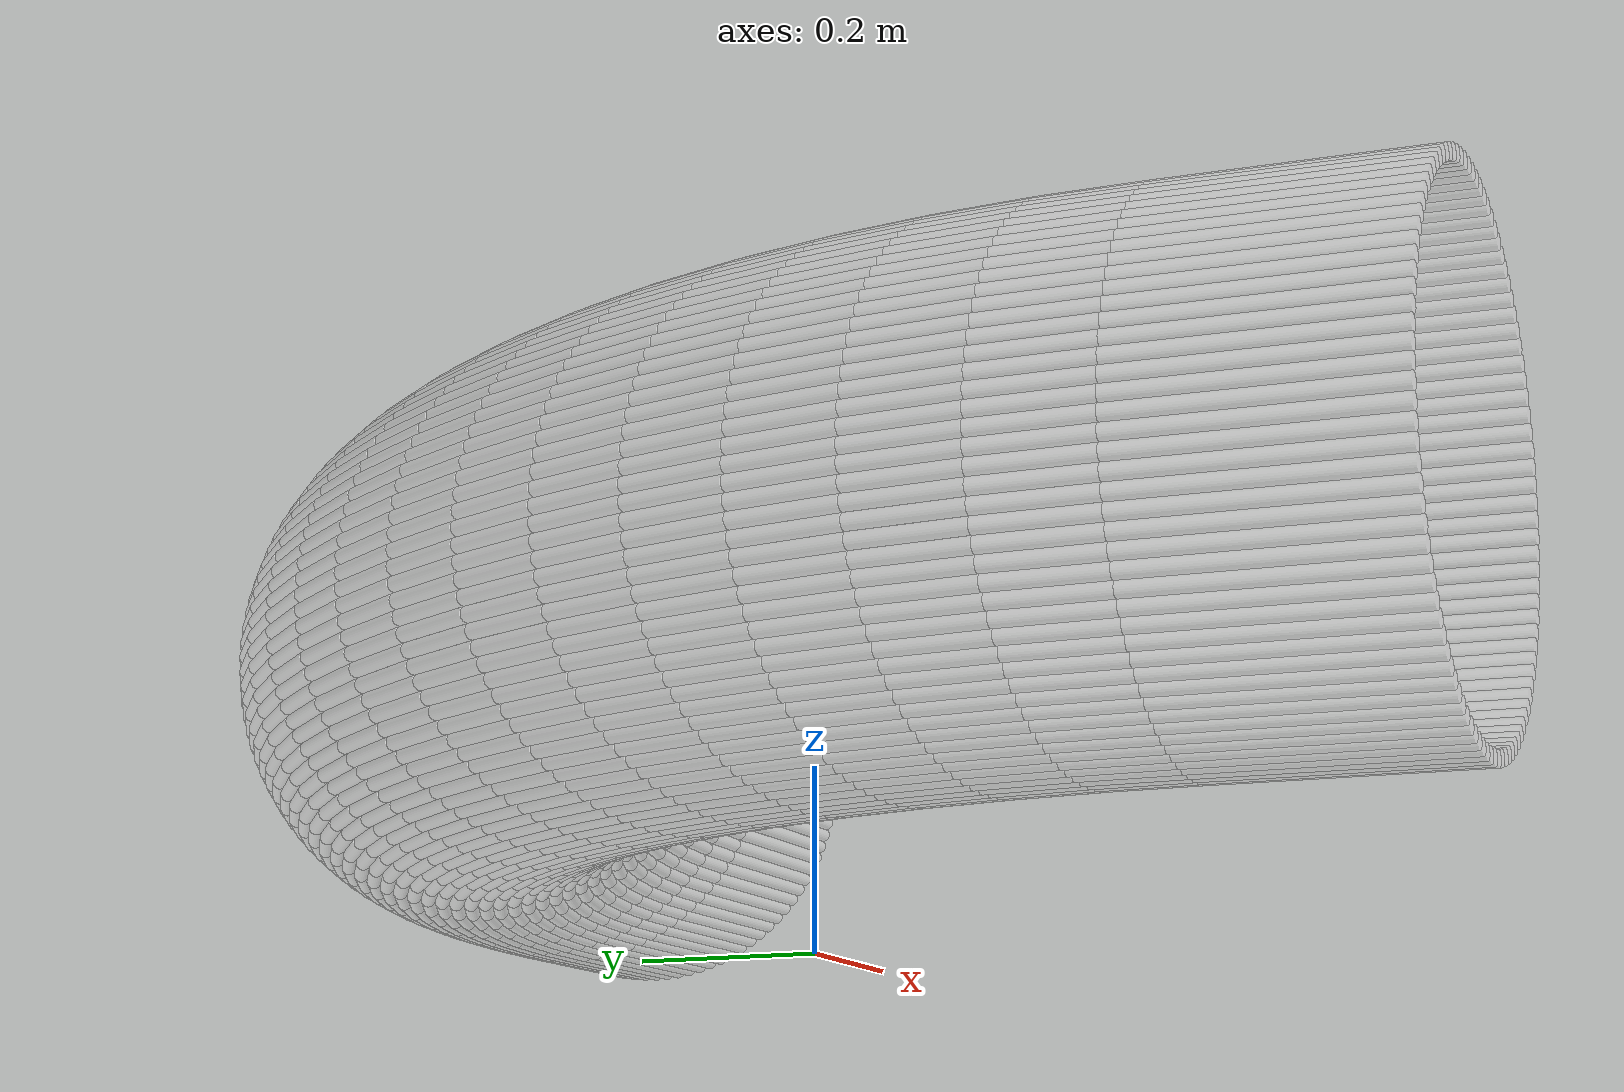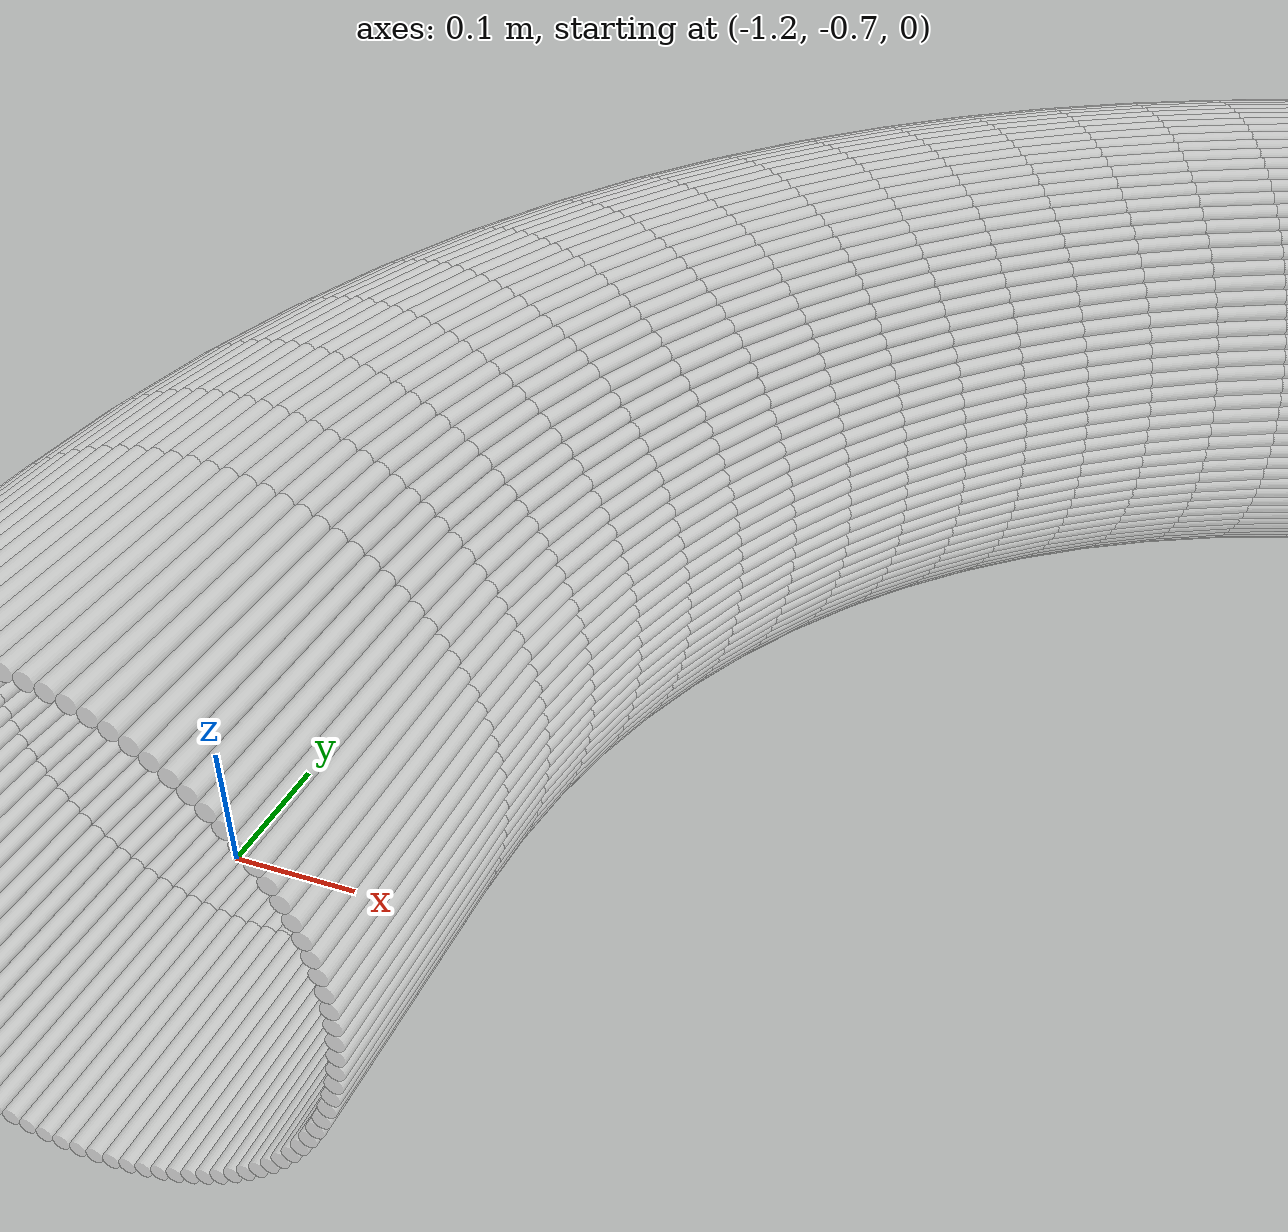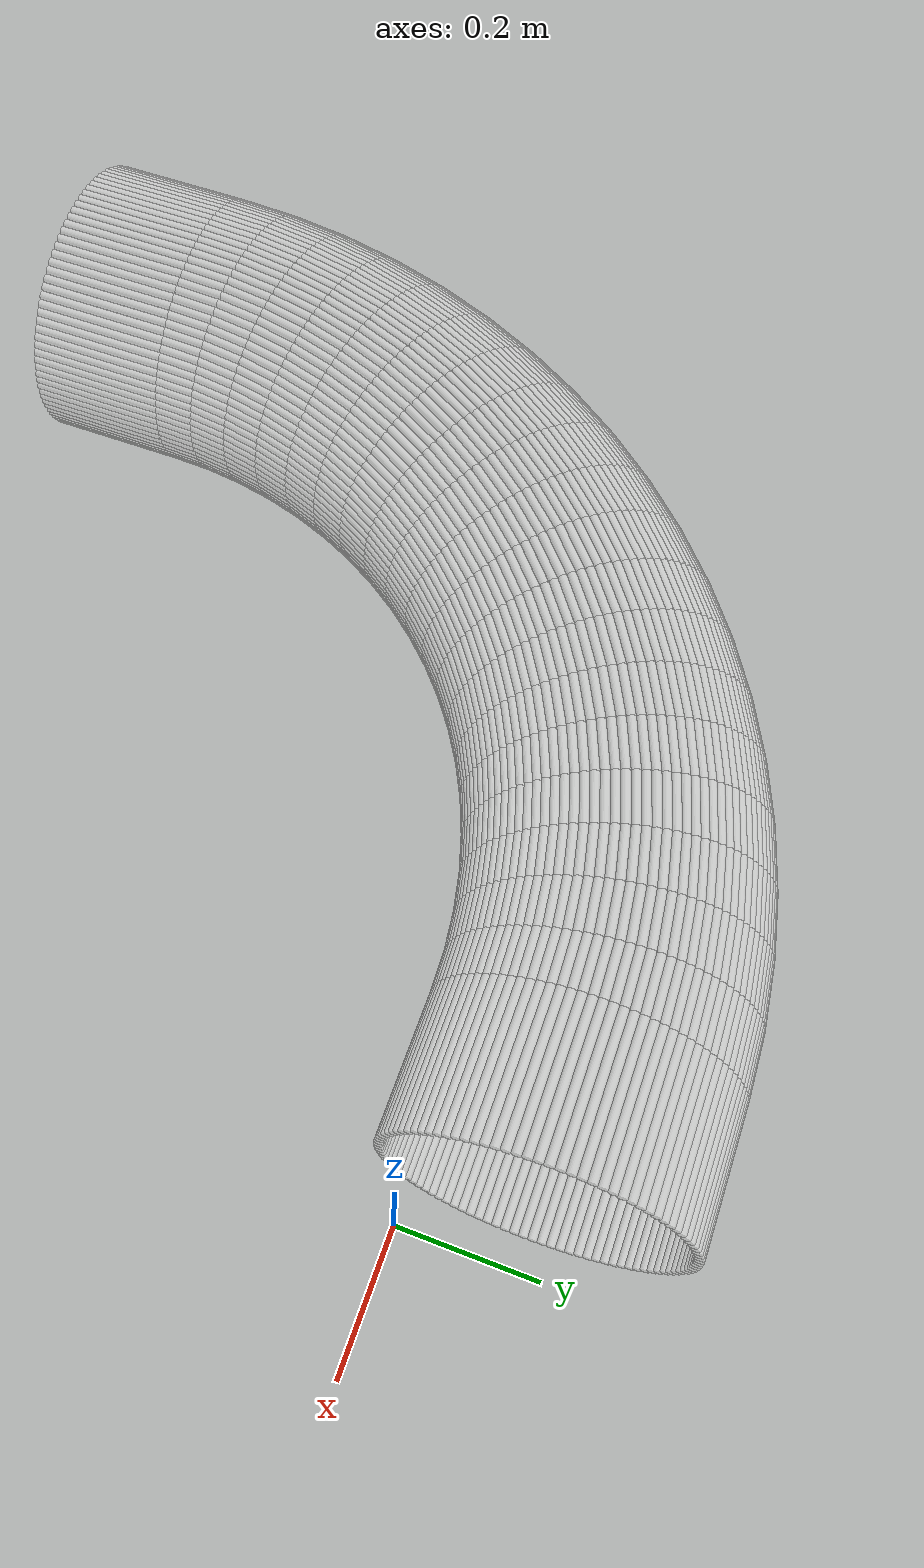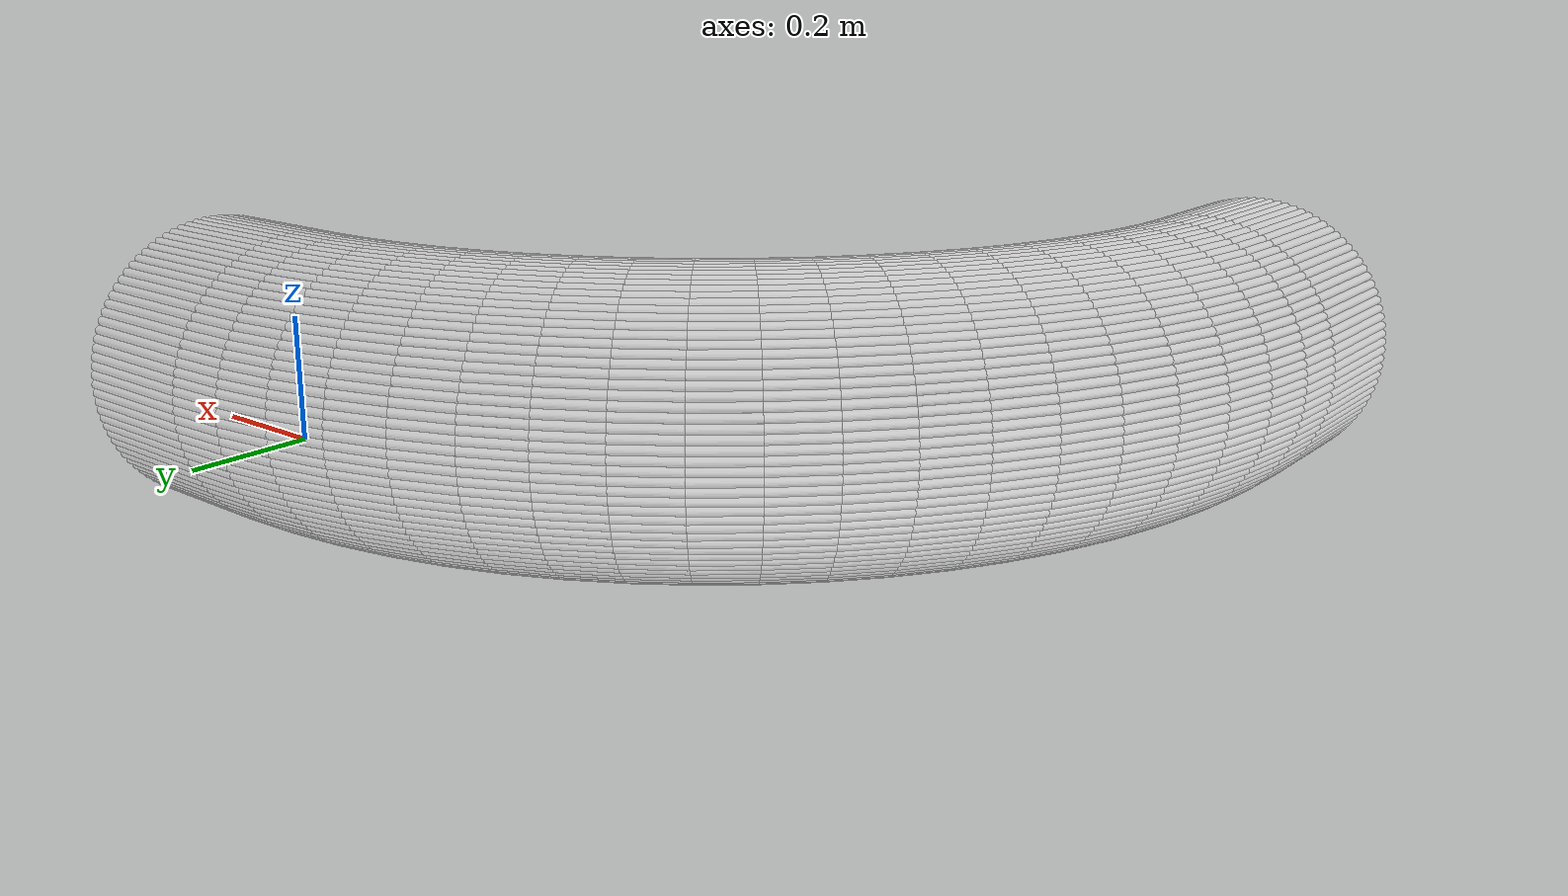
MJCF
<?xml version="1.0" encoding="utf-8"?>
<mujoco>
   <worldbody>
   <body pos="-0.25 -0.74 -0.02" euler="0 0 90">
      <geom euler=" 0 10 0 " fromto="1.1 -0.2 0.2 1.1 0 0.2" rgba="1 1 1 0.35"
            size="0.0062822"
            type="cylinder"/>
      <geom euler=" 0 20 0 " fromto="1.0996 -0.2 0.21256 1.0996 0 0.21256"
            rgba="1 1 1 0.35"
            size="0.0062822"
            type="cylinder"/>
      <geom euler=" 0 30 0 " fromto="1.0984 -0.2 0.22507 1.0984 0 0.22507"
            rgba="1 1 1 0.35"
            size="0.0062822"
            type="cylinder"/>
      <geom euler=" 0 40 0 " fromto="1.0965 -0.2 0.23748 1.0965 0 0.23748"
            rgba="1 1 1 0.35"
            size="0.0062822"
            type="cylinder"/>
      <geom euler=" 0 50 0 " fromto="1.0937 -0.2 0.24974 1.0937 0 0.24974"
            rgba="1 1 1 0.35"
            size="0.0062822"
            type="cylinder"/>
      <geom euler=" 0 60 0 " fromto="1.0902 -0.2 0.2618 1.0902 0 0.2618" rgba="1 1 1 0.35"
            size="0.0062822"
            type="cylinder"/>
      <geom euler=" 0 70 0 " fromto="1.086 -0.2 0.27362 1.086 0 0.27362" rgba="1 1 1 0.35"
            size="0.0062822"
            type="cylinder"/>
      <geom euler=" 0 80 0 " fromto="1.081 -0.2 0.28516 1.081 0 0.28516" rgba="1 1 1 0.35"
            size="0.0062822"
            type="cylinder"/>
      <geom euler=" 0 90 0 " fromto="1.0753 -0.2 0.29635 1.0753 0 0.29635"
            rgba="1 1 1 0.35"
            size="0.0062822"
            type="cylinder"/>
      <geom euler=" 0 100 0 " fromto="1.0689 -0.2 0.30717 1.0689 0 0.30717"
            rgba="1 1 1 0.35"
            size="0.0062822"
            type="cylinder"/>
      <geom euler=" 0 110 0 " fromto="1.0618 -0.2 0.31756 1.0618 0 0.31756"
            rgba="1 1 1 0.35"
            size="0.0062822"
            type="cylinder"/>
      <geom euler=" 0 120 0 " fromto="1.0541 -0.2 0.32748 1.0541 0 0.32748"
            rgba="1 1 1 0.35"
            size="0.0062822"
            type="cylinder"/>
      <geom euler=" 0 130 0 " fromto="1.0458 -0.2 0.33691 1.0458 0 0.33691"
            rgba="1 1 1 0.35"
            size="0.0062822"
            type="cylinder"/>
      <geom euler=" 0 140 0 " fromto="1.0369 -0.2 0.34579 1.0369 0 0.34579"
            rgba="1 1 1 0.35"
            size="0.0062822"
            type="cylinder"/>
      <geom euler=" 0 150 0 " fromto="1.0275 -0.2 0.3541 1.0275 0 0.3541" rgba="1 1 1 0.35"
            size="0.0062822"
            type="cylinder"/>
      <geom euler=" 0 160 0 " fromto="1.0176 -0.2 0.3618 1.0176 0 0.3618" rgba="1 1 1 0.35"
            size="0.0062822"
            type="cylinder"/>
      <geom euler=" 0 170 0 " fromto="1.0072 -0.2 0.36887 1.0072 0 0.36887"
            rgba="1 1 1 0.35"
            size="0.0062822"
            type="cylinder"/>
      <geom euler=" 0 180 0 " fromto="0.99635 -0.2 0.37526 0.99635 0 0.37526"
            rgba="1 1 1 0.35"
            size="0.0062822"
            type="cylinder"/>
      <geom euler=" 0 190 0 " fromto="0.98516 -0.2 0.38097 0.98516 0 0.38097"
            rgba="1 1 1 0.35"
            size="0.0062822"
            type="cylinder"/>
      <geom euler=" 0 200 0 " fromto="0.97362 -0.2 0.38596 0.97362 0 0.38596"
            rgba="1 1 1 0.35"
            size="0.0062822"
            type="cylinder"/>
      <geom euler=" 0 210 0 " fromto="0.9618 -0.2 0.39021 0.9618 0 0.39021"
            rgba="1 1 1 0.35"
            size="0.0062822"
            type="cylinder"/>
      <geom euler=" 0 220 0 " fromto="0.94974 -0.2 0.39372 0.94974 0 0.39372"
            rgba="1 1 1 0.35"
            size="0.0062822"
            type="cylinder"/>
      <geom euler=" 0 230 0 " fromto="0.93748 -0.2 0.39646 0.93748 0 0.39646"
            rgba="1 1 1 0.35"
            size="0.0062822"
            type="cylinder"/>
      <geom euler=" 0 240 0 " fromto="0.92507 -0.2 0.39842 0.92507 0 0.39842"
            rgba="1 1 1 0.35"
            size="0.0062822"
            type="cylinder"/>
      <geom euler=" 0 250 0 " fromto="0.91256 -0.2 0.39961 0.91256 0 0.39961"
            rgba="1 1 1 0.35"
            size="0.0062822"
            type="cylinder"/>
      <geom euler=" 0 260 0 " fromto="0.9 -0.2 0.4 0.9 0 0.4" rgba="1 1 1 0.35"
            size="0.0062822"
            type="cylinder"/>
      <geom euler=" 0 270 0 " fromto="0.88744 -0.2 0.39961 0.88744 0 0.39961"
            rgba="1 1 1 0.35"
            size="0.0062822"
            type="cylinder"/>
      <geom euler=" 0 280 0 " fromto="0.87493 -0.2 0.39842 0.87493 0 0.39842"
            rgba="1 1 1 0.35"
            size="0.0062822"
            type="cylinder"/>
      <geom euler=" 0 290 0 " fromto="0.86252 -0.2 0.39646 0.86252 0 0.39646"
            rgba="1 1 1 0.35"
            size="0.0062822"
            type="cylinder"/>
      <geom euler=" 0 300 0 " fromto="0.85026 -0.2 0.39372 0.85026 0 0.39372"
            rgba="1 1 1 0.35"
            size="0.0062822"
            type="cylinder"/>
      <geom euler=" 0 310 0 " fromto="0.8382 -0.2 0.39021 0.8382 0 0.39021"
            rgba="1 1 1 0.35"
            size="0.0062822"
            type="cylinder"/>
      <geom euler=" 0 320 0 " fromto="0.82638 -0.2 0.38596 0.82638 0 0.38596"
            rgba="1 1 1 0.35"
            size="0.0062822"
            type="cylinder"/>
      <geom euler=" 0 330 0 " fromto="0.81484 -0.2 0.38097 0.81484 0 0.38097"
            rgba="1 1 1 0.35"
            size="0.0062822"
            type="cylinder"/>
      <geom euler=" 0 340 0 " fromto="0.80365 -0.2 0.37526 0.80365 0 0.37526"
            rgba="1 1 1 0.35"
            size="0.0062822"
            type="cylinder"/>
      <geom euler=" 0 350 0 " fromto="0.79283 -0.2 0.36887 0.79283 0 0.36887"
            rgba="1 1 1 0.35"
            size="0.0062822"
            type="cylinder"/>
      <geom euler=" 0 360 0 " fromto="0.78244 -0.2 0.3618 0.78244 0 0.3618"
            rgba="1 1 1 0.35"
            size="0.0062822"
            type="cylinder"/>
      <geom euler=" 0 370 0 " fromto="0.77252 -0.2 0.3541 0.77252 0 0.3541"
            rgba="1 1 1 0.35"
            size="0.0062822"
            type="cylinder"/>
      <geom euler=" 0 380 0 " fromto="0.76309 -0.2 0.34579 0.76309 0 0.34579"
            rgba="1 1 1 0.35"
            size="0.0062822"
            type="cylinder"/>
      <geom euler=" 0 390 0 " fromto="0.75421 -0.2 0.33691 0.75421 0 0.33691"
            rgba="1 1 1 0.35"
            size="0.0062822"
            type="cylinder"/>
      <geom euler=" 0 400 0 " fromto="0.7459 -0.2 0.32748 0.7459 0 0.32748"
            rgba="1 1 1 0.35"
            size="0.0062822"
            type="cylinder"/>
      <geom euler=" 0 410 0 " fromto="0.7382 -0.2 0.31756 0.7382 0 0.31756"
            rgba="1 1 1 0.35"
            size="0.0062822"
            type="cylinder"/>
      <geom euler=" 0 420 0 " fromto="0.73113 -0.2 0.30717 0.73113 0 0.30717"
            rgba="1 1 1 0.35"
            size="0.0062822"
            type="cylinder"/>
      <geom euler=" 0 430 0 " fromto="0.72474 -0.2 0.29635 0.72474 0 0.29635"
            rgba="1 1 1 0.35"
            size="0.0062822"
            type="cylinder"/>
      <geom euler=" 0 440 0 " fromto="0.71903 -0.2 0.28516 0.71903 0 0.28516"
            rgba="1 1 1 0.35"
            size="0.0062822"
            type="cylinder"/>
      <geom euler=" 0 450 0 " fromto="0.71404 -0.2 0.27362 0.71404 0 0.27362"
            rgba="1 1 1 0.35"
            size="0.0062822"
            type="cylinder"/>
      <geom euler=" 0 460 0 " fromto="0.70979 -0.2 0.2618 0.70979 0 0.2618"
            rgba="1 1 1 0.35"
            size="0.0062822"
            type="cylinder"/>
      <geom euler=" 0 470 0 " fromto="0.70628 -0.2 0.24974 0.70628 0 0.24974"
            rgba="1 1 1 0.35"
            size="0.0062822"
            type="cylinder"/>
      <geom euler=" 0 480 0 " fromto="0.70354 -0.2 0.23748 0.70354 0 0.23748"
            rgba="1 1 1 0.35"
            size="0.0062822"
            type="cylinder"/>
      <geom euler=" 0 490 0 " fromto="0.70158 -0.2 0.22507 0.70158 0 0.22507"
            rgba="1 1 1 0.35"
            size="0.0062822"
            type="cylinder"/>
      <geom euler=" 0 500 0 " fromto="0.70039 -0.2 0.21256 0.70039 0 0.21256"
            rgba="1 1 1 0.35"
            size="0.0062822"
            type="cylinder"/>
      <geom euler=" 0 510 0 " fromto="0.7 -0.2 0.2 0.7 0 0.2" rgba="1 1 1 0.35"
            size="0.0062822"
            type="cylinder"/>
      <geom euler=" 0 520 0 " fromto="0.70039 -0.2 0.18744 0.70039 0 0.18744"
            rgba="1 1 1 0.35"
            size="0.0062822"
            type="cylinder"/>
      <geom euler=" 0 530 0 " fromto="0.70158 -0.2 0.17493 0.70158 0 0.17493"
            rgba="1 1 1 0.35"
            size="0.0062822"
            type="cylinder"/>
      <geom euler=" 0 540 0 " fromto="0.70354 -0.2 0.16252 0.70354 0 0.16252"
            rgba="1 1 1 0.35"
            size="0.0062822"
            type="cylinder"/>
      <geom euler=" 0 550 0 " fromto="0.70628 -0.2 0.15026 0.70628 0 0.15026"
            rgba="1 1 1 0.35"
            size="0.0062822"
            type="cylinder"/>
      <geom euler=" 0 560 0 " fromto="0.70979 -0.2 0.1382 0.70979 0 0.1382"
            rgba="1 1 1 0.35"
            size="0.0062822"
            type="cylinder"/>
      <geom euler=" 0 570 0 " fromto="0.71404 -0.2 0.12638 0.71404 0 0.12638"
            rgba="1 1 1 0.35"
            size="0.0062822"
            type="cylinder"/>
      <geom euler=" 0 580 0 " fromto="0.71903 -0.2 0.11484 0.71903 0 0.11484"
            rgba="1 1 1 0.35"
            size="0.0062822"
            type="cylinder"/>
      <geom euler=" 0 590 0 " fromto="0.72474 -0.2 0.10365 0.72474 0 0.10365"
            rgba="1 1 1 0.35"
            size="0.0062822"
            type="cylinder"/>
      <geom euler=" 0 600 0 " fromto="0.73113 -0.2 0.092835 0.73113 0 0.092835"
            rgba="1 1 1 0.35"
            size="0.0062822"
            type="cylinder"/>
      <geom euler=" 0 610 0 " fromto="0.7382 -0.2 0.082443 0.7382 0 0.082443"
            rgba="1 1 1 0.35"
            size="0.0062822"
            type="cylinder"/>
      <geom euler=" 0 620 0 " fromto="0.7459 -0.2 0.072515 0.7459 0 0.072515"
            rgba="1 1 1 0.35"
            size="0.0062822"
            type="cylinder"/>
      <geom euler=" 0 630 0 " fromto="0.75421 -0.2 0.063091 0.75421 0 0.063091"
            rgba="1 1 1 0.35"
            size="0.0062822"
            type="cylinder"/>
      <geom euler=" 0 640 0 " fromto="0.76309 -0.2 0.054206 0.76309 0 0.054206"
            rgba="1 1 1 0.35"
            size="0.0062822"
            type="cylinder"/>
      <geom euler=" 0 650 0 " fromto="0.77252 -0.2 0.045897 0.77252 0 0.045897"
            rgba="1 1 1 0.35"
            size="0.0062822"
            type="cylinder"/>
      <geom euler=" 0 660 0 " fromto="0.78244 -0.2 0.038197 0.78244 0 0.038197"
            rgba="1 1 1 0.35"
            size="0.0062822"
            type="cylinder"/>
      <geom euler=" 0 670 0 " fromto="0.79283 -0.2 0.031134 0.79283 0 0.031134"
            rgba="1 1 1 0.35"
            size="0.0062822"
            type="cylinder"/>
      <geom euler=" 0 680 0 " fromto="0.80365 -0.2 0.024739 0.80365 0 0.024739"
            rgba="1 1 1 0.35"
            size="0.0062822"
            type="cylinder"/>
      <geom euler=" 0 690 0 " fromto="0.81484 -0.2 0.019035 0.81484 0 0.019035"
            rgba="1 1 1 0.35"
            size="0.0062822"
            type="cylinder"/>
      <geom euler=" 0 700 0 " fromto="0.82638 -0.2 0.014045 0.82638 0 0.014045"
            rgba="1 1 1 0.35"
            size="0.0062822"
            type="cylinder"/>
      <geom euler=" 0 710 0 " fromto="0.8382 -0.2 0.0097887 0.8382 0 0.0097887"
            rgba="1 1 1 0.35"
            size="0.0062822"
            type="cylinder"/>
      <geom euler=" 0 720 0 " fromto="0.85026 -0.2 0.0062834 0.85026 0 0.0062834"
            rgba="1 1 1 0.35"
            size="0.0062822"
            type="cylinder"/>
      <geom euler=" 0 730 0 " fromto="0.86252 -0.2 0.0035425 0.86252 0 0.0035425"
            rgba="1 1 1 0.35"
            size="0.0062822"
            type="cylinder"/>
      <geom euler=" 0 740 0 " fromto="0.87493 -0.2 0.0015771 0.87493 0 0.0015771"
            rgba="1 1 1 0.35"
            size="0.0062822"
            type="cylinder"/>
      <geom euler=" 0 750 0 " fromto="0.88744 -0.2 0.00039465 0.88744 0 0.00039465"
            rgba="1 1 1 0.35"
            size="0.0062822"
            type="cylinder"/>
      <geom euler=" 0 760 0 " fromto="0.9 -0.2 0 0.9 0 0" rgba="1 1 1 0.35"
            size="0.0062822"
            type="cylinder"/>
      <geom euler=" 0 770 0 " fromto="0.91256 -0.2 0.00039465 0.91256 0 0.00039465"
            rgba="1 1 1 0.35"
            size="0.0062822"
            type="cylinder"/>
      <geom euler=" 0 780 0 " fromto="0.92507 -0.2 0.0015771 0.92507 0 0.0015771"
            rgba="1 1 1 0.35"
            size="0.0062822"
            type="cylinder"/>
      <geom euler=" 0 790 0 " fromto="0.93748 -0.2 0.0035425 0.93748 0 0.0035425"
            rgba="1 1 1 0.35"
            size="0.0062822"
            type="cylinder"/>
      <geom euler=" 0 800 0 " fromto="0.94974 -0.2 0.0062834 0.94974 0 0.0062834"
            rgba="1 1 1 0.35"
            size="0.0062822"
            type="cylinder"/>
      <geom euler=" 0 810 0 " fromto="0.9618 -0.2 0.0097887 0.9618 0 0.0097887"
            rgba="1 1 1 0.35"
            size="0.0062822"
            type="cylinder"/>
      <geom euler=" 0 820 0 " fromto="0.97362 -0.2 0.014045 0.97362 0 0.014045"
            rgba="1 1 1 0.35"
            size="0.0062822"
            type="cylinder"/>
      <geom euler=" 0 830 0 " fromto="0.98516 -0.2 0.019035 0.98516 0 0.019035"
            rgba="1 1 1 0.35"
            size="0.0062822"
            type="cylinder"/>
      <geom euler=" 0 840 0 " fromto="0.99635 -0.2 0.024739 0.99635 0 0.024739"
            rgba="1 1 1 0.35"
            size="0.0062822"
            type="cylinder"/>
      <geom euler=" 0 850 0 " fromto="1.0072 -0.2 0.031134 1.0072 0 0.031134"
            rgba="1 1 1 0.35"
            size="0.0062822"
            type="cylinder"/>
      <geom euler=" 0 860 0 " fromto="1.0176 -0.2 0.038197 1.0176 0 0.038197"
            rgba="1 1 1 0.35"
            size="0.0062822"
            type="cylinder"/>
      <geom euler=" 0 870 0 " fromto="1.0275 -0.2 0.045897 1.0275 0 0.045897"
            rgba="1 1 1 0.35"
            size="0.0062822"
            type="cylinder"/>
      <geom euler=" 0 880 0 " fromto="1.0369 -0.2 0.054206 1.0369 0 0.054206"
            rgba="1 1 1 0.35"
            size="0.0062822"
            type="cylinder"/>
      <geom euler=" 0 890 0 " fromto="1.0458 -0.2 0.063091 1.0458 0 0.063091"
            rgba="1 1 1 0.35"
            size="0.0062822"
            type="cylinder"/>
      <geom euler=" 0 900 0 " fromto="1.0541 -0.2 0.072515 1.0541 0 0.072515"
            rgba="1 1 1 0.35"
            size="0.0062822"
            type="cylinder"/>
      <geom euler=" 0 910 0 " fromto="1.0618 -0.2 0.082443 1.0618 0 0.082443"
            rgba="1 1 1 0.35"
            size="0.0062822"
            type="cylinder"/>
      <geom euler=" 0 920 0 " fromto="1.0689 -0.2 0.092835 1.0689 0 0.092835"
            rgba="1 1 1 0.35"
            size="0.0062822"
            type="cylinder"/>
      <geom euler=" 0 930 0 " fromto="1.0753 -0.2 0.10365 1.0753 0 0.10365"
            rgba="1 1 1 0.35"
            size="0.0062822"
            type="cylinder"/>
      <geom euler=" 0 940 0 " fromto="1.081 -0.2 0.11484 1.081 0 0.11484" rgba="1 1 1 0.35"
            size="0.0062822"
            type="cylinder"/>
      <geom euler=" 0 950 0 " fromto="1.086 -0.2 0.12638 1.086 0 0.12638" rgba="1 1 1 0.35"
            size="0.0062822"
            type="cylinder"/>
      <geom euler=" 0 960 0 " fromto="1.0902 -0.2 0.1382 1.0902 0 0.1382" rgba="1 1 1 0.35"
            size="0.0062822"
            type="cylinder"/>
      <geom euler=" 0 970 0 " fromto="1.0937 -0.2 0.15026 1.0937 0 0.15026"
            rgba="1 1 1 0.35"
            size="0.0062822"
            type="cylinder"/>
      <geom euler=" 0 980 0 " fromto="1.0965 -0.2 0.16252 1.0965 0 0.16252"
            rgba="1 1 1 0.35"
            size="0.0062822"
            type="cylinder"/>
      <geom euler=" 0 990 0 " fromto="1.0984 -0.2 0.17493 1.0984 0 0.17493"
            rgba="1 1 1 0.35"
            size="0.0062822"
            type="cylinder"/>
      <geom euler=" 0 1000 0 " fromto="1.0996 -0.2 0.18744 1.0996 0 0.18744"
            rgba="1 1 1 0.35"
            size="0.0062822"
            type="cylinder"/>
      <geom euler=" 0 10 0 " fromto="1.1 0 0.2 1.0962 0.090837 0.2" rgba="1 1 1 0.35"
            size="0.0062822"
            type="cylinder"/>
      <geom euler=" 0 20 0 " fromto="1.0996 0 0.21256 1.0958 0.090805 0.21256"
            rgba="1 1 1 0.35"
            size="0.0062822"
            type="cylinder"/>
      <geom euler=" 0 30 0 " fromto="1.0984 0 0.22507 1.0947 0.090707 0.22507"
            rgba="1 1 1 0.35"
            size="0.0062822"
            type="cylinder"/>
      <geom euler=" 0 40 0 " fromto="1.0965 0 0.23748 1.0927 0.090545 0.23748"
            rgba="1 1 1 0.35"
            size="0.0062822"
            type="cylinder"/>
      <geom euler=" 0 50 0 " fromto="1.0937 0 0.24974 1.09 0.090318 0.24974"
            rgba="1 1 1 0.35"
            size="0.0062822"
            type="cylinder"/>
      <geom euler=" 0 60 0 " fromto="1.0902 0 0.2618 1.0865 0.090029 0.2618"
            rgba="1 1 1 0.35"
            size="0.0062822"
            type="cylinder"/>
      <geom euler=" 0 70 0 " fromto="1.086 0 0.27362 1.0822 0.089677 0.27362"
            rgba="1 1 1 0.35"
            size="0.0062822"
            type="cylinder"/>
      <geom euler=" 0 80 0 " fromto="1.081 0 0.28516 1.0773 0.089265 0.28516"
            rgba="1 1 1 0.35"
            size="0.0062822"
            type="cylinder"/>
      <geom euler=" 0 90 0 " fromto="1.0753 0 0.29635 1.0716 0.088794 0.29635"
            rgba="1 1 1 0.35"
            size="0.0062822"
            type="cylinder"/>
      <geom euler=" 0 100 0 " fromto="1.0689 0 0.30717 1.0652 0.088266 0.30717"
            rgba="1 1 1 0.35"
            size="0.0062822"
            type="cylinder"/>
      <geom euler=" 0 110 0 " fromto="1.0618 0 0.31756 1.0582 0.087683 0.31756"
            rgba="1 1 1 0.35"
            size="0.0062822"
            type="cylinder"/>
      <geom euler=" 0 120 0 " fromto="1.0541 0 0.32748 1.0505 0.087047 0.32748"
            rgba="1 1 1 0.35"
            size="0.0062822"
            type="cylinder"/>
      <geom euler=" 0 130 0 " fromto="1.0458 0 0.33691 1.0422 0.086361 0.33691"
            rgba="1 1 1 0.35"
            size="0.0062822"
            type="cylinder"/>
      <geom euler=" 0 140 0 " fromto="1.0369 0 0.34579 1.0334 0.085627 0.34579"
            rgba="1 1 1 0.35"
            size="0.0062822"
            type="cylinder"/>
      <geom euler=" 0 150 0 " fromto="1.0275 0 0.3541 1.024 0.084849 0.3541"
            rgba="1 1 1 0.35"
            size="0.0062822"
            type="cylinder"/>
      <geom euler=" 0 160 0 " fromto="1.0176 0 0.3618 1.0141 0.084029 0.3618"
            rgba="1 1 1 0.35"
            size="0.0062822"
            type="cylinder"/>
      <geom euler=" 0 170 0 " fromto="1.0072 0 0.36887 1.0037 0.083171 0.36887"
            rgba="1 1 1 0.35"
            size="0.0062822"
            type="cylinder"/>
      <geom euler=" 0 180 0 " fromto="0.99635 0 0.37526 0.99295 0.082278 0.37526"
            rgba="1 1 1 0.35"
            size="0.0062822"
            type="cylinder"/>
      <geom euler=" 0 190 0 " fromto="0.98516 0 0.38097 0.98179 0.081354 0.38097"
            rgba="1 1 1 0.35"
            size="0.0062822"
            type="cylinder"/>
      <geom euler=" 0 200 0 " fromto="0.97362 0 0.38596 0.9703 0.080401 0.38596"
            rgba="1 1 1 0.35"
            size="0.0062822"
            type="cylinder"/>
      <geom euler=" 0 210 0 " fromto="0.9618 0 0.39021 0.95852 0.079425 0.39021"
            rgba="1 1 1 0.35"
            size="0.0062822"
            type="cylinder"/>
      <geom euler=" 0 220 0 " fromto="0.94974 0 0.39372 0.94649 0.078429 0.39372"
            rgba="1 1 1 0.35"
            size="0.0062822"
            type="cylinder"/>
      <geom euler=" 0 230 0 " fromto="0.93748 0 0.39646 0.93427 0.077416 0.39646"
            rgba="1 1 1 0.35"
            size="0.0062822"
            type="cylinder"/>
      <geom euler=" 0 240 0 " fromto="0.92507 0 0.39842 0.92191 0.076391 0.39842"
            rgba="1 1 1 0.35"
            size="0.0062822"
            type="cylinder"/>
      <geom euler=" 0 250 0 " fromto="0.91256 0 0.39961 0.90944 0.075358 0.39961"
            rgba="1 1 1 0.35"
            size="0.0062822"
            type="cylinder"/>
      <geom euler=" 0 260 0 " fromto="0.9 0 0.4 0.89693 0.074321 0.4" rgba="1 1 1 0.35"
            size="0.0062822"
            type="cylinder"/>
      <geom euler=" 0 270 0 " fromto="0.88744 0 0.39961 0.88441 0.073284 0.39961"
            rgba="1 1 1 0.35"
            size="0.0062822"
            type="cylinder"/>
      <geom euler=" 0 280 0 " fromto="0.87493 0 0.39842 0.87195 0.072251 0.39842"
            rgba="1 1 1 0.35"
            size="0.0062822"
            type="cylinder"/>
      <geom euler=" 0 290 0 " fromto="0.86252 0 0.39646 0.85958 0.071227 0.39646"
            rgba="1 1 1 0.35"
            size="0.0062822"
            type="cylinder"/>
      <geom euler=" 0 300 0 " fromto="0.85026 0 0.39372 0.84736 0.070214 0.39372"
            rgba="1 1 1 0.35"
            size="0.0062822"
            type="cylinder"/>
      <geom euler=" 0 310 0 " fromto="0.8382 0 0.39021 0.83533 0.069218 0.39021"
            rgba="1 1 1 0.35"
            size="0.0062822"
            type="cylinder"/>
      <geom euler=" 0 320 0 " fromto="0.82638 0 0.38596 0.82355 0.068242 0.38596"
            rgba="1 1 1 0.35"
            size="0.0062822"
            type="cylinder"/>
      <geom euler=" 0 330 0 " fromto="0.81484 0 0.38097 0.81206 0.067289 0.38097"
            rgba="1 1 1 0.35"
            size="0.0062822"
            type="cylinder"/>
      <geom euler=" 0 340 0 " fromto="0.80365 0 0.37526 0.8009 0.066365 0.37526"
            rgba="1 1 1 0.35"
            size="0.0062822"
            type="cylinder"/>
      <geom euler=" 0 350 0 " fromto="0.79283 0 0.36887 0.79013 0.065472 0.36887"
            rgba="1 1 1 0.35"
            size="0.0062822"
            type="cylinder"/>
      <geom euler=" 0 360 0 " fromto="0.78244 0 0.3618 0.77977 0.064614 0.3618"
            rgba="1 1 1 0.35"
            size="0.0062822"
            type="cylinder"/>
      <geom euler=" 0 370 0 " fromto="0.77252 0 0.3541 0.76988 0.063794 0.3541"
            rgba="1 1 1 0.35"
            size="0.0062822"
            type="cylinder"/>
      <geom euler=" 0 380 0 " fromto="0.76309 0 0.34579 0.76048 0.063016 0.34579"
            rgba="1 1 1 0.35"
            size="0.0062822"
            type="cylinder"/>
      <geom euler=" 0 390 0 " fromto="0.75421 0 0.33691 0.75163 0.062282 0.33691"
            rgba="1 1 1 0.35"
            size="0.0062822"
            type="cylinder"/>
      <geom euler=" 0 400 0 " fromto="0.7459 0 0.32748 0.74335 0.061596 0.32748"
            rgba="1 1 1 0.35"
            size="0.0062822"
            type="cylinder"/>
      <geom euler=" 0 410 0 " fromto="0.7382 0 0.31756 0.73568 0.06096 0.31756"
            rgba="1 1 1 0.35"
            size="0.0062822"
            type="cylinder"/>
      <geom euler=" 0 420 0 " fromto="0.73113 0 0.30717 0.72864 0.060377 0.30717"
            rgba="1 1 1 0.35"
            size="0.0062822"
            type="cylinder"/>
      <geom euler=" 0 430 0 " fromto="0.72474 0 0.29635 0.72226 0.059848 0.29635"
            rgba="1 1 1 0.35"
            size="0.0062822"
            type="cylinder"/>
      <geom euler=" 0 440 0 " fromto="0.71903 0 0.28516 0.71658 0.059377 0.28516"
            rgba="1 1 1 0.35"
            size="0.0062822"
            type="cylinder"/>
      <geom euler=" 0 450 0 " fromto="0.71404 0 0.27362 0.71161 0.058965 0.27362"
            rgba="1 1 1 0.35"
            size="0.0062822"
            type="cylinder"/>
      <geom euler=" 0 460 0 " fromto="0.70979 0 0.2618 0.70736 0.058614 0.2618"
            rgba="1 1 1 0.35"
            size="0.0062822"
            type="cylinder"/>
      <geom euler=" 0 470 0 " fromto="0.70628 0 0.24974 0.70387 0.058324 0.24974"
            rgba="1 1 1 0.35"
            size="0.0062822"
            type="cylinder"/>
      <geom euler=" 0 480 0 " fromto="0.70354 0 0.23748 0.70114 0.058098 0.23748"
            rgba="1 1 1 0.35"
            size="0.0062822"
            type="cylinder"/>
      <geom euler=" 0 490 0 " fromto="0.70158 0 0.22507 0.69918 0.057936 0.22507"
            rgba="1 1 1 0.35"
            size="0.0062822"
            type="cylinder"/>
      <geom euler=" 0 500 0 " fromto="0.70039 0 0.21256 0.698 0.057838 0.21256"
            rgba="1 1 1 0.35"
            size="0.0062822"
            type="cylinder"/>
      <geom euler=" 0 510 0 " fromto="0.7 0 0.2 0.69761 0.057806 0.2" rgba="1 1 1 0.35"
            size="0.0062822"
            type="cylinder"/>
      <geom euler=" 0 520 0 " fromto="0.70039 0 0.18744 0.698 0.057838 0.18744"
            rgba="1 1 1 0.35"
            size="0.0062822"
            type="cylinder"/>
      <geom euler=" 0 530 0 " fromto="0.70158 0 0.17493 0.69918 0.057936 0.17493"
            rgba="1 1 1 0.35"
            size="0.0062822"
            type="cylinder"/>
      <geom euler=" 0 540 0 " fromto="0.70354 0 0.16252 0.70114 0.058098 0.16252"
            rgba="1 1 1 0.35"
            size="0.0062822"
            type="cylinder"/>
      <geom euler=" 0 550 0 " fromto="0.70628 0 0.15026 0.70387 0.058324 0.15026"
            rgba="1 1 1 0.35"
            size="0.0062822"
            type="cylinder"/>
      <geom euler=" 0 560 0 " fromto="0.70979 0 0.1382 0.70736 0.058614 0.1382"
            rgba="1 1 1 0.35"
            size="0.0062822"
            type="cylinder"/>
      <geom euler=" 0 570 0 " fromto="0.71404 0 0.12638 0.71161 0.058965 0.12638"
            rgba="1 1 1 0.35"
            size="0.0062822"
            type="cylinder"/>
      <geom euler=" 0 580 0 " fromto="0.71903 0 0.11484 0.71658 0.059377 0.11484"
            rgba="1 1 1 0.35"
            size="0.0062822"
            type="cylinder"/>
      <geom euler=" 0 590 0 " fromto="0.72474 0 0.10365 0.72226 0.059848 0.10365"
            rgba="1 1 1 0.35"
            size="0.0062822"
            type="cylinder"/>
      <geom euler=" 0 600 0 " fromto="0.73113 0 0.092835 0.72864 0.060377 0.092835"
            rgba="1 1 1 0.35"
            size="0.0062822"
            type="cylinder"/>
      <geom euler=" 0 610 0 " fromto="0.7382 0 0.082443 0.73568 0.06096 0.082443"
            rgba="1 1 1 0.35"
            size="0.0062822"
            type="cylinder"/>
      <geom euler=" 0 620 0 " fromto="0.7459 0 0.072515 0.74335 0.061596 0.072515"
            rgba="1 1 1 0.35"
            size="0.0062822"
            type="cylinder"/>
      <geom euler=" 0 630 0 " fromto="0.75421 0 0.063091 0.75163 0.062282 0.063091"
            rgba="1 1 1 0.35"
            size="0.0062822"
            type="cylinder"/>
      <geom euler=" 0 640 0 " fromto="0.76309 0 0.054206 0.76048 0.063016 0.054206"
            rgba="1 1 1 0.35"
            size="0.0062822"
            type="cylinder"/>
      <geom euler=" 0 650 0 " fromto="0.77252 0 0.045897 0.76988 0.063794 0.045897"
            rgba="1 1 1 0.35"
            size="0.0062822"
            type="cylinder"/>
      <geom euler=" 0 660 0 " fromto="0.78244 0 0.038197 0.77977 0.064614 0.038197"
            rgba="1 1 1 0.35"
            size="0.0062822"
            type="cylinder"/>
      <geom euler=" 0 670 0 " fromto="0.79283 0 0.031134 0.79013 0.065472 0.031134"
            rgba="1 1 1 0.35"
            size="0.0062822"
            type="cylinder"/>
      <geom euler=" 0 680 0 " fromto="0.80365 0 0.024739 0.8009 0.066365 0.024739"
            rgba="1 1 1 0.35"
            size="0.0062822"
            type="cylinder"/>
      <geom euler=" 0 690 0 " fromto="0.81484 0 0.019035 0.81206 0.067289 0.019035"
            rgba="1 1 1 0.35"
            size="0.0062822"
            type="cylinder"/>
      <geom euler=" 0 700 0 " fromto="0.82638 0 0.014045 0.82355 0.068242 0.014045"
            rgba="1 1 1 0.35"
            size="0.0062822"
            type="cylinder"/>
      <geom euler=" 0 710 0 " fromto="0.8382 0 0.0097887 0.83533 0.069218 0.0097887"
            rgba="1 1 1 0.35"
            size="0.0062822"
            type="cylinder"/>
      <geom euler=" 0 720 0 " fromto="0.85026 0 0.0062834 0.84736 0.070214 0.0062834"
            rgba="1 1 1 0.35"
            size="0.0062822"
            type="cylinder"/>
      <geom euler=" 0 730 0 " fromto="0.86252 0 0.0035425 0.85958 0.071227 0.0035425"
            rgba="1 1 1 0.35"
            size="0.0062822"
            type="cylinder"/>
      <geom euler=" 0 740 0 " fromto="0.87493 0 0.0015771 0.87195 0.072251 0.0015771"
            rgba="1 1 1 0.35"
            size="0.0062822"
            type="cylinder"/>
      <geom euler=" 0 750 0 " fromto="0.88744 0 0.00039465 0.88441 0.073284 0.00039465"
            rgba="1 1 1 0.35"
            size="0.0062822"
            type="cylinder"/>
      <geom euler=" 0 760 0 " fromto="0.9 0 0 0.89693 0.074321 0" rgba="1 1 1 0.35"
            size="0.0062822"
            type="cylinder"/>
      <geom euler=" 0 770 0 " fromto="0.91256 0 0.00039465 0.90944 0.075358 0.00039465"
            rgba="1 1 1 0.35"
            size="0.0062822"
            type="cylinder"/>
      <geom euler=" 0 780 0 " fromto="0.92507 0 0.0015771 0.92191 0.076391 0.0015771"
            rgba="1 1 1 0.35"
            size="0.0062822"
            type="cylinder"/>
      <geom euler=" 0 790 0 " fromto="0.93748 0 0.0035425 0.93427 0.077416 0.0035425"
            rgba="1 1 1 0.35"
            size="0.0062822"
            type="cylinder"/>
      <geom euler=" 0 800 0 " fromto="0.94974 0 0.0062834 0.94649 0.078429 0.0062834"
            rgba="1 1 1 0.35"
            size="0.0062822"
            type="cylinder"/>
      <geom euler=" 0 810 0 " fromto="0.9618 0 0.0097887 0.95852 0.079425 0.0097887"
            rgba="1 1 1 0.35"
            size="0.0062822"
            type="cylinder"/>
      <geom euler=" 0 820 0 " fromto="0.97362 0 0.014045 0.9703 0.080401 0.014045"
            rgba="1 1 1 0.35"
            size="0.0062822"
            type="cylinder"/>
      <geom euler=" 0 830 0 " fromto="0.98516 0 0.019035 0.98179 0.081354 0.019035"
            rgba="1 1 1 0.35"
            size="0.0062822"
            type="cylinder"/>
      <geom euler=" 0 840 0 " fromto="0.99635 0 0.024739 0.99295 0.082278 0.024739"
            rgba="1 1 1 0.35"
            size="0.0062822"
            type="cylinder"/>
      <geom euler=" 0 850 0 " fromto="1.0072 0 0.031134 1.0037 0.083171 0.031134"
            rgba="1 1 1 0.35"
            size="0.0062822"
            type="cylinder"/>
      <geom euler=" 0 860 0 " fromto="1.0176 0 0.038197 1.0141 0.084029 0.038197"
            rgba="1 1 1 0.35"
            size="0.0062822"
            type="cylinder"/>
      <geom euler=" 0 870 0 " fromto="1.0275 0 0.045897 1.024 0.084849 0.045897"
            rgba="1 1 1 0.35"
            size="0.0062822"
            type="cylinder"/>
      <geom euler=" 0 880 0 " fromto="1.0369 0 0.054206 1.0334 0.085627 0.054206"
            rgba="1 1 1 0.35"
            size="0.0062822"
            type="cylinder"/>
      <geom euler=" 0 890 0 " fromto="1.0458 0 0.063091 1.0422 0.086361 0.063091"
            rgba="1 1 1 0.35"
            size="0.0062822"
            type="cylinder"/>
      <geom euler=" 0 900 0 " fromto="1.0541 0 0.072515 1.0505 0.087047 0.072515"
            rgba="1 1 1 0.35"
            size="0.0062822"
            type="cylinder"/>
      <geom euler=" 0 910 0 " fromto="1.0618 0 0.082443 1.0582 0.087683 0.082443"
            rgba="1 1 1 0.35"
            size="0.0062822"
            type="cylinder"/>
      <geom euler=" 0 920 0 " fromto="1.0689 0 0.092835 1.0652 0.088266 0.092835"
            rgba="1 1 1 0.35"
            size="0.0062822"
            type="cylinder"/>
      <geom euler=" 0 930 0 " fromto="1.0753 0 0.10365 1.0716 0.088794 0.10365"
            rgba="1 1 1 0.35"
            size="0.0062822"
            type="cylinder"/>
      <geom euler=" 0 940 0 " fromto="1.081 0 0.11484 1.0773 0.089265 0.11484"
            rgba="1 1 1 0.35"
            size="0.0062822"
            type="cylinder"/>
      <geom euler=" 0 950 0 " fromto="1.086 0 0.12638 1.0822 0.089677 0.12638"
            rgba="1 1 1 0.35"
            size="0.0062822"
            type="cylinder"/>
      <geom euler=" 0 960 0 " fromto="1.0902 0 0.1382 1.0865 0.090029 0.1382"
            rgba="1 1 1 0.35"
            size="0.0062822"
            type="cylinder"/>
      <geom euler=" 0 970 0 " fromto="1.0937 0 0.15026 1.09 0.090318 0.15026"
            rgba="1 1 1 0.35"
            size="0.0062822"
            type="cylinder"/>
      <geom euler=" 0 980 0 " fromto="1.0965 0 0.16252 1.0927 0.090545 0.16252"
            rgba="1 1 1 0.35"
            size="0.0062822"
            type="cylinder"/>
      <geom euler=" 0 990 0 " fromto="1.0984 0 0.17493 1.0947 0.090707 0.17493"
            rgba="1 1 1 0.35"
            size="0.0062822"
            type="cylinder"/>
      <geom euler=" 0 1000 0 " fromto="1.0996 0 0.18744 1.0958 0.090805 0.18744"
            rgba="1 1 1 0.35"
            size="0.0062822"
            type="cylinder"/>
      <geom euler=" 0 10 0 " fromto="1.0962 0.090837 0.2 1.085 0.18105 0.2"
            rgba="1 1 1 0.35"
            size="0.0062822"
            type="cylinder"/>
      <geom euler=" 0 20 0 " fromto="1.0958 0.090805 0.21256 1.0846 0.18099 0.21256"
            rgba="1 1 1 0.35"
            size="0.0062822"
            type="cylinder"/>
      <geom euler=" 0 30 0 " fromto="1.0947 0.090707 0.22507 1.0834 0.18079 0.22507"
            rgba="1 1 1 0.35"
            size="0.0062822"
            type="cylinder"/>
      <geom euler=" 0 40 0 " fromto="1.0927 0.090545 0.23748 1.0815 0.18047 0.23748"
            rgba="1 1 1 0.35"
            size="0.0062822"
            type="cylinder"/>
      <geom euler=" 0 50 0 " fromto="1.09 0.090318 0.24974 1.0788 0.18002 0.24974"
            rgba="1 1 1 0.35"
            size="0.0062822"
            type="cylinder"/>
      <geom euler=" 0 60 0 " fromto="1.0865 0.090029 0.2618 1.0753 0.17944 0.2618"
            rgba="1 1 1 0.35"
            size="0.0062822"
            type="cylinder"/>
      <geom euler=" 0 70 0 " fromto="1.0822 0.089677 0.27362 1.0711 0.17874 0.27362"
            rgba="1 1 1 0.35"
            size="0.0062822"
            type="cylinder"/>
      <geom euler=" 0 80 0 " fromto="1.0773 0.089265 0.28516 1.0662 0.17792 0.28516"
            rgba="1 1 1 0.35"
            size="0.0062822"
            type="cylinder"/>
      <geom euler=" 0 90 0 " fromto="1.0716 0.088794 0.29635 1.0606 0.17698 0.29635"
            rgba="1 1 1 0.35"
            size="0.0062822"
            type="cylinder"/>
      <geom euler=" 0 100 0 " fromto="1.0652 0.088266 0.30717 1.0543 0.17593 0.30717"
            rgba="1 1 1 0.35"
            size="0.0062822"
            type="cylinder"/>
      <geom euler=" 0 110 0 " fromto="1.0582 0.087683 0.31756 1.0473 0.17477 0.31756"
            rgba="1 1 1 0.35"
            size="0.0062822"
            type="cylinder"/>
      <geom euler=" 0 120 0 " fromto="1.0505 0.087047 0.32748 1.0397 0.1735 0.32748"
            rgba="1 1 1 0.35"
            size="0.0062822"
            type="cylinder"/>
      <geom euler=" 0 130 0 " fromto="1.0422 0.086361 0.33691 1.0315 0.17213 0.33691"
            rgba="1 1 1 0.35"
            size="0.0062822"
            type="cylinder"/>
      <geom euler=" 0 140 0 " fromto="1.0334 0.085627 0.34579 1.0228 0.17067 0.34579"
            rgba="1 1 1 0.35"
            size="0.0062822"
            type="cylinder"/>
      <geom euler=" 0 150 0 " fromto="1.024 0.084849 0.3541 1.0135 0.16912 0.3541"
            rgba="1 1 1 0.35"
            size="0.0062822"
            type="cylinder"/>
      <geom euler=" 0 160 0 " fromto="1.0141 0.084029 0.3618 1.0037 0.16748 0.3618"
            rgba="1 1 1 0.35"
            size="0.0062822"
            type="cylinder"/>
      <geom euler=" 0 170 0 " fromto="1.0037 0.083171 0.36887 0.99343 0.16577 0.36887"
            rgba="1 1 1 0.35"
            size="0.0062822"
            type="cylinder"/>
      <geom euler=" 0 180 0 " fromto="0.99295 0.082278 0.37526 0.98276 0.16399 0.37526"
            rgba="1 1 1 0.35"
            size="0.0062822"
            type="cylinder"/>
      <geom euler=" 0 190 0 " fromto="0.98179 0.081354 0.38097 0.97172 0.16215 0.38097"
            rgba="1 1 1 0.35"
            size="0.0062822"
            type="cylinder"/>
      <geom euler=" 0 200 0 " fromto="0.9703 0.080401 0.38596 0.96035 0.16025 0.38596"
            rgba="1 1 1 0.35"
            size="0.0062822"
            type="cylinder"/>
      <geom euler=" 0 210 0 " fromto="0.95852 0.079425 0.39021 0.94869 0.15831 0.39021"
            rgba="1 1 1 0.35"
            size="0.0062822"
            type="cylinder"/>
      <geom euler=" 0 220 0 " fromto="0.94649 0.078429 0.39372 0.93678 0.15632 0.39372"
            rgba="1 1 1 0.35"
            size="0.0062822"
            type="cylinder"/>
      <geom euler=" 0 230 0 " fromto="0.93427 0.077416 0.39646 0.92469 0.1543 0.39646"
            rgba="1 1 1 0.35"
            size="0.0062822"
            type="cylinder"/>
      <geom euler=" 0 240 0 " fromto="0.92191 0.076391 0.39842 0.91245 0.15226 0.39842"
            rgba="1 1 1 0.35"
            size="0.0062822"
            type="cylinder"/>
      <geom euler=" 0 250 0 " fromto="0.90944 0.075358 0.39961 0.90011 0.1502 0.39961"
            rgba="1 1 1 0.35"
            size="0.0062822"
            type="cylinder"/>
      <geom euler=" 0 260 0 " fromto="0.89693 0.074321 0.4 0.88773 0.14814 0.4"
            rgba="1 1 1 0.35"
            size="0.0062822"
            type="cylinder"/>
      <geom euler=" 0 270 0 " fromto="0.88441 0.073284 0.39961 0.87534 0.14607 0.39961"
            rgba="1 1 1 0.35"
            size="0.0062822"
            type="cylinder"/>
      <geom euler=" 0 280 0 " fromto="0.87195 0.072251 0.39842 0.863 0.14401 0.39842"
            rgba="1 1 1 0.35"
            size="0.0062822"
            type="cylinder"/>
      <geom euler=" 0 290 0 " fromto="0.85958 0.071227 0.39646 0.85076 0.14197 0.39646"
            rgba="1 1 1 0.35"
            size="0.0062822"
            type="cylinder"/>
      <geom euler=" 0 300 0 " fromto="0.84736 0.070214 0.39372 0.83867 0.13995 0.39372"
            rgba="1 1 1 0.35"
            size="0.0062822"
            type="cylinder"/>
      <geom euler=" 0 310 0 " fromto="0.83533 0.069218 0.39021 0.82676 0.13796 0.39021"
            rgba="1 1 1 0.35"
            size="0.0062822"
            type="cylinder"/>
      <geom euler=" 0 320 0 " fromto="0.82355 0.068242 0.38596 0.8151 0.13602 0.38596"
            rgba="1 1 1 0.35"
            size="0.0062822"
            type="cylinder"/>
      <geom euler=" 0 330 0 " fromto="0.81206 0.067289 0.38097 0.80373 0.13412 0.38097"
            rgba="1 1 1 0.35"
            size="0.0062822"
            type="cylinder"/>
      <geom euler=" 0 340 0 " fromto="0.8009 0.066365 0.37526 0.79269 0.13228 0.37526"
            rgba="1 1 1 0.35"
            size="0.0062822"
            type="cylinder"/>
      <geom euler=" 0 350 0 " fromto="0.79013 0.065472 0.36887 0.78202 0.1305 0.36887"
            rgba="1 1 1 0.35"
            size="0.0062822"
            type="cylinder"/>
      <geom euler=" 0 360 0 " fromto="0.77977 0.064614 0.3618 0.77177 0.12879 0.3618"
            rgba="1 1 1 0.35"
            size="0.0062822"
            type="cylinder"/>
      <geom euler=" 0 370 0 " fromto="0.76988 0.063794 0.3541 0.76198 0.12715 0.3541"
            rgba="1 1 1 0.35"
            size="0.0062822"
            type="cylinder"/>
      <geom euler=" 0 380 0 " fromto="0.76048 0.063016 0.34579 0.75268 0.1256 0.34579"
            rgba="1 1 1 0.35"
            size="0.0062822"
            type="cylinder"/>
      <geom euler=" 0 390 0 " fromto="0.75163 0.062282 0.33691 0.74392 0.12414 0.33691"
            rgba="1 1 1 0.35"
            size="0.0062822"
            type="cylinder"/>
      <geom euler=" 0 400 0 " fromto="0.74335 0.061596 0.32748 0.73572 0.12277 0.32748"
            rgba="1 1 1 0.35"
            size="0.0062822"
            type="cylinder"/>
      <geom euler=" 0 410 0 " fromto="0.73568 0.06096 0.31756 0.72813 0.1215 0.31756"
            rgba="1 1 1 0.35"
            size="0.0062822"
            type="cylinder"/>
      <geom euler=" 0 420 0 " fromto="0.72864 0.060377 0.30717 0.72116 0.12034 0.30717"
            rgba="1 1 1 0.35"
            size="0.0062822"
            type="cylinder"/>
      <geom euler=" 0 430 0 " fromto="0.72226 0.059848 0.29635 0.71485 0.11929 0.29635"
            rgba="1 1 1 0.35"
            size="0.0062822"
            type="cylinder"/>
      <geom euler=" 0 440 0 " fromto="0.71658 0.059377 0.28516 0.70923 0.11835 0.28516"
            rgba="1 1 1 0.35"
            size="0.0062822"
            type="cylinder"/>
      <geom euler=" 0 450 0 " fromto="0.71161 0.058965 0.27362 0.70431 0.11753 0.27362"
            rgba="1 1 1 0.35"
            size="0.0062822"
            type="cylinder"/>
      <geom euler=" 0 460 0 " fromto="0.70736 0.058614 0.2618 0.70011 0.11683 0.2618"
            rgba="1 1 1 0.35"
            size="0.0062822"
            type="cylinder"/>
      <geom euler=" 0 470 0 " fromto="0.70387 0.058324 0.24974 0.69665 0.11625 0.24974"
            rgba="1 1 1 0.35"
            size="0.0062822"
            type="cylinder"/>
      <geom euler=" 0 480 0 " fromto="0.70114 0.058098 0.23748 0.69395 0.1158 0.23748"
            rgba="1 1 1 0.35"
            size="0.0062822"
            type="cylinder"/>
      <geom euler=" 0 490 0 " fromto="0.69918 0.057936 0.22507 0.69201 0.11548 0.22507"
            rgba="1 1 1 0.35"
            size="0.0062822"
            type="cylinder"/>
      <geom euler=" 0 500 0 " fromto="0.698 0.057838 0.21256 0.69084 0.11528 0.21256"
            rgba="1 1 1 0.35"
            size="0.0062822"
            type="cylinder"/>
      <geom euler=" 0 510 0 " fromto="0.69761 0.057806 0.2 0.69045 0.11522 0.2"
            rgba="1 1 1 0.35"
            size="0.0062822"
            type="cylinder"/>
      <geom euler=" 0 520 0 " fromto="0.698 0.057838 0.18744 0.69084 0.11528 0.18744"
            rgba="1 1 1 0.35"
            size="0.0062822"
            type="cylinder"/>
      <geom euler=" 0 530 0 " fromto="0.69918 0.057936 0.17493 0.69201 0.11548 0.17493"
            rgba="1 1 1 0.35"
            size="0.0062822"
            type="cylinder"/>
      <geom euler=" 0 540 0 " fromto="0.70114 0.058098 0.16252 0.69395 0.1158 0.16252"
            rgba="1 1 1 0.35"
            size="0.0062822"
            type="cylinder"/>
      <geom euler=" 0 550 0 " fromto="0.70387 0.058324 0.15026 0.69665 0.11625 0.15026"
            rgba="1 1 1 0.35"
            size="0.0062822"
            type="cylinder"/>
      <geom euler=" 0 560 0 " fromto="0.70736 0.058614 0.1382 0.70011 0.11683 0.1382"
            rgba="1 1 1 0.35"
            size="0.0062822"
            type="cylinder"/>
      <geom euler=" 0 570 0 " fromto="0.71161 0.058965 0.12638 0.70431 0.11753 0.12638"
            rgba="1 1 1 0.35"
            size="0.0062822"
            type="cylinder"/>
      <geom euler=" 0 580 0 " fromto="0.71658 0.059377 0.11484 0.70923 0.11835 0.11484"
            rgba="1 1 1 0.35"
            size="0.0062822"
            type="cylinder"/>
      <geom euler=" 0 590 0 " fromto="0.72226 0.059848 0.10365 0.71485 0.11929 0.10365"
            rgba="1 1 1 0.35"
            size="0.0062822"
            type="cylinder"/>
      <geom euler=" 0 600 0 " fromto="0.72864 0.060377 0.092835 0.72116 0.12034 0.092835"
            rgba="1 1 1 0.35"
            size="0.0062822"
            type="cylinder"/>
      <geom euler=" 0 610 0 " fromto="0.73568 0.06096 0.082443 0.72813 0.1215 0.082443"
            rgba="1 1 1 0.35"
            size="0.0062822"
            type="cylinder"/>
      <geom euler=" 0 620 0 " fromto="0.74335 0.061596 0.072515 0.73572 0.12277 0.072515"
            rgba="1 1 1 0.35"
            size="0.0062822"
            type="cylinder"/>
      <geom euler=" 0 630 0 " fromto="0.75163 0.062282 0.063091 0.74392 0.12414 0.063091"
            rgba="1 1 1 0.35"
            size="0.0062822"
            type="cylinder"/>
      <geom euler=" 0 640 0 " fromto="0.76048 0.063016 0.054206 0.75268 0.1256 0.054206"
            rgba="1 1 1 0.35"
            size="0.0062822"
            type="cylinder"/>
      <geom euler=" 0 650 0 " fromto="0.76988 0.063794 0.045897 0.76198 0.12715 0.045897"
            rgba="1 1 1 0.35"
            size="0.0062822"
            type="cylinder"/>
      <geom euler=" 0 660 0 " fromto="0.77977 0.064614 0.038197 0.77177 0.12879 0.038197"
            rgba="1 1 1 0.35"
            size="0.0062822"
            type="cylinder"/>
      <geom euler=" 0 670 0 " fromto="0.79013 0.065472 0.031134 0.78202 0.1305 0.031134"
            rgba="1 1 1 0.35"
            size="0.0062822"
            type="cylinder"/>
      <geom euler=" 0 680 0 " fromto="0.8009 0.066365 0.024739 0.79269 0.13228 0.024739"
            rgba="1 1 1 0.35"
            size="0.0062822"
            type="cylinder"/>
      <geom euler=" 0 690 0 " fromto="0.81206 0.067289 0.019035 0.80373 0.13412 0.019035"
            rgba="1 1 1 0.35"
            size="0.0062822"
            type="cylinder"/>
      <geom euler=" 0 700 0 " fromto="0.82355 0.068242 0.014045 0.8151 0.13602 0.014045"
            rgba="1 1 1 0.35"
            size="0.0062822"
            type="cylinder"/>
      <geom euler=" 0 710 0 " fromto="0.83533 0.069218 0.0097887 0.82676 0.13796 0.0097887"
            rgba="1 1 1 0.35"
            size="0.0062822"
            type="cylinder"/>
      <geom euler=" 0 720 0 " fromto="0.84736 0.070214 0.0062834 0.83867 0.13995 0.0062834"
            rgba="1 1 1 0.35"
            size="0.0062822"
            type="cylinder"/>
      <geom euler=" 0 730 0 " fromto="0.85958 0.071227 0.0035425 0.85076 0.14197 0.0035425"
            rgba="1 1 1 0.35"
            size="0.0062822"
            type="cylinder"/>
      <geom euler=" 0 740 0 " fromto="0.87195 0.072251 0.0015771 0.863 0.14401 0.0015771"
            rgba="1 1 1 0.35"
            size="0.0062822"
            type="cylinder"/>
      <geom euler=" 0 750 0 "
            fromto="0.88441 0.073284 0.00039465 0.87534 0.14607 0.00039465"
            rgba="1 1 1 0.35"
            size="0.0062822"
            type="cylinder"/>
      <geom euler=" 0 760 0 " fromto="0.89693 0.074321 0 0.88773 0.14814 0"
            rgba="1 1 1 0.35"
            size="0.0062822"
            type="cylinder"/>
      <geom euler=" 0 770 0 "
            fromto="0.90944 0.075358 0.00039465 0.90011 0.1502 0.00039465"
            rgba="1 1 1 0.35"
            size="0.0062822"
            type="cylinder"/>
      <geom euler=" 0 780 0 " fromto="0.92191 0.076391 0.0015771 0.91245 0.15226 0.0015771"
            rgba="1 1 1 0.35"
            size="0.0062822"
            type="cylinder"/>
      <geom euler=" 0 790 0 " fromto="0.93427 0.077416 0.0035425 0.92469 0.1543 0.0035425"
            rgba="1 1 1 0.35"
            size="0.0062822"
            type="cylinder"/>
      <geom euler=" 0 800 0 " fromto="0.94649 0.078429 0.0062834 0.93678 0.15632 0.0062834"
            rgba="1 1 1 0.35"
            size="0.0062822"
            type="cylinder"/>
      <geom euler=" 0 810 0 " fromto="0.95852 0.079425 0.0097887 0.94869 0.15831 0.0097887"
            rgba="1 1 1 0.35"
            size="0.0062822"
            type="cylinder"/>
      <geom euler=" 0 820 0 " fromto="0.9703 0.080401 0.014045 0.96035 0.16025 0.014045"
            rgba="1 1 1 0.35"
            size="0.0062822"
            type="cylinder"/>
      <geom euler=" 0 830 0 " fromto="0.98179 0.081354 0.019035 0.97172 0.16215 0.019035"
            rgba="1 1 1 0.35"
            size="0.0062822"
            type="cylinder"/>
      <geom euler=" 0 840 0 " fromto="0.99295 0.082278 0.024739 0.98276 0.16399 0.024739"
            rgba="1 1 1 0.35"
            size="0.0062822"
            type="cylinder"/>
      <geom euler=" 0 850 0 " fromto="1.0037 0.083171 0.031134 0.99343 0.16577 0.031134"
            rgba="1 1 1 0.35"
            size="0.0062822"
            type="cylinder"/>
      <geom euler=" 0 860 0 " fromto="1.0141 0.084029 0.038197 1.0037 0.16748 0.038197"
            rgba="1 1 1 0.35"
            size="0.0062822"
            type="cylinder"/>
      <geom euler=" 0 870 0 " fromto="1.024 0.084849 0.045897 1.0135 0.16912 0.045897"
            rgba="1 1 1 0.35"
            size="0.0062822"
            type="cylinder"/>
      <geom euler=" 0 880 0 " fromto="1.0334 0.085627 0.054206 1.0228 0.17067 0.054206"
            rgba="1 1 1 0.35"
            size="0.0062822"
            type="cylinder"/>
      <geom euler=" 0 890 0 " fromto="1.0422 0.086361 0.063091 1.0315 0.17213 0.063091"
            rgba="1 1 1 0.35"
            size="0.0062822"
            type="cylinder"/>
      <geom euler=" 0 900 0 " fromto="1.0505 0.087047 0.072515 1.0397 0.1735 0.072515"
            rgba="1 1 1 0.35"
            size="0.0062822"
            type="cylinder"/>
      <geom euler=" 0 910 0 " fromto="1.0582 0.087683 0.082443 1.0473 0.17477 0.082443"
            rgba="1 1 1 0.35"
            size="0.0062822"
            type="cylinder"/>
      <geom euler=" 0 920 0 " fromto="1.0652 0.088266 0.092835 1.0543 0.17593 0.092835"
            rgba="1 1 1 0.35"
            size="0.0062822"
            type="cylinder"/>
      <geom euler=" 0 930 0 " fromto="1.0716 0.088794 0.10365 1.0606 0.17698 0.10365"
            rgba="1 1 1 0.35"
            size="0.0062822"
            type="cylinder"/>
      <geom euler=" 0 940 0 " fromto="1.0773 0.089265 0.11484 1.0662 0.17792 0.11484"
            rgba="1 1 1 0.35"
            size="0.0062822"
            type="cylinder"/>
      <geom euler=" 0 950 0 " fromto="1.0822 0.089677 0.12638 1.0711 0.17874 0.12638"
            rgba="1 1 1 0.35"
            size="0.0062822"
            type="cylinder"/>
      <geom euler=" 0 960 0 " fromto="1.0865 0.090029 0.1382 1.0753 0.17944 0.1382"
            rgba="1 1 1 0.35"
            size="0.0062822"
            type="cylinder"/>
      <geom euler=" 0 970 0 " fromto="1.09 0.090318 0.15026 1.0788 0.18002 0.15026"
            rgba="1 1 1 0.35"
            size="0.0062822"
            type="cylinder"/>
      <geom euler=" 0 980 0 " fromto="1.0927 0.090545 0.16252 1.0815 0.18047 0.16252"
            rgba="1 1 1 0.35"
            size="0.0062822"
            type="cylinder"/>
      <geom euler=" 0 990 0 " fromto="1.0947 0.090707 0.17493 1.0834 0.18079 0.17493"
            rgba="1 1 1 0.35"
            size="0.0062822"
            type="cylinder"/>
      <geom euler=" 0 1000 0 " fromto="1.0958 0.090805 0.18744 1.0846 0.18099 0.18744"
            rgba="1 1 1 0.35"
            size="0.0062822"
            type="cylinder"/>
      <geom euler=" 0 10 0 " fromto="1.085 0.18105 0.2 1.0663 0.27003 0.2"
            rgba="1 1 1 0.35"
            size="0.0062822"
            type="cylinder"/>
      <geom euler=" 0 20 0 " fromto="1.0846 0.18099 0.21256 1.066 0.26994 0.21256"
            rgba="1 1 1 0.35"
            size="0.0062822"
            type="cylinder"/>
      <geom euler=" 0 30 0 " fromto="1.0834 0.18079 0.22507 1.0648 0.26965 0.22507"
            rgba="1 1 1 0.35"
            size="0.0062822"
            type="cylinder"/>
      <geom euler=" 0 40 0 " fromto="1.0815 0.18047 0.23748 1.0629 0.26916 0.23748"
            rgba="1 1 1 0.35"
            size="0.0062822"
            type="cylinder"/>
      <geom euler=" 0 50 0 " fromto="1.0788 0.18002 0.24974 1.0602 0.26849 0.24974"
            rgba="1 1 1 0.35"
            size="0.0062822"
            type="cylinder"/>
      <geom euler=" 0 60 0 " fromto="1.0753 0.17944 0.2618 1.0569 0.26763 0.2618"
            rgba="1 1 1 0.35"
            size="0.0062822"
            type="cylinder"/>
      <geom euler=" 0 70 0 " fromto="1.0711 0.17874 0.27362 1.0527 0.26659 0.27362"
            rgba="1 1 1 0.35"
            size="0.0062822"
            type="cylinder"/>
      <geom euler=" 0 80 0 " fromto="1.0662 0.17792 0.28516 1.0479 0.26536 0.28516"
            rgba="1 1 1 0.35"
            size="0.0062822"
            type="cylinder"/>
      <geom euler=" 0 90 0 " fromto="1.0606 0.17698 0.29635 1.0424 0.26396 0.29635"
            rgba="1 1 1 0.35"
            size="0.0062822"
            type="cylinder"/>
      <geom euler=" 0 100 0 " fromto="1.0543 0.17593 0.30717 1.0362 0.26239 0.30717"
            rgba="1 1 1 0.35"
            size="0.0062822"
            type="cylinder"/>
      <geom euler=" 0 110 0 " fromto="1.0473 0.17477 0.31756 1.0293 0.26066 0.31756"
            rgba="1 1 1 0.35"
            size="0.0062822"
            type="cylinder"/>
      <geom euler=" 0 120 0 " fromto="1.0397 0.1735 0.32748 1.0218 0.25877 0.32748"
            rgba="1 1 1 0.35"
            size="0.0062822"
            type="cylinder"/>
      <geom euler=" 0 130 0 " fromto="1.0315 0.17213 0.33691 1.0138 0.25673 0.33691"
            rgba="1 1 1 0.35"
            size="0.0062822"
            type="cylinder"/>
      <geom euler=" 0 140 0 " fromto="1.0228 0.17067 0.34579 1.0052 0.25455 0.34579"
            rgba="1 1 1 0.35"
            size="0.0062822"
            type="cylinder"/>
      <geom euler=" 0 150 0 " fromto="1.0135 0.16912 0.3541 0.99604 0.25223 0.3541"
            rgba="1 1 1 0.35"
            size="0.0062822"
            type="cylinder"/>
      <geom euler=" 0 160 0 " fromto="1.0037 0.16748 0.3618 0.98642 0.2498 0.3618"
            rgba="1 1 1 0.35"
            size="0.0062822"
            type="cylinder"/>
      <geom euler=" 0 170 0 " fromto="0.99343 0.16577 0.36887 0.97635 0.24724 0.36887"
            rgba="1 1 1 0.35"
            size="0.0062822"
            type="cylinder"/>
      <geom euler=" 0 180 0 " fromto="0.98276 0.16399 0.37526 0.96586 0.24459 0.37526"
            rgba="1 1 1 0.35"
            size="0.0062822"
            type="cylinder"/>
      <geom euler=" 0 190 0 " fromto="0.97172 0.16215 0.38097 0.95501 0.24184 0.38097"
            rgba="1 1 1 0.35"
            size="0.0062822"
            type="cylinder"/>
      <geom euler=" 0 200 0 " fromto="0.96035 0.16025 0.38596 0.94383 0.23901 0.38596"
            rgba="1 1 1 0.35"
            size="0.0062822"
            type="cylinder"/>
      <geom euler=" 0 210 0 " fromto="0.94869 0.15831 0.39021 0.93237 0.23611 0.39021"
            rgba="1 1 1 0.35"
            size="0.0062822"
            type="cylinder"/>
      <geom euler=" 0 220 0 " fromto="0.93678 0.15632 0.39372 0.92068 0.23315 0.39372"
            rgba="1 1 1 0.35"
            size="0.0062822"
            type="cylinder"/>
      <geom euler=" 0 230 0 " fromto="0.92469 0.1543 0.39646 0.90879 0.23014 0.39646"
            rgba="1 1 1 0.35"
            size="0.0062822"
            type="cylinder"/>
      <geom euler=" 0 240 0 " fromto="0.91245 0.15226 0.39842 0.89676 0.22709 0.39842"
            rgba="1 1 1 0.35"
            size="0.0062822"
            type="cylinder"/>
      <geom euler=" 0 250 0 " fromto="0.90011 0.1502 0.39961 0.88463 0.22402 0.39961"
            rgba="1 1 1 0.35"
            size="0.0062822"
            type="cylinder"/>
      <geom euler=" 0 260 0 " fromto="0.88773 0.14814 0.4 0.87246 0.22094 0.4"
            rgba="1 1 1 0.35"
            size="0.0062822"
            type="cylinder"/>
      <geom euler=" 0 270 0 " fromto="0.87534 0.14607 0.39961 0.86029 0.21785 0.39961"
            rgba="1 1 1 0.35"
            size="0.0062822"
            type="cylinder"/>
      <geom euler=" 0 280 0 " fromto="0.863 0.14401 0.39842 0.84816 0.21478 0.39842"
            rgba="1 1 1 0.35"
            size="0.0062822"
            type="cylinder"/>
      <geom euler=" 0 290 0 " fromto="0.85076 0.14197 0.39646 0.83613 0.21174 0.39646"
            rgba="1 1 1 0.35"
            size="0.0062822"
            type="cylinder"/>
      <geom euler=" 0 300 0 " fromto="0.83867 0.13995 0.39372 0.82424 0.20873 0.39372"
            rgba="1 1 1 0.35"
            size="0.0062822"
            type="cylinder"/>
      <geom euler=" 0 310 0 " fromto="0.82676 0.13796 0.39021 0.81255 0.20577 0.39021"
            rgba="1 1 1 0.35"
            size="0.0062822"
            type="cylinder"/>
      <geom euler=" 0 320 0 " fromto="0.8151 0.13602 0.38596 0.80109 0.20286 0.38596"
            rgba="1 1 1 0.35"
            size="0.0062822"
            type="cylinder"/>
      <geom euler=" 0 330 0 " fromto="0.80373 0.13412 0.38097 0.78991 0.20003 0.38097"
            rgba="1 1 1 0.35"
            size="0.0062822"
            type="cylinder"/>
      <geom euler=" 0 340 0 " fromto="0.79269 0.13228 0.37526 0.77906 0.19728 0.37526"
            rgba="1 1 1 0.35"
            size="0.0062822"
            type="cylinder"/>
      <geom euler=" 0 350 0 " fromto="0.78202 0.1305 0.36887 0.76857 0.19463 0.36887"
            rgba="1 1 1 0.35"
            size="0.0062822"
            type="cylinder"/>
      <geom euler=" 0 360 0 " fromto="0.77177 0.12879 0.3618 0.7585 0.19208 0.3618"
            rgba="1 1 1 0.35"
            size="0.0062822"
            type="cylinder"/>
      <geom euler=" 0 370 0 " fromto="0.76198 0.12715 0.3541 0.74888 0.18964 0.3541"
            rgba="1 1 1 0.35"
            size="0.0062822"
            type="cylinder"/>
      <geom euler=" 0 380 0 " fromto="0.75268 0.1256 0.34579 0.73974 0.18733 0.34579"
            rgba="1 1 1 0.35"
            size="0.0062822"
            type="cylinder"/>
      <geom euler=" 0 390 0 " fromto="0.74392 0.12414 0.33691 0.73113 0.18515 0.33691"
            rgba="1 1 1 0.35"
            size="0.0062822"
            type="cylinder"/>
      <geom euler=" 0 400 0 " fromto="0.73572 0.12277 0.32748 0.72307 0.18311 0.32748"
            rgba="1 1 1 0.35"
            size="0.0062822"
            type="cylinder"/>
      <geom euler=" 0 410 0 " fromto="0.72813 0.1215 0.31756 0.71561 0.18122 0.31756"
            rgba="1 1 1 0.35"
            size="0.0062822"
            type="cylinder"/>
      <geom euler=" 0 420 0 " fromto="0.72116 0.12034 0.30717 0.70876 0.17948 0.30717"
            rgba="1 1 1 0.35"
            size="0.0062822"
            type="cylinder"/>
      <geom euler=" 0 430 0 " fromto="0.71485 0.11929 0.29635 0.70256 0.17791 0.29635"
            rgba="1 1 1 0.35"
            size="0.0062822"
            type="cylinder"/>
      <geom euler=" 0 440 0 " fromto="0.70923 0.11835 0.28516 0.69703 0.17651 0.28516"
            rgba="1 1 1 0.35"
            size="0.0062822"
            type="cylinder"/>
      <geom euler=" 0 450 0 " fromto="0.70431 0.11753 0.27362 0.6922 0.17529 0.27362"
            rgba="1 1 1 0.35"
            size="0.0062822"
            type="cylinder"/>
      <geom euler=" 0 460 0 " fromto="0.70011 0.11683 0.2618 0.68807 0.17424 0.2618"
            rgba="1 1 1 0.35"
            size="0.0062822"
            type="cylinder"/>
      <geom euler=" 0 470 0 " fromto="0.69665 0.11625 0.24974 0.68467 0.17338 0.24974"
            rgba="1 1 1 0.35"
            size="0.0062822"
            type="cylinder"/>
      <geom euler=" 0 480 0 " fromto="0.69395 0.1158 0.23748 0.68201 0.17271 0.23748"
            rgba="1 1 1 0.35"
            size="0.0062822"
            type="cylinder"/>
      <geom euler=" 0 490 0 " fromto="0.69201 0.11548 0.22507 0.68011 0.17223 0.22507"
            rgba="1 1 1 0.35"
            size="0.0062822"
            type="cylinder"/>
      <geom euler=" 0 500 0 " fromto="0.69084 0.11528 0.21256 0.67896 0.17194 0.21256"
            rgba="1 1 1 0.35"
            size="0.0062822"
            type="cylinder"/>
      <geom euler=" 0 510 0 " fromto="0.69045 0.11522 0.2 0.67858 0.17184 0.2"
            rgba="1 1 1 0.35"
            size="0.0062822"
            type="cylinder"/>
      <geom euler=" 0 520 0 " fromto="0.69084 0.11528 0.18744 0.67896 0.17194 0.18744"
            rgba="1 1 1 0.35"
            size="0.0062822"
            type="cylinder"/>
      <geom euler=" 0 530 0 " fromto="0.69201 0.11548 0.17493 0.68011 0.17223 0.17493"
            rgba="1 1 1 0.35"
            size="0.0062822"
            type="cylinder"/>
      <geom euler=" 0 540 0 " fromto="0.69395 0.1158 0.16252 0.68201 0.17271 0.16252"
            rgba="1 1 1 0.35"
            size="0.0062822"
            type="cylinder"/>
      <geom euler=" 0 550 0 " fromto="0.69665 0.11625 0.15026 0.68467 0.17338 0.15026"
            rgba="1 1 1 0.35"
            size="0.0062822"
            type="cylinder"/>
      <geom euler=" 0 560 0 " fromto="0.70011 0.11683 0.1382 0.68807 0.17424 0.1382"
            rgba="1 1 1 0.35"
            size="0.0062822"
            type="cylinder"/>
      <geom euler=" 0 570 0 " fromto="0.70431 0.11753 0.12638 0.6922 0.17529 0.12638"
            rgba="1 1 1 0.35"
            size="0.0062822"
            type="cylinder"/>
      <geom euler=" 0 580 0 " fromto="0.70923 0.11835 0.11484 0.69703 0.17651 0.11484"
            rgba="1 1 1 0.35"
            size="0.0062822"
            type="cylinder"/>
      <geom euler=" 0 590 0 " fromto="0.71485 0.11929 0.10365 0.70256 0.17791 0.10365"
            rgba="1 1 1 0.35"
            size="0.0062822"
            type="cylinder"/>
      <geom euler=" 0 600 0 " fromto="0.72116 0.12034 0.092835 0.70876 0.17948 0.092835"
            rgba="1 1 1 0.35"
            size="0.0062822"
            type="cylinder"/>
      <geom euler=" 0 610 0 " fromto="0.72813 0.1215 0.082443 0.71561 0.18122 0.082443"
            rgba="1 1 1 0.35"
            size="0.0062822"
            type="cylinder"/>
      <geom euler=" 0 620 0 " fromto="0.73572 0.12277 0.072515 0.72307 0.18311 0.072515"
            rgba="1 1 1 0.35"
            size="0.0062822"
            type="cylinder"/>
      <geom euler=" 0 630 0 " fromto="0.74392 0.12414 0.063091 0.73113 0.18515 0.063091"
            rgba="1 1 1 0.35"
            size="0.0062822"
            type="cylinder"/>
      <geom euler=" 0 640 0 " fromto="0.75268 0.1256 0.054206 0.73974 0.18733 0.054206"
            rgba="1 1 1 0.35"
            size="0.0062822"
            type="cylinder"/>
      <geom euler=" 0 650 0 " fromto="0.76198 0.12715 0.045897 0.74888 0.18964 0.045897"
            rgba="1 1 1 0.35"
            size="0.0062822"
            type="cylinder"/>
      <geom euler=" 0 660 0 " fromto="0.77177 0.12879 0.038197 0.7585 0.19208 0.038197"
            rgba="1 1 1 0.35"
            size="0.0062822"
            type="cylinder"/>
      <geom euler=" 0 670 0 " fromto="0.78202 0.1305 0.031134 0.76857 0.19463 0.031134"
            rgba="1 1 1 0.35"
            size="0.0062822"
            type="cylinder"/>
      <geom euler=" 0 680 0 " fromto="0.79269 0.13228 0.024739 0.77906 0.19728 0.024739"
            rgba="1 1 1 0.35"
            size="0.0062822"
            type="cylinder"/>
      <geom euler=" 0 690 0 " fromto="0.80373 0.13412 0.019035 0.78991 0.20003 0.019035"
            rgba="1 1 1 0.35"
            size="0.0062822"
            type="cylinder"/>
      <geom euler=" 0 700 0 " fromto="0.8151 0.13602 0.014045 0.80109 0.20286 0.014045"
            rgba="1 1 1 0.35"
            size="0.0062822"
            type="cylinder"/>
      <geom euler=" 0 710 0 " fromto="0.82676 0.13796 0.0097887 0.81255 0.20577 0.0097887"
            rgba="1 1 1 0.35"
            size="0.0062822"
            type="cylinder"/>
      <geom euler=" 0 720 0 " fromto="0.83867 0.13995 0.0062834 0.82424 0.20873 0.0062834"
            rgba="1 1 1 0.35"
            size="0.0062822"
            type="cylinder"/>
      <geom euler=" 0 730 0 " fromto="0.85076 0.14197 0.0035425 0.83613 0.21174 0.0035425"
            rgba="1 1 1 0.35"
            size="0.0062822"
            type="cylinder"/>
      <geom euler=" 0 740 0 " fromto="0.863 0.14401 0.0015771 0.84816 0.21478 0.0015771"
            rgba="1 1 1 0.35"
            size="0.0062822"
            type="cylinder"/>
      <geom euler=" 0 750 0 "
            fromto="0.87534 0.14607 0.00039465 0.86029 0.21785 0.00039465"
            rgba="1 1 1 0.35"
            size="0.0062822"
            type="cylinder"/>
      <geom euler=" 0 760 0 " fromto="0.88773 0.14814 0 0.87246 0.22094 0"
            rgba="1 1 1 0.35"
            size="0.0062822"
            type="cylinder"/>
      <geom euler=" 0 770 0 " fromto="0.90011 0.1502 0.00039465 0.88463 0.22402 0.00039465"
            rgba="1 1 1 0.35"
            size="0.0062822"
            type="cylinder"/>
      <geom euler=" 0 780 0 " fromto="0.91245 0.15226 0.0015771 0.89676 0.22709 0.0015771"
            rgba="1 1 1 0.35"
            size="0.0062822"
            type="cylinder"/>
      <geom euler=" 0 790 0 " fromto="0.92469 0.1543 0.0035425 0.90879 0.23014 0.0035425"
            rgba="1 1 1 0.35"
            size="0.0062822"
            type="cylinder"/>
      <geom euler=" 0 800 0 " fromto="0.93678 0.15632 0.0062834 0.92068 0.23315 0.0062834"
            rgba="1 1 1 0.35"
            size="0.0062822"
            type="cylinder"/>
      <geom euler=" 0 810 0 " fromto="0.94869 0.15831 0.0097887 0.93237 0.23611 0.0097887"
            rgba="1 1 1 0.35"
            size="0.0062822"
            type="cylinder"/>
      <geom euler=" 0 820 0 " fromto="0.96035 0.16025 0.014045 0.94383 0.23901 0.014045"
            rgba="1 1 1 0.35"
            size="0.0062822"
            type="cylinder"/>
      <geom euler=" 0 830 0 " fromto="0.97172 0.16215 0.019035 0.95501 0.24184 0.019035"
            rgba="1 1 1 0.35"
            size="0.0062822"
            type="cylinder"/>
      <geom euler=" 0 840 0 " fromto="0.98276 0.16399 0.024739 0.96586 0.24459 0.024739"
            rgba="1 1 1 0.35"
            size="0.0062822"
            type="cylinder"/>
      <geom euler=" 0 850 0 " fromto="0.99343 0.16577 0.031134 0.97635 0.24724 0.031134"
            rgba="1 1 1 0.35"
            size="0.0062822"
            type="cylinder"/>
      <geom euler=" 0 860 0 " fromto="1.0037 0.16748 0.038197 0.98642 0.2498 0.038197"
            rgba="1 1 1 0.35"
            size="0.0062822"
            type="cylinder"/>
      <geom euler=" 0 870 0 " fromto="1.0135 0.16912 0.045897 0.99604 0.25223 0.045897"
            rgba="1 1 1 0.35"
            size="0.0062822"
            type="cylinder"/>
      <geom euler=" 0 880 0 " fromto="1.0228 0.17067 0.054206 1.0052 0.25455 0.054206"
            rgba="1 1 1 0.35"
            size="0.0062822"
            type="cylinder"/>
      <geom euler=" 0 890 0 " fromto="1.0315 0.17213 0.063091 1.0138 0.25673 0.063091"
            rgba="1 1 1 0.35"
            size="0.0062822"
            type="cylinder"/>
      <geom euler=" 0 900 0 " fromto="1.0397 0.1735 0.072515 1.0218 0.25877 0.072515"
            rgba="1 1 1 0.35"
            size="0.0062822"
            type="cylinder"/>
      <geom euler=" 0 910 0 " fromto="1.0473 0.17477 0.082443 1.0293 0.26066 0.082443"
            rgba="1 1 1 0.35"
            size="0.0062822"
            type="cylinder"/>
      <geom euler=" 0 920 0 " fromto="1.0543 0.17593 0.092835 1.0362 0.26239 0.092835"
            rgba="1 1 1 0.35"
            size="0.0062822"
            type="cylinder"/>
      <geom euler=" 0 930 0 " fromto="1.0606 0.17698 0.10365 1.0424 0.26396 0.10365"
            rgba="1 1 1 0.35"
            size="0.0062822"
            type="cylinder"/>
      <geom euler=" 0 940 0 " fromto="1.0662 0.17792 0.11484 1.0479 0.26536 0.11484"
            rgba="1 1 1 0.35"
            size="0.0062822"
            type="cylinder"/>
      <geom euler=" 0 950 0 " fromto="1.0711 0.17874 0.12638 1.0527 0.26659 0.12638"
            rgba="1 1 1 0.35"
            size="0.0062822"
            type="cylinder"/>
      <geom euler=" 0 960 0 " fromto="1.0753 0.17944 0.1382 1.0569 0.26763 0.1382"
            rgba="1 1 1 0.35"
            size="0.0062822"
            type="cylinder"/>
      <geom euler=" 0 970 0 " fromto="1.0788 0.18002 0.15026 1.0602 0.26849 0.15026"
            rgba="1 1 1 0.35"
            size="0.0062822"
            type="cylinder"/>
      <geom euler=" 0 980 0 " fromto="1.0815 0.18047 0.16252 1.0629 0.26916 0.16252"
            rgba="1 1 1 0.35"
            size="0.0062822"
            type="cylinder"/>
      <geom euler=" 0 990 0 " fromto="1.0834 0.18079 0.17493 1.0648 0.26965 0.17493"
            rgba="1 1 1 0.35"
            size="0.0062822"
            type="cylinder"/>
      <geom euler=" 0 1000 0 " fromto="1.0846 0.18099 0.18744 1.066 0.26994 0.18744"
            rgba="1 1 1 0.35"
            size="0.0062822"
            type="cylinder"/>
      <geom euler=" 0 10 0 " fromto="1.0663 0.27003 0.2 1.0404 0.35717 0.2"
            rgba="1 1 1 0.35"
            size="0.0062822"
            type="cylinder"/>
      <geom euler=" 0 20 0 " fromto="1.066 0.26994 0.21256 1.04 0.35704 0.21256"
            rgba="1 1 1 0.35"
            size="0.0062822"
            type="cylinder"/>
      <geom euler=" 0 30 0 " fromto="1.0648 0.26965 0.22507 1.0389 0.35666 0.22507"
            rgba="1 1 1 0.35"
            size="0.0062822"
            type="cylinder"/>
      <geom euler=" 0 40 0 " fromto="1.0629 0.26916 0.23748 1.037 0.35602 0.23748"
            rgba="1 1 1 0.35"
            size="0.0062822"
            type="cylinder"/>
      <geom euler=" 0 50 0 " fromto="1.0602 0.26849 0.24974 1.0345 0.35513 0.24974"
            rgba="1 1 1 0.35"
            size="0.0062822"
            type="cylinder"/>
      <geom euler=" 0 60 0 " fromto="1.0569 0.26763 0.2618 1.0311 0.35399 0.2618"
            rgba="1 1 1 0.35"
            size="0.0062822"
            type="cylinder"/>
      <geom euler=" 0 70 0 " fromto="1.0527 0.26659 0.27362 1.0271 0.35261 0.27362"
            rgba="1 1 1 0.35"
            size="0.0062822"
            type="cylinder"/>
      <geom euler=" 0 80 0 " fromto="1.0479 0.26536 0.28516 1.0224 0.35099 0.28516"
            rgba="1 1 1 0.35"
            size="0.0062822"
            type="cylinder"/>
      <geom euler=" 0 90 0 " fromto="1.0424 0.26396 0.29635 1.017 0.34914 0.29635"
            rgba="1 1 1 0.35"
            size="0.0062822"
            type="cylinder"/>
      <geom euler=" 0 100 0 " fromto="1.0362 0.26239 0.30717 1.011 0.34706 0.30717"
            rgba="1 1 1 0.35"
            size="0.0062822"
            type="cylinder"/>
      <geom euler=" 0 110 0 " fromto="1.0293 0.26066 0.31756 1.0043 0.34477 0.31756"
            rgba="1 1 1 0.35"
            size="0.0062822"
            type="cylinder"/>
      <geom euler=" 0 120 0 " fromto="1.0218 0.25877 0.32748 0.99699 0.34227 0.32748"
            rgba="1 1 1 0.35"
            size="0.0062822"
            type="cylinder"/>
      <geom euler=" 0 130 0 " fromto="1.0138 0.25673 0.33691 0.98913 0.33957 0.33691"
            rgba="1 1 1 0.35"
            size="0.0062822"
            type="cylinder"/>
      <geom euler=" 0 140 0 " fromto="1.0052 0.25455 0.34579 0.98073 0.33668 0.34579"
            rgba="1 1 1 0.35"
            size="0.0062822"
            type="cylinder"/>
      <geom euler=" 0 150 0 " fromto="0.99604 0.25223 0.3541 0.97181 0.33362 0.3541"
            rgba="1 1 1 0.35"
            size="0.0062822"
            type="cylinder"/>
      <geom euler=" 0 160 0 " fromto="0.98642 0.2498 0.3618 0.96242 0.3304 0.3618"
            rgba="1 1 1 0.35"
            size="0.0062822"
            type="cylinder"/>
      <geom euler=" 0 170 0 " fromto="0.97635 0.24724 0.36887 0.95259 0.32703 0.36887"
            rgba="1 1 1 0.35"
            size="0.0062822"
            type="cylinder"/>
      <geom euler=" 0 180 0 " fromto="0.96586 0.24459 0.37526 0.94237 0.32351 0.37526"
            rgba="1 1 1 0.35"
            size="0.0062822"
            type="cylinder"/>
      <geom euler=" 0 190 0 " fromto="0.95501 0.24184 0.38097 0.93178 0.31988 0.38097"
            rgba="1 1 1 0.35"
            size="0.0062822"
            type="cylinder"/>
      <geom euler=" 0 200 0 " fromto="0.94383 0.23901 0.38596 0.92087 0.31614 0.38596"
            rgba="1 1 1 0.35"
            size="0.0062822"
            type="cylinder"/>
      <geom euler=" 0 210 0 " fromto="0.93237 0.23611 0.39021 0.90969 0.3123 0.39021"
            rgba="1 1 1 0.35"
            size="0.0062822"
            type="cylinder"/>
      <geom euler=" 0 220 0 " fromto="0.92068 0.23315 0.39372 0.89828 0.30838 0.39372"
            rgba="1 1 1 0.35"
            size="0.0062822"
            type="cylinder"/>
      <geom euler=" 0 230 0 " fromto="0.90879 0.23014 0.39646 0.88668 0.3044 0.39646"
            rgba="1 1 1 0.35"
            size="0.0062822"
            type="cylinder"/>
      <geom euler=" 0 240 0 " fromto="0.89676 0.22709 0.39842 0.87494 0.30037 0.39842"
            rgba="1 1 1 0.35"
            size="0.0062822"
            type="cylinder"/>
      <geom euler=" 0 250 0 " fromto="0.88463 0.22402 0.39961 0.86311 0.29631 0.39961"
            rgba="1 1 1 0.35"
            size="0.0062822"
            type="cylinder"/>
      <geom euler=" 0 260 0 " fromto="0.87246 0.22094 0.4 0.85124 0.29223 0.4"
            rgba="1 1 1 0.35"
            size="0.0062822"
            type="cylinder"/>
      <geom euler=" 0 270 0 " fromto="0.86029 0.21785 0.39961 0.83936 0.28815 0.39961"
            rgba="1 1 1 0.35"
            size="0.0062822"
            type="cylinder"/>
      <geom euler=" 0 280 0 " fromto="0.84816 0.21478 0.39842 0.82753 0.28409 0.39842"
            rgba="1 1 1 0.35"
            size="0.0062822"
            type="cylinder"/>
      <geom euler=" 0 290 0 " fromto="0.83613 0.21174 0.39646 0.81579 0.28006 0.39646"
            rgba="1 1 1 0.35"
            size="0.0062822"
            type="cylinder"/>
      <geom euler=" 0 300 0 " fromto="0.82424 0.20873 0.39372 0.80419 0.27608 0.39372"
            rgba="1 1 1 0.35"
            size="0.0062822"
            type="cylinder"/>
      <geom euler=" 0 310 0 " fromto="0.81255 0.20577 0.39021 0.79278 0.27216 0.39021"
            rgba="1 1 1 0.35"
            size="0.0062822"
            type="cylinder"/>
      <geom euler=" 0 320 0 " fromto="0.80109 0.20286 0.38596 0.7816 0.26832 0.38596"
            rgba="1 1 1 0.35"
            size="0.0062822"
            type="cylinder"/>
      <geom euler=" 0 330 0 " fromto="0.78991 0.20003 0.38097 0.77069 0.26458 0.38097"
            rgba="1 1 1 0.35"
            size="0.0062822"
            type="cylinder"/>
      <geom euler=" 0 340 0 " fromto="0.77906 0.19728 0.37526 0.76011 0.26094 0.37526"
            rgba="1 1 1 0.35"
            size="0.0062822"
            type="cylinder"/>
      <geom euler=" 0 350 0 " fromto="0.76857 0.19463 0.36887 0.74988 0.25743 0.36887"
            rgba="1 1 1 0.35"
            size="0.0062822"
            type="cylinder"/>
      <geom euler=" 0 360 0 " fromto="0.7585 0.19208 0.3618 0.74005 0.25406 0.3618"
            rgba="1 1 1 0.35"
            size="0.0062822"
            type="cylinder"/>
      <geom euler=" 0 370 0 " fromto="0.74888 0.18964 0.3541 0.73066 0.25084 0.3541"
            rgba="1 1 1 0.35"
            size="0.0062822"
            type="cylinder"/>
      <geom euler=" 0 380 0 " fromto="0.73974 0.18733 0.34579 0.72174 0.24778 0.34579"
            rgba="1 1 1 0.35"
            size="0.0062822"
            type="cylinder"/>
      <geom euler=" 0 390 0 " fromto="0.73113 0.18515 0.33691 0.71334 0.24489 0.33691"
            rgba="1 1 1 0.35"
            size="0.0062822"
            type="cylinder"/>
      <geom euler=" 0 400 0 " fromto="0.72307 0.18311 0.32748 0.70548 0.24219 0.32748"
            rgba="1 1 1 0.35"
            size="0.0062822"
            type="cylinder"/>
      <geom euler=" 0 410 0 " fromto="0.71561 0.18122 0.31756 0.6982 0.23969 0.31756"
            rgba="1 1 1 0.35"
            size="0.0062822"
            type="cylinder"/>
      <geom euler=" 0 420 0 " fromto="0.70876 0.17948 0.30717 0.69152 0.2374 0.30717"
            rgba="1 1 1 0.35"
            size="0.0062822"
            type="cylinder"/>
      <geom euler=" 0 430 0 " fromto="0.70256 0.17791 0.29635 0.68547 0.23532 0.29635"
            rgba="1 1 1 0.35"
            size="0.0062822"
            type="cylinder"/>
      <geom euler=" 0 440 0 " fromto="0.69703 0.17651 0.28516 0.68008 0.23347 0.28516"
            rgba="1 1 1 0.35"
            size="0.0062822"
            type="cylinder"/>
      <geom euler=" 0 450 0 " fromto="0.6922 0.17529 0.27362 0.67536 0.23185 0.27362"
            rgba="1 1 1 0.35"
            size="0.0062822"
            type="cylinder"/>
      <geom euler=" 0 460 0 " fromto="0.68807 0.17424 0.2618 0.67133 0.23047 0.2618"
            rgba="1 1 1 0.35"
            size="0.0062822"
            type="cylinder"/>
      <geom euler=" 0 470 0 " fromto="0.68467 0.17338 0.24974 0.66801 0.22933 0.24974"
            rgba="1 1 1 0.35"
            size="0.0062822"
            type="cylinder"/>
      <geom euler=" 0 480 0 " fromto="0.68201 0.17271 0.23748 0.66542 0.22844 0.23748"
            rgba="1 1 1 0.35"
            size="0.0062822"
            type="cylinder"/>
      <geom euler=" 0 490 0 " fromto="0.68011 0.17223 0.22507 0.66356 0.2278 0.22507"
            rgba="1 1 1 0.35"
            size="0.0062822"
            type="cylinder"/>
      <geom euler=" 0 500 0 " fromto="0.67896 0.17194 0.21256 0.66245 0.22742 0.21256"
            rgba="1 1 1 0.35"
            size="0.0062822"
            type="cylinder"/>
      <geom euler=" 0 510 0 " fromto="0.67858 0.17184 0.2 0.66207 0.22729 0.2"
            rgba="1 1 1 0.35"
            size="0.0062822"
            type="cylinder"/>
      <geom euler=" 0 520 0 " fromto="0.67896 0.17194 0.18744 0.66245 0.22742 0.18744"
            rgba="1 1 1 0.35"
            size="0.0062822"
            type="cylinder"/>
      <geom euler=" 0 530 0 " fromto="0.68011 0.17223 0.17493 0.66356 0.2278 0.17493"
            rgba="1 1 1 0.35"
            size="0.0062822"
            type="cylinder"/>
      <geom euler=" 0 540 0 " fromto="0.68201 0.17271 0.16252 0.66542 0.22844 0.16252"
            rgba="1 1 1 0.35"
            size="0.0062822"
            type="cylinder"/>
      <geom euler=" 0 550 0 " fromto="0.68467 0.17338 0.15026 0.66801 0.22933 0.15026"
            rgba="1 1 1 0.35"
            size="0.0062822"
            type="cylinder"/>
      <geom euler=" 0 560 0 " fromto="0.68807 0.17424 0.1382 0.67133 0.23047 0.1382"
            rgba="1 1 1 0.35"
            size="0.0062822"
            type="cylinder"/>
      <geom euler=" 0 570 0 " fromto="0.6922 0.17529 0.12638 0.67536 0.23185 0.12638"
            rgba="1 1 1 0.35"
            size="0.0062822"
            type="cylinder"/>
      <geom euler=" 0 580 0 " fromto="0.69703 0.17651 0.11484 0.68008 0.23347 0.11484"
            rgba="1 1 1 0.35"
            size="0.0062822"
            type="cylinder"/>
      <geom euler=" 0 590 0 " fromto="0.70256 0.17791 0.10365 0.68547 0.23532 0.10365"
            rgba="1 1 1 0.35"
            size="0.0062822"
            type="cylinder"/>
      <geom euler=" 0 600 0 " fromto="0.70876 0.17948 0.092835 0.69152 0.2374 0.092835"
            rgba="1 1 1 0.35"
            size="0.0062822"
            type="cylinder"/>
      <geom euler=" 0 610 0 " fromto="0.71561 0.18122 0.082443 0.6982 0.23969 0.082443"
            rgba="1 1 1 0.35"
            size="0.0062822"
            type="cylinder"/>
      <geom euler=" 0 620 0 " fromto="0.72307 0.18311 0.072515 0.70548 0.24219 0.072515"
            rgba="1 1 1 0.35"
            size="0.0062822"
            type="cylinder"/>
      <geom euler=" 0 630 0 " fromto="0.73113 0.18515 0.063091 0.71334 0.24489 0.063091"
            rgba="1 1 1 0.35"
            size="0.0062822"
            type="cylinder"/>
      <geom euler=" 0 640 0 " fromto="0.73974 0.18733 0.054206 0.72174 0.24778 0.054206"
            rgba="1 1 1 0.35"
            size="0.0062822"
            type="cylinder"/>
      <geom euler=" 0 650 0 " fromto="0.74888 0.18964 0.045897 0.73066 0.25084 0.045897"
            rgba="1 1 1 0.35"
            size="0.0062822"
            type="cylinder"/>
      <geom euler=" 0 660 0 " fromto="0.7585 0.19208 0.038197 0.74005 0.25406 0.038197"
            rgba="1 1 1 0.35"
            size="0.0062822"
            type="cylinder"/>
      <geom euler=" 0 670 0 " fromto="0.76857 0.19463 0.031134 0.74988 0.25743 0.031134"
            rgba="1 1 1 0.35"
            size="0.0062822"
            type="cylinder"/>
      <geom euler=" 0 680 0 " fromto="0.77906 0.19728 0.024739 0.76011 0.26094 0.024739"
            rgba="1 1 1 0.35"
            size="0.0062822"
            type="cylinder"/>
      <geom euler=" 0 690 0 " fromto="0.78991 0.20003 0.019035 0.77069 0.26458 0.019035"
            rgba="1 1 1 0.35"
            size="0.0062822"
            type="cylinder"/>
      <geom euler=" 0 700 0 " fromto="0.80109 0.20286 0.014045 0.7816 0.26832 0.014045"
            rgba="1 1 1 0.35"
            size="0.0062822"
            type="cylinder"/>
      <geom euler=" 0 710 0 " fromto="0.81255 0.20577 0.0097887 0.79278 0.27216 0.0097887"
            rgba="1 1 1 0.35"
            size="0.0062822"
            type="cylinder"/>
      <geom euler=" 0 720 0 " fromto="0.82424 0.20873 0.0062834 0.80419 0.27608 0.0062834"
            rgba="1 1 1 0.35"
            size="0.0062822"
            type="cylinder"/>
      <geom euler=" 0 730 0 " fromto="0.83613 0.21174 0.0035425 0.81579 0.28006 0.0035425"
            rgba="1 1 1 0.35"
            size="0.0062822"
            type="cylinder"/>
      <geom euler=" 0 740 0 " fromto="0.84816 0.21478 0.0015771 0.82753 0.28409 0.0015771"
            rgba="1 1 1 0.35"
            size="0.0062822"
            type="cylinder"/>
      <geom euler=" 0 750 0 "
            fromto="0.86029 0.21785 0.00039465 0.83936 0.28815 0.00039465"
            rgba="1 1 1 0.35"
            size="0.0062822"
            type="cylinder"/>
      <geom euler=" 0 760 0 " fromto="0.87246 0.22094 0 0.85124 0.29223 0"
            rgba="1 1 1 0.35"
            size="0.0062822"
            type="cylinder"/>
      <geom euler=" 0 770 0 "
            fromto="0.88463 0.22402 0.00039465 0.86311 0.29631 0.00039465"
            rgba="1 1 1 0.35"
            size="0.0062822"
            type="cylinder"/>
      <geom euler=" 0 780 0 " fromto="0.89676 0.22709 0.0015771 0.87494 0.30037 0.0015771"
            rgba="1 1 1 0.35"
            size="0.0062822"
            type="cylinder"/>
      <geom euler=" 0 790 0 " fromto="0.90879 0.23014 0.0035425 0.88668 0.3044 0.0035425"
            rgba="1 1 1 0.35"
            size="0.0062822"
            type="cylinder"/>
      <geom euler=" 0 800 0 " fromto="0.92068 0.23315 0.0062834 0.89828 0.30838 0.0062834"
            rgba="1 1 1 0.35"
            size="0.0062822"
            type="cylinder"/>
      <geom euler=" 0 810 0 " fromto="0.93237 0.23611 0.0097887 0.90969 0.3123 0.0097887"
            rgba="1 1 1 0.35"
            size="0.0062822"
            type="cylinder"/>
      <geom euler=" 0 820 0 " fromto="0.94383 0.23901 0.014045 0.92087 0.31614 0.014045"
            rgba="1 1 1 0.35"
            size="0.0062822"
            type="cylinder"/>
      <geom euler=" 0 830 0 " fromto="0.95501 0.24184 0.019035 0.93178 0.31988 0.019035"
            rgba="1 1 1 0.35"
            size="0.0062822"
            type="cylinder"/>
      <geom euler=" 0 840 0 " fromto="0.96586 0.24459 0.024739 0.94237 0.32351 0.024739"
            rgba="1 1 1 0.35"
            size="0.0062822"
            type="cylinder"/>
      <geom euler=" 0 850 0 " fromto="0.97635 0.24724 0.031134 0.95259 0.32703 0.031134"
            rgba="1 1 1 0.35"
            size="0.0062822"
            type="cylinder"/>
      <geom euler=" 0 860 0 " fromto="0.98642 0.2498 0.038197 0.96242 0.3304 0.038197"
            rgba="1 1 1 0.35"
            size="0.0062822"
            type="cylinder"/>
      <geom euler=" 0 870 0 " fromto="0.99604 0.25223 0.045897 0.97181 0.33362 0.045897"
            rgba="1 1 1 0.35"
            size="0.0062822"
            type="cylinder"/>
      <geom euler=" 0 880 0 " fromto="1.0052 0.25455 0.054206 0.98073 0.33668 0.054206"
            rgba="1 1 1 0.35"
            size="0.0062822"
            type="cylinder"/>
      <geom euler=" 0 890 0 " fromto="1.0138 0.25673 0.063091 0.98913 0.33957 0.063091"
            rgba="1 1 1 0.35"
            size="0.0062822"
            type="cylinder"/>
      <geom euler=" 0 900 0 " fromto="1.0218 0.25877 0.072515 0.99699 0.34227 0.072515"
            rgba="1 1 1 0.35"
            size="0.0062822"
            type="cylinder"/>
      <geom euler=" 0 910 0 " fromto="1.0293 0.26066 0.082443 1.0043 0.34477 0.082443"
            rgba="1 1 1 0.35"
            size="0.0062822"
            type="cylinder"/>
      <geom euler=" 0 920 0 " fromto="1.0362 0.26239 0.092835 1.011 0.34706 0.092835"
            rgba="1 1 1 0.35"
            size="0.0062822"
            type="cylinder"/>
      <geom euler=" 0 930 0 " fromto="1.0424 0.26396 0.10365 1.017 0.34914 0.10365"
            rgba="1 1 1 0.35"
            size="0.0062822"
            type="cylinder"/>
      <geom euler=" 0 940 0 " fromto="1.0479 0.26536 0.11484 1.0224 0.35099 0.11484"
            rgba="1 1 1 0.35"
            size="0.0062822"
            type="cylinder"/>
      <geom euler=" 0 950 0 " fromto="1.0527 0.26659 0.12638 1.0271 0.35261 0.12638"
            rgba="1 1 1 0.35"
            size="0.0062822"
            type="cylinder"/>
      <geom euler=" 0 960 0 " fromto="1.0569 0.26763 0.1382 1.0311 0.35399 0.1382"
            rgba="1 1 1 0.35"
            size="0.0062822"
            type="cylinder"/>
      <geom euler=" 0 970 0 " fromto="1.0602 0.26849 0.15026 1.0345 0.35513 0.15026"
            rgba="1 1 1 0.35"
            size="0.0062822"
            type="cylinder"/>
      <geom euler=" 0 980 0 " fromto="1.0629 0.26916 0.16252 1.037 0.35602 0.16252"
            rgba="1 1 1 0.35"
            size="0.0062822"
            type="cylinder"/>
      <geom euler=" 0 990 0 " fromto="1.0648 0.26965 0.17493 1.0389 0.35666 0.17493"
            rgba="1 1 1 0.35"
            size="0.0062822"
            type="cylinder"/>
      <geom euler=" 0 1000 0 " fromto="1.066 0.26994 0.18744 1.04 0.35704 0.18744"
            rgba="1 1 1 0.35"
            size="0.0062822"
            type="cylinder"/>
      <geom euler=" 0 10 0 " fromto="1.0404 0.35717 0.2 1.0074 0.44186 0.2"
            rgba="1 1 1 0.35"
            size="0.0062822"
            type="cylinder"/>
      <geom euler=" 0 20 0 " fromto="1.04 0.35704 0.21256 1.007 0.44171 0.21256"
            rgba="1 1 1 0.35"
            size="0.0062822"
            type="cylinder"/>
      <geom euler=" 0 30 0 " fromto="1.0389 0.35666 0.22507 1.0059 0.44123 0.22507"
            rgba="1 1 1 0.35"
            size="0.0062822"
            type="cylinder"/>
      <geom euler=" 0 40 0 " fromto="1.037 0.35602 0.23748 1.0041 0.44044 0.23748"
            rgba="1 1 1 0.35"
            size="0.0062822"
            type="cylinder"/>
      <geom euler=" 0 50 0 " fromto="1.0345 0.35513 0.24974 1.0016 0.43934 0.24974"
            rgba="1 1 1 0.35"
            size="0.0062822"
            type="cylinder"/>
      <geom euler=" 0 60 0 " fromto="1.0311 0.35399 0.2618 0.99839 0.43793 0.2618"
            rgba="1 1 1 0.35"
            size="0.0062822"
            type="cylinder"/>
      <geom euler=" 0 70 0 " fromto="1.0271 0.35261 0.27362 0.99449 0.43622 0.27362"
            rgba="1 1 1 0.35"
            size="0.0062822"
            type="cylinder"/>
      <geom euler=" 0 80 0 " fromto="1.0224 0.35099 0.28516 0.98992 0.43422 0.28516"
            rgba="1 1 1 0.35"
            size="0.0062822"
            type="cylinder"/>
      <geom euler=" 0 90 0 " fromto="1.017 0.34914 0.29635 0.9847 0.43193 0.29635"
            rgba="1 1 1 0.35"
            size="0.0062822"
            type="cylinder"/>
      <geom euler=" 0 100 0 " fromto="1.011 0.34706 0.30717 0.97884 0.42936 0.30717"
            rgba="1 1 1 0.35"
            size="0.0062822"
            type="cylinder"/>
      <geom euler=" 0 110 0 " fromto="1.0043 0.34477 0.31756 0.97237 0.42652 0.31756"
            rgba="1 1 1 0.35"
            size="0.0062822"
            type="cylinder"/>
      <geom euler=" 0 120 0 " fromto="0.99699 0.34227 0.32748 0.96532 0.42343 0.32748"
            rgba="1 1 1 0.35"
            size="0.0062822"
            type="cylinder"/>
      <geom euler=" 0 130 0 " fromto="0.98913 0.33957 0.33691 0.95771 0.42009 0.33691"
            rgba="1 1 1 0.35"
            size="0.0062822"
            type="cylinder"/>
      <geom euler=" 0 140 0 " fromto="0.98073 0.33668 0.34579 0.94957 0.41652 0.34579"
            rgba="1 1 1 0.35"
            size="0.0062822"
            type="cylinder"/>
      <geom euler=" 0 150 0 " fromto="0.97181 0.33362 0.3541 0.94094 0.41274 0.3541"
            rgba="1 1 1 0.35"
            size="0.0062822"
            type="cylinder"/>
      <geom euler=" 0 160 0 " fromto="0.96242 0.3304 0.3618 0.93185 0.40875 0.3618"
            rgba="1 1 1 0.35"
            size="0.0062822"
            type="cylinder"/>
      <geom euler=" 0 170 0 " fromto="0.95259 0.32703 0.36887 0.92234 0.40457 0.36887"
            rgba="1 1 1 0.35"
            size="0.0062822"
            type="cylinder"/>
      <geom euler=" 0 180 0 " fromto="0.94237 0.32351 0.37526 0.91243 0.40023 0.37526"
            rgba="1 1 1 0.35"
            size="0.0062822"
            type="cylinder"/>
      <geom euler=" 0 190 0 " fromto="0.93178 0.31988 0.38097 0.90218 0.39573 0.38097"
            rgba="1 1 1 0.35"
            size="0.0062822"
            type="cylinder"/>
      <geom euler=" 0 200 0 " fromto="0.92087 0.31614 0.38596 0.89162 0.3911 0.38596"
            rgba="1 1 1 0.35"
            size="0.0062822"
            type="cylinder"/>
      <geom euler=" 0 210 0 " fromto="0.90969 0.3123 0.39021 0.88079 0.38635 0.39021"
            rgba="1 1 1 0.35"
            size="0.0062822"
            type="cylinder"/>
      <geom euler=" 0 220 0 " fromto="0.89828 0.30838 0.39372 0.86974 0.38151 0.39372"
            rgba="1 1 1 0.35"
            size="0.0062822"
            type="cylinder"/>
      <geom euler=" 0 230 0 " fromto="0.88668 0.3044 0.39646 0.85852 0.37658 0.39646"
            rgba="1 1 1 0.35"
            size="0.0062822"
            type="cylinder"/>
      <geom euler=" 0 240 0 " fromto="0.87494 0.30037 0.39842 0.84715 0.3716 0.39842"
            rgba="1 1 1 0.35"
            size="0.0062822"
            type="cylinder"/>
      <geom euler=" 0 250 0 " fromto="0.86311 0.29631 0.39961 0.8357 0.36657 0.39961"
            rgba="1 1 1 0.35"
            size="0.0062822"
            type="cylinder"/>
      <geom euler=" 0 260 0 " fromto="0.85124 0.29223 0.4 0.8242 0.36153 0.4"
            rgba="1 1 1 0.35"
            size="0.0062822"
            type="cylinder"/>
      <geom euler=" 0 270 0 " fromto="0.83936 0.28815 0.39961 0.8127 0.35648 0.39961"
            rgba="1 1 1 0.35"
            size="0.0062822"
            type="cylinder"/>
      <geom euler=" 0 280 0 " fromto="0.82753 0.28409 0.39842 0.80124 0.35146 0.39842"
            rgba="1 1 1 0.35"
            size="0.0062822"
            type="cylinder"/>
      <geom euler=" 0 290 0 " fromto="0.81579 0.28006 0.39646 0.78988 0.34647 0.39646"
            rgba="1 1 1 0.35"
            size="0.0062822"
            type="cylinder"/>
      <geom euler=" 0 300 0 " fromto="0.80419 0.27608 0.39372 0.77865 0.34155 0.39372"
            rgba="1 1 1 0.35"
            size="0.0062822"
            type="cylinder"/>
      <geom euler=" 0 310 0 " fromto="0.79278 0.27216 0.39021 0.7676 0.3367 0.39021"
            rgba="1 1 1 0.35"
            size="0.0062822"
            type="cylinder"/>
      <geom euler=" 0 320 0 " fromto="0.7816 0.26832 0.38596 0.75677 0.33195 0.38596"
            rgba="1 1 1 0.35"
            size="0.0062822"
            type="cylinder"/>
      <geom euler=" 0 330 0 " fromto="0.77069 0.26458 0.38097 0.74621 0.32732 0.38097"
            rgba="1 1 1 0.35"
            size="0.0062822"
            type="cylinder"/>
      <geom euler=" 0 340 0 " fromto="0.76011 0.26094 0.37526 0.73596 0.32282 0.37526"
            rgba="1 1 1 0.35"
            size="0.0062822"
            type="cylinder"/>
      <geom euler=" 0 350 0 " fromto="0.74988 0.25743 0.36887 0.72606 0.31848 0.36887"
            rgba="1 1 1 0.35"
            size="0.0062822"
            type="cylinder"/>
      <geom euler=" 0 360 0 " fromto="0.74005 0.25406 0.3618 0.71654 0.3143 0.3618"
            rgba="1 1 1 0.35"
            size="0.0062822"
            type="cylinder"/>
      <geom euler=" 0 370 0 " fromto="0.73066 0.25084 0.3541 0.70745 0.31032 0.3541"
            rgba="1 1 1 0.35"
            size="0.0062822"
            type="cylinder"/>
      <geom euler=" 0 380 0 " fromto="0.72174 0.24778 0.34579 0.69882 0.30653 0.34579"
            rgba="1 1 1 0.35"
            size="0.0062822"
            type="cylinder"/>
      <geom euler=" 0 390 0 " fromto="0.71334 0.24489 0.33691 0.69068 0.30296 0.33691"
            rgba="1 1 1 0.35"
            size="0.0062822"
            type="cylinder"/>
      <geom euler=" 0 400 0 " fromto="0.70548 0.24219 0.32748 0.68307 0.29962 0.32748"
            rgba="1 1 1 0.35"
            size="0.0062822"
            type="cylinder"/>
      <geom euler=" 0 410 0 " fromto="0.6982 0.23969 0.31756 0.67602 0.29653 0.31756"
            rgba="1 1 1 0.35"
            size="0.0062822"
            type="cylinder"/>
      <geom euler=" 0 420 0 " fromto="0.69152 0.2374 0.30717 0.66955 0.29369 0.30717"
            rgba="1 1 1 0.35"
            size="0.0062822"
            type="cylinder"/>
      <geom euler=" 0 430 0 " fromto="0.68547 0.23532 0.29635 0.6637 0.29112 0.29635"
            rgba="1 1 1 0.35"
            size="0.0062822"
            type="cylinder"/>
      <geom euler=" 0 440 0 " fromto="0.68008 0.23347 0.28516 0.65847 0.28883 0.28516"
            rgba="1 1 1 0.35"
            size="0.0062822"
            type="cylinder"/>
      <geom euler=" 0 450 0 " fromto="0.67536 0.23185 0.27362 0.6539 0.28683 0.27362"
            rgba="1 1 1 0.35"
            size="0.0062822"
            type="cylinder"/>
      <geom euler=" 0 460 0 " fromto="0.67133 0.23047 0.2618 0.65001 0.28512 0.2618"
            rgba="1 1 1 0.35"
            size="0.0062822"
            type="cylinder"/>
      <geom euler=" 0 470 0 " fromto="0.66801 0.22933 0.24974 0.6468 0.28371 0.24974"
            rgba="1 1 1 0.35"
            size="0.0062822"
            type="cylinder"/>
      <geom euler=" 0 480 0 " fromto="0.66542 0.22844 0.23748 0.64429 0.28261 0.23748"
            rgba="1 1 1 0.35"
            size="0.0062822"
            type="cylinder"/>
      <geom euler=" 0 490 0 " fromto="0.66356 0.2278 0.22507 0.64249 0.28182 0.22507"
            rgba="1 1 1 0.35"
            size="0.0062822"
            type="cylinder"/>
      <geom euler=" 0 500 0 " fromto="0.66245 0.22742 0.21256 0.6414 0.28135 0.21256"
            rgba="1 1 1 0.35"
            size="0.0062822"
            type="cylinder"/>
      <geom euler=" 0 510 0 " fromto="0.66207 0.22729 0.2 0.64104 0.28119 0.2"
            rgba="1 1 1 0.35"
            size="0.0062822"
            type="cylinder"/>
      <geom euler=" 0 520 0 " fromto="0.66245 0.22742 0.18744 0.6414 0.28135 0.18744"
            rgba="1 1 1 0.35"
            size="0.0062822"
            type="cylinder"/>
      <geom euler=" 0 530 0 " fromto="0.66356 0.2278 0.17493 0.64249 0.28182 0.17493"
            rgba="1 1 1 0.35"
            size="0.0062822"
            type="cylinder"/>
      <geom euler=" 0 540 0 " fromto="0.66542 0.22844 0.16252 0.64429 0.28261 0.16252"
            rgba="1 1 1 0.35"
            size="0.0062822"
            type="cylinder"/>
      <geom euler=" 0 550 0 " fromto="0.66801 0.22933 0.15026 0.6468 0.28371 0.15026"
            rgba="1 1 1 0.35"
            size="0.0062822"
            type="cylinder"/>
      <geom euler=" 0 560 0 " fromto="0.67133 0.23047 0.1382 0.65001 0.28512 0.1382"
            rgba="1 1 1 0.35"
            size="0.0062822"
            type="cylinder"/>
      <geom euler=" 0 570 0 " fromto="0.67536 0.23185 0.12638 0.6539 0.28683 0.12638"
            rgba="1 1 1 0.35"
            size="0.0062822"
            type="cylinder"/>
      <geom euler=" 0 580 0 " fromto="0.68008 0.23347 0.11484 0.65847 0.28883 0.11484"
            rgba="1 1 1 0.35"
            size="0.0062822"
            type="cylinder"/>
      <geom euler=" 0 590 0 " fromto="0.68547 0.23532 0.10365 0.6637 0.29112 0.10365"
            rgba="1 1 1 0.35"
            size="0.0062822"
            type="cylinder"/>
      <geom euler=" 0 600 0 " fromto="0.69152 0.2374 0.092835 0.66955 0.29369 0.092835"
            rgba="1 1 1 0.35"
            size="0.0062822"
            type="cylinder"/>
      <geom euler=" 0 610 0 " fromto="0.6982 0.23969 0.082443 0.67602 0.29653 0.082443"
            rgba="1 1 1 0.35"
            size="0.0062822"
            type="cylinder"/>
      <geom euler=" 0 620 0 " fromto="0.70548 0.24219 0.072515 0.68307 0.29962 0.072515"
            rgba="1 1 1 0.35"
            size="0.0062822"
            type="cylinder"/>
      <geom euler=" 0 630 0 " fromto="0.71334 0.24489 0.063091 0.69068 0.30296 0.063091"
            rgba="1 1 1 0.35"
            size="0.0062822"
            type="cylinder"/>
      <geom euler=" 0 640 0 " fromto="0.72174 0.24778 0.054206 0.69882 0.30653 0.054206"
            rgba="1 1 1 0.35"
            size="0.0062822"
            type="cylinder"/>
      <geom euler=" 0 650 0 " fromto="0.73066 0.25084 0.045897 0.70745 0.31032 0.045897"
            rgba="1 1 1 0.35"
            size="0.0062822"
            type="cylinder"/>
      <geom euler=" 0 660 0 " fromto="0.74005 0.25406 0.038197 0.71654 0.3143 0.038197"
            rgba="1 1 1 0.35"
            size="0.0062822"
            type="cylinder"/>
      <geom euler=" 0 670 0 " fromto="0.74988 0.25743 0.031134 0.72606 0.31848 0.031134"
            rgba="1 1 1 0.35"
            size="0.0062822"
            type="cylinder"/>
      <geom euler=" 0 680 0 " fromto="0.76011 0.26094 0.024739 0.73596 0.32282 0.024739"
            rgba="1 1 1 0.35"
            size="0.0062822"
            type="cylinder"/>
      <geom euler=" 0 690 0 " fromto="0.77069 0.26458 0.019035 0.74621 0.32732 0.019035"
            rgba="1 1 1 0.35"
            size="0.0062822"
            type="cylinder"/>
      <geom euler=" 0 700 0 " fromto="0.7816 0.26832 0.014045 0.75677 0.33195 0.014045"
            rgba="1 1 1 0.35"
            size="0.0062822"
            type="cylinder"/>
      <geom euler=" 0 710 0 " fromto="0.79278 0.27216 0.0097887 0.7676 0.3367 0.0097887"
            rgba="1 1 1 0.35"
            size="0.0062822"
            type="cylinder"/>
      <geom euler=" 0 720 0 " fromto="0.80419 0.27608 0.0062834 0.77865 0.34155 0.0062834"
            rgba="1 1 1 0.35"
            size="0.0062822"
            type="cylinder"/>
      <geom euler=" 0 730 0 " fromto="0.81579 0.28006 0.0035425 0.78988 0.34647 0.0035425"
            rgba="1 1 1 0.35"
            size="0.0062822"
            type="cylinder"/>
      <geom euler=" 0 740 0 " fromto="0.82753 0.28409 0.0015771 0.80124 0.35146 0.0015771"
            rgba="1 1 1 0.35"
            size="0.0062822"
            type="cylinder"/>
      <geom euler=" 0 750 0 " fromto="0.83936 0.28815 0.00039465 0.8127 0.35648 0.00039465"
            rgba="1 1 1 0.35"
            size="0.0062822"
            type="cylinder"/>
      <geom euler=" 0 760 0 " fromto="0.85124 0.29223 0 0.8242 0.36153 0" rgba="1 1 1 0.35"
            size="0.0062822"
            type="cylinder"/>
      <geom euler=" 0 770 0 " fromto="0.86311 0.29631 0.00039465 0.8357 0.36657 0.00039465"
            rgba="1 1 1 0.35"
            size="0.0062822"
            type="cylinder"/>
      <geom euler=" 0 780 0 " fromto="0.87494 0.30037 0.0015771 0.84715 0.3716 0.0015771"
            rgba="1 1 1 0.35"
            size="0.0062822"
            type="cylinder"/>
      <geom euler=" 0 790 0 " fromto="0.88668 0.3044 0.0035425 0.85852 0.37658 0.0035425"
            rgba="1 1 1 0.35"
            size="0.0062822"
            type="cylinder"/>
      <geom euler=" 0 800 0 " fromto="0.89828 0.30838 0.0062834 0.86974 0.38151 0.0062834"
            rgba="1 1 1 0.35"
            size="0.0062822"
            type="cylinder"/>
      <geom euler=" 0 810 0 " fromto="0.90969 0.3123 0.0097887 0.88079 0.38635 0.0097887"
            rgba="1 1 1 0.35"
            size="0.0062822"
            type="cylinder"/>
      <geom euler=" 0 820 0 " fromto="0.92087 0.31614 0.014045 0.89162 0.3911 0.014045"
            rgba="1 1 1 0.35"
            size="0.0062822"
            type="cylinder"/>
      <geom euler=" 0 830 0 " fromto="0.93178 0.31988 0.019035 0.90218 0.39573 0.019035"
            rgba="1 1 1 0.35"
            size="0.0062822"
            type="cylinder"/>
      <geom euler=" 0 840 0 " fromto="0.94237 0.32351 0.024739 0.91243 0.40023 0.024739"
            rgba="1 1 1 0.35"
            size="0.0062822"
            type="cylinder"/>
      <geom euler=" 0 850 0 " fromto="0.95259 0.32703 0.031134 0.92234 0.40457 0.031134"
            rgba="1 1 1 0.35"
            size="0.0062822"
            type="cylinder"/>
      <geom euler=" 0 860 0 " fromto="0.96242 0.3304 0.038197 0.93185 0.40875 0.038197"
            rgba="1 1 1 0.35"
            size="0.0062822"
            type="cylinder"/>
      <geom euler=" 0 870 0 " fromto="0.97181 0.33362 0.045897 0.94094 0.41274 0.045897"
            rgba="1 1 1 0.35"
            size="0.0062822"
            type="cylinder"/>
      <geom euler=" 0 880 0 " fromto="0.98073 0.33668 0.054206 0.94957 0.41652 0.054206"
            rgba="1 1 1 0.35"
            size="0.0062822"
            type="cylinder"/>
      <geom euler=" 0 890 0 " fromto="0.98913 0.33957 0.063091 0.95771 0.42009 0.063091"
            rgba="1 1 1 0.35"
            size="0.0062822"
            type="cylinder"/>
      <geom euler=" 0 900 0 " fromto="0.99699 0.34227 0.072515 0.96532 0.42343 0.072515"
            rgba="1 1 1 0.35"
            size="0.0062822"
            type="cylinder"/>
      <geom euler=" 0 910 0 " fromto="1.0043 0.34477 0.082443 0.97237 0.42652 0.082443"
            rgba="1 1 1 0.35"
            size="0.0062822"
            type="cylinder"/>
      <geom euler=" 0 920 0 " fromto="1.011 0.34706 0.092835 0.97884 0.42936 0.092835"
            rgba="1 1 1 0.35"
            size="0.0062822"
            type="cylinder"/>
      <geom euler=" 0 930 0 " fromto="1.017 0.34914 0.10365 0.9847 0.43193 0.10365"
            rgba="1 1 1 0.35"
            size="0.0062822"
            type="cylinder"/>
      <geom euler=" 0 940 0 " fromto="1.0224 0.35099 0.11484 0.98992 0.43422 0.11484"
            rgba="1 1 1 0.35"
            size="0.0062822"
            type="cylinder"/>
      <geom euler=" 0 950 0 " fromto="1.0271 0.35261 0.12638 0.99449 0.43622 0.12638"
            rgba="1 1 1 0.35"
            size="0.0062822"
            type="cylinder"/>
      <geom euler=" 0 960 0 " fromto="1.0311 0.35399 0.1382 0.99839 0.43793 0.1382"
            rgba="1 1 1 0.35"
            size="0.0062822"
            type="cylinder"/>
      <geom euler=" 0 970 0 " fromto="1.0345 0.35513 0.15026 1.0016 0.43934 0.15026"
            rgba="1 1 1 0.35"
            size="0.0062822"
            type="cylinder"/>
      <geom euler=" 0 980 0 " fromto="1.037 0.35602 0.16252 1.0041 0.44044 0.16252"
            rgba="1 1 1 0.35"
            size="0.0062822"
            type="cylinder"/>
      <geom euler=" 0 990 0 " fromto="1.0389 0.35666 0.17493 1.0059 0.44123 0.17493"
            rgba="1 1 1 0.35"
            size="0.0062822"
            type="cylinder"/>
      <geom euler=" 0 1000 0 " fromto="1.04 0.35704 0.18744 1.007 0.44171 0.18744"
            rgba="1 1 1 0.35"
            size="0.0062822"
            type="cylinder"/>
      <geom euler=" 0 10 0 " fromto="1.0074 0.44186 0.2 0.96742 0.52354 0.2"
            rgba="1 1 1 0.35"
            size="0.0062822"
            type="cylinder"/>
      <geom euler=" 0 20 0 " fromto="1.007 0.44171 0.21256 0.96707 0.52335 0.21256"
            rgba="1 1 1 0.35"
            size="0.0062822"
            type="cylinder"/>
      <geom euler=" 0 30 0 " fromto="1.0059 0.44123 0.22507 0.96603 0.52279 0.22507"
            rgba="1 1 1 0.35"
            size="0.0062822"
            type="cylinder"/>
      <geom euler=" 0 40 0 " fromto="1.0041 0.44044 0.23748 0.96431 0.52186 0.23748"
            rgba="1 1 1 0.35"
            size="0.0062822"
            type="cylinder"/>
      <geom euler=" 0 50 0 " fromto="1.0016 0.43934 0.24974 0.9619 0.52055 0.24974"
            rgba="1 1 1 0.35"
            size="0.0062822"
            type="cylinder"/>
      <geom euler=" 0 60 0 " fromto="0.99839 0.43793 0.2618 0.95881 0.51888 0.2618"
            rgba="1 1 1 0.35"
            size="0.0062822"
            type="cylinder"/>
      <geom euler=" 0 70 0 " fromto="0.99449 0.43622 0.27362 0.95507 0.51686 0.27362"
            rgba="1 1 1 0.35"
            size="0.0062822"
            type="cylinder"/>
      <geom euler=" 0 80 0 " fromto="0.98992 0.43422 0.28516 0.95068 0.51448 0.28516"
            rgba="1 1 1 0.35"
            size="0.0062822"
            type="cylinder"/>
      <geom euler=" 0 90 0 " fromto="0.9847 0.43193 0.29635 0.94566 0.51177 0.29635"
            rgba="1 1 1 0.35"
            size="0.0062822"
            type="cylinder"/>
      <geom euler=" 0 100 0 " fromto="0.97884 0.42936 0.30717 0.94004 0.50872 0.30717"
            rgba="1 1 1 0.35"
            size="0.0062822"
            type="cylinder"/>
      <geom euler=" 0 110 0 " fromto="0.97237 0.42652 0.31756 0.93383 0.50536 0.31756"
            rgba="1 1 1 0.35"
            size="0.0062822"
            type="cylinder"/>
      <geom euler=" 0 120 0 " fromto="0.96532 0.42343 0.32748 0.92706 0.5017 0.32748"
            rgba="1 1 1 0.35"
            size="0.0062822"
            type="cylinder"/>
      <geom euler=" 0 130 0 " fromto="0.95771 0.42009 0.33691 0.91975 0.49774 0.33691"
            rgba="1 1 1 0.35"
            size="0.0062822"
            type="cylinder"/>
      <geom euler=" 0 140 0 " fromto="0.94957 0.41652 0.34579 0.91193 0.49351 0.34579"
            rgba="1 1 1 0.35"
            size="0.0062822"
            type="cylinder"/>
      <geom euler=" 0 150 0 " fromto="0.94094 0.41274 0.3541 0.90365 0.48903 0.3541"
            rgba="1 1 1 0.35"
            size="0.0062822"
            type="cylinder"/>
      <geom euler=" 0 160 0 " fromto="0.93185 0.40875 0.3618 0.89491 0.4843 0.3618"
            rgba="1 1 1 0.35"
            size="0.0062822"
            type="cylinder"/>
      <geom euler=" 0 170 0 " fromto="0.92234 0.40457 0.36887 0.88578 0.47936 0.36887"
            rgba="1 1 1 0.35"
            size="0.0062822"
            type="cylinder"/>
      <geom euler=" 0 180 0 " fromto="0.91243 0.40023 0.37526 0.87626 0.47421 0.37526"
            rgba="1 1 1 0.35"
            size="0.0062822"
            type="cylinder"/>
      <geom euler=" 0 190 0 " fromto="0.90218 0.39573 0.38097 0.86642 0.46888 0.38097"
            rgba="1 1 1 0.35"
            size="0.0062822"
            type="cylinder"/>
      <geom euler=" 0 200 0 " fromto="0.89162 0.3911 0.38596 0.85628 0.46339 0.38596"
            rgba="1 1 1 0.35"
            size="0.0062822"
            type="cylinder"/>
      <geom euler=" 0 210 0 " fromto="0.88079 0.38635 0.39021 0.84588 0.45777 0.39021"
            rgba="1 1 1 0.35"
            size="0.0062822"
            type="cylinder"/>
      <geom euler=" 0 220 0 " fromto="0.86974 0.38151 0.39372 0.83527 0.45203 0.39372"
            rgba="1 1 1 0.35"
            size="0.0062822"
            type="cylinder"/>
      <geom euler=" 0 230 0 " fromto="0.85852 0.37658 0.39646 0.82449 0.44619 0.39646"
            rgba="1 1 1 0.35"
            size="0.0062822"
            type="cylinder"/>
      <geom euler=" 0 240 0 " fromto="0.84715 0.3716 0.39842 0.81357 0.44028 0.39842"
            rgba="1 1 1 0.35"
            size="0.0062822"
            type="cylinder"/>
      <geom euler=" 0 250 0 " fromto="0.8357 0.36657 0.39961 0.80257 0.43433 0.39961"
            rgba="1 1 1 0.35"
            size="0.0062822"
            type="cylinder"/>
      <geom euler=" 0 260 0 " fromto="0.8242 0.36153 0.4 0.79153 0.42835 0.4"
            rgba="1 1 1 0.35"
            size="0.0062822"
            type="cylinder"/>
      <geom euler=" 0 270 0 " fromto="0.8127 0.35648 0.39961 0.78048 0.42238 0.39961"
            rgba="1 1 1 0.35"
            size="0.0062822"
            type="cylinder"/>
      <geom euler=" 0 280 0 " fromto="0.80124 0.35146 0.39842 0.76948 0.41642 0.39842"
            rgba="1 1 1 0.35"
            size="0.0062822"
            type="cylinder"/>
      <geom euler=" 0 290 0 " fromto="0.78988 0.34647 0.39646 0.75857 0.41052 0.39646"
            rgba="1 1 1 0.35"
            size="0.0062822"
            type="cylinder"/>
      <geom euler=" 0 300 0 " fromto="0.77865 0.34155 0.39372 0.74778 0.40468 0.39372"
            rgba="1 1 1 0.35"
            size="0.0062822"
            type="cylinder"/>
      <geom euler=" 0 310 0 " fromto="0.7676 0.3367 0.39021 0.73717 0.39894 0.39021"
            rgba="1 1 1 0.35"
            size="0.0062822"
            type="cylinder"/>
      <geom euler=" 0 320 0 " fromto="0.75677 0.33195 0.38596 0.72678 0.39331 0.38596"
            rgba="1 1 1 0.35"
            size="0.0062822"
            type="cylinder"/>
      <geom euler=" 0 330 0 " fromto="0.74621 0.32732 0.38097 0.71663 0.38782 0.38097"
            rgba="1 1 1 0.35"
            size="0.0062822"
            type="cylinder"/>
      <geom euler=" 0 340 0 " fromto="0.73596 0.32282 0.37526 0.70679 0.38249 0.37526"
            rgba="1 1 1 0.35"
            size="0.0062822"
            type="cylinder"/>
      <geom euler=" 0 350 0 " fromto="0.72606 0.31848 0.36887 0.69728 0.37735 0.36887"
            rgba="1 1 1 0.35"
            size="0.0062822"
            type="cylinder"/>
      <geom euler=" 0 360 0 " fromto="0.71654 0.3143 0.3618 0.68814 0.3724 0.3618"
            rgba="1 1 1 0.35"
            size="0.0062822"
            type="cylinder"/>
      <geom euler=" 0 370 0 " fromto="0.70745 0.31032 0.3541 0.67941 0.36768 0.3541"
            rgba="1 1 1 0.35"
            size="0.0062822"
            type="cylinder"/>
      <geom euler=" 0 380 0 " fromto="0.69882 0.30653 0.34579 0.67112 0.36319 0.34579"
            rgba="1 1 1 0.35"
            size="0.0062822"
            type="cylinder"/>
      <geom euler=" 0 390 0 " fromto="0.69068 0.30296 0.33691 0.6633 0.35896 0.33691"
            rgba="1 1 1 0.35"
            size="0.0062822"
            type="cylinder"/>
      <geom euler=" 0 400 0 " fromto="0.68307 0.29962 0.32748 0.656 0.35501 0.32748"
            rgba="1 1 1 0.35"
            size="0.0062822"
            type="cylinder"/>
      <geom euler=" 0 410 0 " fromto="0.67602 0.29653 0.31756 0.64922 0.35134 0.31756"
            rgba="1 1 1 0.35"
            size="0.0062822"
            type="cylinder"/>
      <geom euler=" 0 420 0 " fromto="0.66955 0.29369 0.30717 0.64301 0.34798 0.30717"
            rgba="1 1 1 0.35"
            size="0.0062822"
            type="cylinder"/>
      <geom euler=" 0 430 0 " fromto="0.6637 0.29112 0.29635 0.63739 0.34494 0.29635"
            rgba="1 1 1 0.35"
            size="0.0062822"
            type="cylinder"/>
      <geom euler=" 0 440 0 " fromto="0.65847 0.28883 0.28516 0.63237 0.34222 0.28516"
            rgba="1 1 1 0.35"
            size="0.0062822"
            type="cylinder"/>
      <geom euler=" 0 450 0 " fromto="0.6539 0.28683 0.27362 0.62798 0.33985 0.27362"
            rgba="1 1 1 0.35"
            size="0.0062822"
            type="cylinder"/>
      <geom euler=" 0 460 0 " fromto="0.65001 0.28512 0.2618 0.62424 0.33782 0.2618"
            rgba="1 1 1 0.35"
            size="0.0062822"
            type="cylinder"/>
      <geom euler=" 0 470 0 " fromto="0.6468 0.28371 0.24974 0.62116 0.33615 0.24974"
            rgba="1 1 1 0.35"
            size="0.0062822"
            type="cylinder"/>
      <geom euler=" 0 480 0 " fromto="0.64429 0.28261 0.23748 0.61875 0.33485 0.23748"
            rgba="1 1 1 0.35"
            size="0.0062822"
            type="cylinder"/>
      <geom euler=" 0 490 0 " fromto="0.64249 0.28182 0.22507 0.61702 0.33391 0.22507"
            rgba="1 1 1 0.35"
            size="0.0062822"
            type="cylinder"/>
      <geom euler=" 0 500 0 " fromto="0.6414 0.28135 0.21256 0.61598 0.33335 0.21256"
            rgba="1 1 1 0.35"
            size="0.0062822"
            type="cylinder"/>
      <geom euler=" 0 510 0 " fromto="0.64104 0.28119 0.2 0.61563 0.33316 0.2"
            rgba="1 1 1 0.35"
            size="0.0062822"
            type="cylinder"/>
      <geom euler=" 0 520 0 " fromto="0.6414 0.28135 0.18744 0.61598 0.33335 0.18744"
            rgba="1 1 1 0.35"
            size="0.0062822"
            type="cylinder"/>
      <geom euler=" 0 530 0 " fromto="0.64249 0.28182 0.17493 0.61702 0.33391 0.17493"
            rgba="1 1 1 0.35"
            size="0.0062822"
            type="cylinder"/>
      <geom euler=" 0 540 0 " fromto="0.64429 0.28261 0.16252 0.61875 0.33485 0.16252"
            rgba="1 1 1 0.35"
            size="0.0062822"
            type="cylinder"/>
      <geom euler=" 0 550 0 " fromto="0.6468 0.28371 0.15026 0.62116 0.33615 0.15026"
            rgba="1 1 1 0.35"
            size="0.0062822"
            type="cylinder"/>
      <geom euler=" 0 560 0 " fromto="0.65001 0.28512 0.1382 0.62424 0.33782 0.1382"
            rgba="1 1 1 0.35"
            size="0.0062822"
            type="cylinder"/>
      <geom euler=" 0 570 0 " fromto="0.6539 0.28683 0.12638 0.62798 0.33985 0.12638"
            rgba="1 1 1 0.35"
            size="0.0062822"
            type="cylinder"/>
      <geom euler=" 0 580 0 " fromto="0.65847 0.28883 0.11484 0.63237 0.34222 0.11484"
            rgba="1 1 1 0.35"
            size="0.0062822"
            type="cylinder"/>
      <geom euler=" 0 590 0 " fromto="0.6637 0.29112 0.10365 0.63739 0.34494 0.10365"
            rgba="1 1 1 0.35"
            size="0.0062822"
            type="cylinder"/>
      <geom euler=" 0 600 0 " fromto="0.66955 0.29369 0.092835 0.64301 0.34798 0.092835"
            rgba="1 1 1 0.35"
            size="0.0062822"
            type="cylinder"/>
      <geom euler=" 0 610 0 " fromto="0.67602 0.29653 0.082443 0.64922 0.35134 0.082443"
            rgba="1 1 1 0.35"
            size="0.0062822"
            type="cylinder"/>
      <geom euler=" 0 620 0 " fromto="0.68307 0.29962 0.072515 0.656 0.35501 0.072515"
            rgba="1 1 1 0.35"
            size="0.0062822"
            type="cylinder"/>
      <geom euler=" 0 630 0 " fromto="0.69068 0.30296 0.063091 0.6633 0.35896 0.063091"
            rgba="1 1 1 0.35"
            size="0.0062822"
            type="cylinder"/>
      <geom euler=" 0 640 0 " fromto="0.69882 0.30653 0.054206 0.67112 0.36319 0.054206"
            rgba="1 1 1 0.35"
            size="0.0062822"
            type="cylinder"/>
      <geom euler=" 0 650 0 " fromto="0.70745 0.31032 0.045897 0.67941 0.36768 0.045897"
            rgba="1 1 1 0.35"
            size="0.0062822"
            type="cylinder"/>
      <geom euler=" 0 660 0 " fromto="0.71654 0.3143 0.038197 0.68814 0.3724 0.038197"
            rgba="1 1 1 0.35"
            size="0.0062822"
            type="cylinder"/>
      <geom euler=" 0 670 0 " fromto="0.72606 0.31848 0.031134 0.69728 0.37735 0.031134"
            rgba="1 1 1 0.35"
            size="0.0062822"
            type="cylinder"/>
      <geom euler=" 0 680 0 " fromto="0.73596 0.32282 0.024739 0.70679 0.38249 0.024739"
            rgba="1 1 1 0.35"
            size="0.0062822"
            type="cylinder"/>
      <geom euler=" 0 690 0 " fromto="0.74621 0.32732 0.019035 0.71663 0.38782 0.019035"
            rgba="1 1 1 0.35"
            size="0.0062822"
            type="cylinder"/>
      <geom euler=" 0 700 0 " fromto="0.75677 0.33195 0.014045 0.72678 0.39331 0.014045"
            rgba="1 1 1 0.35"
            size="0.0062822"
            type="cylinder"/>
      <geom euler=" 0 710 0 " fromto="0.7676 0.3367 0.0097887 0.73717 0.39894 0.0097887"
            rgba="1 1 1 0.35"
            size="0.0062822"
            type="cylinder"/>
      <geom euler=" 0 720 0 " fromto="0.77865 0.34155 0.0062834 0.74778 0.40468 0.0062834"
            rgba="1 1 1 0.35"
            size="0.0062822"
            type="cylinder"/>
      <geom euler=" 0 730 0 " fromto="0.78988 0.34647 0.0035425 0.75857 0.41052 0.0035425"
            rgba="1 1 1 0.35"
            size="0.0062822"
            type="cylinder"/>
      <geom euler=" 0 740 0 " fromto="0.80124 0.35146 0.0015771 0.76948 0.41642 0.0015771"
            rgba="1 1 1 0.35"
            size="0.0062822"
            type="cylinder"/>
      <geom euler=" 0 750 0 " fromto="0.8127 0.35648 0.00039465 0.78048 0.42238 0.00039465"
            rgba="1 1 1 0.35"
            size="0.0062822"
            type="cylinder"/>
      <geom euler=" 0 760 0 " fromto="0.8242 0.36153 0 0.79153 0.42835 0" rgba="1 1 1 0.35"
            size="0.0062822"
            type="cylinder"/>
      <geom euler=" 0 770 0 " fromto="0.8357 0.36657 0.00039465 0.80257 0.43433 0.00039465"
            rgba="1 1 1 0.35"
            size="0.0062822"
            type="cylinder"/>
      <geom euler=" 0 780 0 " fromto="0.84715 0.3716 0.0015771 0.81357 0.44028 0.0015771"
            rgba="1 1 1 0.35"
            size="0.0062822"
            type="cylinder"/>
      <geom euler=" 0 790 0 " fromto="0.85852 0.37658 0.0035425 0.82449 0.44619 0.0035425"
            rgba="1 1 1 0.35"
            size="0.0062822"
            type="cylinder"/>
      <geom euler=" 0 800 0 " fromto="0.86974 0.38151 0.0062834 0.83527 0.45203 0.0062834"
            rgba="1 1 1 0.35"
            size="0.0062822"
            type="cylinder"/>
      <geom euler=" 0 810 0 " fromto="0.88079 0.38635 0.0097887 0.84588 0.45777 0.0097887"
            rgba="1 1 1 0.35"
            size="0.0062822"
            type="cylinder"/>
      <geom euler=" 0 820 0 " fromto="0.89162 0.3911 0.014045 0.85628 0.46339 0.014045"
            rgba="1 1 1 0.35"
            size="0.0062822"
            type="cylinder"/>
      <geom euler=" 0 830 0 " fromto="0.90218 0.39573 0.019035 0.86642 0.46888 0.019035"
            rgba="1 1 1 0.35"
            size="0.0062822"
            type="cylinder"/>
      <geom euler=" 0 840 0 " fromto="0.91243 0.40023 0.024739 0.87626 0.47421 0.024739"
            rgba="1 1 1 0.35"
            size="0.0062822"
            type="cylinder"/>
      <geom euler=" 0 850 0 " fromto="0.92234 0.40457 0.031134 0.88578 0.47936 0.031134"
            rgba="1 1 1 0.35"
            size="0.0062822"
            type="cylinder"/>
      <geom euler=" 0 860 0 " fromto="0.93185 0.40875 0.038197 0.89491 0.4843 0.038197"
            rgba="1 1 1 0.35"
            size="0.0062822"
            type="cylinder"/>
      <geom euler=" 0 870 0 " fromto="0.94094 0.41274 0.045897 0.90365 0.48903 0.045897"
            rgba="1 1 1 0.35"
            size="0.0062822"
            type="cylinder"/>
      <geom euler=" 0 880 0 " fromto="0.94957 0.41652 0.054206 0.91193 0.49351 0.054206"
            rgba="1 1 1 0.35"
            size="0.0062822"
            type="cylinder"/>
      <geom euler=" 0 890 0 " fromto="0.95771 0.42009 0.063091 0.91975 0.49774 0.063091"
            rgba="1 1 1 0.35"
            size="0.0062822"
            type="cylinder"/>
      <geom euler=" 0 900 0 " fromto="0.96532 0.42343 0.072515 0.92706 0.5017 0.072515"
            rgba="1 1 1 0.35"
            size="0.0062822"
            type="cylinder"/>
      <geom euler=" 0 910 0 " fromto="0.97237 0.42652 0.082443 0.93383 0.50536 0.082443"
            rgba="1 1 1 0.35"
            size="0.0062822"
            type="cylinder"/>
      <geom euler=" 0 920 0 " fromto="0.97884 0.42936 0.092835 0.94004 0.50872 0.092835"
            rgba="1 1 1 0.35"
            size="0.0062822"
            type="cylinder"/>
      <geom euler=" 0 930 0 " fromto="0.9847 0.43193 0.10365 0.94566 0.51177 0.10365"
            rgba="1 1 1 0.35"
            size="0.0062822"
            type="cylinder"/>
      <geom euler=" 0 940 0 " fromto="0.98992 0.43422 0.11484 0.95068 0.51448 0.11484"
            rgba="1 1 1 0.35"
            size="0.0062822"
            type="cylinder"/>
      <geom euler=" 0 950 0 " fromto="0.99449 0.43622 0.12638 0.95507 0.51686 0.12638"
            rgba="1 1 1 0.35"
            size="0.0062822"
            type="cylinder"/>
      <geom euler=" 0 960 0 " fromto="0.99839 0.43793 0.1382 0.95881 0.51888 0.1382"
            rgba="1 1 1 0.35"
            size="0.0062822"
            type="cylinder"/>
      <geom euler=" 0 970 0 " fromto="1.0016 0.43934 0.15026 0.9619 0.52055 0.15026"
            rgba="1 1 1 0.35"
            size="0.0062822"
            type="cylinder"/>
      <geom euler=" 0 980 0 " fromto="1.0041 0.44044 0.16252 0.96431 0.52186 0.16252"
            rgba="1 1 1 0.35"
            size="0.0062822"
            type="cylinder"/>
      <geom euler=" 0 990 0 " fromto="1.0059 0.44123 0.17493 0.96603 0.52279 0.17493"
            rgba="1 1 1 0.35"
            size="0.0062822"
            type="cylinder"/>
      <geom euler=" 0 1000 0 " fromto="1.007 0.44171 0.18744 0.96707 0.52335 0.18744"
            rgba="1 1 1 0.35"
            size="0.0062822"
            type="cylinder"/>
      <geom euler=" 0 10 0 " fromto="0.96742 0.52354 0.2 0.92088 0.60164 0.2"
            rgba="1 1 1 0.35"
            size="0.0062822"
            type="cylinder"/>
      <geom euler=" 0 20 0 " fromto="0.96707 0.52335 0.21256 0.92055 0.60143 0.21256"
            rgba="1 1 1 0.35"
            size="0.0062822"
            type="cylinder"/>
      <geom euler=" 0 30 0 " fromto="0.96603 0.52279 0.22507 0.91956 0.60078 0.22507"
            rgba="1 1 1 0.35"
            size="0.0062822"
            type="cylinder"/>
      <geom euler=" 0 40 0 " fromto="0.96431 0.52186 0.23748 0.91792 0.59971 0.23748"
            rgba="1 1 1 0.35"
            size="0.0062822"
            type="cylinder"/>
      <geom euler=" 0 50 0 " fromto="0.9619 0.52055 0.24974 0.91562 0.59821 0.24974"
            rgba="1 1 1 0.35"
            size="0.0062822"
            type="cylinder"/>
      <geom euler=" 0 60 0 " fromto="0.95881 0.51888 0.2618 0.91269 0.59629 0.2618"
            rgba="1 1 1 0.35"
            size="0.0062822"
            type="cylinder"/>
      <geom euler=" 0 70 0 " fromto="0.95507 0.51686 0.27362 0.90913 0.59396 0.27362"
            rgba="1 1 1 0.35"
            size="0.0062822"
            type="cylinder"/>
      <geom euler=" 0 80 0 " fromto="0.95068 0.51448 0.28516 0.90495 0.59123 0.28516"
            rgba="1 1 1 0.35"
            size="0.0062822"
            type="cylinder"/>
      <geom euler=" 0 90 0 " fromto="0.94566 0.51177 0.29635 0.90017 0.58811 0.29635"
            rgba="1 1 1 0.35"
            size="0.0062822"
            type="cylinder"/>
      <geom euler=" 0 100 0 " fromto="0.94004 0.50872 0.30717 0.89482 0.58461 0.30717"
            rgba="1 1 1 0.35"
            size="0.0062822"
            type="cylinder"/>
      <geom euler=" 0 110 0 " fromto="0.93383 0.50536 0.31756 0.88891 0.58075 0.31756"
            rgba="1 1 1 0.35"
            size="0.0062822"
            type="cylinder"/>
      <geom euler=" 0 120 0 " fromto="0.92706 0.5017 0.32748 0.88246 0.57654 0.32748"
            rgba="1 1 1 0.35"
            size="0.0062822"
            type="cylinder"/>
      <geom euler=" 0 130 0 " fromto="0.91975 0.49774 0.33691 0.8755 0.57199 0.33691"
            rgba="1 1 1 0.35"
            size="0.0062822"
            type="cylinder"/>
      <geom euler=" 0 140 0 " fromto="0.91193 0.49351 0.34579 0.86807 0.56714 0.34579"
            rgba="1 1 1 0.35"
            size="0.0062822"
            type="cylinder"/>
      <geom euler=" 0 150 0 " fromto="0.90365 0.48903 0.3541 0.86018 0.56198 0.3541"
            rgba="1 1 1 0.35"
            size="0.0062822"
            type="cylinder"/>
      <geom euler=" 0 160 0 " fromto="0.89491 0.4843 0.3618 0.85186 0.55655 0.3618"
            rgba="1 1 1 0.35"
            size="0.0062822"
            type="cylinder"/>
      <geom euler=" 0 170 0 " fromto="0.88578 0.47936 0.36887 0.84317 0.55087 0.36887"
            rgba="1 1 1 0.35"
            size="0.0062822"
            type="cylinder"/>
      <geom euler=" 0 180 0 " fromto="0.87626 0.47421 0.37526 0.83411 0.54495 0.37526"
            rgba="1 1 1 0.35"
            size="0.0062822"
            type="cylinder"/>
      <geom euler=" 0 190 0 " fromto="0.86642 0.46888 0.38097 0.82474 0.53883 0.38097"
            rgba="1 1 1 0.35"
            size="0.0062822"
            type="cylinder"/>
      <geom euler=" 0 200 0 " fromto="0.85628 0.46339 0.38596 0.81509 0.53252 0.38596"
            rgba="1 1 1 0.35"
            size="0.0062822"
            type="cylinder"/>
      <geom euler=" 0 210 0 " fromto="0.84588 0.45777 0.39021 0.80519 0.52606 0.39021"
            rgba="1 1 1 0.35"
            size="0.0062822"
            type="cylinder"/>
      <geom euler=" 0 220 0 " fromto="0.83527 0.45203 0.39372 0.79509 0.51946 0.39372"
            rgba="1 1 1 0.35"
            size="0.0062822"
            type="cylinder"/>
      <geom euler=" 0 230 0 " fromto="0.82449 0.44619 0.39646 0.78482 0.51275 0.39646"
            rgba="1 1 1 0.35"
            size="0.0062822"
            type="cylinder"/>
      <geom euler=" 0 240 0 " fromto="0.81357 0.44028 0.39842 0.77443 0.50596 0.39842"
            rgba="1 1 1 0.35"
            size="0.0062822"
            type="cylinder"/>
      <geom euler=" 0 250 0 " fromto="0.80257 0.43433 0.39961 0.76396 0.49912 0.39961"
            rgba="1 1 1 0.35"
            size="0.0062822"
            type="cylinder"/>
      <geom euler=" 0 260 0 " fromto="0.79153 0.42835 0.4 0.75345 0.49225 0.4"
            rgba="1 1 1 0.35"
            size="0.0062822"
            type="cylinder"/>
      <geom euler=" 0 270 0 " fromto="0.78048 0.42238 0.39961 0.74294 0.48538 0.39961"
            rgba="1 1 1 0.35"
            size="0.0062822"
            type="cylinder"/>
      <geom euler=" 0 280 0 " fromto="0.76948 0.41642 0.39842 0.73246 0.47854 0.39842"
            rgba="1 1 1 0.35"
            size="0.0062822"
            type="cylinder"/>
      <geom euler=" 0 290 0 " fromto="0.75857 0.41052 0.39646 0.72208 0.47176 0.39646"
            rgba="1 1 1 0.35"
            size="0.0062822"
            type="cylinder"/>
      <geom euler=" 0 300 0 " fromto="0.74778 0.40468 0.39372 0.71181 0.46505 0.39372"
            rgba="1 1 1 0.35"
            size="0.0062822"
            type="cylinder"/>
      <geom euler=" 0 310 0 " fromto="0.73717 0.39894 0.39021 0.70171 0.45845 0.39021"
            rgba="1 1 1 0.35"
            size="0.0062822"
            type="cylinder"/>
      <geom euler=" 0 320 0 " fromto="0.72678 0.39331 0.38596 0.69181 0.45198 0.38596"
            rgba="1 1 1 0.35"
            size="0.0062822"
            type="cylinder"/>
      <geom euler=" 0 330 0 " fromto="0.71663 0.38782 0.38097 0.68216 0.44568 0.38097"
            rgba="1 1 1 0.35"
            size="0.0062822"
            type="cylinder"/>
      <geom euler=" 0 340 0 " fromto="0.70679 0.38249 0.37526 0.67279 0.43955 0.37526"
            rgba="1 1 1 0.35"
            size="0.0062822"
            type="cylinder"/>
      <geom euler=" 0 350 0 " fromto="0.69728 0.37735 0.36887 0.66373 0.43364 0.36887"
            rgba="1 1 1 0.35"
            size="0.0062822"
            type="cylinder"/>
      <geom euler=" 0 360 0 " fromto="0.68814 0.3724 0.3618 0.65504 0.42796 0.3618"
            rgba="1 1 1 0.35"
            size="0.0062822"
            type="cylinder"/>
      <geom euler=" 0 370 0 " fromto="0.67941 0.36768 0.3541 0.64672 0.42253 0.3541"
            rgba="1 1 1 0.35"
            size="0.0062822"
            type="cylinder"/>
      <geom euler=" 0 380 0 " fromto="0.67112 0.36319 0.34579 0.63883 0.41737 0.34579"
            rgba="1 1 1 0.35"
            size="0.0062822"
            type="cylinder"/>
      <geom euler=" 0 390 0 " fromto="0.6633 0.35896 0.33691 0.6314 0.41251 0.33691"
            rgba="1 1 1 0.35"
            size="0.0062822"
            type="cylinder"/>
      <geom euler=" 0 400 0 " fromto="0.656 0.35501 0.32748 0.62444 0.40797 0.32748"
            rgba="1 1 1 0.35"
            size="0.0062822"
            type="cylinder"/>
      <geom euler=" 0 410 0 " fromto="0.64922 0.35134 0.31756 0.61799 0.40376 0.31756"
            rgba="1 1 1 0.35"
            size="0.0062822"
            type="cylinder"/>
      <geom euler=" 0 420 0 " fromto="0.64301 0.34798 0.30717 0.61208 0.39989 0.30717"
            rgba="1 1 1 0.35"
            size="0.0062822"
            type="cylinder"/>
      <geom euler=" 0 430 0 " fromto="0.63739 0.34494 0.29635 0.60673 0.39639 0.29635"
            rgba="1 1 1 0.35"
            size="0.0062822"
            type="cylinder"/>
      <geom euler=" 0 440 0 " fromto="0.63237 0.34222 0.28516 0.60195 0.39327 0.28516"
            rgba="1 1 1 0.35"
            size="0.0062822"
            type="cylinder"/>
      <geom euler=" 0 450 0 " fromto="0.62798 0.33985 0.27362 0.59777 0.39055 0.27362"
            rgba="1 1 1 0.35"
            size="0.0062822"
            type="cylinder"/>
      <geom euler=" 0 460 0 " fromto="0.62424 0.33782 0.2618 0.59421 0.38822 0.2618"
            rgba="1 1 1 0.35"
            size="0.0062822"
            type="cylinder"/>
      <geom euler=" 0 470 0 " fromto="0.62116 0.33615 0.24974 0.59128 0.3863 0.24974"
            rgba="1 1 1 0.35"
            size="0.0062822"
            type="cylinder"/>
      <geom euler=" 0 480 0 " fromto="0.61875 0.33485 0.23748 0.58898 0.3848 0.23748"
            rgba="1 1 1 0.35"
            size="0.0062822"
            type="cylinder"/>
      <geom euler=" 0 490 0 " fromto="0.61702 0.33391 0.22507 0.58734 0.38373 0.22507"
            rgba="1 1 1 0.35"
            size="0.0062822"
            type="cylinder"/>
      <geom euler=" 0 500 0 " fromto="0.61598 0.33335 0.21256 0.58635 0.38308 0.21256"
            rgba="1 1 1 0.35"
            size="0.0062822"
            type="cylinder"/>
      <geom euler=" 0 510 0 " fromto="0.61563 0.33316 0.2 0.58602 0.38286 0.2"
            rgba="1 1 1 0.35"
            size="0.0062822"
            type="cylinder"/>
      <geom euler=" 0 520 0 " fromto="0.61598 0.33335 0.18744 0.58635 0.38308 0.18744"
            rgba="1 1 1 0.35"
            size="0.0062822"
            type="cylinder"/>
      <geom euler=" 0 530 0 " fromto="0.61702 0.33391 0.17493 0.58734 0.38373 0.17493"
            rgba="1 1 1 0.35"
            size="0.0062822"
            type="cylinder"/>
      <geom euler=" 0 540 0 " fromto="0.61875 0.33485 0.16252 0.58898 0.3848 0.16252"
            rgba="1 1 1 0.35"
            size="0.0062822"
            type="cylinder"/>
      <geom euler=" 0 550 0 " fromto="0.62116 0.33615 0.15026 0.59128 0.3863 0.15026"
            rgba="1 1 1 0.35"
            size="0.0062822"
            type="cylinder"/>
      <geom euler=" 0 560 0 " fromto="0.62424 0.33782 0.1382 0.59421 0.38822 0.1382"
            rgba="1 1 1 0.35"
            size="0.0062822"
            type="cylinder"/>
      <geom euler=" 0 570 0 " fromto="0.62798 0.33985 0.12638 0.59777 0.39055 0.12638"
            rgba="1 1 1 0.35"
            size="0.0062822"
            type="cylinder"/>
      <geom euler=" 0 580 0 " fromto="0.63237 0.34222 0.11484 0.60195 0.39327 0.11484"
            rgba="1 1 1 0.35"
            size="0.0062822"
            type="cylinder"/>
      <geom euler=" 0 590 0 " fromto="0.63739 0.34494 0.10365 0.60673 0.39639 0.10365"
            rgba="1 1 1 0.35"
            size="0.0062822"
            type="cylinder"/>
      <geom euler=" 0 600 0 " fromto="0.64301 0.34798 0.092835 0.61208 0.39989 0.092835"
            rgba="1 1 1 0.35"
            size="0.0062822"
            type="cylinder"/>
      <geom euler=" 0 610 0 " fromto="0.64922 0.35134 0.082443 0.61799 0.40376 0.082443"
            rgba="1 1 1 0.35"
            size="0.0062822"
            type="cylinder"/>
      <geom euler=" 0 620 0 " fromto="0.656 0.35501 0.072515 0.62444 0.40797 0.072515"
            rgba="1 1 1 0.35"
            size="0.0062822"
            type="cylinder"/>
      <geom euler=" 0 630 0 " fromto="0.6633 0.35896 0.063091 0.6314 0.41251 0.063091"
            rgba="1 1 1 0.35"
            size="0.0062822"
            type="cylinder"/>
      <geom euler=" 0 640 0 " fromto="0.67112 0.36319 0.054206 0.63883 0.41737 0.054206"
            rgba="1 1 1 0.35"
            size="0.0062822"
            type="cylinder"/>
      <geom euler=" 0 650 0 " fromto="0.67941 0.36768 0.045897 0.64672 0.42253 0.045897"
            rgba="1 1 1 0.35"
            size="0.0062822"
            type="cylinder"/>
      <geom euler=" 0 660 0 " fromto="0.68814 0.3724 0.038197 0.65504 0.42796 0.038197"
            rgba="1 1 1 0.35"
            size="0.0062822"
            type="cylinder"/>
      <geom euler=" 0 670 0 " fromto="0.69728 0.37735 0.031134 0.66373 0.43364 0.031134"
            rgba="1 1 1 0.35"
            size="0.0062822"
            type="cylinder"/>
      <geom euler=" 0 680 0 " fromto="0.70679 0.38249 0.024739 0.67279 0.43955 0.024739"
            rgba="1 1 1 0.35"
            size="0.0062822"
            type="cylinder"/>
      <geom euler=" 0 690 0 " fromto="0.71663 0.38782 0.019035 0.68216 0.44568 0.019035"
            rgba="1 1 1 0.35"
            size="0.0062822"
            type="cylinder"/>
      <geom euler=" 0 700 0 " fromto="0.72678 0.39331 0.014045 0.69181 0.45198 0.014045"
            rgba="1 1 1 0.35"
            size="0.0062822"
            type="cylinder"/>
      <geom euler=" 0 710 0 " fromto="0.73717 0.39894 0.0097887 0.70171 0.45845 0.0097887"
            rgba="1 1 1 0.35"
            size="0.0062822"
            type="cylinder"/>
      <geom euler=" 0 720 0 " fromto="0.74778 0.40468 0.0062834 0.71181 0.46505 0.0062834"
            rgba="1 1 1 0.35"
            size="0.0062822"
            type="cylinder"/>
      <geom euler=" 0 730 0 " fromto="0.75857 0.41052 0.0035425 0.72208 0.47176 0.0035425"
            rgba="1 1 1 0.35"
            size="0.0062822"
            type="cylinder"/>
      <geom euler=" 0 740 0 " fromto="0.76948 0.41642 0.0015771 0.73246 0.47854 0.0015771"
            rgba="1 1 1 0.35"
            size="0.0062822"
            type="cylinder"/>
      <geom euler=" 0 750 0 "
            fromto="0.78048 0.42238 0.00039465 0.74294 0.48538 0.00039465"
            rgba="1 1 1 0.35"
            size="0.0062822"
            type="cylinder"/>
      <geom euler=" 0 760 0 " fromto="0.79153 0.42835 0 0.75345 0.49225 0"
            rgba="1 1 1 0.35"
            size="0.0062822"
            type="cylinder"/>
      <geom euler=" 0 770 0 "
            fromto="0.80257 0.43433 0.00039465 0.76396 0.49912 0.00039465"
            rgba="1 1 1 0.35"
            size="0.0062822"
            type="cylinder"/>
      <geom euler=" 0 780 0 " fromto="0.81357 0.44028 0.0015771 0.77443 0.50596 0.0015771"
            rgba="1 1 1 0.35"
            size="0.0062822"
            type="cylinder"/>
      <geom euler=" 0 790 0 " fromto="0.82449 0.44619 0.0035425 0.78482 0.51275 0.0035425"
            rgba="1 1 1 0.35"
            size="0.0062822"
            type="cylinder"/>
      <geom euler=" 0 800 0 " fromto="0.83527 0.45203 0.0062834 0.79509 0.51946 0.0062834"
            rgba="1 1 1 0.35"
            size="0.0062822"
            type="cylinder"/>
      <geom euler=" 0 810 0 " fromto="0.84588 0.45777 0.0097887 0.80519 0.52606 0.0097887"
            rgba="1 1 1 0.35"
            size="0.0062822"
            type="cylinder"/>
      <geom euler=" 0 820 0 " fromto="0.85628 0.46339 0.014045 0.81509 0.53252 0.014045"
            rgba="1 1 1 0.35"
            size="0.0062822"
            type="cylinder"/>
      <geom euler=" 0 830 0 " fromto="0.86642 0.46888 0.019035 0.82474 0.53883 0.019035"
            rgba="1 1 1 0.35"
            size="0.0062822"
            type="cylinder"/>
      <geom euler=" 0 840 0 " fromto="0.87626 0.47421 0.024739 0.83411 0.54495 0.024739"
            rgba="1 1 1 0.35"
            size="0.0062822"
            type="cylinder"/>
      <geom euler=" 0 850 0 " fromto="0.88578 0.47936 0.031134 0.84317 0.55087 0.031134"
            rgba="1 1 1 0.35"
            size="0.0062822"
            type="cylinder"/>
      <geom euler=" 0 860 0 " fromto="0.89491 0.4843 0.038197 0.85186 0.55655 0.038197"
            rgba="1 1 1 0.35"
            size="0.0062822"
            type="cylinder"/>
      <geom euler=" 0 870 0 " fromto="0.90365 0.48903 0.045897 0.86018 0.56198 0.045897"
            rgba="1 1 1 0.35"
            size="0.0062822"
            type="cylinder"/>
      <geom euler=" 0 880 0 " fromto="0.91193 0.49351 0.054206 0.86807 0.56714 0.054206"
            rgba="1 1 1 0.35"
            size="0.0062822"
            type="cylinder"/>
      <geom euler=" 0 890 0 " fromto="0.91975 0.49774 0.063091 0.8755 0.57199 0.063091"
            rgba="1 1 1 0.35"
            size="0.0062822"
            type="cylinder"/>
      <geom euler=" 0 900 0 " fromto="0.92706 0.5017 0.072515 0.88246 0.57654 0.072515"
            rgba="1 1 1 0.35"
            size="0.0062822"
            type="cylinder"/>
      <geom euler=" 0 910 0 " fromto="0.93383 0.50536 0.082443 0.88891 0.58075 0.082443"
            rgba="1 1 1 0.35"
            size="0.0062822"
            type="cylinder"/>
      <geom euler=" 0 920 0 " fromto="0.94004 0.50872 0.092835 0.89482 0.58461 0.092835"
            rgba="1 1 1 0.35"
            size="0.0062822"
            type="cylinder"/>
      <geom euler=" 0 930 0 " fromto="0.94566 0.51177 0.10365 0.90017 0.58811 0.10365"
            rgba="1 1 1 0.35"
            size="0.0062822"
            type="cylinder"/>
      <geom euler=" 0 940 0 " fromto="0.95068 0.51448 0.11484 0.90495 0.59123 0.11484"
            rgba="1 1 1 0.35"
            size="0.0062822"
            type="cylinder"/>
      <geom euler=" 0 950 0 " fromto="0.95507 0.51686 0.12638 0.90913 0.59396 0.12638"
            rgba="1 1 1 0.35"
            size="0.0062822"
            type="cylinder"/>
      <geom euler=" 0 960 0 " fromto="0.95881 0.51888 0.1382 0.91269 0.59629 0.1382"
            rgba="1 1 1 0.35"
            size="0.0062822"
            type="cylinder"/>
      <geom euler=" 0 970 0 " fromto="0.9619 0.52055 0.15026 0.91562 0.59821 0.15026"
            rgba="1 1 1 0.35"
            size="0.0062822"
            type="cylinder"/>
      <geom euler=" 0 980 0 " fromto="0.96431 0.52186 0.16252 0.91792 0.59971 0.16252"
            rgba="1 1 1 0.35"
            size="0.0062822"
            type="cylinder"/>
      <geom euler=" 0 990 0 " fromto="0.96603 0.52279 0.17493 0.91956 0.60078 0.17493"
            rgba="1 1 1 0.35"
            size="0.0062822"
            type="cylinder"/>
      <geom euler=" 0 1000 0 " fromto="0.96707 0.52335 0.18744 0.92055 0.60143 0.18744"
            rgba="1 1 1 0.35"
            size="0.0062822"
            type="cylinder"/>
      <geom euler=" 0 10 0 " fromto="0.92088 0.60164 0.2 0.86805 0.67563 0.2"
            rgba="1 1 1 0.35"
            size="0.0062822"
            type="cylinder"/>
      <geom euler=" 0 20 0 " fromto="0.92055 0.60143 0.21256 0.86774 0.67539 0.21256"
            rgba="1 1 1 0.35"
            size="0.0062822"
            type="cylinder"/>
      <geom euler=" 0 30 0 " fromto="0.91956 0.60078 0.22507 0.86681 0.67467 0.22507"
            rgba="1 1 1 0.35"
            size="0.0062822"
            type="cylinder"/>
      <geom euler=" 0 40 0 " fromto="0.91792 0.59971 0.23748 0.86526 0.67346 0.23748"
            rgba="1 1 1 0.35"
            size="0.0062822"
            type="cylinder"/>
      <geom euler=" 0 50 0 " fromto="0.91562 0.59821 0.24974 0.8631 0.67177 0.24974"
            rgba="1 1 1 0.35"
            size="0.0062822"
            type="cylinder"/>
      <geom euler=" 0 60 0 " fromto="0.91269 0.59629 0.2618 0.86033 0.66962 0.2618"
            rgba="1 1 1 0.35"
            size="0.0062822"
            type="cylinder"/>
      <geom euler=" 0 70 0 " fromto="0.90913 0.59396 0.27362 0.85697 0.66701 0.27362"
            rgba="1 1 1 0.35"
            size="0.0062822"
            type="cylinder"/>
      <geom euler=" 0 80 0 " fromto="0.90495 0.59123 0.28516 0.85303 0.66394 0.28516"
            rgba="1 1 1 0.35"
            size="0.0062822"
            type="cylinder"/>
      <geom euler=" 0 90 0 " fromto="0.90017 0.58811 0.29635 0.84853 0.66044 0.29635"
            rgba="1 1 1 0.35"
            size="0.0062822"
            type="cylinder"/>
      <geom euler=" 0 100 0 " fromto="0.89482 0.58461 0.30717 0.84349 0.65651 0.30717"
            rgba="1 1 1 0.35"
            size="0.0062822"
            type="cylinder"/>
      <geom euler=" 0 110 0 " fromto="0.88891 0.58075 0.31756 0.83791 0.65217 0.31756"
            rgba="1 1 1 0.35"
            size="0.0062822"
            type="cylinder"/>
      <geom euler=" 0 120 0 " fromto="0.88246 0.57654 0.32748 0.83184 0.64744 0.32748"
            rgba="1 1 1 0.35"
            size="0.0062822"
            type="cylinder"/>
      <geom euler=" 0 130 0 " fromto="0.8755 0.57199 0.33691 0.82528 0.64234 0.33691"
            rgba="1 1 1 0.35"
            size="0.0062822"
            type="cylinder"/>
      <geom euler=" 0 140 0 " fromto="0.86807 0.56714 0.34579 0.81827 0.63688 0.34579"
            rgba="1 1 1 0.35"
            size="0.0062822"
            type="cylinder"/>
      <geom euler=" 0 150 0 " fromto="0.86018 0.56198 0.3541 0.81083 0.63109 0.3541"
            rgba="1 1 1 0.35"
            size="0.0062822"
            type="cylinder"/>
      <geom euler=" 0 160 0 " fromto="0.85186 0.55655 0.3618 0.803 0.625 0.3618"
            rgba="1 1 1 0.35"
            size="0.0062822"
            type="cylinder"/>
      <geom euler=" 0 170 0 " fromto="0.84317 0.55087 0.36887 0.79479 0.61861 0.36887"
            rgba="1 1 1 0.35"
            size="0.0062822"
            type="cylinder"/>
      <geom euler=" 0 180 0 " fromto="0.83411 0.54495 0.37526 0.78626 0.61197 0.37526"
            rgba="1 1 1 0.35"
            size="0.0062822"
            type="cylinder"/>
      <geom euler=" 0 190 0 " fromto="0.82474 0.53883 0.38097 0.77743 0.6051 0.38097"
            rgba="1 1 1 0.35"
            size="0.0062822"
            type="cylinder"/>
      <geom euler=" 0 200 0 " fromto="0.81509 0.53252 0.38596 0.76833 0.59801 0.38596"
            rgba="1 1 1 0.35"
            size="0.0062822"
            type="cylinder"/>
      <geom euler=" 0 210 0 " fromto="0.80519 0.52606 0.39021 0.759 0.59075 0.39021"
            rgba="1 1 1 0.35"
            size="0.0062822"
            type="cylinder"/>
      <geom euler=" 0 220 0 " fromto="0.79509 0.51946 0.39372 0.74948 0.58334 0.39372"
            rgba="1 1 1 0.35"
            size="0.0062822"
            type="cylinder"/>
      <geom euler=" 0 230 0 " fromto="0.78482 0.51275 0.39646 0.7398 0.57581 0.39646"
            rgba="1 1 1 0.35"
            size="0.0062822"
            type="cylinder"/>
      <geom euler=" 0 240 0 " fromto="0.77443 0.50596 0.39842 0.73001 0.56819 0.39842"
            rgba="1 1 1 0.35"
            size="0.0062822"
            type="cylinder"/>
      <geom euler=" 0 250 0 " fromto="0.76396 0.49912 0.39961 0.72014 0.5605 0.39961"
            rgba="1 1 1 0.35"
            size="0.0062822"
            type="cylinder"/>
      <geom euler=" 0 260 0 " fromto="0.75345 0.49225 0.4 0.71023 0.55279 0.4"
            rgba="1 1 1 0.35"
            size="0.0062822"
            type="cylinder"/>
      <geom euler=" 0 270 0 " fromto="0.74294 0.48538 0.39961 0.70032 0.54508 0.39961"
            rgba="1 1 1 0.35"
            size="0.0062822"
            type="cylinder"/>
      <geom euler=" 0 280 0 " fromto="0.73246 0.47854 0.39842 0.69045 0.5374 0.39842"
            rgba="1 1 1 0.35"
            size="0.0062822"
            type="cylinder"/>
      <geom euler=" 0 290 0 " fromto="0.72208 0.47176 0.39646 0.68065 0.52977 0.39646"
            rgba="1 1 1 0.35"
            size="0.0062822"
            type="cylinder"/>
      <geom euler=" 0 300 0 " fromto="0.71181 0.46505 0.39372 0.67098 0.52224 0.39372"
            rgba="1 1 1 0.35"
            size="0.0062822"
            type="cylinder"/>
      <geom euler=" 0 310 0 " fromto="0.70171 0.45845 0.39021 0.66145 0.51483 0.39021"
            rgba="1 1 1 0.35"
            size="0.0062822"
            type="cylinder"/>
      <geom euler=" 0 320 0 " fromto="0.69181 0.45198 0.38596 0.65213 0.50757 0.38596"
            rgba="1 1 1 0.35"
            size="0.0062822"
            type="cylinder"/>
      <geom euler=" 0 330 0 " fromto="0.68216 0.44568 0.38097 0.64303 0.50049 0.38097"
            rgba="1 1 1 0.35"
            size="0.0062822"
            type="cylinder"/>
      <geom euler=" 0 340 0 " fromto="0.67279 0.43955 0.37526 0.63419 0.49361 0.37526"
            rgba="1 1 1 0.35"
            size="0.0062822"
            type="cylinder"/>
      <geom euler=" 0 350 0 " fromto="0.66373 0.43364 0.36887 0.62566 0.48697 0.36887"
            rgba="1 1 1 0.35"
            size="0.0062822"
            type="cylinder"/>
      <geom euler=" 0 360 0 " fromto="0.65504 0.42796 0.3618 0.61746 0.48059 0.3618"
            rgba="1 1 1 0.35"
            size="0.0062822"
            type="cylinder"/>
      <geom euler=" 0 370 0 " fromto="0.64672 0.42253 0.3541 0.60962 0.47449 0.3541"
            rgba="1 1 1 0.35"
            size="0.0062822"
            type="cylinder"/>
      <geom euler=" 0 380 0 " fromto="0.63883 0.41737 0.34579 0.60219 0.4687 0.34579"
            rgba="1 1 1 0.35"
            size="0.0062822"
            type="cylinder"/>
      <geom euler=" 0 390 0 " fromto="0.6314 0.41251 0.33691 0.59517 0.46324 0.33691"
            rgba="1 1 1 0.35"
            size="0.0062822"
            type="cylinder"/>
      <geom euler=" 0 400 0 " fromto="0.62444 0.40797 0.32748 0.58862 0.45814 0.32748"
            rgba="1 1 1 0.35"
            size="0.0062822"
            type="cylinder"/>
      <geom euler=" 0 410 0 " fromto="0.61799 0.40376 0.31756 0.58254 0.45341 0.31756"
            rgba="1 1 1 0.35"
            size="0.0062822"
            type="cylinder"/>
      <geom euler=" 0 420 0 " fromto="0.61208 0.39989 0.30717 0.57697 0.44907 0.30717"
            rgba="1 1 1 0.35"
            size="0.0062822"
            type="cylinder"/>
      <geom euler=" 0 430 0 " fromto="0.60673 0.39639 0.29635 0.57192 0.44514 0.29635"
            rgba="1 1 1 0.35"
            size="0.0062822"
            type="cylinder"/>
      <geom euler=" 0 440 0 " fromto="0.60195 0.39327 0.28516 0.56742 0.44164 0.28516"
            rgba="1 1 1 0.35"
            size="0.0062822"
            type="cylinder"/>
      <geom euler=" 0 450 0 " fromto="0.59777 0.39055 0.27362 0.56348 0.43858 0.27362"
            rgba="1 1 1 0.35"
            size="0.0062822"
            type="cylinder"/>
      <geom euler=" 0 460 0 " fromto="0.59421 0.38822 0.2618 0.56012 0.43596 0.2618"
            rgba="1 1 1 0.35"
            size="0.0062822"
            type="cylinder"/>
      <geom euler=" 0 470 0 " fromto="0.59128 0.3863 0.24974 0.55736 0.43381 0.24974"
            rgba="1 1 1 0.35"
            size="0.0062822"
            type="cylinder"/>
      <geom euler=" 0 480 0 " fromto="0.58898 0.3848 0.23748 0.55519 0.43212 0.23748"
            rgba="1 1 1 0.35"
            size="0.0062822"
            type="cylinder"/>
      <geom euler=" 0 490 0 " fromto="0.58734 0.38373 0.22507 0.55364 0.43092 0.22507"
            rgba="1 1 1 0.35"
            size="0.0062822"
            type="cylinder"/>
      <geom euler=" 0 500 0 " fromto="0.58635 0.38308 0.21256 0.55271 0.43019 0.21256"
            rgba="1 1 1 0.35"
            size="0.0062822"
            type="cylinder"/>
      <geom euler=" 0 510 0 " fromto="0.58602 0.38286 0.2 0.5524 0.42995 0.2"
            rgba="1 1 1 0.35"
            size="0.0062822"
            type="cylinder"/>
      <geom euler=" 0 520 0 " fromto="0.58635 0.38308 0.18744 0.55271 0.43019 0.18744"
            rgba="1 1 1 0.35"
            size="0.0062822"
            type="cylinder"/>
      <geom euler=" 0 530 0 " fromto="0.58734 0.38373 0.17493 0.55364 0.43092 0.17493"
            rgba="1 1 1 0.35"
            size="0.0062822"
            type="cylinder"/>
      <geom euler=" 0 540 0 " fromto="0.58898 0.3848 0.16252 0.55519 0.43212 0.16252"
            rgba="1 1 1 0.35"
            size="0.0062822"
            type="cylinder"/>
      <geom euler=" 0 550 0 " fromto="0.59128 0.3863 0.15026 0.55736 0.43381 0.15026"
            rgba="1 1 1 0.35"
            size="0.0062822"
            type="cylinder"/>
      <geom euler=" 0 560 0 " fromto="0.59421 0.38822 0.1382 0.56012 0.43596 0.1382"
            rgba="1 1 1 0.35"
            size="0.0062822"
            type="cylinder"/>
      <geom euler=" 0 570 0 " fromto="0.59777 0.39055 0.12638 0.56348 0.43858 0.12638"
            rgba="1 1 1 0.35"
            size="0.0062822"
            type="cylinder"/>
      <geom euler=" 0 580 0 " fromto="0.60195 0.39327 0.11484 0.56742 0.44164 0.11484"
            rgba="1 1 1 0.35"
            size="0.0062822"
            type="cylinder"/>
      <geom euler=" 0 590 0 " fromto="0.60673 0.39639 0.10365 0.57192 0.44514 0.10365"
            rgba="1 1 1 0.35"
            size="0.0062822"
            type="cylinder"/>
      <geom euler=" 0 600 0 " fromto="0.61208 0.39989 0.092835 0.57697 0.44907 0.092835"
            rgba="1 1 1 0.35"
            size="0.0062822"
            type="cylinder"/>
      <geom euler=" 0 610 0 " fromto="0.61799 0.40376 0.082443 0.58254 0.45341 0.082443"
            rgba="1 1 1 0.35"
            size="0.0062822"
            type="cylinder"/>
      <geom euler=" 0 620 0 " fromto="0.62444 0.40797 0.072515 0.58862 0.45814 0.072515"
            rgba="1 1 1 0.35"
            size="0.0062822"
            type="cylinder"/>
      <geom euler=" 0 630 0 " fromto="0.6314 0.41251 0.063091 0.59517 0.46324 0.063091"
            rgba="1 1 1 0.35"
            size="0.0062822"
            type="cylinder"/>
      <geom euler=" 0 640 0 " fromto="0.63883 0.41737 0.054206 0.60219 0.4687 0.054206"
            rgba="1 1 1 0.35"
            size="0.0062822"
            type="cylinder"/>
      <geom euler=" 0 650 0 " fromto="0.64672 0.42253 0.045897 0.60962 0.47449 0.045897"
            rgba="1 1 1 0.35"
            size="0.0062822"
            type="cylinder"/>
      <geom euler=" 0 660 0 " fromto="0.65504 0.42796 0.038197 0.61746 0.48059 0.038197"
            rgba="1 1 1 0.35"
            size="0.0062822"
            type="cylinder"/>
      <geom euler=" 0 670 0 " fromto="0.66373 0.43364 0.031134 0.62566 0.48697 0.031134"
            rgba="1 1 1 0.35"
            size="0.0062822"
            type="cylinder"/>
      <geom euler=" 0 680 0 " fromto="0.67279 0.43955 0.024739 0.63419 0.49361 0.024739"
            rgba="1 1 1 0.35"
            size="0.0062822"
            type="cylinder"/>
      <geom euler=" 0 690 0 " fromto="0.68216 0.44568 0.019035 0.64303 0.50049 0.019035"
            rgba="1 1 1 0.35"
            size="0.0062822"
            type="cylinder"/>
      <geom euler=" 0 700 0 " fromto="0.69181 0.45198 0.014045 0.65213 0.50757 0.014045"
            rgba="1 1 1 0.35"
            size="0.0062822"
            type="cylinder"/>
      <geom euler=" 0 710 0 " fromto="0.70171 0.45845 0.0097887 0.66145 0.51483 0.0097887"
            rgba="1 1 1 0.35"
            size="0.0062822"
            type="cylinder"/>
      <geom euler=" 0 720 0 " fromto="0.71181 0.46505 0.0062834 0.67098 0.52224 0.0062834"
            rgba="1 1 1 0.35"
            size="0.0062822"
            type="cylinder"/>
      <geom euler=" 0 730 0 " fromto="0.72208 0.47176 0.0035425 0.68065 0.52977 0.0035425"
            rgba="1 1 1 0.35"
            size="0.0062822"
            type="cylinder"/>
      <geom euler=" 0 740 0 " fromto="0.73246 0.47854 0.0015771 0.69045 0.5374 0.0015771"
            rgba="1 1 1 0.35"
            size="0.0062822"
            type="cylinder"/>
      <geom euler=" 0 750 0 "
            fromto="0.74294 0.48538 0.00039465 0.70032 0.54508 0.00039465"
            rgba="1 1 1 0.35"
            size="0.0062822"
            type="cylinder"/>
      <geom euler=" 0 760 0 " fromto="0.75345 0.49225 0 0.71023 0.55279 0"
            rgba="1 1 1 0.35"
            size="0.0062822"
            type="cylinder"/>
      <geom euler=" 0 770 0 " fromto="0.76396 0.49912 0.00039465 0.72014 0.5605 0.00039465"
            rgba="1 1 1 0.35"
            size="0.0062822"
            type="cylinder"/>
      <geom euler=" 0 780 0 " fromto="0.77443 0.50596 0.0015771 0.73001 0.56819 0.0015771"
            rgba="1 1 1 0.35"
            size="0.0062822"
            type="cylinder"/>
      <geom euler=" 0 790 0 " fromto="0.78482 0.51275 0.0035425 0.7398 0.57581 0.0035425"
            rgba="1 1 1 0.35"
            size="0.0062822"
            type="cylinder"/>
      <geom euler=" 0 800 0 " fromto="0.79509 0.51946 0.0062834 0.74948 0.58334 0.0062834"
            rgba="1 1 1 0.35"
            size="0.0062822"
            type="cylinder"/>
      <geom euler=" 0 810 0 " fromto="0.80519 0.52606 0.0097887 0.759 0.59075 0.0097887"
            rgba="1 1 1 0.35"
            size="0.0062822"
            type="cylinder"/>
      <geom euler=" 0 820 0 " fromto="0.81509 0.53252 0.014045 0.76833 0.59801 0.014045"
            rgba="1 1 1 0.35"
            size="0.0062822"
            type="cylinder"/>
      <geom euler=" 0 830 0 " fromto="0.82474 0.53883 0.019035 0.77743 0.6051 0.019035"
            rgba="1 1 1 0.35"
            size="0.0062822"
            type="cylinder"/>
      <geom euler=" 0 840 0 " fromto="0.83411 0.54495 0.024739 0.78626 0.61197 0.024739"
            rgba="1 1 1 0.35"
            size="0.0062822"
            type="cylinder"/>
      <geom euler=" 0 850 0 " fromto="0.84317 0.55087 0.031134 0.79479 0.61861 0.031134"
            rgba="1 1 1 0.35"
            size="0.0062822"
            type="cylinder"/>
      <geom euler=" 0 860 0 " fromto="0.85186 0.55655 0.038197 0.803 0.625 0.038197"
            rgba="1 1 1 0.35"
            size="0.0062822"
            type="cylinder"/>
      <geom euler=" 0 870 0 " fromto="0.86018 0.56198 0.045897 0.81083 0.63109 0.045897"
            rgba="1 1 1 0.35"
            size="0.0062822"
            type="cylinder"/>
      <geom euler=" 0 880 0 " fromto="0.86807 0.56714 0.054206 0.81827 0.63688 0.054206"
            rgba="1 1 1 0.35"
            size="0.0062822"
            type="cylinder"/>
      <geom euler=" 0 890 0 " fromto="0.8755 0.57199 0.063091 0.82528 0.64234 0.063091"
            rgba="1 1 1 0.35"
            size="0.0062822"
            type="cylinder"/>
      <geom euler=" 0 900 0 " fromto="0.88246 0.57654 0.072515 0.83184 0.64744 0.072515"
            rgba="1 1 1 0.35"
            size="0.0062822"
            type="cylinder"/>
      <geom euler=" 0 910 0 " fromto="0.88891 0.58075 0.082443 0.83791 0.65217 0.082443"
            rgba="1 1 1 0.35"
            size="0.0062822"
            type="cylinder"/>
      <geom euler=" 0 920 0 " fromto="0.89482 0.58461 0.092835 0.84349 0.65651 0.092835"
            rgba="1 1 1 0.35"
            size="0.0062822"
            type="cylinder"/>
      <geom euler=" 0 930 0 " fromto="0.90017 0.58811 0.10365 0.84853 0.66044 0.10365"
            rgba="1 1 1 0.35"
            size="0.0062822"
            type="cylinder"/>
      <geom euler=" 0 940 0 " fromto="0.90495 0.59123 0.11484 0.85303 0.66394 0.11484"
            rgba="1 1 1 0.35"
            size="0.0062822"
            type="cylinder"/>
      <geom euler=" 0 950 0 " fromto="0.90913 0.59396 0.12638 0.85697 0.66701 0.12638"
            rgba="1 1 1 0.35"
            size="0.0062822"
            type="cylinder"/>
      <geom euler=" 0 960 0 " fromto="0.91269 0.59629 0.1382 0.86033 0.66962 0.1382"
            rgba="1 1 1 0.35"
            size="0.0062822"
            type="cylinder"/>
      <geom euler=" 0 970 0 " fromto="0.91562 0.59821 0.15026 0.8631 0.67177 0.15026"
            rgba="1 1 1 0.35"
            size="0.0062822"
            type="cylinder"/>
      <geom euler=" 0 980 0 " fromto="0.91792 0.59971 0.16252 0.86526 0.67346 0.16252"
            rgba="1 1 1 0.35"
            size="0.0062822"
            type="cylinder"/>
      <geom euler=" 0 990 0 " fromto="0.91956 0.60078 0.17493 0.86681 0.67467 0.17493"
            rgba="1 1 1 0.35"
            size="0.0062822"
            type="cylinder"/>
      <geom euler=" 0 1000 0 " fromto="0.92055 0.60143 0.18744 0.86774 0.67539 0.18744"
            rgba="1 1 1 0.35"
            size="0.0062822"
            type="cylinder"/>
      <geom euler=" 0 10 0 " fromto="0.86805 0.67563 0.2 0.8093 0.74501 0.2"
            rgba="1 1 1 0.35"
            size="0.0062822"
            type="cylinder"/>
      <geom euler=" 0 20 0 " fromto="0.86774 0.67539 0.21256 0.80901 0.74474 0.21256"
            rgba="1 1 1 0.35"
            size="0.0062822"
            type="cylinder"/>
      <geom euler=" 0 30 0 " fromto="0.86681 0.67467 0.22507 0.80814 0.74394 0.22507"
            rgba="1 1 1 0.35"
            size="0.0062822"
            type="cylinder"/>
      <geom euler=" 0 40 0 " fromto="0.86526 0.67346 0.23748 0.80669 0.74261 0.23748"
            rgba="1 1 1 0.35"
            size="0.0062822"
            type="cylinder"/>
      <geom euler=" 0 50 0 " fromto="0.8631 0.67177 0.24974 0.80467 0.74075 0.24974"
            rgba="1 1 1 0.35"
            size="0.0062822"
            type="cylinder"/>
      <geom euler=" 0 60 0 " fromto="0.86033 0.66962 0.2618 0.80209 0.73838 0.2618"
            rgba="1 1 1 0.35"
            size="0.0062822"
            type="cylinder"/>
      <geom euler=" 0 70 0 " fromto="0.85697 0.66701 0.27362 0.79896 0.7355 0.27362"
            rgba="1 1 1 0.35"
            size="0.0062822"
            type="cylinder"/>
      <geom euler=" 0 80 0 " fromto="0.85303 0.66394 0.28516 0.79529 0.73212 0.28516"
            rgba="1 1 1 0.35"
            size="0.0062822"
            type="cylinder"/>
      <geom euler=" 0 90 0 " fromto="0.84853 0.66044 0.29635 0.7911 0.72825 0.29635"
            rgba="1 1 1 0.35"
            size="0.0062822"
            type="cylinder"/>
      <geom euler=" 0 100 0 " fromto="0.84349 0.65651 0.30717 0.78639 0.72392 0.30717"
            rgba="1 1 1 0.35"
            size="0.0062822"
            type="cylinder"/>
      <geom euler=" 0 110 0 " fromto="0.83791 0.65217 0.31756 0.78119 0.71914 0.31756"
            rgba="1 1 1 0.35"
            size="0.0062822"
            type="cylinder"/>
      <geom euler=" 0 120 0 " fromto="0.83184 0.64744 0.32748 0.77553 0.71392 0.32748"
            rgba="1 1 1 0.35"
            size="0.0062822"
            type="cylinder"/>
      <geom euler=" 0 130 0 " fromto="0.82528 0.64234 0.33691 0.76942 0.7083 0.33691"
            rgba="1 1 1 0.35"
            size="0.0062822"
            type="cylinder"/>
      <geom euler=" 0 140 0 " fromto="0.81827 0.63688 0.34579 0.76288 0.70228 0.34579"
            rgba="1 1 1 0.35"
            size="0.0062822"
            type="cylinder"/>
      <geom euler=" 0 150 0 " fromto="0.81083 0.63109 0.3541 0.75595 0.6959 0.3541"
            rgba="1 1 1 0.35"
            size="0.0062822"
            type="cylinder"/>
      <geom euler=" 0 160 0 " fromto="0.803 0.625 0.3618 0.74864 0.68917 0.3618"
            rgba="1 1 1 0.35"
            size="0.0062822"
            type="cylinder"/>
      <geom euler=" 0 170 0 " fromto="0.79479 0.61861 0.36887 0.741 0.68213 0.36887"
            rgba="1 1 1 0.35"
            size="0.0062822"
            type="cylinder"/>
      <geom euler=" 0 180 0 " fromto="0.78626 0.61197 0.37526 0.73304 0.67481 0.37526"
            rgba="1 1 1 0.35"
            size="0.0062822"
            type="cylinder"/>
      <geom euler=" 0 190 0 " fromto="0.77743 0.6051 0.38097 0.7248 0.66723 0.38097"
            rgba="1 1 1 0.35"
            size="0.0062822"
            type="cylinder"/>
      <geom euler=" 0 200 0 " fromto="0.76833 0.59801 0.38596 0.71632 0.65942 0.38596"
            rgba="1 1 1 0.35"
            size="0.0062822"
            type="cylinder"/>
      <geom euler=" 0 210 0 " fromto="0.759 0.59075 0.39021 0.70762 0.65141 0.39021"
            rgba="1 1 1 0.35"
            size="0.0062822"
            type="cylinder"/>
      <geom euler=" 0 220 0 " fromto="0.74948 0.58334 0.39372 0.69874 0.64324 0.39372"
            rgba="1 1 1 0.35"
            size="0.0062822"
            type="cylinder"/>
      <geom euler=" 0 230 0 " fromto="0.7398 0.57581 0.39646 0.68972 0.63494 0.39646"
            rgba="1 1 1 0.35"
            size="0.0062822"
            type="cylinder"/>
      <geom euler=" 0 240 0 " fromto="0.73001 0.56819 0.39842 0.68059 0.62653 0.39842"
            rgba="1 1 1 0.35"
            size="0.0062822"
            type="cylinder"/>
      <geom euler=" 0 250 0 " fromto="0.72014 0.5605 0.39961 0.67139 0.61806 0.39961"
            rgba="1 1 1 0.35"
            size="0.0062822"
            type="cylinder"/>
      <geom euler=" 0 260 0 " fromto="0.71023 0.55279 0.4 0.66215 0.60955 0.4"
            rgba="1 1 1 0.35"
            size="0.0062822"
            type="cylinder"/>
      <geom euler=" 0 270 0 " fromto="0.70032 0.54508 0.39961 0.65291 0.60105 0.39961"
            rgba="1 1 1 0.35"
            size="0.0062822"
            type="cylinder"/>
      <geom euler=" 0 280 0 " fromto="0.69045 0.5374 0.39842 0.64371 0.59258 0.39842"
            rgba="1 1 1 0.35"
            size="0.0062822"
            type="cylinder"/>
      <geom euler=" 0 290 0 " fromto="0.68065 0.52977 0.39646 0.63458 0.58417 0.39646"
            rgba="1 1 1 0.35"
            size="0.0062822"
            type="cylinder"/>
      <geom euler=" 0 300 0 " fromto="0.67098 0.52224 0.39372 0.62556 0.57587 0.39372"
            rgba="1 1 1 0.35"
            size="0.0062822"
            type="cylinder"/>
      <geom euler=" 0 310 0 " fromto="0.66145 0.51483 0.39021 0.61668 0.5677 0.39021"
            rgba="1 1 1 0.35"
            size="0.0062822"
            type="cylinder"/>
      <geom euler=" 0 320 0 " fromto="0.65213 0.50757 0.38596 0.60798 0.55969 0.38596"
            rgba="1 1 1 0.35"
            size="0.0062822"
            type="cylinder"/>
      <geom euler=" 0 330 0 " fromto="0.64303 0.50049 0.38097 0.5995 0.55188 0.38097"
            rgba="1 1 1 0.35"
            size="0.0062822"
            type="cylinder"/>
      <geom euler=" 0 340 0 " fromto="0.63419 0.49361 0.37526 0.59126 0.5443 0.37526"
            rgba="1 1 1 0.35"
            size="0.0062822"
            type="cylinder"/>
      <geom euler=" 0 350 0 " fromto="0.62566 0.48697 0.36887 0.58331 0.53697 0.36887"
            rgba="1 1 1 0.35"
            size="0.0062822"
            type="cylinder"/>
      <geom euler=" 0 360 0 " fromto="0.61746 0.48059 0.3618 0.57566 0.52993 0.3618"
            rgba="1 1 1 0.35"
            size="0.0062822"
            type="cylinder"/>
      <geom euler=" 0 370 0 " fromto="0.60962 0.47449 0.3541 0.56836 0.52321 0.3541"
            rgba="1 1 1 0.35"
            size="0.0062822"
            type="cylinder"/>
      <geom euler=" 0 380 0 " fromto="0.60219 0.4687 0.34579 0.56142 0.51683 0.34579"
            rgba="1 1 1 0.35"
            size="0.0062822"
            type="cylinder"/>
      <geom euler=" 0 390 0 " fromto="0.59517 0.46324 0.33691 0.55489 0.51081 0.33691"
            rgba="1 1 1 0.35"
            size="0.0062822"
            type="cylinder"/>
      <geom euler=" 0 400 0 " fromto="0.58862 0.45814 0.32748 0.54877 0.50518 0.32748"
            rgba="1 1 1 0.35"
            size="0.0062822"
            type="cylinder"/>
      <geom euler=" 0 410 0 " fromto="0.58254 0.45341 0.31756 0.54311 0.49997 0.31756"
            rgba="1 1 1 0.35"
            size="0.0062822"
            type="cylinder"/>
      <geom euler=" 0 420 0 " fromto="0.57697 0.44907 0.30717 0.53791 0.49518 0.30717"
            rgba="1 1 1 0.35"
            size="0.0062822"
            type="cylinder"/>
      <geom euler=" 0 430 0 " fromto="0.57192 0.44514 0.29635 0.53321 0.49085 0.29635"
            rgba="1 1 1 0.35"
            size="0.0062822"
            type="cylinder"/>
      <geom euler=" 0 440 0 " fromto="0.56742 0.44164 0.28516 0.52901 0.48699 0.28516"
            rgba="1 1 1 0.35"
            size="0.0062822"
            type="cylinder"/>
      <geom euler=" 0 450 0 " fromto="0.56348 0.43858 0.27362 0.52534 0.48361 0.27362"
            rgba="1 1 1 0.35"
            size="0.0062822"
            type="cylinder"/>
      <geom euler=" 0 460 0 " fromto="0.56012 0.43596 0.2618 0.52221 0.48073 0.2618"
            rgba="1 1 1 0.35"
            size="0.0062822"
            type="cylinder"/>
      <geom euler=" 0 470 0 " fromto="0.55736 0.43381 0.24974 0.51963 0.47835 0.24974"
            rgba="1 1 1 0.35"
            size="0.0062822"
            type="cylinder"/>
      <geom euler=" 0 480 0 " fromto="0.55519 0.43212 0.23748 0.51761 0.4765 0.23748"
            rgba="1 1 1 0.35"
            size="0.0062822"
            type="cylinder"/>
      <geom euler=" 0 490 0 " fromto="0.55364 0.43092 0.22507 0.51617 0.47517 0.22507"
            rgba="1 1 1 0.35"
            size="0.0062822"
            type="cylinder"/>
      <geom euler=" 0 500 0 " fromto="0.55271 0.43019 0.21256 0.5153 0.47436 0.21256"
            rgba="1 1 1 0.35"
            size="0.0062822"
            type="cylinder"/>
      <geom euler=" 0 510 0 " fromto="0.5524 0.42995 0.2 0.51501 0.4741 0.2"
            rgba="1 1 1 0.35"
            size="0.0062822"
            type="cylinder"/>
      <geom euler=" 0 520 0 " fromto="0.55271 0.43019 0.18744 0.5153 0.47436 0.18744"
            rgba="1 1 1 0.35"
            size="0.0062822"
            type="cylinder"/>
      <geom euler=" 0 530 0 " fromto="0.55364 0.43092 0.17493 0.51617 0.47517 0.17493"
            rgba="1 1 1 0.35"
            size="0.0062822"
            type="cylinder"/>
      <geom euler=" 0 540 0 " fromto="0.55519 0.43212 0.16252 0.51761 0.4765 0.16252"
            rgba="1 1 1 0.35"
            size="0.0062822"
            type="cylinder"/>
      <geom euler=" 0 550 0 " fromto="0.55736 0.43381 0.15026 0.51963 0.47835 0.15026"
            rgba="1 1 1 0.35"
            size="0.0062822"
            type="cylinder"/>
      <geom euler=" 0 560 0 " fromto="0.56012 0.43596 0.1382 0.52221 0.48073 0.1382"
            rgba="1 1 1 0.35"
            size="0.0062822"
            type="cylinder"/>
      <geom euler=" 0 570 0 " fromto="0.56348 0.43858 0.12638 0.52534 0.48361 0.12638"
            rgba="1 1 1 0.35"
            size="0.0062822"
            type="cylinder"/>
      <geom euler=" 0 580 0 " fromto="0.56742 0.44164 0.11484 0.52901 0.48699 0.11484"
            rgba="1 1 1 0.35"
            size="0.0062822"
            type="cylinder"/>
      <geom euler=" 0 590 0 " fromto="0.57192 0.44514 0.10365 0.53321 0.49085 0.10365"
            rgba="1 1 1 0.35"
            size="0.0062822"
            type="cylinder"/>
      <geom euler=" 0 600 0 " fromto="0.57697 0.44907 0.092835 0.53791 0.49518 0.092835"
            rgba="1 1 1 0.35"
            size="0.0062822"
            type="cylinder"/>
      <geom euler=" 0 610 0 " fromto="0.58254 0.45341 0.082443 0.54311 0.49997 0.082443"
            rgba="1 1 1 0.35"
            size="0.0062822"
            type="cylinder"/>
      <geom euler=" 0 620 0 " fromto="0.58862 0.45814 0.072515 0.54877 0.50518 0.072515"
            rgba="1 1 1 0.35"
            size="0.0062822"
            type="cylinder"/>
      <geom euler=" 0 630 0 " fromto="0.59517 0.46324 0.063091 0.55489 0.51081 0.063091"
            rgba="1 1 1 0.35"
            size="0.0062822"
            type="cylinder"/>
      <geom euler=" 0 640 0 " fromto="0.60219 0.4687 0.054206 0.56142 0.51683 0.054206"
            rgba="1 1 1 0.35"
            size="0.0062822"
            type="cylinder"/>
      <geom euler=" 0 650 0 " fromto="0.60962 0.47449 0.045897 0.56836 0.52321 0.045897"
            rgba="1 1 1 0.35"
            size="0.0062822"
            type="cylinder"/>
      <geom euler=" 0 660 0 " fromto="0.61746 0.48059 0.038197 0.57566 0.52993 0.038197"
            rgba="1 1 1 0.35"
            size="0.0062822"
            type="cylinder"/>
      <geom euler=" 0 670 0 " fromto="0.62566 0.48697 0.031134 0.58331 0.53697 0.031134"
            rgba="1 1 1 0.35"
            size="0.0062822"
            type="cylinder"/>
      <geom euler=" 0 680 0 " fromto="0.63419 0.49361 0.024739 0.59126 0.5443 0.024739"
            rgba="1 1 1 0.35"
            size="0.0062822"
            type="cylinder"/>
      <geom euler=" 0 690 0 " fromto="0.64303 0.50049 0.019035 0.5995 0.55188 0.019035"
            rgba="1 1 1 0.35"
            size="0.0062822"
            type="cylinder"/>
      <geom euler=" 0 700 0 " fromto="0.65213 0.50757 0.014045 0.60798 0.55969 0.014045"
            rgba="1 1 1 0.35"
            size="0.0062822"
            type="cylinder"/>
      <geom euler=" 0 710 0 " fromto="0.66145 0.51483 0.0097887 0.61668 0.5677 0.0097887"
            rgba="1 1 1 0.35"
            size="0.0062822"
            type="cylinder"/>
      <geom euler=" 0 720 0 " fromto="0.67098 0.52224 0.0062834 0.62556 0.57587 0.0062834"
            rgba="1 1 1 0.35"
            size="0.0062822"
            type="cylinder"/>
      <geom euler=" 0 730 0 " fromto="0.68065 0.52977 0.0035425 0.63458 0.58417 0.0035425"
            rgba="1 1 1 0.35"
            size="0.0062822"
            type="cylinder"/>
      <geom euler=" 0 740 0 " fromto="0.69045 0.5374 0.0015771 0.64371 0.59258 0.0015771"
            rgba="1 1 1 0.35"
            size="0.0062822"
            type="cylinder"/>
      <geom euler=" 0 750 0 "
            fromto="0.70032 0.54508 0.00039465 0.65291 0.60105 0.00039465"
            rgba="1 1 1 0.35"
            size="0.0062822"
            type="cylinder"/>
      <geom euler=" 0 760 0 " fromto="0.71023 0.55279 0 0.66215 0.60955 0"
            rgba="1 1 1 0.35"
            size="0.0062822"
            type="cylinder"/>
      <geom euler=" 0 770 0 " fromto="0.72014 0.5605 0.00039465 0.67139 0.61806 0.00039465"
            rgba="1 1 1 0.35"
            size="0.0062822"
            type="cylinder"/>
      <geom euler=" 0 780 0 " fromto="0.73001 0.56819 0.0015771 0.68059 0.62653 0.0015771"
            rgba="1 1 1 0.35"
            size="0.0062822"
            type="cylinder"/>
      <geom euler=" 0 790 0 " fromto="0.7398 0.57581 0.0035425 0.68972 0.63494 0.0035425"
            rgba="1 1 1 0.35"
            size="0.0062822"
            type="cylinder"/>
      <geom euler=" 0 800 0 " fromto="0.74948 0.58334 0.0062834 0.69874 0.64324 0.0062834"
            rgba="1 1 1 0.35"
            size="0.0062822"
            type="cylinder"/>
      <geom euler=" 0 810 0 " fromto="0.759 0.59075 0.0097887 0.70762 0.65141 0.0097887"
            rgba="1 1 1 0.35"
            size="0.0062822"
            type="cylinder"/>
      <geom euler=" 0 820 0 " fromto="0.76833 0.59801 0.014045 0.71632 0.65942 0.014045"
            rgba="1 1 1 0.35"
            size="0.0062822"
            type="cylinder"/>
      <geom euler=" 0 830 0 " fromto="0.77743 0.6051 0.019035 0.7248 0.66723 0.019035"
            rgba="1 1 1 0.35"
            size="0.0062822"
            type="cylinder"/>
      <geom euler=" 0 840 0 " fromto="0.78626 0.61197 0.024739 0.73304 0.67481 0.024739"
            rgba="1 1 1 0.35"
            size="0.0062822"
            type="cylinder"/>
      <geom euler=" 0 850 0 " fromto="0.79479 0.61861 0.031134 0.741 0.68213 0.031134"
            rgba="1 1 1 0.35"
            size="0.0062822"
            type="cylinder"/>
      <geom euler=" 0 860 0 " fromto="0.803 0.625 0.038197 0.74864 0.68917 0.038197"
            rgba="1 1 1 0.35"
            size="0.0062822"
            type="cylinder"/>
      <geom euler=" 0 870 0 " fromto="0.81083 0.63109 0.045897 0.75595 0.6959 0.045897"
            rgba="1 1 1 0.35"
            size="0.0062822"
            type="cylinder"/>
      <geom euler=" 0 880 0 " fromto="0.81827 0.63688 0.054206 0.76288 0.70228 0.054206"
            rgba="1 1 1 0.35"
            size="0.0062822"
            type="cylinder"/>
      <geom euler=" 0 890 0 " fromto="0.82528 0.64234 0.063091 0.76942 0.7083 0.063091"
            rgba="1 1 1 0.35"
            size="0.0062822"
            type="cylinder"/>
      <geom euler=" 0 900 0 " fromto="0.83184 0.64744 0.072515 0.77553 0.71392 0.072515"
            rgba="1 1 1 0.35"
            size="0.0062822"
            type="cylinder"/>
      <geom euler=" 0 910 0 " fromto="0.83791 0.65217 0.082443 0.78119 0.71914 0.082443"
            rgba="1 1 1 0.35"
            size="0.0062822"
            type="cylinder"/>
      <geom euler=" 0 920 0 " fromto="0.84349 0.65651 0.092835 0.78639 0.72392 0.092835"
            rgba="1 1 1 0.35"
            size="0.0062822"
            type="cylinder"/>
      <geom euler=" 0 930 0 " fromto="0.84853 0.66044 0.10365 0.7911 0.72825 0.10365"
            rgba="1 1 1 0.35"
            size="0.0062822"
            type="cylinder"/>
      <geom euler=" 0 940 0 " fromto="0.85303 0.66394 0.11484 0.79529 0.73212 0.11484"
            rgba="1 1 1 0.35"
            size="0.0062822"
            type="cylinder"/>
      <geom euler=" 0 950 0 " fromto="0.85697 0.66701 0.12638 0.79896 0.7355 0.12638"
            rgba="1 1 1 0.35"
            size="0.0062822"
            type="cylinder"/>
      <geom euler=" 0 960 0 " fromto="0.86033 0.66962 0.1382 0.80209 0.73838 0.1382"
            rgba="1 1 1 0.35"
            size="0.0062822"
            type="cylinder"/>
      <geom euler=" 0 970 0 " fromto="0.8631 0.67177 0.15026 0.80467 0.74075 0.15026"
            rgba="1 1 1 0.35"
            size="0.0062822"
            type="cylinder"/>
      <geom euler=" 0 980 0 " fromto="0.86526 0.67346 0.16252 0.80669 0.74261 0.16252"
            rgba="1 1 1 0.35"
            size="0.0062822"
            type="cylinder"/>
      <geom euler=" 0 990 0 " fromto="0.86681 0.67467 0.17493 0.80814 0.74394 0.17493"
            rgba="1 1 1 0.35"
            size="0.0062822"
            type="cylinder"/>
      <geom euler=" 0 1000 0 " fromto="0.86774 0.67539 0.18744 0.80901 0.74474 0.18744"
            rgba="1 1 1 0.35"
            size="0.0062822"
            type="cylinder"/>
      <geom euler=" 0 10 0 " fromto="0.8093 0.74501 0.2 0.74501 0.8093 0.2"
            rgba="1 1 1 0.35"
            size="0.0062822"
            type="cylinder"/>
      <geom euler=" 0 20 0 " fromto="0.80901 0.74474 0.21256 0.74474 0.80901 0.21256"
            rgba="1 1 1 0.35"
            size="0.0062822"
            type="cylinder"/>
      <geom euler=" 0 30 0 " fromto="0.80814 0.74394 0.22507 0.74394 0.80814 0.22507"
            rgba="1 1 1 0.35"
            size="0.0062822"
            type="cylinder"/>
      <geom euler=" 0 40 0 " fromto="0.80669 0.74261 0.23748 0.74261 0.80669 0.23748"
            rgba="1 1 1 0.35"
            size="0.0062822"
            type="cylinder"/>
      <geom euler=" 0 50 0 " fromto="0.80467 0.74075 0.24974 0.74075 0.80467 0.24974"
            rgba="1 1 1 0.35"
            size="0.0062822"
            type="cylinder"/>
      <geom euler=" 0 60 0 " fromto="0.80209 0.73838 0.2618 0.73838 0.80209 0.2618"
            rgba="1 1 1 0.35"
            size="0.0062822"
            type="cylinder"/>
      <geom euler=" 0 70 0 " fromto="0.79896 0.7355 0.27362 0.7355 0.79896 0.27362"
            rgba="1 1 1 0.35"
            size="0.0062822"
            type="cylinder"/>
      <geom euler=" 0 80 0 " fromto="0.79529 0.73212 0.28516 0.73212 0.79529 0.28516"
            rgba="1 1 1 0.35"
            size="0.0062822"
            type="cylinder"/>
      <geom euler=" 0 90 0 " fromto="0.7911 0.72825 0.29635 0.72825 0.7911 0.29635"
            rgba="1 1 1 0.35"
            size="0.0062822"
            type="cylinder"/>
      <geom euler=" 0 100 0 " fromto="0.78639 0.72392 0.30717 0.72392 0.78639 0.30717"
            rgba="1 1 1 0.35"
            size="0.0062822"
            type="cylinder"/>
      <geom euler=" 0 110 0 " fromto="0.78119 0.71914 0.31756 0.71914 0.78119 0.31756"
            rgba="1 1 1 0.35"
            size="0.0062822"
            type="cylinder"/>
      <geom euler=" 0 120 0 " fromto="0.77553 0.71392 0.32748 0.71392 0.77553 0.32748"
            rgba="1 1 1 0.35"
            size="0.0062822"
            type="cylinder"/>
      <geom euler=" 0 130 0 " fromto="0.76942 0.7083 0.33691 0.7083 0.76942 0.33691"
            rgba="1 1 1 0.35"
            size="0.0062822"
            type="cylinder"/>
      <geom euler=" 0 140 0 " fromto="0.76288 0.70228 0.34579 0.70228 0.76288 0.34579"
            rgba="1 1 1 0.35"
            size="0.0062822"
            type="cylinder"/>
      <geom euler=" 0 150 0 " fromto="0.75595 0.6959 0.3541 0.6959 0.75595 0.3541"
            rgba="1 1 1 0.35"
            size="0.0062822"
            type="cylinder"/>
      <geom euler=" 0 160 0 " fromto="0.74864 0.68917 0.3618 0.68917 0.74864 0.3618"
            rgba="1 1 1 0.35"
            size="0.0062822"
            type="cylinder"/>
      <geom euler=" 0 170 0 " fromto="0.741 0.68213 0.36887 0.68213 0.741 0.36887"
            rgba="1 1 1 0.35"
            size="0.0062822"
            type="cylinder"/>
      <geom euler=" 0 180 0 " fromto="0.73304 0.67481 0.37526 0.67481 0.73304 0.37526"
            rgba="1 1 1 0.35"
            size="0.0062822"
            type="cylinder"/>
      <geom euler=" 0 190 0 " fromto="0.7248 0.66723 0.38097 0.66723 0.7248 0.38097"
            rgba="1 1 1 0.35"
            size="0.0062822"
            type="cylinder"/>
      <geom euler=" 0 200 0 " fromto="0.71632 0.65942 0.38596 0.65942 0.71632 0.38596"
            rgba="1 1 1 0.35"
            size="0.0062822"
            type="cylinder"/>
      <geom euler=" 0 210 0 " fromto="0.70762 0.65141 0.39021 0.65141 0.70762 0.39021"
            rgba="1 1 1 0.35"
            size="0.0062822"
            type="cylinder"/>
      <geom euler=" 0 220 0 " fromto="0.69874 0.64324 0.39372 0.64324 0.69874 0.39372"
            rgba="1 1 1 0.35"
            size="0.0062822"
            type="cylinder"/>
      <geom euler=" 0 230 0 " fromto="0.68972 0.63494 0.39646 0.63494 0.68972 0.39646"
            rgba="1 1 1 0.35"
            size="0.0062822"
            type="cylinder"/>
      <geom euler=" 0 240 0 " fromto="0.68059 0.62653 0.39842 0.62653 0.68059 0.39842"
            rgba="1 1 1 0.35"
            size="0.0062822"
            type="cylinder"/>
      <geom euler=" 0 250 0 " fromto="0.67139 0.61806 0.39961 0.61806 0.67139 0.39961"
            rgba="1 1 1 0.35"
            size="0.0062822"
            type="cylinder"/>
      <geom euler=" 0 260 0 " fromto="0.66215 0.60955 0.4 0.60955 0.66215 0.4"
            rgba="1 1 1 0.35"
            size="0.0062822"
            type="cylinder"/>
      <geom euler=" 0 270 0 " fromto="0.65291 0.60105 0.39961 0.60105 0.65291 0.39961"
            rgba="1 1 1 0.35"
            size="0.0062822"
            type="cylinder"/>
      <geom euler=" 0 280 0 " fromto="0.64371 0.59258 0.39842 0.59258 0.64371 0.39842"
            rgba="1 1 1 0.35"
            size="0.0062822"
            type="cylinder"/>
      <geom euler=" 0 290 0 " fromto="0.63458 0.58417 0.39646 0.58417 0.63458 0.39646"
            rgba="1 1 1 0.35"
            size="0.0062822"
            type="cylinder"/>
      <geom euler=" 0 300 0 " fromto="0.62556 0.57587 0.39372 0.57587 0.62556 0.39372"
            rgba="1 1 1 0.35"
            size="0.0062822"
            type="cylinder"/>
      <geom euler=" 0 310 0 " fromto="0.61668 0.5677 0.39021 0.5677 0.61668 0.39021"
            rgba="1 1 1 0.35"
            size="0.0062822"
            type="cylinder"/>
      <geom euler=" 0 320 0 " fromto="0.60798 0.55969 0.38596 0.55969 0.60798 0.38596"
            rgba="1 1 1 0.35"
            size="0.0062822"
            type="cylinder"/>
      <geom euler=" 0 330 0 " fromto="0.5995 0.55188 0.38097 0.55188 0.5995 0.38097"
            rgba="1 1 1 0.35"
            size="0.0062822"
            type="cylinder"/>
      <geom euler=" 0 340 0 " fromto="0.59126 0.5443 0.37526 0.5443 0.59126 0.37526"
            rgba="1 1 1 0.35"
            size="0.0062822"
            type="cylinder"/>
      <geom euler=" 0 350 0 " fromto="0.58331 0.53697 0.36887 0.53697 0.58331 0.36887"
            rgba="1 1 1 0.35"
            size="0.0062822"
            type="cylinder"/>
      <geom euler=" 0 360 0 " fromto="0.57566 0.52993 0.3618 0.52993 0.57566 0.3618"
            rgba="1 1 1 0.35"
            size="0.0062822"
            type="cylinder"/>
      <geom euler=" 0 370 0 " fromto="0.56836 0.52321 0.3541 0.52321 0.56836 0.3541"
            rgba="1 1 1 0.35"
            size="0.0062822"
            type="cylinder"/>
      <geom euler=" 0 380 0 " fromto="0.56142 0.51683 0.34579 0.51683 0.56142 0.34579"
            rgba="1 1 1 0.35"
            size="0.0062822"
            type="cylinder"/>
      <geom euler=" 0 390 0 " fromto="0.55489 0.51081 0.33691 0.51081 0.55489 0.33691"
            rgba="1 1 1 0.35"
            size="0.0062822"
            type="cylinder"/>
      <geom euler=" 0 400 0 " fromto="0.54877 0.50518 0.32748 0.50518 0.54877 0.32748"
            rgba="1 1 1 0.35"
            size="0.0062822"
            type="cylinder"/>
      <geom euler=" 0 410 0 " fromto="0.54311 0.49997 0.31756 0.49997 0.54311 0.31756"
            rgba="1 1 1 0.35"
            size="0.0062822"
            type="cylinder"/>
      <geom euler=" 0 420 0 " fromto="0.53791 0.49518 0.30717 0.49518 0.53791 0.30717"
            rgba="1 1 1 0.35"
            size="0.0062822"
            type="cylinder"/>
      <geom euler=" 0 430 0 " fromto="0.53321 0.49085 0.29635 0.49085 0.53321 0.29635"
            rgba="1 1 1 0.35"
            size="0.0062822"
            type="cylinder"/>
      <geom euler=" 0 440 0 " fromto="0.52901 0.48699 0.28516 0.48699 0.52901 0.28516"
            rgba="1 1 1 0.35"
            size="0.0062822"
            type="cylinder"/>
      <geom euler=" 0 450 0 " fromto="0.52534 0.48361 0.27362 0.48361 0.52534 0.27362"
            rgba="1 1 1 0.35"
            size="0.0062822"
            type="cylinder"/>
      <geom euler=" 0 460 0 " fromto="0.52221 0.48073 0.2618 0.48073 0.52221 0.2618"
            rgba="1 1 1 0.35"
            size="0.0062822"
            type="cylinder"/>
      <geom euler=" 0 470 0 " fromto="0.51963 0.47835 0.24974 0.47835 0.51963 0.24974"
            rgba="1 1 1 0.35"
            size="0.0062822"
            type="cylinder"/>
      <geom euler=" 0 480 0 " fromto="0.51761 0.4765 0.23748 0.4765 0.51761 0.23748"
            rgba="1 1 1 0.35"
            size="0.0062822"
            type="cylinder"/>
      <geom euler=" 0 490 0 " fromto="0.51617 0.47517 0.22507 0.47517 0.51617 0.22507"
            rgba="1 1 1 0.35"
            size="0.0062822"
            type="cylinder"/>
      <geom euler=" 0 500 0 " fromto="0.5153 0.47436 0.21256 0.47436 0.5153 0.21256"
            rgba="1 1 1 0.35"
            size="0.0062822"
            type="cylinder"/>
      <geom euler=" 0 510 0 " fromto="0.51501 0.4741 0.2 0.4741 0.51501 0.2"
            rgba="1 1 1 0.35"
            size="0.0062822"
            type="cylinder"/>
      <geom euler=" 0 520 0 " fromto="0.5153 0.47436 0.18744 0.47436 0.5153 0.18744"
            rgba="1 1 1 0.35"
            size="0.0062822"
            type="cylinder"/>
      <geom euler=" 0 530 0 " fromto="0.51617 0.47517 0.17493 0.47517 0.51617 0.17493"
            rgba="1 1 1 0.35"
            size="0.0062822"
            type="cylinder"/>
      <geom euler=" 0 540 0 " fromto="0.51761 0.4765 0.16252 0.4765 0.51761 0.16252"
            rgba="1 1 1 0.35"
            size="0.0062822"
            type="cylinder"/>
      <geom euler=" 0 550 0 " fromto="0.51963 0.47835 0.15026 0.47835 0.51963 0.15026"
            rgba="1 1 1 0.35"
            size="0.0062822"
            type="cylinder"/>
      <geom euler=" 0 560 0 " fromto="0.52221 0.48073 0.1382 0.48073 0.52221 0.1382"
            rgba="1 1 1 0.35"
            size="0.0062822"
            type="cylinder"/>
      <geom euler=" 0 570 0 " fromto="0.52534 0.48361 0.12638 0.48361 0.52534 0.12638"
            rgba="1 1 1 0.35"
            size="0.0062822"
            type="cylinder"/>
      <geom euler=" 0 580 0 " fromto="0.52901 0.48699 0.11484 0.48699 0.52901 0.11484"
            rgba="1 1 1 0.35"
            size="0.0062822"
            type="cylinder"/>
      <geom euler=" 0 590 0 " fromto="0.53321 0.49085 0.10365 0.49085 0.53321 0.10365"
            rgba="1 1 1 0.35"
            size="0.0062822"
            type="cylinder"/>
      <geom euler=" 0 600 0 " fromto="0.53791 0.49518 0.092835 0.49518 0.53791 0.092835"
            rgba="1 1 1 0.35"
            size="0.0062822"
            type="cylinder"/>
      <geom euler=" 0 610 0 " fromto="0.54311 0.49997 0.082443 0.49997 0.54311 0.082443"
            rgba="1 1 1 0.35"
            size="0.0062822"
            type="cylinder"/>
      <geom euler=" 0 620 0 " fromto="0.54877 0.50518 0.072515 0.50518 0.54877 0.072515"
            rgba="1 1 1 0.35"
            size="0.0062822"
            type="cylinder"/>
      <geom euler=" 0 630 0 " fromto="0.55489 0.51081 0.063091 0.51081 0.55489 0.063091"
            rgba="1 1 1 0.35"
            size="0.0062822"
            type="cylinder"/>
      <geom euler=" 0 640 0 " fromto="0.56142 0.51683 0.054206 0.51683 0.56142 0.054206"
            rgba="1 1 1 0.35"
            size="0.0062822"
            type="cylinder"/>
      <geom euler=" 0 650 0 " fromto="0.56836 0.52321 0.045897 0.52321 0.56836 0.045897"
            rgba="1 1 1 0.35"
            size="0.0062822"
            type="cylinder"/>
      <geom euler=" 0 660 0 " fromto="0.57566 0.52993 0.038197 0.52993 0.57566 0.038197"
            rgba="1 1 1 0.35"
            size="0.0062822"
            type="cylinder"/>
      <geom euler=" 0 670 0 " fromto="0.58331 0.53697 0.031134 0.53697 0.58331 0.031134"
            rgba="1 1 1 0.35"
            size="0.0062822"
            type="cylinder"/>
      <geom euler=" 0 680 0 " fromto="0.59126 0.5443 0.024739 0.5443 0.59126 0.024739"
            rgba="1 1 1 0.35"
            size="0.0062822"
            type="cylinder"/>
      <geom euler=" 0 690 0 " fromto="0.5995 0.55188 0.019035 0.55188 0.5995 0.019035"
            rgba="1 1 1 0.35"
            size="0.0062822"
            type="cylinder"/>
      <geom euler=" 0 700 0 " fromto="0.60798 0.55969 0.014045 0.55969 0.60798 0.014045"
            rgba="1 1 1 0.35"
            size="0.0062822"
            type="cylinder"/>
      <geom euler=" 0 710 0 " fromto="0.61668 0.5677 0.0097887 0.5677 0.61668 0.0097887"
            rgba="1 1 1 0.35"
            size="0.0062822"
            type="cylinder"/>
      <geom euler=" 0 720 0 " fromto="0.62556 0.57587 0.0062834 0.57587 0.62556 0.0062834"
            rgba="1 1 1 0.35"
            size="0.0062822"
            type="cylinder"/>
      <geom euler=" 0 730 0 " fromto="0.63458 0.58417 0.0035425 0.58417 0.63458 0.0035425"
            rgba="1 1 1 0.35"
            size="0.0062822"
            type="cylinder"/>
      <geom euler=" 0 740 0 " fromto="0.64371 0.59258 0.0015771 0.59258 0.64371 0.0015771"
            rgba="1 1 1 0.35"
            size="0.0062822"
            type="cylinder"/>
      <geom euler=" 0 750 0 "
            fromto="0.65291 0.60105 0.00039465 0.60105 0.65291 0.00039465"
            rgba="1 1 1 0.35"
            size="0.0062822"
            type="cylinder"/>
      <geom euler=" 0 760 0 " fromto="0.66215 0.60955 0 0.60955 0.66215 0"
            rgba="1 1 1 0.35"
            size="0.0062822"
            type="cylinder"/>
      <geom euler=" 0 770 0 "
            fromto="0.67139 0.61806 0.00039465 0.61806 0.67139 0.00039465"
            rgba="1 1 1 0.35"
            size="0.0062822"
            type="cylinder"/>
      <geom euler=" 0 780 0 " fromto="0.68059 0.62653 0.0015771 0.62653 0.68059 0.0015771"
            rgba="1 1 1 0.35"
            size="0.0062822"
            type="cylinder"/>
      <geom euler=" 0 790 0 " fromto="0.68972 0.63494 0.0035425 0.63494 0.68972 0.0035425"
            rgba="1 1 1 0.35"
            size="0.0062822"
            type="cylinder"/>
      <geom euler=" 0 800 0 " fromto="0.69874 0.64324 0.0062834 0.64324 0.69874 0.0062834"
            rgba="1 1 1 0.35"
            size="0.0062822"
            type="cylinder"/>
      <geom euler=" 0 810 0 " fromto="0.70762 0.65141 0.0097887 0.65141 0.70762 0.0097887"
            rgba="1 1 1 0.35"
            size="0.0062822"
            type="cylinder"/>
      <geom euler=" 0 820 0 " fromto="0.71632 0.65942 0.014045 0.65942 0.71632 0.014045"
            rgba="1 1 1 0.35"
            size="0.0062822"
            type="cylinder"/>
      <geom euler=" 0 830 0 " fromto="0.7248 0.66723 0.019035 0.66723 0.7248 0.019035"
            rgba="1 1 1 0.35"
            size="0.0062822"
            type="cylinder"/>
      <geom euler=" 0 840 0 " fromto="0.73304 0.67481 0.024739 0.67481 0.73304 0.024739"
            rgba="1 1 1 0.35"
            size="0.0062822"
            type="cylinder"/>
      <geom euler=" 0 850 0 " fromto="0.741 0.68213 0.031134 0.68213 0.741 0.031134"
            rgba="1 1 1 0.35"
            size="0.0062822"
            type="cylinder"/>
      <geom euler=" 0 860 0 " fromto="0.74864 0.68917 0.038197 0.68917 0.74864 0.038197"
            rgba="1 1 1 0.35"
            size="0.0062822"
            type="cylinder"/>
      <geom euler=" 0 870 0 " fromto="0.75595 0.6959 0.045897 0.6959 0.75595 0.045897"
            rgba="1 1 1 0.35"
            size="0.0062822"
            type="cylinder"/>
      <geom euler=" 0 880 0 " fromto="0.76288 0.70228 0.054206 0.70228 0.76288 0.054206"
            rgba="1 1 1 0.35"
            size="0.0062822"
            type="cylinder"/>
      <geom euler=" 0 890 0 " fromto="0.76942 0.7083 0.063091 0.7083 0.76942 0.063091"
            rgba="1 1 1 0.35"
            size="0.0062822"
            type="cylinder"/>
      <geom euler=" 0 900 0 " fromto="0.77553 0.71392 0.072515 0.71392 0.77553 0.072515"
            rgba="1 1 1 0.35"
            size="0.0062822"
            type="cylinder"/>
      <geom euler=" 0 910 0 " fromto="0.78119 0.71914 0.082443 0.71914 0.78119 0.082443"
            rgba="1 1 1 0.35"
            size="0.0062822"
            type="cylinder"/>
      <geom euler=" 0 920 0 " fromto="0.78639 0.72392 0.092835 0.72392 0.78639 0.092835"
            rgba="1 1 1 0.35"
            size="0.0062822"
            type="cylinder"/>
      <geom euler=" 0 930 0 " fromto="0.7911 0.72825 0.10365 0.72825 0.7911 0.10365"
            rgba="1 1 1 0.35"
            size="0.0062822"
            type="cylinder"/>
      <geom euler=" 0 940 0 " fromto="0.79529 0.73212 0.11484 0.73212 0.79529 0.11484"
            rgba="1 1 1 0.35"
            size="0.0062822"
            type="cylinder"/>
      <geom euler=" 0 950 0 " fromto="0.79896 0.7355 0.12638 0.7355 0.79896 0.12638"
            rgba="1 1 1 0.35"
            size="0.0062822"
            type="cylinder"/>
      <geom euler=" 0 960 0 " fromto="0.80209 0.73838 0.1382 0.73838 0.80209 0.1382"
            rgba="1 1 1 0.35"
            size="0.0062822"
            type="cylinder"/>
      <geom euler=" 0 970 0 " fromto="0.80467 0.74075 0.15026 0.74075 0.80467 0.15026"
            rgba="1 1 1 0.35"
            size="0.0062822"
            type="cylinder"/>
      <geom euler=" 0 980 0 " fromto="0.80669 0.74261 0.16252 0.74261 0.80669 0.16252"
            rgba="1 1 1 0.35"
            size="0.0062822"
            type="cylinder"/>
      <geom euler=" 0 990 0 " fromto="0.80814 0.74394 0.17493 0.74394 0.80814 0.17493"
            rgba="1 1 1 0.35"
            size="0.0062822"
            type="cylinder"/>
      <geom euler=" 0 1000 0 " fromto="0.80901 0.74474 0.18744 0.74474 0.80901 0.18744"
            rgba="1 1 1 0.35"
            size="0.0062822"
            type="cylinder"/>
      <geom euler=" 0 10 0 " fromto="0.74501 0.8093 0.2 0.67563 0.86805 0.2"
            rgba="1 1 1 0.35"
            size="0.0062822"
            type="cylinder"/>
      <geom euler=" 0 20 0 " fromto="0.74474 0.80901 0.21256 0.67539 0.86774 0.21256"
            rgba="1 1 1 0.35"
            size="0.0062822"
            type="cylinder"/>
      <geom euler=" 0 30 0 " fromto="0.74394 0.80814 0.22507 0.67467 0.86681 0.22507"
            rgba="1 1 1 0.35"
            size="0.0062822"
            type="cylinder"/>
      <geom euler=" 0 40 0 " fromto="0.74261 0.80669 0.23748 0.67346 0.86526 0.23748"
            rgba="1 1 1 0.35"
            size="0.0062822"
            type="cylinder"/>
      <geom euler=" 0 50 0 " fromto="0.74075 0.80467 0.24974 0.67177 0.8631 0.24974"
            rgba="1 1 1 0.35"
            size="0.0062822"
            type="cylinder"/>
      <geom euler=" 0 60 0 " fromto="0.73838 0.80209 0.2618 0.66962 0.86033 0.2618"
            rgba="1 1 1 0.35"
            size="0.0062822"
            type="cylinder"/>
      <geom euler=" 0 70 0 " fromto="0.7355 0.79896 0.27362 0.66701 0.85697 0.27362"
            rgba="1 1 1 0.35"
            size="0.0062822"
            type="cylinder"/>
      <geom euler=" 0 80 0 " fromto="0.73212 0.79529 0.28516 0.66394 0.85303 0.28516"
            rgba="1 1 1 0.35"
            size="0.0062822"
            type="cylinder"/>
      <geom euler=" 0 90 0 " fromto="0.72825 0.7911 0.29635 0.66044 0.84853 0.29635"
            rgba="1 1 1 0.35"
            size="0.0062822"
            type="cylinder"/>
      <geom euler=" 0 100 0 " fromto="0.72392 0.78639 0.30717 0.65651 0.84349 0.30717"
            rgba="1 1 1 0.35"
            size="0.0062822"
            type="cylinder"/>
      <geom euler=" 0 110 0 " fromto="0.71914 0.78119 0.31756 0.65217 0.83791 0.31756"
            rgba="1 1 1 0.35"
            size="0.0062822"
            type="cylinder"/>
      <geom euler=" 0 120 0 " fromto="0.71392 0.77553 0.32748 0.64744 0.83184 0.32748"
            rgba="1 1 1 0.35"
            size="0.0062822"
            type="cylinder"/>
      <geom euler=" 0 130 0 " fromto="0.7083 0.76942 0.33691 0.64234 0.82528 0.33691"
            rgba="1 1 1 0.35"
            size="0.0062822"
            type="cylinder"/>
      <geom euler=" 0 140 0 " fromto="0.70228 0.76288 0.34579 0.63688 0.81827 0.34579"
            rgba="1 1 1 0.35"
            size="0.0062822"
            type="cylinder"/>
      <geom euler=" 0 150 0 " fromto="0.6959 0.75595 0.3541 0.63109 0.81083 0.3541"
            rgba="1 1 1 0.35"
            size="0.0062822"
            type="cylinder"/>
      <geom euler=" 0 160 0 " fromto="0.68917 0.74864 0.3618 0.625 0.803 0.3618"
            rgba="1 1 1 0.35"
            size="0.0062822"
            type="cylinder"/>
      <geom euler=" 0 170 0 " fromto="0.68213 0.741 0.36887 0.61861 0.79479 0.36887"
            rgba="1 1 1 0.35"
            size="0.0062822"
            type="cylinder"/>
      <geom euler=" 0 180 0 " fromto="0.67481 0.73304 0.37526 0.61197 0.78626 0.37526"
            rgba="1 1 1 0.35"
            size="0.0062822"
            type="cylinder"/>
      <geom euler=" 0 190 0 " fromto="0.66723 0.7248 0.38097 0.6051 0.77743 0.38097"
            rgba="1 1 1 0.35"
            size="0.0062822"
            type="cylinder"/>
      <geom euler=" 0 200 0 " fromto="0.65942 0.71632 0.38596 0.59801 0.76833 0.38596"
            rgba="1 1 1 0.35"
            size="0.0062822"
            type="cylinder"/>
      <geom euler=" 0 210 0 " fromto="0.65141 0.70762 0.39021 0.59075 0.759 0.39021"
            rgba="1 1 1 0.35"
            size="0.0062822"
            type="cylinder"/>
      <geom euler=" 0 220 0 " fromto="0.64324 0.69874 0.39372 0.58334 0.74948 0.39372"
            rgba="1 1 1 0.35"
            size="0.0062822"
            type="cylinder"/>
      <geom euler=" 0 230 0 " fromto="0.63494 0.68972 0.39646 0.57581 0.7398 0.39646"
            rgba="1 1 1 0.35"
            size="0.0062822"
            type="cylinder"/>
      <geom euler=" 0 240 0 " fromto="0.62653 0.68059 0.39842 0.56819 0.73001 0.39842"
            rgba="1 1 1 0.35"
            size="0.0062822"
            type="cylinder"/>
      <geom euler=" 0 250 0 " fromto="0.61806 0.67139 0.39961 0.5605 0.72014 0.39961"
            rgba="1 1 1 0.35"
            size="0.0062822"
            type="cylinder"/>
      <geom euler=" 0 260 0 " fromto="0.60955 0.66215 0.4 0.55279 0.71023 0.4"
            rgba="1 1 1 0.35"
            size="0.0062822"
            type="cylinder"/>
      <geom euler=" 0 270 0 " fromto="0.60105 0.65291 0.39961 0.54508 0.70032 0.39961"
            rgba="1 1 1 0.35"
            size="0.0062822"
            type="cylinder"/>
      <geom euler=" 0 280 0 " fromto="0.59258 0.64371 0.39842 0.5374 0.69045 0.39842"
            rgba="1 1 1 0.35"
            size="0.0062822"
            type="cylinder"/>
      <geom euler=" 0 290 0 " fromto="0.58417 0.63458 0.39646 0.52977 0.68065 0.39646"
            rgba="1 1 1 0.35"
            size="0.0062822"
            type="cylinder"/>
      <geom euler=" 0 300 0 " fromto="0.57587 0.62556 0.39372 0.52224 0.67098 0.39372"
            rgba="1 1 1 0.35"
            size="0.0062822"
            type="cylinder"/>
      <geom euler=" 0 310 0 " fromto="0.5677 0.61668 0.39021 0.51483 0.66145 0.39021"
            rgba="1 1 1 0.35"
            size="0.0062822"
            type="cylinder"/>
      <geom euler=" 0 320 0 " fromto="0.55969 0.60798 0.38596 0.50757 0.65213 0.38596"
            rgba="1 1 1 0.35"
            size="0.0062822"
            type="cylinder"/>
      <geom euler=" 0 330 0 " fromto="0.55188 0.5995 0.38097 0.50049 0.64303 0.38097"
            rgba="1 1 1 0.35"
            size="0.0062822"
            type="cylinder"/>
      <geom euler=" 0 340 0 " fromto="0.5443 0.59126 0.37526 0.49361 0.63419 0.37526"
            rgba="1 1 1 0.35"
            size="0.0062822"
            type="cylinder"/>
      <geom euler=" 0 350 0 " fromto="0.53697 0.58331 0.36887 0.48697 0.62566 0.36887"
            rgba="1 1 1 0.35"
            size="0.0062822"
            type="cylinder"/>
      <geom euler=" 0 360 0 " fromto="0.52993 0.57566 0.3618 0.48059 0.61746 0.3618"
            rgba="1 1 1 0.35"
            size="0.0062822"
            type="cylinder"/>
      <geom euler=" 0 370 0 " fromto="0.52321 0.56836 0.3541 0.47449 0.60962 0.3541"
            rgba="1 1 1 0.35"
            size="0.0062822"
            type="cylinder"/>
      <geom euler=" 0 380 0 " fromto="0.51683 0.56142 0.34579 0.4687 0.60219 0.34579"
            rgba="1 1 1 0.35"
            size="0.0062822"
            type="cylinder"/>
      <geom euler=" 0 390 0 " fromto="0.51081 0.55489 0.33691 0.46324 0.59517 0.33691"
            rgba="1 1 1 0.35"
            size="0.0062822"
            type="cylinder"/>
      <geom euler=" 0 400 0 " fromto="0.50518 0.54877 0.32748 0.45814 0.58862 0.32748"
            rgba="1 1 1 0.35"
            size="0.0062822"
            type="cylinder"/>
      <geom euler=" 0 410 0 " fromto="0.49997 0.54311 0.31756 0.45341 0.58254 0.31756"
            rgba="1 1 1 0.35"
            size="0.0062822"
            type="cylinder"/>
      <geom euler=" 0 420 0 " fromto="0.49518 0.53791 0.30717 0.44907 0.57697 0.30717"
            rgba="1 1 1 0.35"
            size="0.0062822"
            type="cylinder"/>
      <geom euler=" 0 430 0 " fromto="0.49085 0.53321 0.29635 0.44514 0.57192 0.29635"
            rgba="1 1 1 0.35"
            size="0.0062822"
            type="cylinder"/>
      <geom euler=" 0 440 0 " fromto="0.48699 0.52901 0.28516 0.44164 0.56742 0.28516"
            rgba="1 1 1 0.35"
            size="0.0062822"
            type="cylinder"/>
      <geom euler=" 0 450 0 " fromto="0.48361 0.52534 0.27362 0.43858 0.56348 0.27362"
            rgba="1 1 1 0.35"
            size="0.0062822"
            type="cylinder"/>
      <geom euler=" 0 460 0 " fromto="0.48073 0.52221 0.2618 0.43596 0.56012 0.2618"
            rgba="1 1 1 0.35"
            size="0.0062822"
            type="cylinder"/>
      <geom euler=" 0 470 0 " fromto="0.47835 0.51963 0.24974 0.43381 0.55736 0.24974"
            rgba="1 1 1 0.35"
            size="0.0062822"
            type="cylinder"/>
      <geom euler=" 0 480 0 " fromto="0.4765 0.51761 0.23748 0.43212 0.55519 0.23748"
            rgba="1 1 1 0.35"
            size="0.0062822"
            type="cylinder"/>
      <geom euler=" 0 490 0 " fromto="0.47517 0.51617 0.22507 0.43092 0.55364 0.22507"
            rgba="1 1 1 0.35"
            size="0.0062822"
            type="cylinder"/>
      <geom euler=" 0 500 0 " fromto="0.47436 0.5153 0.21256 0.43019 0.55271 0.21256"
            rgba="1 1 1 0.35"
            size="0.0062822"
            type="cylinder"/>
      <geom euler=" 0 510 0 " fromto="0.4741 0.51501 0.2 0.42995 0.5524 0.2"
            rgba="1 1 1 0.35"
            size="0.0062822"
            type="cylinder"/>
      <geom euler=" 0 520 0 " fromto="0.47436 0.5153 0.18744 0.43019 0.55271 0.18744"
            rgba="1 1 1 0.35"
            size="0.0062822"
            type="cylinder"/>
      <geom euler=" 0 530 0 " fromto="0.47517 0.51617 0.17493 0.43092 0.55364 0.17493"
            rgba="1 1 1 0.35"
            size="0.0062822"
            type="cylinder"/>
      <geom euler=" 0 540 0 " fromto="0.4765 0.51761 0.16252 0.43212 0.55519 0.16252"
            rgba="1 1 1 0.35"
            size="0.0062822"
            type="cylinder"/>
      <geom euler=" 0 550 0 " fromto="0.47835 0.51963 0.15026 0.43381 0.55736 0.15026"
            rgba="1 1 1 0.35"
            size="0.0062822"
            type="cylinder"/>
      <geom euler=" 0 560 0 " fromto="0.48073 0.52221 0.1382 0.43596 0.56012 0.1382"
            rgba="1 1 1 0.35"
            size="0.0062822"
            type="cylinder"/>
      <geom euler=" 0 570 0 " fromto="0.48361 0.52534 0.12638 0.43858 0.56348 0.12638"
            rgba="1 1 1 0.35"
            size="0.0062822"
            type="cylinder"/>
      <geom euler=" 0 580 0 " fromto="0.48699 0.52901 0.11484 0.44164 0.56742 0.11484"
            rgba="1 1 1 0.35"
            size="0.0062822"
            type="cylinder"/>
      <geom euler=" 0 590 0 " fromto="0.49085 0.53321 0.10365 0.44514 0.57192 0.10365"
            rgba="1 1 1 0.35"
            size="0.0062822"
            type="cylinder"/>
      <geom euler=" 0 600 0 " fromto="0.49518 0.53791 0.092835 0.44907 0.57697 0.092835"
            rgba="1 1 1 0.35"
            size="0.0062822"
            type="cylinder"/>
      <geom euler=" 0 610 0 " fromto="0.49997 0.54311 0.082443 0.45341 0.58254 0.082443"
            rgba="1 1 1 0.35"
            size="0.0062822"
            type="cylinder"/>
      <geom euler=" 0 620 0 " fromto="0.50518 0.54877 0.072515 0.45814 0.58862 0.072515"
            rgba="1 1 1 0.35"
            size="0.0062822"
            type="cylinder"/>
      <geom euler=" 0 630 0 " fromto="0.51081 0.55489 0.063091 0.46324 0.59517 0.063091"
            rgba="1 1 1 0.35"
            size="0.0062822"
            type="cylinder"/>
      <geom euler=" 0 640 0 " fromto="0.51683 0.56142 0.054206 0.4687 0.60219 0.054206"
            rgba="1 1 1 0.35"
            size="0.0062822"
            type="cylinder"/>
      <geom euler=" 0 650 0 " fromto="0.52321 0.56836 0.045897 0.47449 0.60962 0.045897"
            rgba="1 1 1 0.35"
            size="0.0062822"
            type="cylinder"/>
      <geom euler=" 0 660 0 " fromto="0.52993 0.57566 0.038197 0.48059 0.61746 0.038197"
            rgba="1 1 1 0.35"
            size="0.0062822"
            type="cylinder"/>
      <geom euler=" 0 670 0 " fromto="0.53697 0.58331 0.031134 0.48697 0.62566 0.031134"
            rgba="1 1 1 0.35"
            size="0.0062822"
            type="cylinder"/>
      <geom euler=" 0 680 0 " fromto="0.5443 0.59126 0.024739 0.49361 0.63419 0.024739"
            rgba="1 1 1 0.35"
            size="0.0062822"
            type="cylinder"/>
      <geom euler=" 0 690 0 " fromto="0.55188 0.5995 0.019035 0.50049 0.64303 0.019035"
            rgba="1 1 1 0.35"
            size="0.0062822"
            type="cylinder"/>
      <geom euler=" 0 700 0 " fromto="0.55969 0.60798 0.014045 0.50757 0.65213 0.014045"
            rgba="1 1 1 0.35"
            size="0.0062822"
            type="cylinder"/>
      <geom euler=" 0 710 0 " fromto="0.5677 0.61668 0.0097887 0.51483 0.66145 0.0097887"
            rgba="1 1 1 0.35"
            size="0.0062822"
            type="cylinder"/>
      <geom euler=" 0 720 0 " fromto="0.57587 0.62556 0.0062834 0.52224 0.67098 0.0062834"
            rgba="1 1 1 0.35"
            size="0.0062822"
            type="cylinder"/>
      <geom euler=" 0 730 0 " fromto="0.58417 0.63458 0.0035425 0.52977 0.68065 0.0035425"
            rgba="1 1 1 0.35"
            size="0.0062822"
            type="cylinder"/>
      <geom euler=" 0 740 0 " fromto="0.59258 0.64371 0.0015771 0.5374 0.69045 0.0015771"
            rgba="1 1 1 0.35"
            size="0.0062822"
            type="cylinder"/>
      <geom euler=" 0 750 0 "
            fromto="0.60105 0.65291 0.00039465 0.54508 0.70032 0.00039465"
            rgba="1 1 1 0.35"
            size="0.0062822"
            type="cylinder"/>
      <geom euler=" 0 760 0 " fromto="0.60955 0.66215 0 0.55279 0.71023 0"
            rgba="1 1 1 0.35"
            size="0.0062822"
            type="cylinder"/>
      <geom euler=" 0 770 0 " fromto="0.61806 0.67139 0.00039465 0.5605 0.72014 0.00039465"
            rgba="1 1 1 0.35"
            size="0.0062822"
            type="cylinder"/>
      <geom euler=" 0 780 0 " fromto="0.62653 0.68059 0.0015771 0.56819 0.73001 0.0015771"
            rgba="1 1 1 0.35"
            size="0.0062822"
            type="cylinder"/>
      <geom euler=" 0 790 0 " fromto="0.63494 0.68972 0.0035425 0.57581 0.7398 0.0035425"
            rgba="1 1 1 0.35"
            size="0.0062822"
            type="cylinder"/>
      <geom euler=" 0 800 0 " fromto="0.64324 0.69874 0.0062834 0.58334 0.74948 0.0062834"
            rgba="1 1 1 0.35"
            size="0.0062822"
            type="cylinder"/>
      <geom euler=" 0 810 0 " fromto="0.65141 0.70762 0.0097887 0.59075 0.759 0.0097887"
            rgba="1 1 1 0.35"
            size="0.0062822"
            type="cylinder"/>
      <geom euler=" 0 820 0 " fromto="0.65942 0.71632 0.014045 0.59801 0.76833 0.014045"
            rgba="1 1 1 0.35"
            size="0.0062822"
            type="cylinder"/>
      <geom euler=" 0 830 0 " fromto="0.66723 0.7248 0.019035 0.6051 0.77743 0.019035"
            rgba="1 1 1 0.35"
            size="0.0062822"
            type="cylinder"/>
      <geom euler=" 0 840 0 " fromto="0.67481 0.73304 0.024739 0.61197 0.78626 0.024739"
            rgba="1 1 1 0.35"
            size="0.0062822"
            type="cylinder"/>
      <geom euler=" 0 850 0 " fromto="0.68213 0.741 0.031134 0.61861 0.79479 0.031134"
            rgba="1 1 1 0.35"
            size="0.0062822"
            type="cylinder"/>
      <geom euler=" 0 860 0 " fromto="0.68917 0.74864 0.038197 0.625 0.803 0.038197"
            rgba="1 1 1 0.35"
            size="0.0062822"
            type="cylinder"/>
      <geom euler=" 0 870 0 " fromto="0.6959 0.75595 0.045897 0.63109 0.81083 0.045897"
            rgba="1 1 1 0.35"
            size="0.0062822"
            type="cylinder"/>
      <geom euler=" 0 880 0 " fromto="0.70228 0.76288 0.054206 0.63688 0.81827 0.054206"
            rgba="1 1 1 0.35"
            size="0.0062822"
            type="cylinder"/>
      <geom euler=" 0 890 0 " fromto="0.7083 0.76942 0.063091 0.64234 0.82528 0.063091"
            rgba="1 1 1 0.35"
            size="0.0062822"
            type="cylinder"/>
      <geom euler=" 0 900 0 " fromto="0.71392 0.77553 0.072515 0.64744 0.83184 0.072515"
            rgba="1 1 1 0.35"
            size="0.0062822"
            type="cylinder"/>
      <geom euler=" 0 910 0 " fromto="0.71914 0.78119 0.082443 0.65217 0.83791 0.082443"
            rgba="1 1 1 0.35"
            size="0.0062822"
            type="cylinder"/>
      <geom euler=" 0 920 0 " fromto="0.72392 0.78639 0.092835 0.65651 0.84349 0.092835"
            rgba="1 1 1 0.35"
            size="0.0062822"
            type="cylinder"/>
      <geom euler=" 0 930 0 " fromto="0.72825 0.7911 0.10365 0.66044 0.84853 0.10365"
            rgba="1 1 1 0.35"
            size="0.0062822"
            type="cylinder"/>
      <geom euler=" 0 940 0 " fromto="0.73212 0.79529 0.11484 0.66394 0.85303 0.11484"
            rgba="1 1 1 0.35"
            size="0.0062822"
            type="cylinder"/>
      <geom euler=" 0 950 0 " fromto="0.7355 0.79896 0.12638 0.66701 0.85697 0.12638"
            rgba="1 1 1 0.35"
            size="0.0062822"
            type="cylinder"/>
      <geom euler=" 0 960 0 " fromto="0.73838 0.80209 0.1382 0.66962 0.86033 0.1382"
            rgba="1 1 1 0.35"
            size="0.0062822"
            type="cylinder"/>
      <geom euler=" 0 970 0 " fromto="0.74075 0.80467 0.15026 0.67177 0.8631 0.15026"
            rgba="1 1 1 0.35"
            size="0.0062822"
            type="cylinder"/>
      <geom euler=" 0 980 0 " fromto="0.74261 0.80669 0.16252 0.67346 0.86526 0.16252"
            rgba="1 1 1 0.35"
            size="0.0062822"
            type="cylinder"/>
      <geom euler=" 0 990 0 " fromto="0.74394 0.80814 0.17493 0.67467 0.86681 0.17493"
            rgba="1 1 1 0.35"
            size="0.0062822"
            type="cylinder"/>
      <geom euler=" 0 1000 0 " fromto="0.74474 0.80901 0.18744 0.67539 0.86774 0.18744"
            rgba="1 1 1 0.35"
            size="0.0062822"
            type="cylinder"/>
      <geom euler=" 0 10 0 " fromto="0.67563 0.86805 0.2 0.60164 0.92088 0.2"
            rgba="1 1 1 0.35"
            size="0.0062822"
            type="cylinder"/>
      <geom euler=" 0 20 0 " fromto="0.67539 0.86774 0.21256 0.60143 0.92055 0.21256"
            rgba="1 1 1 0.35"
            size="0.0062822"
            type="cylinder"/>
      <geom euler=" 0 30 0 " fromto="0.67467 0.86681 0.22507 0.60078 0.91956 0.22507"
            rgba="1 1 1 0.35"
            size="0.0062822"
            type="cylinder"/>
      <geom euler=" 0 40 0 " fromto="0.67346 0.86526 0.23748 0.59971 0.91792 0.23748"
            rgba="1 1 1 0.35"
            size="0.0062822"
            type="cylinder"/>
      <geom euler=" 0 50 0 " fromto="0.67177 0.8631 0.24974 0.59821 0.91562 0.24974"
            rgba="1 1 1 0.35"
            size="0.0062822"
            type="cylinder"/>
      <geom euler=" 0 60 0 " fromto="0.66962 0.86033 0.2618 0.59629 0.91269 0.2618"
            rgba="1 1 1 0.35"
            size="0.0062822"
            type="cylinder"/>
      <geom euler=" 0 70 0 " fromto="0.66701 0.85697 0.27362 0.59396 0.90913 0.27362"
            rgba="1 1 1 0.35"
            size="0.0062822"
            type="cylinder"/>
      <geom euler=" 0 80 0 " fromto="0.66394 0.85303 0.28516 0.59123 0.90495 0.28516"
            rgba="1 1 1 0.35"
            size="0.0062822"
            type="cylinder"/>
      <geom euler=" 0 90 0 " fromto="0.66044 0.84853 0.29635 0.58811 0.90017 0.29635"
            rgba="1 1 1 0.35"
            size="0.0062822"
            type="cylinder"/>
      <geom euler=" 0 100 0 " fromto="0.65651 0.84349 0.30717 0.58461 0.89482 0.30717"
            rgba="1 1 1 0.35"
            size="0.0062822"
            type="cylinder"/>
      <geom euler=" 0 110 0 " fromto="0.65217 0.83791 0.31756 0.58075 0.88891 0.31756"
            rgba="1 1 1 0.35"
            size="0.0062822"
            type="cylinder"/>
      <geom euler=" 0 120 0 " fromto="0.64744 0.83184 0.32748 0.57654 0.88246 0.32748"
            rgba="1 1 1 0.35"
            size="0.0062822"
            type="cylinder"/>
      <geom euler=" 0 130 0 " fromto="0.64234 0.82528 0.33691 0.57199 0.8755 0.33691"
            rgba="1 1 1 0.35"
            size="0.0062822"
            type="cylinder"/>
      <geom euler=" 0 140 0 " fromto="0.63688 0.81827 0.34579 0.56714 0.86807 0.34579"
            rgba="1 1 1 0.35"
            size="0.0062822"
            type="cylinder"/>
      <geom euler=" 0 150 0 " fromto="0.63109 0.81083 0.3541 0.56198 0.86018 0.3541"
            rgba="1 1 1 0.35"
            size="0.0062822"
            type="cylinder"/>
      <geom euler=" 0 160 0 " fromto="0.625 0.803 0.3618 0.55655 0.85186 0.3618"
            rgba="1 1 1 0.35"
            size="0.0062822"
            type="cylinder"/>
      <geom euler=" 0 170 0 " fromto="0.61861 0.79479 0.36887 0.55087 0.84317 0.36887"
            rgba="1 1 1 0.35"
            size="0.0062822"
            type="cylinder"/>
      <geom euler=" 0 180 0 " fromto="0.61197 0.78626 0.37526 0.54495 0.83411 0.37526"
            rgba="1 1 1 0.35"
            size="0.0062822"
            type="cylinder"/>
      <geom euler=" 0 190 0 " fromto="0.6051 0.77743 0.38097 0.53883 0.82474 0.38097"
            rgba="1 1 1 0.35"
            size="0.0062822"
            type="cylinder"/>
      <geom euler=" 0 200 0 " fromto="0.59801 0.76833 0.38596 0.53252 0.81509 0.38596"
            rgba="1 1 1 0.35"
            size="0.0062822"
            type="cylinder"/>
      <geom euler=" 0 210 0 " fromto="0.59075 0.759 0.39021 0.52606 0.80519 0.39021"
            rgba="1 1 1 0.35"
            size="0.0062822"
            type="cylinder"/>
      <geom euler=" 0 220 0 " fromto="0.58334 0.74948 0.39372 0.51946 0.79509 0.39372"
            rgba="1 1 1 0.35"
            size="0.0062822"
            type="cylinder"/>
      <geom euler=" 0 230 0 " fromto="0.57581 0.7398 0.39646 0.51275 0.78482 0.39646"
            rgba="1 1 1 0.35"
            size="0.0062822"
            type="cylinder"/>
      <geom euler=" 0 240 0 " fromto="0.56819 0.73001 0.39842 0.50596 0.77443 0.39842"
            rgba="1 1 1 0.35"
            size="0.0062822"
            type="cylinder"/>
      <geom euler=" 0 250 0 " fromto="0.5605 0.72014 0.39961 0.49912 0.76396 0.39961"
            rgba="1 1 1 0.35"
            size="0.0062822"
            type="cylinder"/>
      <geom euler=" 0 260 0 " fromto="0.55279 0.71023 0.4 0.49225 0.75345 0.4"
            rgba="1 1 1 0.35"
            size="0.0062822"
            type="cylinder"/>
      <geom euler=" 0 270 0 " fromto="0.54508 0.70032 0.39961 0.48538 0.74294 0.39961"
            rgba="1 1 1 0.35"
            size="0.0062822"
            type="cylinder"/>
      <geom euler=" 0 280 0 " fromto="0.5374 0.69045 0.39842 0.47854 0.73246 0.39842"
            rgba="1 1 1 0.35"
            size="0.0062822"
            type="cylinder"/>
      <geom euler=" 0 290 0 " fromto="0.52977 0.68065 0.39646 0.47176 0.72208 0.39646"
            rgba="1 1 1 0.35"
            size="0.0062822"
            type="cylinder"/>
      <geom euler=" 0 300 0 " fromto="0.52224 0.67098 0.39372 0.46505 0.71181 0.39372"
            rgba="1 1 1 0.35"
            size="0.0062822"
            type="cylinder"/>
      <geom euler=" 0 310 0 " fromto="0.51483 0.66145 0.39021 0.45845 0.70171 0.39021"
            rgba="1 1 1 0.35"
            size="0.0062822"
            type="cylinder"/>
      <geom euler=" 0 320 0 " fromto="0.50757 0.65213 0.38596 0.45198 0.69181 0.38596"
            rgba="1 1 1 0.35"
            size="0.0062822"
            type="cylinder"/>
      <geom euler=" 0 330 0 " fromto="0.50049 0.64303 0.38097 0.44568 0.68216 0.38097"
            rgba="1 1 1 0.35"
            size="0.0062822"
            type="cylinder"/>
      <geom euler=" 0 340 0 " fromto="0.49361 0.63419 0.37526 0.43955 0.67279 0.37526"
            rgba="1 1 1 0.35"
            size="0.0062822"
            type="cylinder"/>
      <geom euler=" 0 350 0 " fromto="0.48697 0.62566 0.36887 0.43364 0.66373 0.36887"
            rgba="1 1 1 0.35"
            size="0.0062822"
            type="cylinder"/>
      <geom euler=" 0 360 0 " fromto="0.48059 0.61746 0.3618 0.42796 0.65504 0.3618"
            rgba="1 1 1 0.35"
            size="0.0062822"
            type="cylinder"/>
      <geom euler=" 0 370 0 " fromto="0.47449 0.60962 0.3541 0.42253 0.64672 0.3541"
            rgba="1 1 1 0.35"
            size="0.0062822"
            type="cylinder"/>
      <geom euler=" 0 380 0 " fromto="0.4687 0.60219 0.34579 0.41737 0.63883 0.34579"
            rgba="1 1 1 0.35"
            size="0.0062822"
            type="cylinder"/>
      <geom euler=" 0 390 0 " fromto="0.46324 0.59517 0.33691 0.41251 0.6314 0.33691"
            rgba="1 1 1 0.35"
            size="0.0062822"
            type="cylinder"/>
      <geom euler=" 0 400 0 " fromto="0.45814 0.58862 0.32748 0.40797 0.62444 0.32748"
            rgba="1 1 1 0.35"
            size="0.0062822"
            type="cylinder"/>
      <geom euler=" 0 410 0 " fromto="0.45341 0.58254 0.31756 0.40376 0.61799 0.31756"
            rgba="1 1 1 0.35"
            size="0.0062822"
            type="cylinder"/>
      <geom euler=" 0 420 0 " fromto="0.44907 0.57697 0.30717 0.39989 0.61208 0.30717"
            rgba="1 1 1 0.35"
            size="0.0062822"
            type="cylinder"/>
      <geom euler=" 0 430 0 " fromto="0.44514 0.57192 0.29635 0.39639 0.60673 0.29635"
            rgba="1 1 1 0.35"
            size="0.0062822"
            type="cylinder"/>
      <geom euler=" 0 440 0 " fromto="0.44164 0.56742 0.28516 0.39327 0.60195 0.28516"
            rgba="1 1 1 0.35"
            size="0.0062822"
            type="cylinder"/>
      <geom euler=" 0 450 0 " fromto="0.43858 0.56348 0.27362 0.39055 0.59777 0.27362"
            rgba="1 1 1 0.35"
            size="0.0062822"
            type="cylinder"/>
      <geom euler=" 0 460 0 " fromto="0.43596 0.56012 0.2618 0.38822 0.59421 0.2618"
            rgba="1 1 1 0.35"
            size="0.0062822"
            type="cylinder"/>
      <geom euler=" 0 470 0 " fromto="0.43381 0.55736 0.24974 0.3863 0.59128 0.24974"
            rgba="1 1 1 0.35"
            size="0.0062822"
            type="cylinder"/>
      <geom euler=" 0 480 0 " fromto="0.43212 0.55519 0.23748 0.3848 0.58898 0.23748"
            rgba="1 1 1 0.35"
            size="0.0062822"
            type="cylinder"/>
      <geom euler=" 0 490 0 " fromto="0.43092 0.55364 0.22507 0.38373 0.58734 0.22507"
            rgba="1 1 1 0.35"
            size="0.0062822"
            type="cylinder"/>
      <geom euler=" 0 500 0 " fromto="0.43019 0.55271 0.21256 0.38308 0.58635 0.21256"
            rgba="1 1 1 0.35"
            size="0.0062822"
            type="cylinder"/>
      <geom euler=" 0 510 0 " fromto="0.42995 0.5524 0.2 0.38286 0.58602 0.2"
            rgba="1 1 1 0.35"
            size="0.0062822"
            type="cylinder"/>
      <geom euler=" 0 520 0 " fromto="0.43019 0.55271 0.18744 0.38308 0.58635 0.18744"
            rgba="1 1 1 0.35"
            size="0.0062822"
            type="cylinder"/>
      <geom euler=" 0 530 0 " fromto="0.43092 0.55364 0.17493 0.38373 0.58734 0.17493"
            rgba="1 1 1 0.35"
            size="0.0062822"
            type="cylinder"/>
      <geom euler=" 0 540 0 " fromto="0.43212 0.55519 0.16252 0.3848 0.58898 0.16252"
            rgba="1 1 1 0.35"
            size="0.0062822"
            type="cylinder"/>
      <geom euler=" 0 550 0 " fromto="0.43381 0.55736 0.15026 0.3863 0.59128 0.15026"
            rgba="1 1 1 0.35"
            size="0.0062822"
            type="cylinder"/>
      <geom euler=" 0 560 0 " fromto="0.43596 0.56012 0.1382 0.38822 0.59421 0.1382"
            rgba="1 1 1 0.35"
            size="0.0062822"
            type="cylinder"/>
      <geom euler=" 0 570 0 " fromto="0.43858 0.56348 0.12638 0.39055 0.59777 0.12638"
            rgba="1 1 1 0.35"
            size="0.0062822"
            type="cylinder"/>
      <geom euler=" 0 580 0 " fromto="0.44164 0.56742 0.11484 0.39327 0.60195 0.11484"
            rgba="1 1 1 0.35"
            size="0.0062822"
            type="cylinder"/>
      <geom euler=" 0 590 0 " fromto="0.44514 0.57192 0.10365 0.39639 0.60673 0.10365"
            rgba="1 1 1 0.35"
            size="0.0062822"
            type="cylinder"/>
      <geom euler=" 0 600 0 " fromto="0.44907 0.57697 0.092835 0.39989 0.61208 0.092835"
            rgba="1 1 1 0.35"
            size="0.0062822"
            type="cylinder"/>
      <geom euler=" 0 610 0 " fromto="0.45341 0.58254 0.082443 0.40376 0.61799 0.082443"
            rgba="1 1 1 0.35"
            size="0.0062822"
            type="cylinder"/>
      <geom euler=" 0 620 0 " fromto="0.45814 0.58862 0.072515 0.40797 0.62444 0.072515"
            rgba="1 1 1 0.35"
            size="0.0062822"
            type="cylinder"/>
      <geom euler=" 0 630 0 " fromto="0.46324 0.59517 0.063091 0.41251 0.6314 0.063091"
            rgba="1 1 1 0.35"
            size="0.0062822"
            type="cylinder"/>
      <geom euler=" 0 640 0 " fromto="0.4687 0.60219 0.054206 0.41737 0.63883 0.054206"
            rgba="1 1 1 0.35"
            size="0.0062822"
            type="cylinder"/>
      <geom euler=" 0 650 0 " fromto="0.47449 0.60962 0.045897 0.42253 0.64672 0.045897"
            rgba="1 1 1 0.35"
            size="0.0062822"
            type="cylinder"/>
      <geom euler=" 0 660 0 " fromto="0.48059 0.61746 0.038197 0.42796 0.65504 0.038197"
            rgba="1 1 1 0.35"
            size="0.0062822"
            type="cylinder"/>
      <geom euler=" 0 670 0 " fromto="0.48697 0.62566 0.031134 0.43364 0.66373 0.031134"
            rgba="1 1 1 0.35"
            size="0.0062822"
            type="cylinder"/>
      <geom euler=" 0 680 0 " fromto="0.49361 0.63419 0.024739 0.43955 0.67279 0.024739"
            rgba="1 1 1 0.35"
            size="0.0062822"
            type="cylinder"/>
      <geom euler=" 0 690 0 " fromto="0.50049 0.64303 0.019035 0.44568 0.68216 0.019035"
            rgba="1 1 1 0.35"
            size="0.0062822"
            type="cylinder"/>
      <geom euler=" 0 700 0 " fromto="0.50757 0.65213 0.014045 0.45198 0.69181 0.014045"
            rgba="1 1 1 0.35"
            size="0.0062822"
            type="cylinder"/>
      <geom euler=" 0 710 0 " fromto="0.51483 0.66145 0.0097887 0.45845 0.70171 0.0097887"
            rgba="1 1 1 0.35"
            size="0.0062822"
            type="cylinder"/>
      <geom euler=" 0 720 0 " fromto="0.52224 0.67098 0.0062834 0.46505 0.71181 0.0062834"
            rgba="1 1 1 0.35"
            size="0.0062822"
            type="cylinder"/>
      <geom euler=" 0 730 0 " fromto="0.52977 0.68065 0.0035425 0.47176 0.72208 0.0035425"
            rgba="1 1 1 0.35"
            size="0.0062822"
            type="cylinder"/>
      <geom euler=" 0 740 0 " fromto="0.5374 0.69045 0.0015771 0.47854 0.73246 0.0015771"
            rgba="1 1 1 0.35"
            size="0.0062822"
            type="cylinder"/>
      <geom euler=" 0 750 0 "
            fromto="0.54508 0.70032 0.00039465 0.48538 0.74294 0.00039465"
            rgba="1 1 1 0.35"
            size="0.0062822"
            type="cylinder"/>
      <geom euler=" 0 760 0 " fromto="0.55279 0.71023 0 0.49225 0.75345 0"
            rgba="1 1 1 0.35"
            size="0.0062822"
            type="cylinder"/>
      <geom euler=" 0 770 0 " fromto="0.5605 0.72014 0.00039465 0.49912 0.76396 0.00039465"
            rgba="1 1 1 0.35"
            size="0.0062822"
            type="cylinder"/>
      <geom euler=" 0 780 0 " fromto="0.56819 0.73001 0.0015771 0.50596 0.77443 0.0015771"
            rgba="1 1 1 0.35"
            size="0.0062822"
            type="cylinder"/>
      <geom euler=" 0 790 0 " fromto="0.57581 0.7398 0.0035425 0.51275 0.78482 0.0035425"
            rgba="1 1 1 0.35"
            size="0.0062822"
            type="cylinder"/>
      <geom euler=" 0 800 0 " fromto="0.58334 0.74948 0.0062834 0.51946 0.79509 0.0062834"
            rgba="1 1 1 0.35"
            size="0.0062822"
            type="cylinder"/>
      <geom euler=" 0 810 0 " fromto="0.59075 0.759 0.0097887 0.52606 0.80519 0.0097887"
            rgba="1 1 1 0.35"
            size="0.0062822"
            type="cylinder"/>
      <geom euler=" 0 820 0 " fromto="0.59801 0.76833 0.014045 0.53252 0.81509 0.014045"
            rgba="1 1 1 0.35"
            size="0.0062822"
            type="cylinder"/>
      <geom euler=" 0 830 0 " fromto="0.6051 0.77743 0.019035 0.53883 0.82474 0.019035"
            rgba="1 1 1 0.35"
            size="0.0062822"
            type="cylinder"/>
      <geom euler=" 0 840 0 " fromto="0.61197 0.78626 0.024739 0.54495 0.83411 0.024739"
            rgba="1 1 1 0.35"
            size="0.0062822"
            type="cylinder"/>
      <geom euler=" 0 850 0 " fromto="0.61861 0.79479 0.031134 0.55087 0.84317 0.031134"
            rgba="1 1 1 0.35"
            size="0.0062822"
            type="cylinder"/>
      <geom euler=" 0 860 0 " fromto="0.625 0.803 0.038197 0.55655 0.85186 0.038197"
            rgba="1 1 1 0.35"
            size="0.0062822"
            type="cylinder"/>
      <geom euler=" 0 870 0 " fromto="0.63109 0.81083 0.045897 0.56198 0.86018 0.045897"
            rgba="1 1 1 0.35"
            size="0.0062822"
            type="cylinder"/>
      <geom euler=" 0 880 0 " fromto="0.63688 0.81827 0.054206 0.56714 0.86807 0.054206"
            rgba="1 1 1 0.35"
            size="0.0062822"
            type="cylinder"/>
      <geom euler=" 0 890 0 " fromto="0.64234 0.82528 0.063091 0.57199 0.8755 0.063091"
            rgba="1 1 1 0.35"
            size="0.0062822"
            type="cylinder"/>
      <geom euler=" 0 900 0 " fromto="0.64744 0.83184 0.072515 0.57654 0.88246 0.072515"
            rgba="1 1 1 0.35"
            size="0.0062822"
            type="cylinder"/>
      <geom euler=" 0 910 0 " fromto="0.65217 0.83791 0.082443 0.58075 0.88891 0.082443"
            rgba="1 1 1 0.35"
            size="0.0062822"
            type="cylinder"/>
      <geom euler=" 0 920 0 " fromto="0.65651 0.84349 0.092835 0.58461 0.89482 0.092835"
            rgba="1 1 1 0.35"
            size="0.0062822"
            type="cylinder"/>
      <geom euler=" 0 930 0 " fromto="0.66044 0.84853 0.10365 0.58811 0.90017 0.10365"
            rgba="1 1 1 0.35"
            size="0.0062822"
            type="cylinder"/>
      <geom euler=" 0 940 0 " fromto="0.66394 0.85303 0.11484 0.59123 0.90495 0.11484"
            rgba="1 1 1 0.35"
            size="0.0062822"
            type="cylinder"/>
      <geom euler=" 0 950 0 " fromto="0.66701 0.85697 0.12638 0.59396 0.90913 0.12638"
            rgba="1 1 1 0.35"
            size="0.0062822"
            type="cylinder"/>
      <geom euler=" 0 960 0 " fromto="0.66962 0.86033 0.1382 0.59629 0.91269 0.1382"
            rgba="1 1 1 0.35"
            size="0.0062822"
            type="cylinder"/>
      <geom euler=" 0 970 0 " fromto="0.67177 0.8631 0.15026 0.59821 0.91562 0.15026"
            rgba="1 1 1 0.35"
            size="0.0062822"
            type="cylinder"/>
      <geom euler=" 0 980 0 " fromto="0.67346 0.86526 0.16252 0.59971 0.91792 0.16252"
            rgba="1 1 1 0.35"
            size="0.0062822"
            type="cylinder"/>
      <geom euler=" 0 990 0 " fromto="0.67467 0.86681 0.17493 0.60078 0.91956 0.17493"
            rgba="1 1 1 0.35"
            size="0.0062822"
            type="cylinder"/>
      <geom euler=" 0 1000 0 " fromto="0.67539 0.86774 0.18744 0.60143 0.92055 0.18744"
            rgba="1 1 1 0.35"
            size="0.0062822"
            type="cylinder"/>
      <geom euler=" 0 10 0 " fromto="0.60164 0.92088 0.2 0.52354 0.96742 0.2"
            rgba="1 1 1 0.35"
            size="0.0062822"
            type="cylinder"/>
      <geom euler=" 0 20 0 " fromto="0.60143 0.92055 0.21256 0.52335 0.96707 0.21256"
            rgba="1 1 1 0.35"
            size="0.0062822"
            type="cylinder"/>
      <geom euler=" 0 30 0 " fromto="0.60078 0.91956 0.22507 0.52279 0.96603 0.22507"
            rgba="1 1 1 0.35"
            size="0.0062822"
            type="cylinder"/>
      <geom euler=" 0 40 0 " fromto="0.59971 0.91792 0.23748 0.52186 0.96431 0.23748"
            rgba="1 1 1 0.35"
            size="0.0062822"
            type="cylinder"/>
      <geom euler=" 0 50 0 " fromto="0.59821 0.91562 0.24974 0.52055 0.9619 0.24974"
            rgba="1 1 1 0.35"
            size="0.0062822"
            type="cylinder"/>
      <geom euler=" 0 60 0 " fromto="0.59629 0.91269 0.2618 0.51888 0.95881 0.2618"
            rgba="1 1 1 0.35"
            size="0.0062822"
            type="cylinder"/>
      <geom euler=" 0 70 0 " fromto="0.59396 0.90913 0.27362 0.51686 0.95507 0.27362"
            rgba="1 1 1 0.35"
            size="0.0062822"
            type="cylinder"/>
      <geom euler=" 0 80 0 " fromto="0.59123 0.90495 0.28516 0.51448 0.95068 0.28516"
            rgba="1 1 1 0.35"
            size="0.0062822"
            type="cylinder"/>
      <geom euler=" 0 90 0 " fromto="0.58811 0.90017 0.29635 0.51177 0.94566 0.29635"
            rgba="1 1 1 0.35"
            size="0.0062822"
            type="cylinder"/>
      <geom euler=" 0 100 0 " fromto="0.58461 0.89482 0.30717 0.50872 0.94004 0.30717"
            rgba="1 1 1 0.35"
            size="0.0062822"
            type="cylinder"/>
      <geom euler=" 0 110 0 " fromto="0.58075 0.88891 0.31756 0.50536 0.93383 0.31756"
            rgba="1 1 1 0.35"
            size="0.0062822"
            type="cylinder"/>
      <geom euler=" 0 120 0 " fromto="0.57654 0.88246 0.32748 0.5017 0.92706 0.32748"
            rgba="1 1 1 0.35"
            size="0.0062822"
            type="cylinder"/>
      <geom euler=" 0 130 0 " fromto="0.57199 0.8755 0.33691 0.49774 0.91975 0.33691"
            rgba="1 1 1 0.35"
            size="0.0062822"
            type="cylinder"/>
      <geom euler=" 0 140 0 " fromto="0.56714 0.86807 0.34579 0.49351 0.91193 0.34579"
            rgba="1 1 1 0.35"
            size="0.0062822"
            type="cylinder"/>
      <geom euler=" 0 150 0 " fromto="0.56198 0.86018 0.3541 0.48903 0.90365 0.3541"
            rgba="1 1 1 0.35"
            size="0.0062822"
            type="cylinder"/>
      <geom euler=" 0 160 0 " fromto="0.55655 0.85186 0.3618 0.4843 0.89491 0.3618"
            rgba="1 1 1 0.35"
            size="0.0062822"
            type="cylinder"/>
      <geom euler=" 0 170 0 " fromto="0.55087 0.84317 0.36887 0.47936 0.88578 0.36887"
            rgba="1 1 1 0.35"
            size="0.0062822"
            type="cylinder"/>
      <geom euler=" 0 180 0 " fromto="0.54495 0.83411 0.37526 0.47421 0.87626 0.37526"
            rgba="1 1 1 0.35"
            size="0.0062822"
            type="cylinder"/>
      <geom euler=" 0 190 0 " fromto="0.53883 0.82474 0.38097 0.46888 0.86642 0.38097"
            rgba="1 1 1 0.35"
            size="0.0062822"
            type="cylinder"/>
      <geom euler=" 0 200 0 " fromto="0.53252 0.81509 0.38596 0.46339 0.85628 0.38596"
            rgba="1 1 1 0.35"
            size="0.0062822"
            type="cylinder"/>
      <geom euler=" 0 210 0 " fromto="0.52606 0.80519 0.39021 0.45777 0.84588 0.39021"
            rgba="1 1 1 0.35"
            size="0.0062822"
            type="cylinder"/>
      <geom euler=" 0 220 0 " fromto="0.51946 0.79509 0.39372 0.45203 0.83527 0.39372"
            rgba="1 1 1 0.35"
            size="0.0062822"
            type="cylinder"/>
      <geom euler=" 0 230 0 " fromto="0.51275 0.78482 0.39646 0.44619 0.82449 0.39646"
            rgba="1 1 1 0.35"
            size="0.0062822"
            type="cylinder"/>
      <geom euler=" 0 240 0 " fromto="0.50596 0.77443 0.39842 0.44028 0.81357 0.39842"
            rgba="1 1 1 0.35"
            size="0.0062822"
            type="cylinder"/>
      <geom euler=" 0 250 0 " fromto="0.49912 0.76396 0.39961 0.43433 0.80257 0.39961"
            rgba="1 1 1 0.35"
            size="0.0062822"
            type="cylinder"/>
      <geom euler=" 0 260 0 " fromto="0.49225 0.75345 0.4 0.42835 0.79153 0.4"
            rgba="1 1 1 0.35"
            size="0.0062822"
            type="cylinder"/>
      <geom euler=" 0 270 0 " fromto="0.48538 0.74294 0.39961 0.42238 0.78048 0.39961"
            rgba="1 1 1 0.35"
            size="0.0062822"
            type="cylinder"/>
      <geom euler=" 0 280 0 " fromto="0.47854 0.73246 0.39842 0.41642 0.76948 0.39842"
            rgba="1 1 1 0.35"
            size="0.0062822"
            type="cylinder"/>
      <geom euler=" 0 290 0 " fromto="0.47176 0.72208 0.39646 0.41052 0.75857 0.39646"
            rgba="1 1 1 0.35"
            size="0.0062822"
            type="cylinder"/>
      <geom euler=" 0 300 0 " fromto="0.46505 0.71181 0.39372 0.40468 0.74778 0.39372"
            rgba="1 1 1 0.35"
            size="0.0062822"
            type="cylinder"/>
      <geom euler=" 0 310 0 " fromto="0.45845 0.70171 0.39021 0.39894 0.73717 0.39021"
            rgba="1 1 1 0.35"
            size="0.0062822"
            type="cylinder"/>
      <geom euler=" 0 320 0 " fromto="0.45198 0.69181 0.38596 0.39331 0.72678 0.38596"
            rgba="1 1 1 0.35"
            size="0.0062822"
            type="cylinder"/>
      <geom euler=" 0 330 0 " fromto="0.44568 0.68216 0.38097 0.38782 0.71663 0.38097"
            rgba="1 1 1 0.35"
            size="0.0062822"
            type="cylinder"/>
      <geom euler=" 0 340 0 " fromto="0.43955 0.67279 0.37526 0.38249 0.70679 0.37526"
            rgba="1 1 1 0.35"
            size="0.0062822"
            type="cylinder"/>
      <geom euler=" 0 350 0 " fromto="0.43364 0.66373 0.36887 0.37735 0.69728 0.36887"
            rgba="1 1 1 0.35"
            size="0.0062822"
            type="cylinder"/>
      <geom euler=" 0 360 0 " fromto="0.42796 0.65504 0.3618 0.3724 0.68814 0.3618"
            rgba="1 1 1 0.35"
            size="0.0062822"
            type="cylinder"/>
      <geom euler=" 0 370 0 " fromto="0.42253 0.64672 0.3541 0.36768 0.67941 0.3541"
            rgba="1 1 1 0.35"
            size="0.0062822"
            type="cylinder"/>
      <geom euler=" 0 380 0 " fromto="0.41737 0.63883 0.34579 0.36319 0.67112 0.34579"
            rgba="1 1 1 0.35"
            size="0.0062822"
            type="cylinder"/>
      <geom euler=" 0 390 0 " fromto="0.41251 0.6314 0.33691 0.35896 0.6633 0.33691"
            rgba="1 1 1 0.35"
            size="0.0062822"
            type="cylinder"/>
      <geom euler=" 0 400 0 " fromto="0.40797 0.62444 0.32748 0.35501 0.656 0.32748"
            rgba="1 1 1 0.35"
            size="0.0062822"
            type="cylinder"/>
      <geom euler=" 0 410 0 " fromto="0.40376 0.61799 0.31756 0.35134 0.64922 0.31756"
            rgba="1 1 1 0.35"
            size="0.0062822"
            type="cylinder"/>
      <geom euler=" 0 420 0 " fromto="0.39989 0.61208 0.30717 0.34798 0.64301 0.30717"
            rgba="1 1 1 0.35"
            size="0.0062822"
            type="cylinder"/>
      <geom euler=" 0 430 0 " fromto="0.39639 0.60673 0.29635 0.34494 0.63739 0.29635"
            rgba="1 1 1 0.35"
            size="0.0062822"
            type="cylinder"/>
      <geom euler=" 0 440 0 " fromto="0.39327 0.60195 0.28516 0.34222 0.63237 0.28516"
            rgba="1 1 1 0.35"
            size="0.0062822"
            type="cylinder"/>
      <geom euler=" 0 450 0 " fromto="0.39055 0.59777 0.27362 0.33985 0.62798 0.27362"
            rgba="1 1 1 0.35"
            size="0.0062822"
            type="cylinder"/>
      <geom euler=" 0 460 0 " fromto="0.38822 0.59421 0.2618 0.33782 0.62424 0.2618"
            rgba="1 1 1 0.35"
            size="0.0062822"
            type="cylinder"/>
      <geom euler=" 0 470 0 " fromto="0.3863 0.59128 0.24974 0.33615 0.62116 0.24974"
            rgba="1 1 1 0.35"
            size="0.0062822"
            type="cylinder"/>
      <geom euler=" 0 480 0 " fromto="0.3848 0.58898 0.23748 0.33485 0.61875 0.23748"
            rgba="1 1 1 0.35"
            size="0.0062822"
            type="cylinder"/>
      <geom euler=" 0 490 0 " fromto="0.38373 0.58734 0.22507 0.33391 0.61702 0.22507"
            rgba="1 1 1 0.35"
            size="0.0062822"
            type="cylinder"/>
      <geom euler=" 0 500 0 " fromto="0.38308 0.58635 0.21256 0.33335 0.61598 0.21256"
            rgba="1 1 1 0.35"
            size="0.0062822"
            type="cylinder"/>
      <geom euler=" 0 510 0 " fromto="0.38286 0.58602 0.2 0.33316 0.61563 0.2"
            rgba="1 1 1 0.35"
            size="0.0062822"
            type="cylinder"/>
      <geom euler=" 0 520 0 " fromto="0.38308 0.58635 0.18744 0.33335 0.61598 0.18744"
            rgba="1 1 1 0.35"
            size="0.0062822"
            type="cylinder"/>
      <geom euler=" 0 530 0 " fromto="0.38373 0.58734 0.17493 0.33391 0.61702 0.17493"
            rgba="1 1 1 0.35"
            size="0.0062822"
            type="cylinder"/>
      <geom euler=" 0 540 0 " fromto="0.3848 0.58898 0.16252 0.33485 0.61875 0.16252"
            rgba="1 1 1 0.35"
            size="0.0062822"
            type="cylinder"/>
      <geom euler=" 0 550 0 " fromto="0.3863 0.59128 0.15026 0.33615 0.62116 0.15026"
            rgba="1 1 1 0.35"
            size="0.0062822"
            type="cylinder"/>
      <geom euler=" 0 560 0 " fromto="0.38822 0.59421 0.1382 0.33782 0.62424 0.1382"
            rgba="1 1 1 0.35"
            size="0.0062822"
            type="cylinder"/>
      <geom euler=" 0 570 0 " fromto="0.39055 0.59777 0.12638 0.33985 0.62798 0.12638"
            rgba="1 1 1 0.35"
            size="0.0062822"
            type="cylinder"/>
      <geom euler=" 0 580 0 " fromto="0.39327 0.60195 0.11484 0.34222 0.63237 0.11484"
            rgba="1 1 1 0.35"
            size="0.0062822"
            type="cylinder"/>
      <geom euler=" 0 590 0 " fromto="0.39639 0.60673 0.10365 0.34494 0.63739 0.10365"
            rgba="1 1 1 0.35"
            size="0.0062822"
            type="cylinder"/>
      <geom euler=" 0 600 0 " fromto="0.39989 0.61208 0.092835 0.34798 0.64301 0.092835"
            rgba="1 1 1 0.35"
            size="0.0062822"
            type="cylinder"/>
      <geom euler=" 0 610 0 " fromto="0.40376 0.61799 0.082443 0.35134 0.64922 0.082443"
            rgba="1 1 1 0.35"
            size="0.0062822"
            type="cylinder"/>
      <geom euler=" 0 620 0 " fromto="0.40797 0.62444 0.072515 0.35501 0.656 0.072515"
            rgba="1 1 1 0.35"
            size="0.0062822"
            type="cylinder"/>
      <geom euler=" 0 630 0 " fromto="0.41251 0.6314 0.063091 0.35896 0.6633 0.063091"
            rgba="1 1 1 0.35"
            size="0.0062822"
            type="cylinder"/>
      <geom euler=" 0 640 0 " fromto="0.41737 0.63883 0.054206 0.36319 0.67112 0.054206"
            rgba="1 1 1 0.35"
            size="0.0062822"
            type="cylinder"/>
      <geom euler=" 0 650 0 " fromto="0.42253 0.64672 0.045897 0.36768 0.67941 0.045897"
            rgba="1 1 1 0.35"
            size="0.0062822"
            type="cylinder"/>
      <geom euler=" 0 660 0 " fromto="0.42796 0.65504 0.038197 0.3724 0.68814 0.038197"
            rgba="1 1 1 0.35"
            size="0.0062822"
            type="cylinder"/>
      <geom euler=" 0 670 0 " fromto="0.43364 0.66373 0.031134 0.37735 0.69728 0.031134"
            rgba="1 1 1 0.35"
            size="0.0062822"
            type="cylinder"/>
      <geom euler=" 0 680 0 " fromto="0.43955 0.67279 0.024739 0.38249 0.70679 0.024739"
            rgba="1 1 1 0.35"
            size="0.0062822"
            type="cylinder"/>
      <geom euler=" 0 690 0 " fromto="0.44568 0.68216 0.019035 0.38782 0.71663 0.019035"
            rgba="1 1 1 0.35"
            size="0.0062822"
            type="cylinder"/>
      <geom euler=" 0 700 0 " fromto="0.45198 0.69181 0.014045 0.39331 0.72678 0.014045"
            rgba="1 1 1 0.35"
            size="0.0062822"
            type="cylinder"/>
      <geom euler=" 0 710 0 " fromto="0.45845 0.70171 0.0097887 0.39894 0.73717 0.0097887"
            rgba="1 1 1 0.35"
            size="0.0062822"
            type="cylinder"/>
      <geom euler=" 0 720 0 " fromto="0.46505 0.71181 0.0062834 0.40468 0.74778 0.0062834"
            rgba="1 1 1 0.35"
            size="0.0062822"
            type="cylinder"/>
      <geom euler=" 0 730 0 " fromto="0.47176 0.72208 0.0035425 0.41052 0.75857 0.0035425"
            rgba="1 1 1 0.35"
            size="0.0062822"
            type="cylinder"/>
      <geom euler=" 0 740 0 " fromto="0.47854 0.73246 0.0015771 0.41642 0.76948 0.0015771"
            rgba="1 1 1 0.35"
            size="0.0062822"
            type="cylinder"/>
      <geom euler=" 0 750 0 "
            fromto="0.48538 0.74294 0.00039465 0.42238 0.78048 0.00039465"
            rgba="1 1 1 0.35"
            size="0.0062822"
            type="cylinder"/>
      <geom euler=" 0 760 0 " fromto="0.49225 0.75345 0 0.42835 0.79153 0"
            rgba="1 1 1 0.35"
            size="0.0062822"
            type="cylinder"/>
      <geom euler=" 0 770 0 "
            fromto="0.49912 0.76396 0.00039465 0.43433 0.80257 0.00039465"
            rgba="1 1 1 0.35"
            size="0.0062822"
            type="cylinder"/>
      <geom euler=" 0 780 0 " fromto="0.50596 0.77443 0.0015771 0.44028 0.81357 0.0015771"
            rgba="1 1 1 0.35"
            size="0.0062822"
            type="cylinder"/>
      <geom euler=" 0 790 0 " fromto="0.51275 0.78482 0.0035425 0.44619 0.82449 0.0035425"
            rgba="1 1 1 0.35"
            size="0.0062822"
            type="cylinder"/>
      <geom euler=" 0 800 0 " fromto="0.51946 0.79509 0.0062834 0.45203 0.83527 0.0062834"
            rgba="1 1 1 0.35"
            size="0.0062822"
            type="cylinder"/>
      <geom euler=" 0 810 0 " fromto="0.52606 0.80519 0.0097887 0.45777 0.84588 0.0097887"
            rgba="1 1 1 0.35"
            size="0.0062822"
            type="cylinder"/>
      <geom euler=" 0 820 0 " fromto="0.53252 0.81509 0.014045 0.46339 0.85628 0.014045"
            rgba="1 1 1 0.35"
            size="0.0062822"
            type="cylinder"/>
      <geom euler=" 0 830 0 " fromto="0.53883 0.82474 0.019035 0.46888 0.86642 0.019035"
            rgba="1 1 1 0.35"
            size="0.0062822"
            type="cylinder"/>
      <geom euler=" 0 840 0 " fromto="0.54495 0.83411 0.024739 0.47421 0.87626 0.024739"
            rgba="1 1 1 0.35"
            size="0.0062822"
            type="cylinder"/>
      <geom euler=" 0 850 0 " fromto="0.55087 0.84317 0.031134 0.47936 0.88578 0.031134"
            rgba="1 1 1 0.35"
            size="0.0062822"
            type="cylinder"/>
      <geom euler=" 0 860 0 " fromto="0.55655 0.85186 0.038197 0.4843 0.89491 0.038197"
            rgba="1 1 1 0.35"
            size="0.0062822"
            type="cylinder"/>
      <geom euler=" 0 870 0 " fromto="0.56198 0.86018 0.045897 0.48903 0.90365 0.045897"
            rgba="1 1 1 0.35"
            size="0.0062822"
            type="cylinder"/>
      <geom euler=" 0 880 0 " fromto="0.56714 0.86807 0.054206 0.49351 0.91193 0.054206"
            rgba="1 1 1 0.35"
            size="0.0062822"
            type="cylinder"/>
      <geom euler=" 0 890 0 " fromto="0.57199 0.8755 0.063091 0.49774 0.91975 0.063091"
            rgba="1 1 1 0.35"
            size="0.0062822"
            type="cylinder"/>
      <geom euler=" 0 900 0 " fromto="0.57654 0.88246 0.072515 0.5017 0.92706 0.072515"
            rgba="1 1 1 0.35"
            size="0.0062822"
            type="cylinder"/>
      <geom euler=" 0 910 0 " fromto="0.58075 0.88891 0.082443 0.50536 0.93383 0.082443"
            rgba="1 1 1 0.35"
            size="0.0062822"
            type="cylinder"/>
      <geom euler=" 0 920 0 " fromto="0.58461 0.89482 0.092835 0.50872 0.94004 0.092835"
            rgba="1 1 1 0.35"
            size="0.0062822"
            type="cylinder"/>
      <geom euler=" 0 930 0 " fromto="0.58811 0.90017 0.10365 0.51177 0.94566 0.10365"
            rgba="1 1 1 0.35"
            size="0.0062822"
            type="cylinder"/>
      <geom euler=" 0 940 0 " fromto="0.59123 0.90495 0.11484 0.51448 0.95068 0.11484"
            rgba="1 1 1 0.35"
            size="0.0062822"
            type="cylinder"/>
      <geom euler=" 0 950 0 " fromto="0.59396 0.90913 0.12638 0.51686 0.95507 0.12638"
            rgba="1 1 1 0.35"
            size="0.0062822"
            type="cylinder"/>
      <geom euler=" 0 960 0 " fromto="0.59629 0.91269 0.1382 0.51888 0.95881 0.1382"
            rgba="1 1 1 0.35"
            size="0.0062822"
            type="cylinder"/>
      <geom euler=" 0 970 0 " fromto="0.59821 0.91562 0.15026 0.52055 0.9619 0.15026"
            rgba="1 1 1 0.35"
            size="0.0062822"
            type="cylinder"/>
      <geom euler=" 0 980 0 " fromto="0.59971 0.91792 0.16252 0.52186 0.96431 0.16252"
            rgba="1 1 1 0.35"
            size="0.0062822"
            type="cylinder"/>
      <geom euler=" 0 990 0 " fromto="0.60078 0.91956 0.17493 0.52279 0.96603 0.17493"
            rgba="1 1 1 0.35"
            size="0.0062822"
            type="cylinder"/>
      <geom euler=" 0 1000 0 " fromto="0.60143 0.92055 0.18744 0.52335 0.96707 0.18744"
            rgba="1 1 1 0.35"
            size="0.0062822"
            type="cylinder"/>
      <geom euler=" 0 10 0 " fromto="0.52354 0.96742 0.2 0.44186 1.0074 0.2"
            rgba="1 1 1 0.35"
            size="0.0062822"
            type="cylinder"/>
      <geom euler=" 0 20 0 " fromto="0.52335 0.96707 0.21256 0.44171 1.007 0.21256"
            rgba="1 1 1 0.35"
            size="0.0062822"
            type="cylinder"/>
      <geom euler=" 0 30 0 " fromto="0.52279 0.96603 0.22507 0.44123 1.0059 0.22507"
            rgba="1 1 1 0.35"
            size="0.0062822"
            type="cylinder"/>
      <geom euler=" 0 40 0 " fromto="0.52186 0.96431 0.23748 0.44044 1.0041 0.23748"
            rgba="1 1 1 0.35"
            size="0.0062822"
            type="cylinder"/>
      <geom euler=" 0 50 0 " fromto="0.52055 0.9619 0.24974 0.43934 1.0016 0.24974"
            rgba="1 1 1 0.35"
            size="0.0062822"
            type="cylinder"/>
      <geom euler=" 0 60 0 " fromto="0.51888 0.95881 0.2618 0.43793 0.99839 0.2618"
            rgba="1 1 1 0.35"
            size="0.0062822"
            type="cylinder"/>
      <geom euler=" 0 70 0 " fromto="0.51686 0.95507 0.27362 0.43622 0.99449 0.27362"
            rgba="1 1 1 0.35"
            size="0.0062822"
            type="cylinder"/>
      <geom euler=" 0 80 0 " fromto="0.51448 0.95068 0.28516 0.43422 0.98992 0.28516"
            rgba="1 1 1 0.35"
            size="0.0062822"
            type="cylinder"/>
      <geom euler=" 0 90 0 " fromto="0.51177 0.94566 0.29635 0.43193 0.9847 0.29635"
            rgba="1 1 1 0.35"
            size="0.0062822"
            type="cylinder"/>
      <geom euler=" 0 100 0 " fromto="0.50872 0.94004 0.30717 0.42936 0.97884 0.30717"
            rgba="1 1 1 0.35"
            size="0.0062822"
            type="cylinder"/>
      <geom euler=" 0 110 0 " fromto="0.50536 0.93383 0.31756 0.42652 0.97237 0.31756"
            rgba="1 1 1 0.35"
            size="0.0062822"
            type="cylinder"/>
      <geom euler=" 0 120 0 " fromto="0.5017 0.92706 0.32748 0.42343 0.96532 0.32748"
            rgba="1 1 1 0.35"
            size="0.0062822"
            type="cylinder"/>
      <geom euler=" 0 130 0 " fromto="0.49774 0.91975 0.33691 0.42009 0.95771 0.33691"
            rgba="1 1 1 0.35"
            size="0.0062822"
            type="cylinder"/>
      <geom euler=" 0 140 0 " fromto="0.49351 0.91193 0.34579 0.41652 0.94957 0.34579"
            rgba="1 1 1 0.35"
            size="0.0062822"
            type="cylinder"/>
      <geom euler=" 0 150 0 " fromto="0.48903 0.90365 0.3541 0.41274 0.94094 0.3541"
            rgba="1 1 1 0.35"
            size="0.0062822"
            type="cylinder"/>
      <geom euler=" 0 160 0 " fromto="0.4843 0.89491 0.3618 0.40875 0.93185 0.3618"
            rgba="1 1 1 0.35"
            size="0.0062822"
            type="cylinder"/>
      <geom euler=" 0 170 0 " fromto="0.47936 0.88578 0.36887 0.40457 0.92234 0.36887"
            rgba="1 1 1 0.35"
            size="0.0062822"
            type="cylinder"/>
      <geom euler=" 0 180 0 " fromto="0.47421 0.87626 0.37526 0.40023 0.91243 0.37526"
            rgba="1 1 1 0.35"
            size="0.0062822"
            type="cylinder"/>
      <geom euler=" 0 190 0 " fromto="0.46888 0.86642 0.38097 0.39573 0.90218 0.38097"
            rgba="1 1 1 0.35"
            size="0.0062822"
            type="cylinder"/>
      <geom euler=" 0 200 0 " fromto="0.46339 0.85628 0.38596 0.3911 0.89162 0.38596"
            rgba="1 1 1 0.35"
            size="0.0062822"
            type="cylinder"/>
      <geom euler=" 0 210 0 " fromto="0.45777 0.84588 0.39021 0.38635 0.88079 0.39021"
            rgba="1 1 1 0.35"
            size="0.0062822"
            type="cylinder"/>
      <geom euler=" 0 220 0 " fromto="0.45203 0.83527 0.39372 0.38151 0.86974 0.39372"
            rgba="1 1 1 0.35"
            size="0.0062822"
            type="cylinder"/>
      <geom euler=" 0 230 0 " fromto="0.44619 0.82449 0.39646 0.37658 0.85852 0.39646"
            rgba="1 1 1 0.35"
            size="0.0062822"
            type="cylinder"/>
      <geom euler=" 0 240 0 " fromto="0.44028 0.81357 0.39842 0.3716 0.84715 0.39842"
            rgba="1 1 1 0.35"
            size="0.0062822"
            type="cylinder"/>
      <geom euler=" 0 250 0 " fromto="0.43433 0.80257 0.39961 0.36657 0.8357 0.39961"
            rgba="1 1 1 0.35"
            size="0.0062822"
            type="cylinder"/>
      <geom euler=" 0 260 0 " fromto="0.42835 0.79153 0.4 0.36153 0.8242 0.4"
            rgba="1 1 1 0.35"
            size="0.0062822"
            type="cylinder"/>
      <geom euler=" 0 270 0 " fromto="0.42238 0.78048 0.39961 0.35648 0.8127 0.39961"
            rgba="1 1 1 0.35"
            size="0.0062822"
            type="cylinder"/>
      <geom euler=" 0 280 0 " fromto="0.41642 0.76948 0.39842 0.35146 0.80124 0.39842"
            rgba="1 1 1 0.35"
            size="0.0062822"
            type="cylinder"/>
      <geom euler=" 0 290 0 " fromto="0.41052 0.75857 0.39646 0.34647 0.78988 0.39646"
            rgba="1 1 1 0.35"
            size="0.0062822"
            type="cylinder"/>
      <geom euler=" 0 300 0 " fromto="0.40468 0.74778 0.39372 0.34155 0.77865 0.39372"
            rgba="1 1 1 0.35"
            size="0.0062822"
            type="cylinder"/>
      <geom euler=" 0 310 0 " fromto="0.39894 0.73717 0.39021 0.3367 0.7676 0.39021"
            rgba="1 1 1 0.35"
            size="0.0062822"
            type="cylinder"/>
      <geom euler=" 0 320 0 " fromto="0.39331 0.72678 0.38596 0.33195 0.75677 0.38596"
            rgba="1 1 1 0.35"
            size="0.0062822"
            type="cylinder"/>
      <geom euler=" 0 330 0 " fromto="0.38782 0.71663 0.38097 0.32732 0.74621 0.38097"
            rgba="1 1 1 0.35"
            size="0.0062822"
            type="cylinder"/>
      <geom euler=" 0 340 0 " fromto="0.38249 0.70679 0.37526 0.32282 0.73596 0.37526"
            rgba="1 1 1 0.35"
            size="0.0062822"
            type="cylinder"/>
      <geom euler=" 0 350 0 " fromto="0.37735 0.69728 0.36887 0.31848 0.72606 0.36887"
            rgba="1 1 1 0.35"
            size="0.0062822"
            type="cylinder"/>
      <geom euler=" 0 360 0 " fromto="0.3724 0.68814 0.3618 0.3143 0.71654 0.3618"
            rgba="1 1 1 0.35"
            size="0.0062822"
            type="cylinder"/>
      <geom euler=" 0 370 0 " fromto="0.36768 0.67941 0.3541 0.31032 0.70745 0.3541"
            rgba="1 1 1 0.35"
            size="0.0062822"
            type="cylinder"/>
      <geom euler=" 0 380 0 " fromto="0.36319 0.67112 0.34579 0.30653 0.69882 0.34579"
            rgba="1 1 1 0.35"
            size="0.0062822"
            type="cylinder"/>
      <geom euler=" 0 390 0 " fromto="0.35896 0.6633 0.33691 0.30296 0.69068 0.33691"
            rgba="1 1 1 0.35"
            size="0.0062822"
            type="cylinder"/>
      <geom euler=" 0 400 0 " fromto="0.35501 0.656 0.32748 0.29962 0.68307 0.32748"
            rgba="1 1 1 0.35"
            size="0.0062822"
            type="cylinder"/>
      <geom euler=" 0 410 0 " fromto="0.35134 0.64922 0.31756 0.29653 0.67602 0.31756"
            rgba="1 1 1 0.35"
            size="0.0062822"
            type="cylinder"/>
      <geom euler=" 0 420 0 " fromto="0.34798 0.64301 0.30717 0.29369 0.66955 0.30717"
            rgba="1 1 1 0.35"
            size="0.0062822"
            type="cylinder"/>
      <geom euler=" 0 430 0 " fromto="0.34494 0.63739 0.29635 0.29112 0.6637 0.29635"
            rgba="1 1 1 0.35"
            size="0.0062822"
            type="cylinder"/>
      <geom euler=" 0 440 0 " fromto="0.34222 0.63237 0.28516 0.28883 0.65847 0.28516"
            rgba="1 1 1 0.35"
            size="0.0062822"
            type="cylinder"/>
      <geom euler=" 0 450 0 " fromto="0.33985 0.62798 0.27362 0.28683 0.6539 0.27362"
            rgba="1 1 1 0.35"
            size="0.0062822"
            type="cylinder"/>
      <geom euler=" 0 460 0 " fromto="0.33782 0.62424 0.2618 0.28512 0.65001 0.2618"
            rgba="1 1 1 0.35"
            size="0.0062822"
            type="cylinder"/>
      <geom euler=" 0 470 0 " fromto="0.33615 0.62116 0.24974 0.28371 0.6468 0.24974"
            rgba="1 1 1 0.35"
            size="0.0062822"
            type="cylinder"/>
      <geom euler=" 0 480 0 " fromto="0.33485 0.61875 0.23748 0.28261 0.64429 0.23748"
            rgba="1 1 1 0.35"
            size="0.0062822"
            type="cylinder"/>
      <geom euler=" 0 490 0 " fromto="0.33391 0.61702 0.22507 0.28182 0.64249 0.22507"
            rgba="1 1 1 0.35"
            size="0.0062822"
            type="cylinder"/>
      <geom euler=" 0 500 0 " fromto="0.33335 0.61598 0.21256 0.28135 0.6414 0.21256"
            rgba="1 1 1 0.35"
            size="0.0062822"
            type="cylinder"/>
      <geom euler=" 0 510 0 " fromto="0.33316 0.61563 0.2 0.28119 0.64104 0.2"
            rgba="1 1 1 0.35"
            size="0.0062822"
            type="cylinder"/>
      <geom euler=" 0 520 0 " fromto="0.33335 0.61598 0.18744 0.28135 0.6414 0.18744"
            rgba="1 1 1 0.35"
            size="0.0062822"
            type="cylinder"/>
      <geom euler=" 0 530 0 " fromto="0.33391 0.61702 0.17493 0.28182 0.64249 0.17493"
            rgba="1 1 1 0.35"
            size="0.0062822"
            type="cylinder"/>
      <geom euler=" 0 540 0 " fromto="0.33485 0.61875 0.16252 0.28261 0.64429 0.16252"
            rgba="1 1 1 0.35"
            size="0.0062822"
            type="cylinder"/>
      <geom euler=" 0 550 0 " fromto="0.33615 0.62116 0.15026 0.28371 0.6468 0.15026"
            rgba="1 1 1 0.35"
            size="0.0062822"
            type="cylinder"/>
      <geom euler=" 0 560 0 " fromto="0.33782 0.62424 0.1382 0.28512 0.65001 0.1382"
            rgba="1 1 1 0.35"
            size="0.0062822"
            type="cylinder"/>
      <geom euler=" 0 570 0 " fromto="0.33985 0.62798 0.12638 0.28683 0.6539 0.12638"
            rgba="1 1 1 0.35"
            size="0.0062822"
            type="cylinder"/>
      <geom euler=" 0 580 0 " fromto="0.34222 0.63237 0.11484 0.28883 0.65847 0.11484"
            rgba="1 1 1 0.35"
            size="0.0062822"
            type="cylinder"/>
      <geom euler=" 0 590 0 " fromto="0.34494 0.63739 0.10365 0.29112 0.6637 0.10365"
            rgba="1 1 1 0.35"
            size="0.0062822"
            type="cylinder"/>
      <geom euler=" 0 600 0 " fromto="0.34798 0.64301 0.092835 0.29369 0.66955 0.092835"
            rgba="1 1 1 0.35"
            size="0.0062822"
            type="cylinder"/>
      <geom euler=" 0 610 0 " fromto="0.35134 0.64922 0.082443 0.29653 0.67602 0.082443"
            rgba="1 1 1 0.35"
            size="0.0062822"
            type="cylinder"/>
      <geom euler=" 0 620 0 " fromto="0.35501 0.656 0.072515 0.29962 0.68307 0.072515"
            rgba="1 1 1 0.35"
            size="0.0062822"
            type="cylinder"/>
      <geom euler=" 0 630 0 " fromto="0.35896 0.6633 0.063091 0.30296 0.69068 0.063091"
            rgba="1 1 1 0.35"
            size="0.0062822"
            type="cylinder"/>
      <geom euler=" 0 640 0 " fromto="0.36319 0.67112 0.054206 0.30653 0.69882 0.054206"
            rgba="1 1 1 0.35"
            size="0.0062822"
            type="cylinder"/>
      <geom euler=" 0 650 0 " fromto="0.36768 0.67941 0.045897 0.31032 0.70745 0.045897"
            rgba="1 1 1 0.35"
            size="0.0062822"
            type="cylinder"/>
      <geom euler=" 0 660 0 " fromto="0.3724 0.68814 0.038197 0.3143 0.71654 0.038197"
            rgba="1 1 1 0.35"
            size="0.0062822"
            type="cylinder"/>
      <geom euler=" 0 670 0 " fromto="0.37735 0.69728 0.031134 0.31848 0.72606 0.031134"
            rgba="1 1 1 0.35"
            size="0.0062822"
            type="cylinder"/>
      <geom euler=" 0 680 0 " fromto="0.38249 0.70679 0.024739 0.32282 0.73596 0.024739"
            rgba="1 1 1 0.35"
            size="0.0062822"
            type="cylinder"/>
      <geom euler=" 0 690 0 " fromto="0.38782 0.71663 0.019035 0.32732 0.74621 0.019035"
            rgba="1 1 1 0.35"
            size="0.0062822"
            type="cylinder"/>
      <geom euler=" 0 700 0 " fromto="0.39331 0.72678 0.014045 0.33195 0.75677 0.014045"
            rgba="1 1 1 0.35"
            size="0.0062822"
            type="cylinder"/>
      <geom euler=" 0 710 0 " fromto="0.39894 0.73717 0.0097887 0.3367 0.7676 0.0097887"
            rgba="1 1 1 0.35"
            size="0.0062822"
            type="cylinder"/>
      <geom euler=" 0 720 0 " fromto="0.40468 0.74778 0.0062834 0.34155 0.77865 0.0062834"
            rgba="1 1 1 0.35"
            size="0.0062822"
            type="cylinder"/>
      <geom euler=" 0 730 0 " fromto="0.41052 0.75857 0.0035425 0.34647 0.78988 0.0035425"
            rgba="1 1 1 0.35"
            size="0.0062822"
            type="cylinder"/>
      <geom euler=" 0 740 0 " fromto="0.41642 0.76948 0.0015771 0.35146 0.80124 0.0015771"
            rgba="1 1 1 0.35"
            size="0.0062822"
            type="cylinder"/>
      <geom euler=" 0 750 0 " fromto="0.42238 0.78048 0.00039465 0.35648 0.8127 0.00039465"
            rgba="1 1 1 0.35"
            size="0.0062822"
            type="cylinder"/>
      <geom euler=" 0 760 0 " fromto="0.42835 0.79153 0 0.36153 0.8242 0" rgba="1 1 1 0.35"
            size="0.0062822"
            type="cylinder"/>
      <geom euler=" 0 770 0 " fromto="0.43433 0.80257 0.00039465 0.36657 0.8357 0.00039465"
            rgba="1 1 1 0.35"
            size="0.0062822"
            type="cylinder"/>
      <geom euler=" 0 780 0 " fromto="0.44028 0.81357 0.0015771 0.3716 0.84715 0.0015771"
            rgba="1 1 1 0.35"
            size="0.0062822"
            type="cylinder"/>
      <geom euler=" 0 790 0 " fromto="0.44619 0.82449 0.0035425 0.37658 0.85852 0.0035425"
            rgba="1 1 1 0.35"
            size="0.0062822"
            type="cylinder"/>
      <geom euler=" 0 800 0 " fromto="0.45203 0.83527 0.0062834 0.38151 0.86974 0.0062834"
            rgba="1 1 1 0.35"
            size="0.0062822"
            type="cylinder"/>
      <geom euler=" 0 810 0 " fromto="0.45777 0.84588 0.0097887 0.38635 0.88079 0.0097887"
            rgba="1 1 1 0.35"
            size="0.0062822"
            type="cylinder"/>
      <geom euler=" 0 820 0 " fromto="0.46339 0.85628 0.014045 0.3911 0.89162 0.014045"
            rgba="1 1 1 0.35"
            size="0.0062822"
            type="cylinder"/>
      <geom euler=" 0 830 0 " fromto="0.46888 0.86642 0.019035 0.39573 0.90218 0.019035"
            rgba="1 1 1 0.35"
            size="0.0062822"
            type="cylinder"/>
      <geom euler=" 0 840 0 " fromto="0.47421 0.87626 0.024739 0.40023 0.91243 0.024739"
            rgba="1 1 1 0.35"
            size="0.0062822"
            type="cylinder"/>
      <geom euler=" 0 850 0 " fromto="0.47936 0.88578 0.031134 0.40457 0.92234 0.031134"
            rgba="1 1 1 0.35"
            size="0.0062822"
            type="cylinder"/>
      <geom euler=" 0 860 0 " fromto="0.4843 0.89491 0.038197 0.40875 0.93185 0.038197"
            rgba="1 1 1 0.35"
            size="0.0062822"
            type="cylinder"/>
      <geom euler=" 0 870 0 " fromto="0.48903 0.90365 0.045897 0.41274 0.94094 0.045897"
            rgba="1 1 1 0.35"
            size="0.0062822"
            type="cylinder"/>
      <geom euler=" 0 880 0 " fromto="0.49351 0.91193 0.054206 0.41652 0.94957 0.054206"
            rgba="1 1 1 0.35"
            size="0.0062822"
            type="cylinder"/>
      <geom euler=" 0 890 0 " fromto="0.49774 0.91975 0.063091 0.42009 0.95771 0.063091"
            rgba="1 1 1 0.35"
            size="0.0062822"
            type="cylinder"/>
      <geom euler=" 0 900 0 " fromto="0.5017 0.92706 0.072515 0.42343 0.96532 0.072515"
            rgba="1 1 1 0.35"
            size="0.0062822"
            type="cylinder"/>
      <geom euler=" 0 910 0 " fromto="0.50536 0.93383 0.082443 0.42652 0.97237 0.082443"
            rgba="1 1 1 0.35"
            size="0.0062822"
            type="cylinder"/>
      <geom euler=" 0 920 0 " fromto="0.50872 0.94004 0.092835 0.42936 0.97884 0.092835"
            rgba="1 1 1 0.35"
            size="0.0062822"
            type="cylinder"/>
      <geom euler=" 0 930 0 " fromto="0.51177 0.94566 0.10365 0.43193 0.9847 0.10365"
            rgba="1 1 1 0.35"
            size="0.0062822"
            type="cylinder"/>
      <geom euler=" 0 940 0 " fromto="0.51448 0.95068 0.11484 0.43422 0.98992 0.11484"
            rgba="1 1 1 0.35"
            size="0.0062822"
            type="cylinder"/>
      <geom euler=" 0 950 0 " fromto="0.51686 0.95507 0.12638 0.43622 0.99449 0.12638"
            rgba="1 1 1 0.35"
            size="0.0062822"
            type="cylinder"/>
      <geom euler=" 0 960 0 " fromto="0.51888 0.95881 0.1382 0.43793 0.99839 0.1382"
            rgba="1 1 1 0.35"
            size="0.0062822"
            type="cylinder"/>
      <geom euler=" 0 970 0 " fromto="0.52055 0.9619 0.15026 0.43934 1.0016 0.15026"
            rgba="1 1 1 0.35"
            size="0.0062822"
            type="cylinder"/>
      <geom euler=" 0 980 0 " fromto="0.52186 0.96431 0.16252 0.44044 1.0041 0.16252"
            rgba="1 1 1 0.35"
            size="0.0062822"
            type="cylinder"/>
      <geom euler=" 0 990 0 " fromto="0.52279 0.96603 0.17493 0.44123 1.0059 0.17493"
            rgba="1 1 1 0.35"
            size="0.0062822"
            type="cylinder"/>
      <geom euler=" 0 1000 0 " fromto="0.52335 0.96707 0.18744 0.44171 1.007 0.18744"
            rgba="1 1 1 0.35"
            size="0.0062822"
            type="cylinder"/>
      <geom euler=" 0 10 0 " fromto="0.44186 1.0074 0.2 0.35717 1.0404 0.2"
            rgba="1 1 1 0.35"
            size="0.0062822"
            type="cylinder"/>
      <geom euler=" 0 20 0 " fromto="0.44171 1.007 0.21256 0.35704 1.04 0.21256"
            rgba="1 1 1 0.35"
            size="0.0062822"
            type="cylinder"/>
      <geom euler=" 0 30 0 " fromto="0.44123 1.0059 0.22507 0.35666 1.0389 0.22507"
            rgba="1 1 1 0.35"
            size="0.0062822"
            type="cylinder"/>
      <geom euler=" 0 40 0 " fromto="0.44044 1.0041 0.23748 0.35602 1.037 0.23748"
            rgba="1 1 1 0.35"
            size="0.0062822"
            type="cylinder"/>
      <geom euler=" 0 50 0 " fromto="0.43934 1.0016 0.24974 0.35513 1.0345 0.24974"
            rgba="1 1 1 0.35"
            size="0.0062822"
            type="cylinder"/>
      <geom euler=" 0 60 0 " fromto="0.43793 0.99839 0.2618 0.35399 1.0311 0.2618"
            rgba="1 1 1 0.35"
            size="0.0062822"
            type="cylinder"/>
      <geom euler=" 0 70 0 " fromto="0.43622 0.99449 0.27362 0.35261 1.0271 0.27362"
            rgba="1 1 1 0.35"
            size="0.0062822"
            type="cylinder"/>
      <geom euler=" 0 80 0 " fromto="0.43422 0.98992 0.28516 0.35099 1.0224 0.28516"
            rgba="1 1 1 0.35"
            size="0.0062822"
            type="cylinder"/>
      <geom euler=" 0 90 0 " fromto="0.43193 0.9847 0.29635 0.34914 1.017 0.29635"
            rgba="1 1 1 0.35"
            size="0.0062822"
            type="cylinder"/>
      <geom euler=" 0 100 0 " fromto="0.42936 0.97884 0.30717 0.34706 1.011 0.30717"
            rgba="1 1 1 0.35"
            size="0.0062822"
            type="cylinder"/>
      <geom euler=" 0 110 0 " fromto="0.42652 0.97237 0.31756 0.34477 1.0043 0.31756"
            rgba="1 1 1 0.35"
            size="0.0062822"
            type="cylinder"/>
      <geom euler=" 0 120 0 " fromto="0.42343 0.96532 0.32748 0.34227 0.99699 0.32748"
            rgba="1 1 1 0.35"
            size="0.0062822"
            type="cylinder"/>
      <geom euler=" 0 130 0 " fromto="0.42009 0.95771 0.33691 0.33957 0.98913 0.33691"
            rgba="1 1 1 0.35"
            size="0.0062822"
            type="cylinder"/>
      <geom euler=" 0 140 0 " fromto="0.41652 0.94957 0.34579 0.33668 0.98073 0.34579"
            rgba="1 1 1 0.35"
            size="0.0062822"
            type="cylinder"/>
      <geom euler=" 0 150 0 " fromto="0.41274 0.94094 0.3541 0.33362 0.97181 0.3541"
            rgba="1 1 1 0.35"
            size="0.0062822"
            type="cylinder"/>
      <geom euler=" 0 160 0 " fromto="0.40875 0.93185 0.3618 0.3304 0.96242 0.3618"
            rgba="1 1 1 0.35"
            size="0.0062822"
            type="cylinder"/>
      <geom euler=" 0 170 0 " fromto="0.40457 0.92234 0.36887 0.32703 0.95259 0.36887"
            rgba="1 1 1 0.35"
            size="0.0062822"
            type="cylinder"/>
      <geom euler=" 0 180 0 " fromto="0.40023 0.91243 0.37526 0.32351 0.94237 0.37526"
            rgba="1 1 1 0.35"
            size="0.0062822"
            type="cylinder"/>
      <geom euler=" 0 190 0 " fromto="0.39573 0.90218 0.38097 0.31988 0.93178 0.38097"
            rgba="1 1 1 0.35"
            size="0.0062822"
            type="cylinder"/>
      <geom euler=" 0 200 0 " fromto="0.3911 0.89162 0.38596 0.31614 0.92087 0.38596"
            rgba="1 1 1 0.35"
            size="0.0062822"
            type="cylinder"/>
      <geom euler=" 0 210 0 " fromto="0.38635 0.88079 0.39021 0.3123 0.90969 0.39021"
            rgba="1 1 1 0.35"
            size="0.0062822"
            type="cylinder"/>
      <geom euler=" 0 220 0 " fromto="0.38151 0.86974 0.39372 0.30838 0.89828 0.39372"
            rgba="1 1 1 0.35"
            size="0.0062822"
            type="cylinder"/>
      <geom euler=" 0 230 0 " fromto="0.37658 0.85852 0.39646 0.3044 0.88668 0.39646"
            rgba="1 1 1 0.35"
            size="0.0062822"
            type="cylinder"/>
      <geom euler=" 0 240 0 " fromto="0.3716 0.84715 0.39842 0.30037 0.87494 0.39842"
            rgba="1 1 1 0.35"
            size="0.0062822"
            type="cylinder"/>
      <geom euler=" 0 250 0 " fromto="0.36657 0.8357 0.39961 0.29631 0.86311 0.39961"
            rgba="1 1 1 0.35"
            size="0.0062822"
            type="cylinder"/>
      <geom euler=" 0 260 0 " fromto="0.36153 0.8242 0.4 0.29223 0.85124 0.4"
            rgba="1 1 1 0.35"
            size="0.0062822"
            type="cylinder"/>
      <geom euler=" 0 270 0 " fromto="0.35648 0.8127 0.39961 0.28815 0.83936 0.39961"
            rgba="1 1 1 0.35"
            size="0.0062822"
            type="cylinder"/>
      <geom euler=" 0 280 0 " fromto="0.35146 0.80124 0.39842 0.28409 0.82753 0.39842"
            rgba="1 1 1 0.35"
            size="0.0062822"
            type="cylinder"/>
      <geom euler=" 0 290 0 " fromto="0.34647 0.78988 0.39646 0.28006 0.81579 0.39646"
            rgba="1 1 1 0.35"
            size="0.0062822"
            type="cylinder"/>
      <geom euler=" 0 300 0 " fromto="0.34155 0.77865 0.39372 0.27608 0.80419 0.39372"
            rgba="1 1 1 0.35"
            size="0.0062822"
            type="cylinder"/>
      <geom euler=" 0 310 0 " fromto="0.3367 0.7676 0.39021 0.27216 0.79278 0.39021"
            rgba="1 1 1 0.35"
            size="0.0062822"
            type="cylinder"/>
      <geom euler=" 0 320 0 " fromto="0.33195 0.75677 0.38596 0.26832 0.7816 0.38596"
            rgba="1 1 1 0.35"
            size="0.0062822"
            type="cylinder"/>
      <geom euler=" 0 330 0 " fromto="0.32732 0.74621 0.38097 0.26458 0.77069 0.38097"
            rgba="1 1 1 0.35"
            size="0.0062822"
            type="cylinder"/>
      <geom euler=" 0 340 0 " fromto="0.32282 0.73596 0.37526 0.26094 0.76011 0.37526"
            rgba="1 1 1 0.35"
            size="0.0062822"
            type="cylinder"/>
      <geom euler=" 0 350 0 " fromto="0.31848 0.72606 0.36887 0.25743 0.74988 0.36887"
            rgba="1 1 1 0.35"
            size="0.0062822"
            type="cylinder"/>
      <geom euler=" 0 360 0 " fromto="0.3143 0.71654 0.3618 0.25406 0.74005 0.3618"
            rgba="1 1 1 0.35"
            size="0.0062822"
            type="cylinder"/>
      <geom euler=" 0 370 0 " fromto="0.31032 0.70745 0.3541 0.25084 0.73066 0.3541"
            rgba="1 1 1 0.35"
            size="0.0062822"
            type="cylinder"/>
      <geom euler=" 0 380 0 " fromto="0.30653 0.69882 0.34579 0.24778 0.72174 0.34579"
            rgba="1 1 1 0.35"
            size="0.0062822"
            type="cylinder"/>
      <geom euler=" 0 390 0 " fromto="0.30296 0.69068 0.33691 0.24489 0.71334 0.33691"
            rgba="1 1 1 0.35"
            size="0.0062822"
            type="cylinder"/>
      <geom euler=" 0 400 0 " fromto="0.29962 0.68307 0.32748 0.24219 0.70548 0.32748"
            rgba="1 1 1 0.35"
            size="0.0062822"
            type="cylinder"/>
      <geom euler=" 0 410 0 " fromto="0.29653 0.67602 0.31756 0.23969 0.6982 0.31756"
            rgba="1 1 1 0.35"
            size="0.0062822"
            type="cylinder"/>
      <geom euler=" 0 420 0 " fromto="0.29369 0.66955 0.30717 0.2374 0.69152 0.30717"
            rgba="1 1 1 0.35"
            size="0.0062822"
            type="cylinder"/>
      <geom euler=" 0 430 0 " fromto="0.29112 0.6637 0.29635 0.23532 0.68547 0.29635"
            rgba="1 1 1 0.35"
            size="0.0062822"
            type="cylinder"/>
      <geom euler=" 0 440 0 " fromto="0.28883 0.65847 0.28516 0.23347 0.68008 0.28516"
            rgba="1 1 1 0.35"
            size="0.0062822"
            type="cylinder"/>
      <geom euler=" 0 450 0 " fromto="0.28683 0.6539 0.27362 0.23185 0.67536 0.27362"
            rgba="1 1 1 0.35"
            size="0.0062822"
            type="cylinder"/>
      <geom euler=" 0 460 0 " fromto="0.28512 0.65001 0.2618 0.23047 0.67133 0.2618"
            rgba="1 1 1 0.35"
            size="0.0062822"
            type="cylinder"/>
      <geom euler=" 0 470 0 " fromto="0.28371 0.6468 0.24974 0.22933 0.66801 0.24974"
            rgba="1 1 1 0.35"
            size="0.0062822"
            type="cylinder"/>
      <geom euler=" 0 480 0 " fromto="0.28261 0.64429 0.23748 0.22844 0.66542 0.23748"
            rgba="1 1 1 0.35"
            size="0.0062822"
            type="cylinder"/>
      <geom euler=" 0 490 0 " fromto="0.28182 0.64249 0.22507 0.2278 0.66356 0.22507"
            rgba="1 1 1 0.35"
            size="0.0062822"
            type="cylinder"/>
      <geom euler=" 0 500 0 " fromto="0.28135 0.6414 0.21256 0.22742 0.66245 0.21256"
            rgba="1 1 1 0.35"
            size="0.0062822"
            type="cylinder"/>
      <geom euler=" 0 510 0 " fromto="0.28119 0.64104 0.2 0.22729 0.66207 0.2"
            rgba="1 1 1 0.35"
            size="0.0062822"
            type="cylinder"/>
      <geom euler=" 0 520 0 " fromto="0.28135 0.6414 0.18744 0.22742 0.66245 0.18744"
            rgba="1 1 1 0.35"
            size="0.0062822"
            type="cylinder"/>
      <geom euler=" 0 530 0 " fromto="0.28182 0.64249 0.17493 0.2278 0.66356 0.17493"
            rgba="1 1 1 0.35"
            size="0.0062822"
            type="cylinder"/>
      <geom euler=" 0 540 0 " fromto="0.28261 0.64429 0.16252 0.22844 0.66542 0.16252"
            rgba="1 1 1 0.35"
            size="0.0062822"
            type="cylinder"/>
      <geom euler=" 0 550 0 " fromto="0.28371 0.6468 0.15026 0.22933 0.66801 0.15026"
            rgba="1 1 1 0.35"
            size="0.0062822"
            type="cylinder"/>
      <geom euler=" 0 560 0 " fromto="0.28512 0.65001 0.1382 0.23047 0.67133 0.1382"
            rgba="1 1 1 0.35"
            size="0.0062822"
            type="cylinder"/>
      <geom euler=" 0 570 0 " fromto="0.28683 0.6539 0.12638 0.23185 0.67536 0.12638"
            rgba="1 1 1 0.35"
            size="0.0062822"
            type="cylinder"/>
      <geom euler=" 0 580 0 " fromto="0.28883 0.65847 0.11484 0.23347 0.68008 0.11484"
            rgba="1 1 1 0.35"
            size="0.0062822"
            type="cylinder"/>
      <geom euler=" 0 590 0 " fromto="0.29112 0.6637 0.10365 0.23532 0.68547 0.10365"
            rgba="1 1 1 0.35"
            size="0.0062822"
            type="cylinder"/>
      <geom euler=" 0 600 0 " fromto="0.29369 0.66955 0.092835 0.2374 0.69152 0.092835"
            rgba="1 1 1 0.35"
            size="0.0062822"
            type="cylinder"/>
      <geom euler=" 0 610 0 " fromto="0.29653 0.67602 0.082443 0.23969 0.6982 0.082443"
            rgba="1 1 1 0.35"
            size="0.0062822"
            type="cylinder"/>
      <geom euler=" 0 620 0 " fromto="0.29962 0.68307 0.072515 0.24219 0.70548 0.072515"
            rgba="1 1 1 0.35"
            size="0.0062822"
            type="cylinder"/>
      <geom euler=" 0 630 0 " fromto="0.30296 0.69068 0.063091 0.24489 0.71334 0.063091"
            rgba="1 1 1 0.35"
            size="0.0062822"
            type="cylinder"/>
      <geom euler=" 0 640 0 " fromto="0.30653 0.69882 0.054206 0.24778 0.72174 0.054206"
            rgba="1 1 1 0.35"
            size="0.0062822"
            type="cylinder"/>
      <geom euler=" 0 650 0 " fromto="0.31032 0.70745 0.045897 0.25084 0.73066 0.045897"
            rgba="1 1 1 0.35"
            size="0.0062822"
            type="cylinder"/>
      <geom euler=" 0 660 0 " fromto="0.3143 0.71654 0.038197 0.25406 0.74005 0.038197"
            rgba="1 1 1 0.35"
            size="0.0062822"
            type="cylinder"/>
      <geom euler=" 0 670 0 " fromto="0.31848 0.72606 0.031134 0.25743 0.74988 0.031134"
            rgba="1 1 1 0.35"
            size="0.0062822"
            type="cylinder"/>
      <geom euler=" 0 680 0 " fromto="0.32282 0.73596 0.024739 0.26094 0.76011 0.024739"
            rgba="1 1 1 0.35"
            size="0.0062822"
            type="cylinder"/>
      <geom euler=" 0 690 0 " fromto="0.32732 0.74621 0.019035 0.26458 0.77069 0.019035"
            rgba="1 1 1 0.35"
            size="0.0062822"
            type="cylinder"/>
      <geom euler=" 0 700 0 " fromto="0.33195 0.75677 0.014045 0.26832 0.7816 0.014045"
            rgba="1 1 1 0.35"
            size="0.0062822"
            type="cylinder"/>
      <geom euler=" 0 710 0 " fromto="0.3367 0.7676 0.0097887 0.27216 0.79278 0.0097887"
            rgba="1 1 1 0.35"
            size="0.0062822"
            type="cylinder"/>
      <geom euler=" 0 720 0 " fromto="0.34155 0.77865 0.0062834 0.27608 0.80419 0.0062834"
            rgba="1 1 1 0.35"
            size="0.0062822"
            type="cylinder"/>
      <geom euler=" 0 730 0 " fromto="0.34647 0.78988 0.0035425 0.28006 0.81579 0.0035425"
            rgba="1 1 1 0.35"
            size="0.0062822"
            type="cylinder"/>
      <geom euler=" 0 740 0 " fromto="0.35146 0.80124 0.0015771 0.28409 0.82753 0.0015771"
            rgba="1 1 1 0.35"
            size="0.0062822"
            type="cylinder"/>
      <geom euler=" 0 750 0 " fromto="0.35648 0.8127 0.00039465 0.28815 0.83936 0.00039465"
            rgba="1 1 1 0.35"
            size="0.0062822"
            type="cylinder"/>
      <geom euler=" 0 760 0 " fromto="0.36153 0.8242 0 0.29223 0.85124 0" rgba="1 1 1 0.35"
            size="0.0062822"
            type="cylinder"/>
      <geom euler=" 0 770 0 " fromto="0.36657 0.8357 0.00039465 0.29631 0.86311 0.00039465"
            rgba="1 1 1 0.35"
            size="0.0062822"
            type="cylinder"/>
      <geom euler=" 0 780 0 " fromto="0.3716 0.84715 0.0015771 0.30037 0.87494 0.0015771"
            rgba="1 1 1 0.35"
            size="0.0062822"
            type="cylinder"/>
      <geom euler=" 0 790 0 " fromto="0.37658 0.85852 0.0035425 0.3044 0.88668 0.0035425"
            rgba="1 1 1 0.35"
            size="0.0062822"
            type="cylinder"/>
      <geom euler=" 0 800 0 " fromto="0.38151 0.86974 0.0062834 0.30838 0.89828 0.0062834"
            rgba="1 1 1 0.35"
            size="0.0062822"
            type="cylinder"/>
      <geom euler=" 0 810 0 " fromto="0.38635 0.88079 0.0097887 0.3123 0.90969 0.0097887"
            rgba="1 1 1 0.35"
            size="0.0062822"
            type="cylinder"/>
      <geom euler=" 0 820 0 " fromto="0.3911 0.89162 0.014045 0.31614 0.92087 0.014045"
            rgba="1 1 1 0.35"
            size="0.0062822"
            type="cylinder"/>
      <geom euler=" 0 830 0 " fromto="0.39573 0.90218 0.019035 0.31988 0.93178 0.019035"
            rgba="1 1 1 0.35"
            size="0.0062822"
            type="cylinder"/>
      <geom euler=" 0 840 0 " fromto="0.40023 0.91243 0.024739 0.32351 0.94237 0.024739"
            rgba="1 1 1 0.35"
            size="0.0062822"
            type="cylinder"/>
      <geom euler=" 0 850 0 " fromto="0.40457 0.92234 0.031134 0.32703 0.95259 0.031134"
            rgba="1 1 1 0.35"
            size="0.0062822"
            type="cylinder"/>
      <geom euler=" 0 860 0 " fromto="0.40875 0.93185 0.038197 0.3304 0.96242 0.038197"
            rgba="1 1 1 0.35"
            size="0.0062822"
            type="cylinder"/>
      <geom euler=" 0 870 0 " fromto="0.41274 0.94094 0.045897 0.33362 0.97181 0.045897"
            rgba="1 1 1 0.35"
            size="0.0062822"
            type="cylinder"/>
      <geom euler=" 0 880 0 " fromto="0.41652 0.94957 0.054206 0.33668 0.98073 0.054206"
            rgba="1 1 1 0.35"
            size="0.0062822"
            type="cylinder"/>
      <geom euler=" 0 890 0 " fromto="0.42009 0.95771 0.063091 0.33957 0.98913 0.063091"
            rgba="1 1 1 0.35"
            size="0.0062822"
            type="cylinder"/>
      <geom euler=" 0 900 0 " fromto="0.42343 0.96532 0.072515 0.34227 0.99699 0.072515"
            rgba="1 1 1 0.35"
            size="0.0062822"
            type="cylinder"/>
      <geom euler=" 0 910 0 " fromto="0.42652 0.97237 0.082443 0.34477 1.0043 0.082443"
            rgba="1 1 1 0.35"
            size="0.0062822"
            type="cylinder"/>
      <geom euler=" 0 920 0 " fromto="0.42936 0.97884 0.092835 0.34706 1.011 0.092835"
            rgba="1 1 1 0.35"
            size="0.0062822"
            type="cylinder"/>
      <geom euler=" 0 930 0 " fromto="0.43193 0.9847 0.10365 0.34914 1.017 0.10365"
            rgba="1 1 1 0.35"
            size="0.0062822"
            type="cylinder"/>
      <geom euler=" 0 940 0 " fromto="0.43422 0.98992 0.11484 0.35099 1.0224 0.11484"
            rgba="1 1 1 0.35"
            size="0.0062822"
            type="cylinder"/>
      <geom euler=" 0 950 0 " fromto="0.43622 0.99449 0.12638 0.35261 1.0271 0.12638"
            rgba="1 1 1 0.35"
            size="0.0062822"
            type="cylinder"/>
      <geom euler=" 0 960 0 " fromto="0.43793 0.99839 0.1382 0.35399 1.0311 0.1382"
            rgba="1 1 1 0.35"
            size="0.0062822"
            type="cylinder"/>
      <geom euler=" 0 970 0 " fromto="0.43934 1.0016 0.15026 0.35513 1.0345 0.15026"
            rgba="1 1 1 0.35"
            size="0.0062822"
            type="cylinder"/>
      <geom euler=" 0 980 0 " fromto="0.44044 1.0041 0.16252 0.35602 1.037 0.16252"
            rgba="1 1 1 0.35"
            size="0.0062822"
            type="cylinder"/>
      <geom euler=" 0 990 0 " fromto="0.44123 1.0059 0.17493 0.35666 1.0389 0.17493"
            rgba="1 1 1 0.35"
            size="0.0062822"
            type="cylinder"/>
      <geom euler=" 0 1000 0 " fromto="0.44171 1.007 0.18744 0.35704 1.04 0.18744"
            rgba="1 1 1 0.35"
            size="0.0062822"
            type="cylinder"/>
      <geom euler=" 0 10 0 " fromto="0.35717 1.0404 0.2 0.27003 1.0663 0.2"
            rgba="1 1 1 0.35"
            size="0.0062822"
            type="cylinder"/>
      <geom euler=" 0 20 0 " fromto="0.35704 1.04 0.21256 0.26994 1.066 0.21256"
            rgba="1 1 1 0.35"
            size="0.0062822"
            type="cylinder"/>
      <geom euler=" 0 30 0 " fromto="0.35666 1.0389 0.22507 0.26965 1.0648 0.22507"
            rgba="1 1 1 0.35"
            size="0.0062822"
            type="cylinder"/>
      <geom euler=" 0 40 0 " fromto="0.35602 1.037 0.23748 0.26916 1.0629 0.23748"
            rgba="1 1 1 0.35"
            size="0.0062822"
            type="cylinder"/>
      <geom euler=" 0 50 0 " fromto="0.35513 1.0345 0.24974 0.26849 1.0602 0.24974"
            rgba="1 1 1 0.35"
            size="0.0062822"
            type="cylinder"/>
      <geom euler=" 0 60 0 " fromto="0.35399 1.0311 0.2618 0.26763 1.0569 0.2618"
            rgba="1 1 1 0.35"
            size="0.0062822"
            type="cylinder"/>
      <geom euler=" 0 70 0 " fromto="0.35261 1.0271 0.27362 0.26659 1.0527 0.27362"
            rgba="1 1 1 0.35"
            size="0.0062822"
            type="cylinder"/>
      <geom euler=" 0 80 0 " fromto="0.35099 1.0224 0.28516 0.26536 1.0479 0.28516"
            rgba="1 1 1 0.35"
            size="0.0062822"
            type="cylinder"/>
      <geom euler=" 0 90 0 " fromto="0.34914 1.017 0.29635 0.26396 1.0424 0.29635"
            rgba="1 1 1 0.35"
            size="0.0062822"
            type="cylinder"/>
      <geom euler=" 0 100 0 " fromto="0.34706 1.011 0.30717 0.26239 1.0362 0.30717"
            rgba="1 1 1 0.35"
            size="0.0062822"
            type="cylinder"/>
      <geom euler=" 0 110 0 " fromto="0.34477 1.0043 0.31756 0.26066 1.0293 0.31756"
            rgba="1 1 1 0.35"
            size="0.0062822"
            type="cylinder"/>
      <geom euler=" 0 120 0 " fromto="0.34227 0.99699 0.32748 0.25877 1.0218 0.32748"
            rgba="1 1 1 0.35"
            size="0.0062822"
            type="cylinder"/>
      <geom euler=" 0 130 0 " fromto="0.33957 0.98913 0.33691 0.25673 1.0138 0.33691"
            rgba="1 1 1 0.35"
            size="0.0062822"
            type="cylinder"/>
      <geom euler=" 0 140 0 " fromto="0.33668 0.98073 0.34579 0.25455 1.0052 0.34579"
            rgba="1 1 1 0.35"
            size="0.0062822"
            type="cylinder"/>
      <geom euler=" 0 150 0 " fromto="0.33362 0.97181 0.3541 0.25223 0.99604 0.3541"
            rgba="1 1 1 0.35"
            size="0.0062822"
            type="cylinder"/>
      <geom euler=" 0 160 0 " fromto="0.3304 0.96242 0.3618 0.2498 0.98642 0.3618"
            rgba="1 1 1 0.35"
            size="0.0062822"
            type="cylinder"/>
      <geom euler=" 0 170 0 " fromto="0.32703 0.95259 0.36887 0.24724 0.97635 0.36887"
            rgba="1 1 1 0.35"
            size="0.0062822"
            type="cylinder"/>
      <geom euler=" 0 180 0 " fromto="0.32351 0.94237 0.37526 0.24459 0.96586 0.37526"
            rgba="1 1 1 0.35"
            size="0.0062822"
            type="cylinder"/>
      <geom euler=" 0 190 0 " fromto="0.31988 0.93178 0.38097 0.24184 0.95501 0.38097"
            rgba="1 1 1 0.35"
            size="0.0062822"
            type="cylinder"/>
      <geom euler=" 0 200 0 " fromto="0.31614 0.92087 0.38596 0.23901 0.94383 0.38596"
            rgba="1 1 1 0.35"
            size="0.0062822"
            type="cylinder"/>
      <geom euler=" 0 210 0 " fromto="0.3123 0.90969 0.39021 0.23611 0.93237 0.39021"
            rgba="1 1 1 0.35"
            size="0.0062822"
            type="cylinder"/>
      <geom euler=" 0 220 0 " fromto="0.30838 0.89828 0.39372 0.23315 0.92068 0.39372"
            rgba="1 1 1 0.35"
            size="0.0062822"
            type="cylinder"/>
      <geom euler=" 0 230 0 " fromto="0.3044 0.88668 0.39646 0.23014 0.90879 0.39646"
            rgba="1 1 1 0.35"
            size="0.0062822"
            type="cylinder"/>
      <geom euler=" 0 240 0 " fromto="0.30037 0.87494 0.39842 0.22709 0.89676 0.39842"
            rgba="1 1 1 0.35"
            size="0.0062822"
            type="cylinder"/>
      <geom euler=" 0 250 0 " fromto="0.29631 0.86311 0.39961 0.22402 0.88463 0.39961"
            rgba="1 1 1 0.35"
            size="0.0062822"
            type="cylinder"/>
      <geom euler=" 0 260 0 " fromto="0.29223 0.85124 0.4 0.22094 0.87246 0.4"
            rgba="1 1 1 0.35"
            size="0.0062822"
            type="cylinder"/>
      <geom euler=" 0 270 0 " fromto="0.28815 0.83936 0.39961 0.21785 0.86029 0.39961"
            rgba="1 1 1 0.35"
            size="0.0062822"
            type="cylinder"/>
      <geom euler=" 0 280 0 " fromto="0.28409 0.82753 0.39842 0.21478 0.84816 0.39842"
            rgba="1 1 1 0.35"
            size="0.0062822"
            type="cylinder"/>
      <geom euler=" 0 290 0 " fromto="0.28006 0.81579 0.39646 0.21174 0.83613 0.39646"
            rgba="1 1 1 0.35"
            size="0.0062822"
            type="cylinder"/>
      <geom euler=" 0 300 0 " fromto="0.27608 0.80419 0.39372 0.20873 0.82424 0.39372"
            rgba="1 1 1 0.35"
            size="0.0062822"
            type="cylinder"/>
      <geom euler=" 0 310 0 " fromto="0.27216 0.79278 0.39021 0.20577 0.81255 0.39021"
            rgba="1 1 1 0.35"
            size="0.0062822"
            type="cylinder"/>
      <geom euler=" 0 320 0 " fromto="0.26832 0.7816 0.38596 0.20286 0.80109 0.38596"
            rgba="1 1 1 0.35"
            size="0.0062822"
            type="cylinder"/>
      <geom euler=" 0 330 0 " fromto="0.26458 0.77069 0.38097 0.20003 0.78991 0.38097"
            rgba="1 1 1 0.35"
            size="0.0062822"
            type="cylinder"/>
      <geom euler=" 0 340 0 " fromto="0.26094 0.76011 0.37526 0.19728 0.77906 0.37526"
            rgba="1 1 1 0.35"
            size="0.0062822"
            type="cylinder"/>
      <geom euler=" 0 350 0 " fromto="0.25743 0.74988 0.36887 0.19463 0.76857 0.36887"
            rgba="1 1 1 0.35"
            size="0.0062822"
            type="cylinder"/>
      <geom euler=" 0 360 0 " fromto="0.25406 0.74005 0.3618 0.19208 0.7585 0.3618"
            rgba="1 1 1 0.35"
            size="0.0062822"
            type="cylinder"/>
      <geom euler=" 0 370 0 " fromto="0.25084 0.73066 0.3541 0.18964 0.74888 0.3541"
            rgba="1 1 1 0.35"
            size="0.0062822"
            type="cylinder"/>
      <geom euler=" 0 380 0 " fromto="0.24778 0.72174 0.34579 0.18733 0.73974 0.34579"
            rgba="1 1 1 0.35"
            size="0.0062822"
            type="cylinder"/>
      <geom euler=" 0 390 0 " fromto="0.24489 0.71334 0.33691 0.18515 0.73113 0.33691"
            rgba="1 1 1 0.35"
            size="0.0062822"
            type="cylinder"/>
      <geom euler=" 0 400 0 " fromto="0.24219 0.70548 0.32748 0.18311 0.72307 0.32748"
            rgba="1 1 1 0.35"
            size="0.0062822"
            type="cylinder"/>
      <geom euler=" 0 410 0 " fromto="0.23969 0.6982 0.31756 0.18122 0.71561 0.31756"
            rgba="1 1 1 0.35"
            size="0.0062822"
            type="cylinder"/>
      <geom euler=" 0 420 0 " fromto="0.2374 0.69152 0.30717 0.17948 0.70876 0.30717"
            rgba="1 1 1 0.35"
            size="0.0062822"
            type="cylinder"/>
      <geom euler=" 0 430 0 " fromto="0.23532 0.68547 0.29635 0.17791 0.70256 0.29635"
            rgba="1 1 1 0.35"
            size="0.0062822"
            type="cylinder"/>
      <geom euler=" 0 440 0 " fromto="0.23347 0.68008 0.28516 0.17651 0.69703 0.28516"
            rgba="1 1 1 0.35"
            size="0.0062822"
            type="cylinder"/>
      <geom euler=" 0 450 0 " fromto="0.23185 0.67536 0.27362 0.17529 0.6922 0.27362"
            rgba="1 1 1 0.35"
            size="0.0062822"
            type="cylinder"/>
      <geom euler=" 0 460 0 " fromto="0.23047 0.67133 0.2618 0.17424 0.68807 0.2618"
            rgba="1 1 1 0.35"
            size="0.0062822"
            type="cylinder"/>
      <geom euler=" 0 470 0 " fromto="0.22933 0.66801 0.24974 0.17338 0.68467 0.24974"
            rgba="1 1 1 0.35"
            size="0.0062822"
            type="cylinder"/>
      <geom euler=" 0 480 0 " fromto="0.22844 0.66542 0.23748 0.17271 0.68201 0.23748"
            rgba="1 1 1 0.35"
            size="0.0062822"
            type="cylinder"/>
      <geom euler=" 0 490 0 " fromto="0.2278 0.66356 0.22507 0.17223 0.68011 0.22507"
            rgba="1 1 1 0.35"
            size="0.0062822"
            type="cylinder"/>
      <geom euler=" 0 500 0 " fromto="0.22742 0.66245 0.21256 0.17194 0.67896 0.21256"
            rgba="1 1 1 0.35"
            size="0.0062822"
            type="cylinder"/>
      <geom euler=" 0 510 0 " fromto="0.22729 0.66207 0.2 0.17184 0.67858 0.2"
            rgba="1 1 1 0.35"
            size="0.0062822"
            type="cylinder"/>
      <geom euler=" 0 520 0 " fromto="0.22742 0.66245 0.18744 0.17194 0.67896 0.18744"
            rgba="1 1 1 0.35"
            size="0.0062822"
            type="cylinder"/>
      <geom euler=" 0 530 0 " fromto="0.2278 0.66356 0.17493 0.17223 0.68011 0.17493"
            rgba="1 1 1 0.35"
            size="0.0062822"
            type="cylinder"/>
      <geom euler=" 0 540 0 " fromto="0.22844 0.66542 0.16252 0.17271 0.68201 0.16252"
            rgba="1 1 1 0.35"
            size="0.0062822"
            type="cylinder"/>
      <geom euler=" 0 550 0 " fromto="0.22933 0.66801 0.15026 0.17338 0.68467 0.15026"
            rgba="1 1 1 0.35"
            size="0.0062822"
            type="cylinder"/>
      <geom euler=" 0 560 0 " fromto="0.23047 0.67133 0.1382 0.17424 0.68807 0.1382"
            rgba="1 1 1 0.35"
            size="0.0062822"
            type="cylinder"/>
      <geom euler=" 0 570 0 " fromto="0.23185 0.67536 0.12638 0.17529 0.6922 0.12638"
            rgba="1 1 1 0.35"
            size="0.0062822"
            type="cylinder"/>
      <geom euler=" 0 580 0 " fromto="0.23347 0.68008 0.11484 0.17651 0.69703 0.11484"
            rgba="1 1 1 0.35"
            size="0.0062822"
            type="cylinder"/>
      <geom euler=" 0 590 0 " fromto="0.23532 0.68547 0.10365 0.17791 0.70256 0.10365"
            rgba="1 1 1 0.35"
            size="0.0062822"
            type="cylinder"/>
      <geom euler=" 0 600 0 " fromto="0.2374 0.69152 0.092835 0.17948 0.70876 0.092835"
            rgba="1 1 1 0.35"
            size="0.0062822"
            type="cylinder"/>
      <geom euler=" 0 610 0 " fromto="0.23969 0.6982 0.082443 0.18122 0.71561 0.082443"
            rgba="1 1 1 0.35"
            size="0.0062822"
            type="cylinder"/>
      <geom euler=" 0 620 0 " fromto="0.24219 0.70548 0.072515 0.18311 0.72307 0.072515"
            rgba="1 1 1 0.35"
            size="0.0062822"
            type="cylinder"/>
      <geom euler=" 0 630 0 " fromto="0.24489 0.71334 0.063091 0.18515 0.73113 0.063091"
            rgba="1 1 1 0.35"
            size="0.0062822"
            type="cylinder"/>
      <geom euler=" 0 640 0 " fromto="0.24778 0.72174 0.054206 0.18733 0.73974 0.054206"
            rgba="1 1 1 0.35"
            size="0.0062822"
            type="cylinder"/>
      <geom euler=" 0 650 0 " fromto="0.25084 0.73066 0.045897 0.18964 0.74888 0.045897"
            rgba="1 1 1 0.35"
            size="0.0062822"
            type="cylinder"/>
      <geom euler=" 0 660 0 " fromto="0.25406 0.74005 0.038197 0.19208 0.7585 0.038197"
            rgba="1 1 1 0.35"
            size="0.0062822"
            type="cylinder"/>
      <geom euler=" 0 670 0 " fromto="0.25743 0.74988 0.031134 0.19463 0.76857 0.031134"
            rgba="1 1 1 0.35"
            size="0.0062822"
            type="cylinder"/>
      <geom euler=" 0 680 0 " fromto="0.26094 0.76011 0.024739 0.19728 0.77906 0.024739"
            rgba="1 1 1 0.35"
            size="0.0062822"
            type="cylinder"/>
      <geom euler=" 0 690 0 " fromto="0.26458 0.77069 0.019035 0.20003 0.78991 0.019035"
            rgba="1 1 1 0.35"
            size="0.0062822"
            type="cylinder"/>
      <geom euler=" 0 700 0 " fromto="0.26832 0.7816 0.014045 0.20286 0.80109 0.014045"
            rgba="1 1 1 0.35"
            size="0.0062822"
            type="cylinder"/>
      <geom euler=" 0 710 0 " fromto="0.27216 0.79278 0.0097887 0.20577 0.81255 0.0097887"
            rgba="1 1 1 0.35"
            size="0.0062822"
            type="cylinder"/>
      <geom euler=" 0 720 0 " fromto="0.27608 0.80419 0.0062834 0.20873 0.82424 0.0062834"
            rgba="1 1 1 0.35"
            size="0.0062822"
            type="cylinder"/>
      <geom euler=" 0 730 0 " fromto="0.28006 0.81579 0.0035425 0.21174 0.83613 0.0035425"
            rgba="1 1 1 0.35"
            size="0.0062822"
            type="cylinder"/>
      <geom euler=" 0 740 0 " fromto="0.28409 0.82753 0.0015771 0.21478 0.84816 0.0015771"
            rgba="1 1 1 0.35"
            size="0.0062822"
            type="cylinder"/>
      <geom euler=" 0 750 0 "
            fromto="0.28815 0.83936 0.00039465 0.21785 0.86029 0.00039465"
            rgba="1 1 1 0.35"
            size="0.0062822"
            type="cylinder"/>
      <geom euler=" 0 760 0 " fromto="0.29223 0.85124 0 0.22094 0.87246 0"
            rgba="1 1 1 0.35"
            size="0.0062822"
            type="cylinder"/>
      <geom euler=" 0 770 0 "
            fromto="0.29631 0.86311 0.00039465 0.22402 0.88463 0.00039465"
            rgba="1 1 1 0.35"
            size="0.0062822"
            type="cylinder"/>
      <geom euler=" 0 780 0 " fromto="0.30037 0.87494 0.0015771 0.22709 0.89676 0.0015771"
            rgba="1 1 1 0.35"
            size="0.0062822"
            type="cylinder"/>
      <geom euler=" 0 790 0 " fromto="0.3044 0.88668 0.0035425 0.23014 0.90879 0.0035425"
            rgba="1 1 1 0.35"
            size="0.0062822"
            type="cylinder"/>
      <geom euler=" 0 800 0 " fromto="0.30838 0.89828 0.0062834 0.23315 0.92068 0.0062834"
            rgba="1 1 1 0.35"
            size="0.0062822"
            type="cylinder"/>
      <geom euler=" 0 810 0 " fromto="0.3123 0.90969 0.0097887 0.23611 0.93237 0.0097887"
            rgba="1 1 1 0.35"
            size="0.0062822"
            type="cylinder"/>
      <geom euler=" 0 820 0 " fromto="0.31614 0.92087 0.014045 0.23901 0.94383 0.014045"
            rgba="1 1 1 0.35"
            size="0.0062822"
            type="cylinder"/>
      <geom euler=" 0 830 0 " fromto="0.31988 0.93178 0.019035 0.24184 0.95501 0.019035"
            rgba="1 1 1 0.35"
            size="0.0062822"
            type="cylinder"/>
      <geom euler=" 0 840 0 " fromto="0.32351 0.94237 0.024739 0.24459 0.96586 0.024739"
            rgba="1 1 1 0.35"
            size="0.0062822"
            type="cylinder"/>
      <geom euler=" 0 850 0 " fromto="0.32703 0.95259 0.031134 0.24724 0.97635 0.031134"
            rgba="1 1 1 0.35"
            size="0.0062822"
            type="cylinder"/>
      <geom euler=" 0 860 0 " fromto="0.3304 0.96242 0.038197 0.2498 0.98642 0.038197"
            rgba="1 1 1 0.35"
            size="0.0062822"
            type="cylinder"/>
      <geom euler=" 0 870 0 " fromto="0.33362 0.97181 0.045897 0.25223 0.99604 0.045897"
            rgba="1 1 1 0.35"
            size="0.0062822"
            type="cylinder"/>
      <geom euler=" 0 880 0 " fromto="0.33668 0.98073 0.054206 0.25455 1.0052 0.054206"
            rgba="1 1 1 0.35"
            size="0.0062822"
            type="cylinder"/>
      <geom euler=" 0 890 0 " fromto="0.33957 0.98913 0.063091 0.25673 1.0138 0.063091"
            rgba="1 1 1 0.35"
            size="0.0062822"
            type="cylinder"/>
      <geom euler=" 0 900 0 " fromto="0.34227 0.99699 0.072515 0.25877 1.0218 0.072515"
            rgba="1 1 1 0.35"
            size="0.0062822"
            type="cylinder"/>
      <geom euler=" 0 910 0 " fromto="0.34477 1.0043 0.082443 0.26066 1.0293 0.082443"
            rgba="1 1 1 0.35"
            size="0.0062822"
            type="cylinder"/>
      <geom euler=" 0 920 0 " fromto="0.34706 1.011 0.092835 0.26239 1.0362 0.092835"
            rgba="1 1 1 0.35"
            size="0.0062822"
            type="cylinder"/>
      <geom euler=" 0 930 0 " fromto="0.34914 1.017 0.10365 0.26396 1.0424 0.10365"
            rgba="1 1 1 0.35"
            size="0.0062822"
            type="cylinder"/>
      <geom euler=" 0 940 0 " fromto="0.35099 1.0224 0.11484 0.26536 1.0479 0.11484"
            rgba="1 1 1 0.35"
            size="0.0062822"
            type="cylinder"/>
      <geom euler=" 0 950 0 " fromto="0.35261 1.0271 0.12638 0.26659 1.0527 0.12638"
            rgba="1 1 1 0.35"
            size="0.0062822"
            type="cylinder"/>
      <geom euler=" 0 960 0 " fromto="0.35399 1.0311 0.1382 0.26763 1.0569 0.1382"
            rgba="1 1 1 0.35"
            size="0.0062822"
            type="cylinder"/>
      <geom euler=" 0 970 0 " fromto="0.35513 1.0345 0.15026 0.26849 1.0602 0.15026"
            rgba="1 1 1 0.35"
            size="0.0062822"
            type="cylinder"/>
      <geom euler=" 0 980 0 " fromto="0.35602 1.037 0.16252 0.26916 1.0629 0.16252"
            rgba="1 1 1 0.35"
            size="0.0062822"
            type="cylinder"/>
      <geom euler=" 0 990 0 " fromto="0.35666 1.0389 0.17493 0.26965 1.0648 0.17493"
            rgba="1 1 1 0.35"
            size="0.0062822"
            type="cylinder"/>
      <geom euler=" 0 1000 0 " fromto="0.35704 1.04 0.18744 0.26994 1.066 0.18744"
            rgba="1 1 1 0.35"
            size="0.0062822"
            type="cylinder"/>
      <geom euler=" 0 10 0 " fromto="0.27003 1.0663 0.2 0.18105 1.085 0.2"
            rgba="1 1 1 0.35"
            size="0.0062822"
            type="cylinder"/>
      <geom euler=" 0 20 0 " fromto="0.26994 1.066 0.21256 0.18099 1.0846 0.21256"
            rgba="1 1 1 0.35"
            size="0.0062822"
            type="cylinder"/>
      <geom euler=" 0 30 0 " fromto="0.26965 1.0648 0.22507 0.18079 1.0834 0.22507"
            rgba="1 1 1 0.35"
            size="0.0062822"
            type="cylinder"/>
      <geom euler=" 0 40 0 " fromto="0.26916 1.0629 0.23748 0.18047 1.0815 0.23748"
            rgba="1 1 1 0.35"
            size="0.0062822"
            type="cylinder"/>
      <geom euler=" 0 50 0 " fromto="0.26849 1.0602 0.24974 0.18002 1.0788 0.24974"
            rgba="1 1 1 0.35"
            size="0.0062822"
            type="cylinder"/>
      <geom euler=" 0 60 0 " fromto="0.26763 1.0569 0.2618 0.17944 1.0753 0.2618"
            rgba="1 1 1 0.35"
            size="0.0062822"
            type="cylinder"/>
      <geom euler=" 0 70 0 " fromto="0.26659 1.0527 0.27362 0.17874 1.0711 0.27362"
            rgba="1 1 1 0.35"
            size="0.0062822"
            type="cylinder"/>
      <geom euler=" 0 80 0 " fromto="0.26536 1.0479 0.28516 0.17792 1.0662 0.28516"
            rgba="1 1 1 0.35"
            size="0.0062822"
            type="cylinder"/>
      <geom euler=" 0 90 0 " fromto="0.26396 1.0424 0.29635 0.17698 1.0606 0.29635"
            rgba="1 1 1 0.35"
            size="0.0062822"
            type="cylinder"/>
      <geom euler=" 0 100 0 " fromto="0.26239 1.0362 0.30717 0.17593 1.0543 0.30717"
            rgba="1 1 1 0.35"
            size="0.0062822"
            type="cylinder"/>
      <geom euler=" 0 110 0 " fromto="0.26066 1.0293 0.31756 0.17477 1.0473 0.31756"
            rgba="1 1 1 0.35"
            size="0.0062822"
            type="cylinder"/>
      <geom euler=" 0 120 0 " fromto="0.25877 1.0218 0.32748 0.1735 1.0397 0.32748"
            rgba="1 1 1 0.35"
            size="0.0062822"
            type="cylinder"/>
      <geom euler=" 0 130 0 " fromto="0.25673 1.0138 0.33691 0.17213 1.0315 0.33691"
            rgba="1 1 1 0.35"
            size="0.0062822"
            type="cylinder"/>
      <geom euler=" 0 140 0 " fromto="0.25455 1.0052 0.34579 0.17067 1.0228 0.34579"
            rgba="1 1 1 0.35"
            size="0.0062822"
            type="cylinder"/>
      <geom euler=" 0 150 0 " fromto="0.25223 0.99604 0.3541 0.16912 1.0135 0.3541"
            rgba="1 1 1 0.35"
            size="0.0062822"
            type="cylinder"/>
      <geom euler=" 0 160 0 " fromto="0.2498 0.98642 0.3618 0.16748 1.0037 0.3618"
            rgba="1 1 1 0.35"
            size="0.0062822"
            type="cylinder"/>
      <geom euler=" 0 170 0 " fromto="0.24724 0.97635 0.36887 0.16577 0.99343 0.36887"
            rgba="1 1 1 0.35"
            size="0.0062822"
            type="cylinder"/>
      <geom euler=" 0 180 0 " fromto="0.24459 0.96586 0.37526 0.16399 0.98276 0.37526"
            rgba="1 1 1 0.35"
            size="0.0062822"
            type="cylinder"/>
      <geom euler=" 0 190 0 " fromto="0.24184 0.95501 0.38097 0.16215 0.97172 0.38097"
            rgba="1 1 1 0.35"
            size="0.0062822"
            type="cylinder"/>
      <geom euler=" 0 200 0 " fromto="0.23901 0.94383 0.38596 0.16025 0.96035 0.38596"
            rgba="1 1 1 0.35"
            size="0.0062822"
            type="cylinder"/>
      <geom euler=" 0 210 0 " fromto="0.23611 0.93237 0.39021 0.15831 0.94869 0.39021"
            rgba="1 1 1 0.35"
            size="0.0062822"
            type="cylinder"/>
      <geom euler=" 0 220 0 " fromto="0.23315 0.92068 0.39372 0.15632 0.93678 0.39372"
            rgba="1 1 1 0.35"
            size="0.0062822"
            type="cylinder"/>
      <geom euler=" 0 230 0 " fromto="0.23014 0.90879 0.39646 0.1543 0.92469 0.39646"
            rgba="1 1 1 0.35"
            size="0.0062822"
            type="cylinder"/>
      <geom euler=" 0 240 0 " fromto="0.22709 0.89676 0.39842 0.15226 0.91245 0.39842"
            rgba="1 1 1 0.35"
            size="0.0062822"
            type="cylinder"/>
      <geom euler=" 0 250 0 " fromto="0.22402 0.88463 0.39961 0.1502 0.90011 0.39961"
            rgba="1 1 1 0.35"
            size="0.0062822"
            type="cylinder"/>
      <geom euler=" 0 260 0 " fromto="0.22094 0.87246 0.4 0.14814 0.88773 0.4"
            rgba="1 1 1 0.35"
            size="0.0062822"
            type="cylinder"/>
      <geom euler=" 0 270 0 " fromto="0.21785 0.86029 0.39961 0.14607 0.87534 0.39961"
            rgba="1 1 1 0.35"
            size="0.0062822"
            type="cylinder"/>
      <geom euler=" 0 280 0 " fromto="0.21478 0.84816 0.39842 0.14401 0.863 0.39842"
            rgba="1 1 1 0.35"
            size="0.0062822"
            type="cylinder"/>
      <geom euler=" 0 290 0 " fromto="0.21174 0.83613 0.39646 0.14197 0.85076 0.39646"
            rgba="1 1 1 0.35"
            size="0.0062822"
            type="cylinder"/>
      <geom euler=" 0 300 0 " fromto="0.20873 0.82424 0.39372 0.13995 0.83867 0.39372"
            rgba="1 1 1 0.35"
            size="0.0062822"
            type="cylinder"/>
      <geom euler=" 0 310 0 " fromto="0.20577 0.81255 0.39021 0.13796 0.82676 0.39021"
            rgba="1 1 1 0.35"
            size="0.0062822"
            type="cylinder"/>
      <geom euler=" 0 320 0 " fromto="0.20286 0.80109 0.38596 0.13602 0.8151 0.38596"
            rgba="1 1 1 0.35"
            size="0.0062822"
            type="cylinder"/>
      <geom euler=" 0 330 0 " fromto="0.20003 0.78991 0.38097 0.13412 0.80373 0.38097"
            rgba="1 1 1 0.35"
            size="0.0062822"
            type="cylinder"/>
      <geom euler=" 0 340 0 " fromto="0.19728 0.77906 0.37526 0.13228 0.79269 0.37526"
            rgba="1 1 1 0.35"
            size="0.0062822"
            type="cylinder"/>
      <geom euler=" 0 350 0 " fromto="0.19463 0.76857 0.36887 0.1305 0.78202 0.36887"
            rgba="1 1 1 0.35"
            size="0.0062822"
            type="cylinder"/>
      <geom euler=" 0 360 0 " fromto="0.19208 0.7585 0.3618 0.12879 0.77177 0.3618"
            rgba="1 1 1 0.35"
            size="0.0062822"
            type="cylinder"/>
      <geom euler=" 0 370 0 " fromto="0.18964 0.74888 0.3541 0.12715 0.76198 0.3541"
            rgba="1 1 1 0.35"
            size="0.0062822"
            type="cylinder"/>
      <geom euler=" 0 380 0 " fromto="0.18733 0.73974 0.34579 0.1256 0.75268 0.34579"
            rgba="1 1 1 0.35"
            size="0.0062822"
            type="cylinder"/>
      <geom euler=" 0 390 0 " fromto="0.18515 0.73113 0.33691 0.12414 0.74392 0.33691"
            rgba="1 1 1 0.35"
            size="0.0062822"
            type="cylinder"/>
      <geom euler=" 0 400 0 " fromto="0.18311 0.72307 0.32748 0.12277 0.73572 0.32748"
            rgba="1 1 1 0.35"
            size="0.0062822"
            type="cylinder"/>
      <geom euler=" 0 410 0 " fromto="0.18122 0.71561 0.31756 0.1215 0.72813 0.31756"
            rgba="1 1 1 0.35"
            size="0.0062822"
            type="cylinder"/>
      <geom euler=" 0 420 0 " fromto="0.17948 0.70876 0.30717 0.12034 0.72116 0.30717"
            rgba="1 1 1 0.35"
            size="0.0062822"
            type="cylinder"/>
      <geom euler=" 0 430 0 " fromto="0.17791 0.70256 0.29635 0.11929 0.71485 0.29635"
            rgba="1 1 1 0.35"
            size="0.0062822"
            type="cylinder"/>
      <geom euler=" 0 440 0 " fromto="0.17651 0.69703 0.28516 0.11835 0.70923 0.28516"
            rgba="1 1 1 0.35"
            size="0.0062822"
            type="cylinder"/>
      <geom euler=" 0 450 0 " fromto="0.17529 0.6922 0.27362 0.11753 0.70431 0.27362"
            rgba="1 1 1 0.35"
            size="0.0062822"
            type="cylinder"/>
      <geom euler=" 0 460 0 " fromto="0.17424 0.68807 0.2618 0.11683 0.70011 0.2618"
            rgba="1 1 1 0.35"
            size="0.0062822"
            type="cylinder"/>
      <geom euler=" 0 470 0 " fromto="0.17338 0.68467 0.24974 0.11625 0.69665 0.24974"
            rgba="1 1 1 0.35"
            size="0.0062822"
            type="cylinder"/>
      <geom euler=" 0 480 0 " fromto="0.17271 0.68201 0.23748 0.1158 0.69395 0.23748"
            rgba="1 1 1 0.35"
            size="0.0062822"
            type="cylinder"/>
      <geom euler=" 0 490 0 " fromto="0.17223 0.68011 0.22507 0.11548 0.69201 0.22507"
            rgba="1 1 1 0.35"
            size="0.0062822"
            type="cylinder"/>
      <geom euler=" 0 500 0 " fromto="0.17194 0.67896 0.21256 0.11528 0.69084 0.21256"
            rgba="1 1 1 0.35"
            size="0.0062822"
            type="cylinder"/>
      <geom euler=" 0 510 0 " fromto="0.17184 0.67858 0.2 0.11522 0.69045 0.2"
            rgba="1 1 1 0.35"
            size="0.0062822"
            type="cylinder"/>
      <geom euler=" 0 520 0 " fromto="0.17194 0.67896 0.18744 0.11528 0.69084 0.18744"
            rgba="1 1 1 0.35"
            size="0.0062822"
            type="cylinder"/>
      <geom euler=" 0 530 0 " fromto="0.17223 0.68011 0.17493 0.11548 0.69201 0.17493"
            rgba="1 1 1 0.35"
            size="0.0062822"
            type="cylinder"/>
      <geom euler=" 0 540 0 " fromto="0.17271 0.68201 0.16252 0.1158 0.69395 0.16252"
            rgba="1 1 1 0.35"
            size="0.0062822"
            type="cylinder"/>
      <geom euler=" 0 550 0 " fromto="0.17338 0.68467 0.15026 0.11625 0.69665 0.15026"
            rgba="1 1 1 0.35"
            size="0.0062822"
            type="cylinder"/>
      <geom euler=" 0 560 0 " fromto="0.17424 0.68807 0.1382 0.11683 0.70011 0.1382"
            rgba="1 1 1 0.35"
            size="0.0062822"
            type="cylinder"/>
      <geom euler=" 0 570 0 " fromto="0.17529 0.6922 0.12638 0.11753 0.70431 0.12638"
            rgba="1 1 1 0.35"
            size="0.0062822"
            type="cylinder"/>
      <geom euler=" 0 580 0 " fromto="0.17651 0.69703 0.11484 0.11835 0.70923 0.11484"
            rgba="1 1 1 0.35"
            size="0.0062822"
            type="cylinder"/>
      <geom euler=" 0 590 0 " fromto="0.17791 0.70256 0.10365 0.11929 0.71485 0.10365"
            rgba="1 1 1 0.35"
            size="0.0062822"
            type="cylinder"/>
      <geom euler=" 0 600 0 " fromto="0.17948 0.70876 0.092835 0.12034 0.72116 0.092835"
            rgba="1 1 1 0.35"
            size="0.0062822"
            type="cylinder"/>
      <geom euler=" 0 610 0 " fromto="0.18122 0.71561 0.082443 0.1215 0.72813 0.082443"
            rgba="1 1 1 0.35"
            size="0.0062822"
            type="cylinder"/>
      <geom euler=" 0 620 0 " fromto="0.18311 0.72307 0.072515 0.12277 0.73572 0.072515"
            rgba="1 1 1 0.35"
            size="0.0062822"
            type="cylinder"/>
      <geom euler=" 0 630 0 " fromto="0.18515 0.73113 0.063091 0.12414 0.74392 0.063091"
            rgba="1 1 1 0.35"
            size="0.0062822"
            type="cylinder"/>
      <geom euler=" 0 640 0 " fromto="0.18733 0.73974 0.054206 0.1256 0.75268 0.054206"
            rgba="1 1 1 0.35"
            size="0.0062822"
            type="cylinder"/>
      <geom euler=" 0 650 0 " fromto="0.18964 0.74888 0.045897 0.12715 0.76198 0.045897"
            rgba="1 1 1 0.35"
            size="0.0062822"
            type="cylinder"/>
      <geom euler=" 0 660 0 " fromto="0.19208 0.7585 0.038197 0.12879 0.77177 0.038197"
            rgba="1 1 1 0.35"
            size="0.0062822"
            type="cylinder"/>
      <geom euler=" 0 670 0 " fromto="0.19463 0.76857 0.031134 0.1305 0.78202 0.031134"
            rgba="1 1 1 0.35"
            size="0.0062822"
            type="cylinder"/>
      <geom euler=" 0 680 0 " fromto="0.19728 0.77906 0.024739 0.13228 0.79269 0.024739"
            rgba="1 1 1 0.35"
            size="0.0062822"
            type="cylinder"/>
      <geom euler=" 0 690 0 " fromto="0.20003 0.78991 0.019035 0.13412 0.80373 0.019035"
            rgba="1 1 1 0.35"
            size="0.0062822"
            type="cylinder"/>
      <geom euler=" 0 700 0 " fromto="0.20286 0.80109 0.014045 0.13602 0.8151 0.014045"
            rgba="1 1 1 0.35"
            size="0.0062822"
            type="cylinder"/>
      <geom euler=" 0 710 0 " fromto="0.20577 0.81255 0.0097887 0.13796 0.82676 0.0097887"
            rgba="1 1 1 0.35"
            size="0.0062822"
            type="cylinder"/>
      <geom euler=" 0 720 0 " fromto="0.20873 0.82424 0.0062834 0.13995 0.83867 0.0062834"
            rgba="1 1 1 0.35"
            size="0.0062822"
            type="cylinder"/>
      <geom euler=" 0 730 0 " fromto="0.21174 0.83613 0.0035425 0.14197 0.85076 0.0035425"
            rgba="1 1 1 0.35"
            size="0.0062822"
            type="cylinder"/>
      <geom euler=" 0 740 0 " fromto="0.21478 0.84816 0.0015771 0.14401 0.863 0.0015771"
            rgba="1 1 1 0.35"
            size="0.0062822"
            type="cylinder"/>
      <geom euler=" 0 750 0 "
            fromto="0.21785 0.86029 0.00039465 0.14607 0.87534 0.00039465"
            rgba="1 1 1 0.35"
            size="0.0062822"
            type="cylinder"/>
      <geom euler=" 0 760 0 " fromto="0.22094 0.87246 0 0.14814 0.88773 0"
            rgba="1 1 1 0.35"
            size="0.0062822"
            type="cylinder"/>
      <geom euler=" 0 770 0 " fromto="0.22402 0.88463 0.00039465 0.1502 0.90011 0.00039465"
            rgba="1 1 1 0.35"
            size="0.0062822"
            type="cylinder"/>
      <geom euler=" 0 780 0 " fromto="0.22709 0.89676 0.0015771 0.15226 0.91245 0.0015771"
            rgba="1 1 1 0.35"
            size="0.0062822"
            type="cylinder"/>
      <geom euler=" 0 790 0 " fromto="0.23014 0.90879 0.0035425 0.1543 0.92469 0.0035425"
            rgba="1 1 1 0.35"
            size="0.0062822"
            type="cylinder"/>
      <geom euler=" 0 800 0 " fromto="0.23315 0.92068 0.0062834 0.15632 0.93678 0.0062834"
            rgba="1 1 1 0.35"
            size="0.0062822"
            type="cylinder"/>
      <geom euler=" 0 810 0 " fromto="0.23611 0.93237 0.0097887 0.15831 0.94869 0.0097887"
            rgba="1 1 1 0.35"
            size="0.0062822"
            type="cylinder"/>
      <geom euler=" 0 820 0 " fromto="0.23901 0.94383 0.014045 0.16025 0.96035 0.014045"
            rgba="1 1 1 0.35"
            size="0.0062822"
            type="cylinder"/>
      <geom euler=" 0 830 0 " fromto="0.24184 0.95501 0.019035 0.16215 0.97172 0.019035"
            rgba="1 1 1 0.35"
            size="0.0062822"
            type="cylinder"/>
      <geom euler=" 0 840 0 " fromto="0.24459 0.96586 0.024739 0.16399 0.98276 0.024739"
            rgba="1 1 1 0.35"
            size="0.0062822"
            type="cylinder"/>
      <geom euler=" 0 850 0 " fromto="0.24724 0.97635 0.031134 0.16577 0.99343 0.031134"
            rgba="1 1 1 0.35"
            size="0.0062822"
            type="cylinder"/>
      <geom euler=" 0 860 0 " fromto="0.2498 0.98642 0.038197 0.16748 1.0037 0.038197"
            rgba="1 1 1 0.35"
            size="0.0062822"
            type="cylinder"/>
      <geom euler=" 0 870 0 " fromto="0.25223 0.99604 0.045897 0.16912 1.0135 0.045897"
            rgba="1 1 1 0.35"
            size="0.0062822"
            type="cylinder"/>
      <geom euler=" 0 880 0 " fromto="0.25455 1.0052 0.054206 0.17067 1.0228 0.054206"
            rgba="1 1 1 0.35"
            size="0.0062822"
            type="cylinder"/>
      <geom euler=" 0 890 0 " fromto="0.25673 1.0138 0.063091 0.17213 1.0315 0.063091"
            rgba="1 1 1 0.35"
            size="0.0062822"
            type="cylinder"/>
      <geom euler=" 0 900 0 " fromto="0.25877 1.0218 0.072515 0.1735 1.0397 0.072515"
            rgba="1 1 1 0.35"
            size="0.0062822"
            type="cylinder"/>
      <geom euler=" 0 910 0 " fromto="0.26066 1.0293 0.082443 0.17477 1.0473 0.082443"
            rgba="1 1 1 0.35"
            size="0.0062822"
            type="cylinder"/>
      <geom euler=" 0 920 0 " fromto="0.26239 1.0362 0.092835 0.17593 1.0543 0.092835"
            rgba="1 1 1 0.35"
            size="0.0062822"
            type="cylinder"/>
      <geom euler=" 0 930 0 " fromto="0.26396 1.0424 0.10365 0.17698 1.0606 0.10365"
            rgba="1 1 1 0.35"
            size="0.0062822"
            type="cylinder"/>
      <geom euler=" 0 940 0 " fromto="0.26536 1.0479 0.11484 0.17792 1.0662 0.11484"
            rgba="1 1 1 0.35"
            size="0.0062822"
            type="cylinder"/>
      <geom euler=" 0 950 0 " fromto="0.26659 1.0527 0.12638 0.17874 1.0711 0.12638"
            rgba="1 1 1 0.35"
            size="0.0062822"
            type="cylinder"/>
      <geom euler=" 0 960 0 " fromto="0.26763 1.0569 0.1382 0.17944 1.0753 0.1382"
            rgba="1 1 1 0.35"
            size="0.0062822"
            type="cylinder"/>
      <geom euler=" 0 970 0 " fromto="0.26849 1.0602 0.15026 0.18002 1.0788 0.15026"
            rgba="1 1 1 0.35"
            size="0.0062822"
            type="cylinder"/>
      <geom euler=" 0 980 0 " fromto="0.26916 1.0629 0.16252 0.18047 1.0815 0.16252"
            rgba="1 1 1 0.35"
            size="0.0062822"
            type="cylinder"/>
      <geom euler=" 0 990 0 " fromto="0.26965 1.0648 0.17493 0.18079 1.0834 0.17493"
            rgba="1 1 1 0.35"
            size="0.0062822"
            type="cylinder"/>
      <geom euler=" 0 1000 0 " fromto="0.26994 1.066 0.18744 0.18099 1.0846 0.18744"
            rgba="1 1 1 0.35"
            size="0.0062822"
            type="cylinder"/>
      <geom euler=" 0 10 0 " fromto="0.18105 1.085 0.2 0.090837 1.0962 0.2"
            rgba="1 1 1 0.35"
            size="0.0062822"
            type="cylinder"/>
      <geom euler=" 0 20 0 " fromto="0.18099 1.0846 0.21256 0.090805 1.0958 0.21256"
            rgba="1 1 1 0.35"
            size="0.0062822"
            type="cylinder"/>
      <geom euler=" 0 30 0 " fromto="0.18079 1.0834 0.22507 0.090707 1.0947 0.22507"
            rgba="1 1 1 0.35"
            size="0.0062822"
            type="cylinder"/>
      <geom euler=" 0 40 0 " fromto="0.18047 1.0815 0.23748 0.090545 1.0927 0.23748"
            rgba="1 1 1 0.35"
            size="0.0062822"
            type="cylinder"/>
      <geom euler=" 0 50 0 " fromto="0.18002 1.0788 0.24974 0.090318 1.09 0.24974"
            rgba="1 1 1 0.35"
            size="0.0062822"
            type="cylinder"/>
      <geom euler=" 0 60 0 " fromto="0.17944 1.0753 0.2618 0.090029 1.0865 0.2618"
            rgba="1 1 1 0.35"
            size="0.0062822"
            type="cylinder"/>
      <geom euler=" 0 70 0 " fromto="0.17874 1.0711 0.27362 0.089677 1.0822 0.27362"
            rgba="1 1 1 0.35"
            size="0.0062822"
            type="cylinder"/>
      <geom euler=" 0 80 0 " fromto="0.17792 1.0662 0.28516 0.089265 1.0773 0.28516"
            rgba="1 1 1 0.35"
            size="0.0062822"
            type="cylinder"/>
      <geom euler=" 0 90 0 " fromto="0.17698 1.0606 0.29635 0.088794 1.0716 0.29635"
            rgba="1 1 1 0.35"
            size="0.0062822"
            type="cylinder"/>
      <geom euler=" 0 100 0 " fromto="0.17593 1.0543 0.30717 0.088266 1.0652 0.30717"
            rgba="1 1 1 0.35"
            size="0.0062822"
            type="cylinder"/>
      <geom euler=" 0 110 0 " fromto="0.17477 1.0473 0.31756 0.087683 1.0582 0.31756"
            rgba="1 1 1 0.35"
            size="0.0062822"
            type="cylinder"/>
      <geom euler=" 0 120 0 " fromto="0.1735 1.0397 0.32748 0.087047 1.0505 0.32748"
            rgba="1 1 1 0.35"
            size="0.0062822"
            type="cylinder"/>
      <geom euler=" 0 130 0 " fromto="0.17213 1.0315 0.33691 0.086361 1.0422 0.33691"
            rgba="1 1 1 0.35"
            size="0.0062822"
            type="cylinder"/>
      <geom euler=" 0 140 0 " fromto="0.17067 1.0228 0.34579 0.085627 1.0334 0.34579"
            rgba="1 1 1 0.35"
            size="0.0062822"
            type="cylinder"/>
      <geom euler=" 0 150 0 " fromto="0.16912 1.0135 0.3541 0.084849 1.024 0.3541"
            rgba="1 1 1 0.35"
            size="0.0062822"
            type="cylinder"/>
      <geom euler=" 0 160 0 " fromto="0.16748 1.0037 0.3618 0.084029 1.0141 0.3618"
            rgba="1 1 1 0.35"
            size="0.0062822"
            type="cylinder"/>
      <geom euler=" 0 170 0 " fromto="0.16577 0.99343 0.36887 0.083171 1.0037 0.36887"
            rgba="1 1 1 0.35"
            size="0.0062822"
            type="cylinder"/>
      <geom euler=" 0 180 0 " fromto="0.16399 0.98276 0.37526 0.082278 0.99295 0.37526"
            rgba="1 1 1 0.35"
            size="0.0062822"
            type="cylinder"/>
      <geom euler=" 0 190 0 " fromto="0.16215 0.97172 0.38097 0.081354 0.98179 0.38097"
            rgba="1 1 1 0.35"
            size="0.0062822"
            type="cylinder"/>
      <geom euler=" 0 200 0 " fromto="0.16025 0.96035 0.38596 0.080401 0.9703 0.38596"
            rgba="1 1 1 0.35"
            size="0.0062822"
            type="cylinder"/>
      <geom euler=" 0 210 0 " fromto="0.15831 0.94869 0.39021 0.079425 0.95852 0.39021"
            rgba="1 1 1 0.35"
            size="0.0062822"
            type="cylinder"/>
      <geom euler=" 0 220 0 " fromto="0.15632 0.93678 0.39372 0.078429 0.94649 0.39372"
            rgba="1 1 1 0.35"
            size="0.0062822"
            type="cylinder"/>
      <geom euler=" 0 230 0 " fromto="0.1543 0.92469 0.39646 0.077416 0.93427 0.39646"
            rgba="1 1 1 0.35"
            size="0.0062822"
            type="cylinder"/>
      <geom euler=" 0 240 0 " fromto="0.15226 0.91245 0.39842 0.076391 0.92191 0.39842"
            rgba="1 1 1 0.35"
            size="0.0062822"
            type="cylinder"/>
      <geom euler=" 0 250 0 " fromto="0.1502 0.90011 0.39961 0.075358 0.90944 0.39961"
            rgba="1 1 1 0.35"
            size="0.0062822"
            type="cylinder"/>
      <geom euler=" 0 260 0 " fromto="0.14814 0.88773 0.4 0.074321 0.89693 0.4"
            rgba="1 1 1 0.35"
            size="0.0062822"
            type="cylinder"/>
      <geom euler=" 0 270 0 " fromto="0.14607 0.87534 0.39961 0.073284 0.88441 0.39961"
            rgba="1 1 1 0.35"
            size="0.0062822"
            type="cylinder"/>
      <geom euler=" 0 280 0 " fromto="0.14401 0.863 0.39842 0.072251 0.87195 0.39842"
            rgba="1 1 1 0.35"
            size="0.0062822"
            type="cylinder"/>
      <geom euler=" 0 290 0 " fromto="0.14197 0.85076 0.39646 0.071227 0.85958 0.39646"
            rgba="1 1 1 0.35"
            size="0.0062822"
            type="cylinder"/>
      <geom euler=" 0 300 0 " fromto="0.13995 0.83867 0.39372 0.070214 0.84736 0.39372"
            rgba="1 1 1 0.35"
            size="0.0062822"
            type="cylinder"/>
      <geom euler=" 0 310 0 " fromto="0.13796 0.82676 0.39021 0.069218 0.83533 0.39021"
            rgba="1 1 1 0.35"
            size="0.0062822"
            type="cylinder"/>
      <geom euler=" 0 320 0 " fromto="0.13602 0.8151 0.38596 0.068242 0.82355 0.38596"
            rgba="1 1 1 0.35"
            size="0.0062822"
            type="cylinder"/>
      <geom euler=" 0 330 0 " fromto="0.13412 0.80373 0.38097 0.067289 0.81206 0.38097"
            rgba="1 1 1 0.35"
            size="0.0062822"
            type="cylinder"/>
      <geom euler=" 0 340 0 " fromto="0.13228 0.79269 0.37526 0.066365 0.8009 0.37526"
            rgba="1 1 1 0.35"
            size="0.0062822"
            type="cylinder"/>
      <geom euler=" 0 350 0 " fromto="0.1305 0.78202 0.36887 0.065472 0.79013 0.36887"
            rgba="1 1 1 0.35"
            size="0.0062822"
            type="cylinder"/>
      <geom euler=" 0 360 0 " fromto="0.12879 0.77177 0.3618 0.064614 0.77977 0.3618"
            rgba="1 1 1 0.35"
            size="0.0062822"
            type="cylinder"/>
      <geom euler=" 0 370 0 " fromto="0.12715 0.76198 0.3541 0.063794 0.76988 0.3541"
            rgba="1 1 1 0.35"
            size="0.0062822"
            type="cylinder"/>
      <geom euler=" 0 380 0 " fromto="0.1256 0.75268 0.34579 0.063016 0.76048 0.34579"
            rgba="1 1 1 0.35"
            size="0.0062822"
            type="cylinder"/>
      <geom euler=" 0 390 0 " fromto="0.12414 0.74392 0.33691 0.062282 0.75163 0.33691"
            rgba="1 1 1 0.35"
            size="0.0062822"
            type="cylinder"/>
      <geom euler=" 0 400 0 " fromto="0.12277 0.73572 0.32748 0.061596 0.74335 0.32748"
            rgba="1 1 1 0.35"
            size="0.0062822"
            type="cylinder"/>
      <geom euler=" 0 410 0 " fromto="0.1215 0.72813 0.31756 0.06096 0.73568 0.31756"
            rgba="1 1 1 0.35"
            size="0.0062822"
            type="cylinder"/>
      <geom euler=" 0 420 0 " fromto="0.12034 0.72116 0.30717 0.060377 0.72864 0.30717"
            rgba="1 1 1 0.35"
            size="0.0062822"
            type="cylinder"/>
      <geom euler=" 0 430 0 " fromto="0.11929 0.71485 0.29635 0.059848 0.72226 0.29635"
            rgba="1 1 1 0.35"
            size="0.0062822"
            type="cylinder"/>
      <geom euler=" 0 440 0 " fromto="0.11835 0.70923 0.28516 0.059377 0.71658 0.28516"
            rgba="1 1 1 0.35"
            size="0.0062822"
            type="cylinder"/>
      <geom euler=" 0 450 0 " fromto="0.11753 0.70431 0.27362 0.058965 0.71161 0.27362"
            rgba="1 1 1 0.35"
            size="0.0062822"
            type="cylinder"/>
      <geom euler=" 0 460 0 " fromto="0.11683 0.70011 0.2618 0.058614 0.70736 0.2618"
            rgba="1 1 1 0.35"
            size="0.0062822"
            type="cylinder"/>
      <geom euler=" 0 470 0 " fromto="0.11625 0.69665 0.24974 0.058324 0.70387 0.24974"
            rgba="1 1 1 0.35"
            size="0.0062822"
            type="cylinder"/>
      <geom euler=" 0 480 0 " fromto="0.1158 0.69395 0.23748 0.058098 0.70114 0.23748"
            rgba="1 1 1 0.35"
            size="0.0062822"
            type="cylinder"/>
      <geom euler=" 0 490 0 " fromto="0.11548 0.69201 0.22507 0.057936 0.69918 0.22507"
            rgba="1 1 1 0.35"
            size="0.0062822"
            type="cylinder"/>
      <geom euler=" 0 500 0 " fromto="0.11528 0.69084 0.21256 0.057838 0.698 0.21256"
            rgba="1 1 1 0.35"
            size="0.0062822"
            type="cylinder"/>
      <geom euler=" 0 510 0 " fromto="0.11522 0.69045 0.2 0.057806 0.69761 0.2"
            rgba="1 1 1 0.35"
            size="0.0062822"
            type="cylinder"/>
      <geom euler=" 0 520 0 " fromto="0.11528 0.69084 0.18744 0.057838 0.698 0.18744"
            rgba="1 1 1 0.35"
            size="0.0062822"
            type="cylinder"/>
      <geom euler=" 0 530 0 " fromto="0.11548 0.69201 0.17493 0.057936 0.69918 0.17493"
            rgba="1 1 1 0.35"
            size="0.0062822"
            type="cylinder"/>
      <geom euler=" 0 540 0 " fromto="0.1158 0.69395 0.16252 0.058098 0.70114 0.16252"
            rgba="1 1 1 0.35"
            size="0.0062822"
            type="cylinder"/>
      <geom euler=" 0 550 0 " fromto="0.11625 0.69665 0.15026 0.058324 0.70387 0.15026"
            rgba="1 1 1 0.35"
            size="0.0062822"
            type="cylinder"/>
      <geom euler=" 0 560 0 " fromto="0.11683 0.70011 0.1382 0.058614 0.70736 0.1382"
            rgba="1 1 1 0.35"
            size="0.0062822"
            type="cylinder"/>
      <geom euler=" 0 570 0 " fromto="0.11753 0.70431 0.12638 0.058965 0.71161 0.12638"
            rgba="1 1 1 0.35"
            size="0.0062822"
            type="cylinder"/>
      <geom euler=" 0 580 0 " fromto="0.11835 0.70923 0.11484 0.059377 0.71658 0.11484"
            rgba="1 1 1 0.35"
            size="0.0062822"
            type="cylinder"/>
      <geom euler=" 0 590 0 " fromto="0.11929 0.71485 0.10365 0.059848 0.72226 0.10365"
            rgba="1 1 1 0.35"
            size="0.0062822"
            type="cylinder"/>
      <geom euler=" 0 600 0 " fromto="0.12034 0.72116 0.092835 0.060377 0.72864 0.092835"
            rgba="1 1 1 0.35"
            size="0.0062822"
            type="cylinder"/>
      <geom euler=" 0 610 0 " fromto="0.1215 0.72813 0.082443 0.06096 0.73568 0.082443"
            rgba="1 1 1 0.35"
            size="0.0062822"
            type="cylinder"/>
      <geom euler=" 0 620 0 " fromto="0.12277 0.73572 0.072515 0.061596 0.74335 0.072515"
            rgba="1 1 1 0.35"
            size="0.0062822"
            type="cylinder"/>
      <geom euler=" 0 630 0 " fromto="0.12414 0.74392 0.063091 0.062282 0.75163 0.063091"
            rgba="1 1 1 0.35"
            size="0.0062822"
            type="cylinder"/>
      <geom euler=" 0 640 0 " fromto="0.1256 0.75268 0.054206 0.063016 0.76048 0.054206"
            rgba="1 1 1 0.35"
            size="0.0062822"
            type="cylinder"/>
      <geom euler=" 0 650 0 " fromto="0.12715 0.76198 0.045897 0.063794 0.76988 0.045897"
            rgba="1 1 1 0.35"
            size="0.0062822"
            type="cylinder"/>
      <geom euler=" 0 660 0 " fromto="0.12879 0.77177 0.038197 0.064614 0.77977 0.038197"
            rgba="1 1 1 0.35"
            size="0.0062822"
            type="cylinder"/>
      <geom euler=" 0 670 0 " fromto="0.1305 0.78202 0.031134 0.065472 0.79013 0.031134"
            rgba="1 1 1 0.35"
            size="0.0062822"
            type="cylinder"/>
      <geom euler=" 0 680 0 " fromto="0.13228 0.79269 0.024739 0.066365 0.8009 0.024739"
            rgba="1 1 1 0.35"
            size="0.0062822"
            type="cylinder"/>
      <geom euler=" 0 690 0 " fromto="0.13412 0.80373 0.019035 0.067289 0.81206 0.019035"
            rgba="1 1 1 0.35"
            size="0.0062822"
            type="cylinder"/>
      <geom euler=" 0 700 0 " fromto="0.13602 0.8151 0.014045 0.068242 0.82355 0.014045"
            rgba="1 1 1 0.35"
            size="0.0062822"
            type="cylinder"/>
      <geom euler=" 0 710 0 " fromto="0.13796 0.82676 0.0097887 0.069218 0.83533 0.0097887"
            rgba="1 1 1 0.35"
            size="0.0062822"
            type="cylinder"/>
      <geom euler=" 0 720 0 " fromto="0.13995 0.83867 0.0062834 0.070214 0.84736 0.0062834"
            rgba="1 1 1 0.35"
            size="0.0062822"
            type="cylinder"/>
      <geom euler=" 0 730 0 " fromto="0.14197 0.85076 0.0035425 0.071227 0.85958 0.0035425"
            rgba="1 1 1 0.35"
            size="0.0062822"
            type="cylinder"/>
      <geom euler=" 0 740 0 " fromto="0.14401 0.863 0.0015771 0.072251 0.87195 0.0015771"
            rgba="1 1 1 0.35"
            size="0.0062822"
            type="cylinder"/>
      <geom euler=" 0 750 0 "
            fromto="0.14607 0.87534 0.00039465 0.073284 0.88441 0.00039465"
            rgba="1 1 1 0.35"
            size="0.0062822"
            type="cylinder"/>
      <geom euler=" 0 760 0 " fromto="0.14814 0.88773 0 0.074321 0.89693 0"
            rgba="1 1 1 0.35"
            size="0.0062822"
            type="cylinder"/>
      <geom euler=" 0 770 0 "
            fromto="0.1502 0.90011 0.00039465 0.075358 0.90944 0.00039465"
            rgba="1 1 1 0.35"
            size="0.0062822"
            type="cylinder"/>
      <geom euler=" 0 780 0 " fromto="0.15226 0.91245 0.0015771 0.076391 0.92191 0.0015771"
            rgba="1 1 1 0.35"
            size="0.0062822"
            type="cylinder"/>
      <geom euler=" 0 790 0 " fromto="0.1543 0.92469 0.0035425 0.077416 0.93427 0.0035425"
            rgba="1 1 1 0.35"
            size="0.0062822"
            type="cylinder"/>
      <geom euler=" 0 800 0 " fromto="0.15632 0.93678 0.0062834 0.078429 0.94649 0.0062834"
            rgba="1 1 1 0.35"
            size="0.0062822"
            type="cylinder"/>
      <geom euler=" 0 810 0 " fromto="0.15831 0.94869 0.0097887 0.079425 0.95852 0.0097887"
            rgba="1 1 1 0.35"
            size="0.0062822"
            type="cylinder"/>
      <geom euler=" 0 820 0 " fromto="0.16025 0.96035 0.014045 0.080401 0.9703 0.014045"
            rgba="1 1 1 0.35"
            size="0.0062822"
            type="cylinder"/>
      <geom euler=" 0 830 0 " fromto="0.16215 0.97172 0.019035 0.081354 0.98179 0.019035"
            rgba="1 1 1 0.35"
            size="0.0062822"
            type="cylinder"/>
      <geom euler=" 0 840 0 " fromto="0.16399 0.98276 0.024739 0.082278 0.99295 0.024739"
            rgba="1 1 1 0.35"
            size="0.0062822"
            type="cylinder"/>
      <geom euler=" 0 850 0 " fromto="0.16577 0.99343 0.031134 0.083171 1.0037 0.031134"
            rgba="1 1 1 0.35"
            size="0.0062822"
            type="cylinder"/>
      <geom euler=" 0 860 0 " fromto="0.16748 1.0037 0.038197 0.084029 1.0141 0.038197"
            rgba="1 1 1 0.35"
            size="0.0062822"
            type="cylinder"/>
      <geom euler=" 0 870 0 " fromto="0.16912 1.0135 0.045897 0.084849 1.024 0.045897"
            rgba="1 1 1 0.35"
            size="0.0062822"
            type="cylinder"/>
      <geom euler=" 0 880 0 " fromto="0.17067 1.0228 0.054206 0.085627 1.0334 0.054206"
            rgba="1 1 1 0.35"
            size="0.0062822"
            type="cylinder"/>
      <geom euler=" 0 890 0 " fromto="0.17213 1.0315 0.063091 0.086361 1.0422 0.063091"
            rgba="1 1 1 0.35"
            size="0.0062822"
            type="cylinder"/>
      <geom euler=" 0 900 0 " fromto="0.1735 1.0397 0.072515 0.087047 1.0505 0.072515"
            rgba="1 1 1 0.35"
            size="0.0062822"
            type="cylinder"/>
      <geom euler=" 0 910 0 " fromto="0.17477 1.0473 0.082443 0.087683 1.0582 0.082443"
            rgba="1 1 1 0.35"
            size="0.0062822"
            type="cylinder"/>
      <geom euler=" 0 920 0 " fromto="0.17593 1.0543 0.092835 0.088266 1.0652 0.092835"
            rgba="1 1 1 0.35"
            size="0.0062822"
            type="cylinder"/>
      <geom euler=" 0 930 0 " fromto="0.17698 1.0606 0.10365 0.088794 1.0716 0.10365"
            rgba="1 1 1 0.35"
            size="0.0062822"
            type="cylinder"/>
      <geom euler=" 0 940 0 " fromto="0.17792 1.0662 0.11484 0.089265 1.0773 0.11484"
            rgba="1 1 1 0.35"
            size="0.0062822"
            type="cylinder"/>
      <geom euler=" 0 950 0 " fromto="0.17874 1.0711 0.12638 0.089677 1.0822 0.12638"
            rgba="1 1 1 0.35"
            size="0.0062822"
            type="cylinder"/>
      <geom euler=" 0 960 0 " fromto="0.17944 1.0753 0.1382 0.090029 1.0865 0.1382"
            rgba="1 1 1 0.35"
            size="0.0062822"
            type="cylinder"/>
      <geom euler=" 0 970 0 " fromto="0.18002 1.0788 0.15026 0.090318 1.09 0.15026"
            rgba="1 1 1 0.35"
            size="0.0062822"
            type="cylinder"/>
      <geom euler=" 0 980 0 " fromto="0.18047 1.0815 0.16252 0.090545 1.0927 0.16252"
            rgba="1 1 1 0.35"
            size="0.0062822"
            type="cylinder"/>
      <geom euler=" 0 990 0 " fromto="0.18079 1.0834 0.17493 0.090707 1.0947 0.17493"
            rgba="1 1 1 0.35"
            size="0.0062822"
            type="cylinder"/>
      <geom euler=" 0 1000 0 " fromto="0.18099 1.0846 0.18744 0.090805 1.0958 0.18744"
            rgba="1 1 1 0.35"
            size="0.0062822"
            type="cylinder"/>
      <geom euler=" 0 10 0 " fromto="0.090837 1.0962 0.2 6.7356e-17 1.1 0.2"
            rgba="1 1 1 0.35"
            size="0.0062822"
            type="cylinder"/>
      <geom euler=" 0 20 0 " fromto="0.090805 1.0958 0.21256 6.7331e-17 1.0996 0.21256"
            rgba="1 1 1 0.35"
            size="0.0062822"
            type="cylinder"/>
      <geom euler=" 0 30 0 " fromto="0.090707 1.0947 0.22507 6.7259e-17 1.0984 0.22507"
            rgba="1 1 1 0.35"
            size="0.0062822"
            type="cylinder"/>
      <geom euler=" 0 40 0 " fromto="0.090545 1.0927 0.23748 6.7139e-17 1.0965 0.23748"
            rgba="1 1 1 0.35"
            size="0.0062822"
            type="cylinder"/>
      <geom euler=" 0 50 0 " fromto="0.090318 1.09 0.24974 6.6971e-17 1.0937 0.24974"
            rgba="1 1 1 0.35"
            size="0.0062822"
            type="cylinder"/>
      <geom euler=" 0 60 0 " fromto="0.090029 1.0865 0.2618 6.6756e-17 1.0902 0.2618"
            rgba="1 1 1 0.35"
            size="0.0062822"
            type="cylinder"/>
      <geom euler=" 0 70 0 " fromto="0.089677 1.0822 0.27362 6.6496e-17 1.086 0.27362"
            rgba="1 1 1 0.35"
            size="0.0062822"
            type="cylinder"/>
      <geom euler=" 0 80 0 " fromto="0.089265 1.0773 0.28516 6.619e-17 1.081 0.28516"
            rgba="1 1 1 0.35"
            size="0.0062822"
            type="cylinder"/>
      <geom euler=" 0 90 0 " fromto="0.088794 1.0716 0.29635 6.5841e-17 1.0753 0.29635"
            rgba="1 1 1 0.35"
            size="0.0062822"
            type="cylinder"/>
      <geom euler=" 0 100 0 " fromto="0.088266 1.0652 0.30717 6.5449e-17 1.0689 0.30717"
            rgba="1 1 1 0.35"
            size="0.0062822"
            type="cylinder"/>
      <geom euler=" 0 110 0 " fromto="0.087683 1.0582 0.31756 6.5017e-17 1.0618 0.31756"
            rgba="1 1 1 0.35"
            size="0.0062822"
            type="cylinder"/>
      <geom euler=" 0 120 0 " fromto="0.087047 1.0505 0.32748 6.4545e-17 1.0541 0.32748"
            rgba="1 1 1 0.35"
            size="0.0062822"
            type="cylinder"/>
      <geom euler=" 0 130 0 " fromto="0.086361 1.0422 0.33691 6.4036e-17 1.0458 0.33691"
            rgba="1 1 1 0.35"
            size="0.0062822"
            type="cylinder"/>
      <geom euler=" 0 140 0 " fromto="0.085627 1.0334 0.34579 6.3492e-17 1.0369 0.34579"
            rgba="1 1 1 0.35"
            size="0.0062822"
            type="cylinder"/>
      <geom euler=" 0 150 0 " fromto="0.084849 1.024 0.3541 6.2915e-17 1.0275 0.3541"
            rgba="1 1 1 0.35"
            size="0.0062822"
            type="cylinder"/>
      <geom euler=" 0 160 0 " fromto="0.084029 1.0141 0.3618 6.2307e-17 1.0176 0.3618"
            rgba="1 1 1 0.35"
            size="0.0062822"
            type="cylinder"/>
      <geom euler=" 0 170 0 " fromto="0.083171 1.0037 0.36887 6.1671e-17 1.0072 0.36887"
            rgba="1 1 1 0.35"
            size="0.0062822"
            type="cylinder"/>
      <geom euler=" 0 180 0 " fromto="0.082278 0.99295 0.37526 6.1009e-17 0.99635 0.37526"
            rgba="1 1 1 0.35"
            size="0.0062822"
            type="cylinder"/>
      <geom euler=" 0 190 0 " fromto="0.081354 0.98179 0.38097 6.0323e-17 0.98516 0.38097"
            rgba="1 1 1 0.35"
            size="0.0062822"
            type="cylinder"/>
      <geom euler=" 0 200 0 " fromto="0.080401 0.9703 0.38596 5.9617e-17 0.97362 0.38596"
            rgba="1 1 1 0.35"
            size="0.0062822"
            type="cylinder"/>
      <geom euler=" 0 210 0 " fromto="0.079425 0.95852 0.39021 5.8893e-17 0.9618 0.39021"
            rgba="1 1 1 0.35"
            size="0.0062822"
            type="cylinder"/>
      <geom euler=" 0 220 0 " fromto="0.078429 0.94649 0.39372 5.8155e-17 0.94974 0.39372"
            rgba="1 1 1 0.35"
            size="0.0062822"
            type="cylinder"/>
      <geom euler=" 0 230 0 " fromto="0.077416 0.93427 0.39646 5.7404e-17 0.93748 0.39646"
            rgba="1 1 1 0.35"
            size="0.0062822"
            type="cylinder"/>
      <geom euler=" 0 240 0 " fromto="0.076391 0.92191 0.39842 5.6644e-17 0.92507 0.39842"
            rgba="1 1 1 0.35"
            size="0.0062822"
            type="cylinder"/>
      <geom euler=" 0 250 0 " fromto="0.075358 0.90944 0.39961 5.5878e-17 0.91256 0.39961"
            rgba="1 1 1 0.35"
            size="0.0062822"
            type="cylinder"/>
      <geom euler=" 0 260 0 " fromto="0.074321 0.89693 0.4 5.5109e-17 0.9 0.4"
            rgba="1 1 1 0.35"
            size="0.0062822"
            type="cylinder"/>
      <geom euler=" 0 270 0 " fromto="0.073284 0.88441 0.39961 5.434e-17 0.88744 0.39961"
            rgba="1 1 1 0.35"
            size="0.0062822"
            type="cylinder"/>
      <geom euler=" 0 280 0 " fromto="0.072251 0.87195 0.39842 5.3574e-17 0.87493 0.39842"
            rgba="1 1 1 0.35"
            size="0.0062822"
            type="cylinder"/>
      <geom euler=" 0 290 0 " fromto="0.071227 0.85958 0.39646 5.2814e-17 0.86252 0.39646"
            rgba="1 1 1 0.35"
            size="0.0062822"
            type="cylinder"/>
      <geom euler=" 0 300 0 " fromto="0.070214 0.84736 0.39372 5.2064e-17 0.85026 0.39372"
            rgba="1 1 1 0.35"
            size="0.0062822"
            type="cylinder"/>
      <geom euler=" 0 310 0 " fromto="0.069218 0.83533 0.39021 5.1325e-17 0.8382 0.39021"
            rgba="1 1 1 0.35"
            size="0.0062822"
            type="cylinder"/>
      <geom euler=" 0 320 0 " fromto="0.068242 0.82355 0.38596 5.0601e-17 0.82638 0.38596"
            rgba="1 1 1 0.35"
            size="0.0062822"
            type="cylinder"/>
      <geom euler=" 0 330 0 " fromto="0.067289 0.81206 0.38097 4.9895e-17 0.81484 0.38097"
            rgba="1 1 1 0.35"
            size="0.0062822"
            type="cylinder"/>
      <geom euler=" 0 340 0 " fromto="0.066365 0.8009 0.37526 4.9209e-17 0.80365 0.37526"
            rgba="1 1 1 0.35"
            size="0.0062822"
            type="cylinder"/>
      <geom euler=" 0 350 0 " fromto="0.065472 0.79013 0.36887 4.8547e-17 0.79283 0.36887"
            rgba="1 1 1 0.35"
            size="0.0062822"
            type="cylinder"/>
      <geom euler=" 0 360 0 " fromto="0.064614 0.77977 0.3618 4.7911e-17 0.78244 0.3618"
            rgba="1 1 1 0.35"
            size="0.0062822"
            type="cylinder"/>
      <geom euler=" 0 370 0 " fromto="0.063794 0.76988 0.3541 4.7303e-17 0.77252 0.3541"
            rgba="1 1 1 0.35"
            size="0.0062822"
            type="cylinder"/>
      <geom euler=" 0 380 0 " fromto="0.063016 0.76048 0.34579 4.6726e-17 0.76309 0.34579"
            rgba="1 1 1 0.35"
            size="0.0062822"
            type="cylinder"/>
      <geom euler=" 0 390 0 " fromto="0.062282 0.75163 0.33691 4.6182e-17 0.75421 0.33691"
            rgba="1 1 1 0.35"
            size="0.0062822"
            type="cylinder"/>
      <geom euler=" 0 400 0 " fromto="0.061596 0.74335 0.32748 4.5673e-17 0.7459 0.32748"
            rgba="1 1 1 0.35"
            size="0.0062822"
            type="cylinder"/>
      <geom euler=" 0 410 0 " fromto="0.06096 0.73568 0.31756 4.5202e-17 0.7382 0.31756"
            rgba="1 1 1 0.35"
            size="0.0062822"
            type="cylinder"/>
      <geom euler=" 0 420 0 " fromto="0.060377 0.72864 0.30717 4.4769e-17 0.73113 0.30717"
            rgba="1 1 1 0.35"
            size="0.0062822"
            type="cylinder"/>
      <geom euler=" 0 430 0 " fromto="0.059848 0.72226 0.29635 4.4377e-17 0.72474 0.29635"
            rgba="1 1 1 0.35"
            size="0.0062822"
            type="cylinder"/>
      <geom euler=" 0 440 0 " fromto="0.059377 0.71658 0.28516 4.4028e-17 0.71903 0.28516"
            rgba="1 1 1 0.35"
            size="0.0062822"
            type="cylinder"/>
      <geom euler=" 0 450 0 " fromto="0.058965 0.71161 0.27362 4.3723e-17 0.71404 0.27362"
            rgba="1 1 1 0.35"
            size="0.0062822"
            type="cylinder"/>
      <geom euler=" 0 460 0 " fromto="0.058614 0.70736 0.2618 4.3462e-17 0.70979 0.2618"
            rgba="1 1 1 0.35"
            size="0.0062822"
            type="cylinder"/>
      <geom euler=" 0 470 0 " fromto="0.058324 0.70387 0.24974 4.3247e-17 0.70628 0.24974"
            rgba="1 1 1 0.35"
            size="0.0062822"
            type="cylinder"/>
      <geom euler=" 0 480 0 " fromto="0.058098 0.70114 0.23748 4.308e-17 0.70354 0.23748"
            rgba="1 1 1 0.35"
            size="0.0062822"
            type="cylinder"/>
      <geom euler=" 0 490 0 " fromto="0.057936 0.69918 0.22507 4.2959e-17 0.70158 0.22507"
            rgba="1 1 1 0.35"
            size="0.0062822"
            type="cylinder"/>
      <geom euler=" 0 500 0 " fromto="0.057838 0.698 0.21256 4.2887e-17 0.70039 0.21256"
            rgba="1 1 1 0.35"
            size="0.0062822"
            type="cylinder"/>
      <geom euler=" 0 510 0 " fromto="0.057806 0.69761 0.2 4.2863e-17 0.7 0.2"
            rgba="1 1 1 0.35"
            size="0.0062822"
            type="cylinder"/>
      <geom euler=" 0 520 0 " fromto="0.057838 0.698 0.18744 4.2887e-17 0.70039 0.18744"
            rgba="1 1 1 0.35"
            size="0.0062822"
            type="cylinder"/>
      <geom euler=" 0 530 0 " fromto="0.057936 0.69918 0.17493 4.2959e-17 0.70158 0.17493"
            rgba="1 1 1 0.35"
            size="0.0062822"
            type="cylinder"/>
      <geom euler=" 0 540 0 " fromto="0.058098 0.70114 0.16252 4.308e-17 0.70354 0.16252"
            rgba="1 1 1 0.35"
            size="0.0062822"
            type="cylinder"/>
      <geom euler=" 0 550 0 " fromto="0.058324 0.70387 0.15026 4.3247e-17 0.70628 0.15026"
            rgba="1 1 1 0.35"
            size="0.0062822"
            type="cylinder"/>
      <geom euler=" 0 560 0 " fromto="0.058614 0.70736 0.1382 4.3462e-17 0.70979 0.1382"
            rgba="1 1 1 0.35"
            size="0.0062822"
            type="cylinder"/>
      <geom euler=" 0 570 0 " fromto="0.058965 0.71161 0.12638 4.3723e-17 0.71404 0.12638"
            rgba="1 1 1 0.35"
            size="0.0062822"
            type="cylinder"/>
      <geom euler=" 0 580 0 " fromto="0.059377 0.71658 0.11484 4.4028e-17 0.71903 0.11484"
            rgba="1 1 1 0.35"
            size="0.0062822"
            type="cylinder"/>
      <geom euler=" 0 590 0 " fromto="0.059848 0.72226 0.10365 4.4377e-17 0.72474 0.10365"
            rgba="1 1 1 0.35"
            size="0.0062822"
            type="cylinder"/>
      <geom euler=" 0 600 0 "
            fromto="0.060377 0.72864 0.092835 4.4769e-17 0.73113 0.092835"
            rgba="1 1 1 0.35"
            size="0.0062822"
            type="cylinder"/>
      <geom euler=" 0 610 0 " fromto="0.06096 0.73568 0.082443 4.5202e-17 0.7382 0.082443"
            rgba="1 1 1 0.35"
            size="0.0062822"
            type="cylinder"/>
      <geom euler=" 0 620 0 " fromto="0.061596 0.74335 0.072515 4.5673e-17 0.7459 0.072515"
            rgba="1 1 1 0.35"
            size="0.0062822"
            type="cylinder"/>
      <geom euler=" 0 630 0 "
            fromto="0.062282 0.75163 0.063091 4.6182e-17 0.75421 0.063091"
            rgba="1 1 1 0.35"
            size="0.0062822"
            type="cylinder"/>
      <geom euler=" 0 640 0 "
            fromto="0.063016 0.76048 0.054206 4.6726e-17 0.76309 0.054206"
            rgba="1 1 1 0.35"
            size="0.0062822"
            type="cylinder"/>
      <geom euler=" 0 650 0 "
            fromto="0.063794 0.76988 0.045897 4.7303e-17 0.77252 0.045897"
            rgba="1 1 1 0.35"
            size="0.0062822"
            type="cylinder"/>
      <geom euler=" 0 660 0 "
            fromto="0.064614 0.77977 0.038197 4.7911e-17 0.78244 0.038197"
            rgba="1 1 1 0.35"
            size="0.0062822"
            type="cylinder"/>
      <geom euler=" 0 670 0 "
            fromto="0.065472 0.79013 0.031134 4.8547e-17 0.79283 0.031134"
            rgba="1 1 1 0.35"
            size="0.0062822"
            type="cylinder"/>
      <geom euler=" 0 680 0 " fromto="0.066365 0.8009 0.024739 4.9209e-17 0.80365 0.024739"
            rgba="1 1 1 0.35"
            size="0.0062822"
            type="cylinder"/>
      <geom euler=" 0 690 0 "
            fromto="0.067289 0.81206 0.019035 4.9895e-17 0.81484 0.019035"
            rgba="1 1 1 0.35"
            size="0.0062822"
            type="cylinder"/>
      <geom euler=" 0 700 0 "
            fromto="0.068242 0.82355 0.014045 5.0601e-17 0.82638 0.014045"
            rgba="1 1 1 0.35"
            size="0.0062822"
            type="cylinder"/>
      <geom euler=" 0 710 0 "
            fromto="0.069218 0.83533 0.0097887 5.1325e-17 0.8382 0.0097887"
            rgba="1 1 1 0.35"
            size="0.0062822"
            type="cylinder"/>
      <geom euler=" 0 720 0 "
            fromto="0.070214 0.84736 0.0062834 5.2064e-17 0.85026 0.0062834"
            rgba="1 1 1 0.35"
            size="0.0062822"
            type="cylinder"/>
      <geom euler=" 0 730 0 "
            fromto="0.071227 0.85958 0.0035425 5.2814e-17 0.86252 0.0035425"
            rgba="1 1 1 0.35"
            size="0.0062822"
            type="cylinder"/>
      <geom euler=" 0 740 0 "
            fromto="0.072251 0.87195 0.0015771 5.3574e-17 0.87493 0.0015771"
            rgba="1 1 1 0.35"
            size="0.0062822"
            type="cylinder"/>
      <geom euler=" 0 750 0 "
            fromto="0.073284 0.88441 0.00039465 5.434e-17 0.88744 0.00039465"
            rgba="1 1 1 0.35"
            size="0.0062822"
            type="cylinder"/>
      <geom euler=" 0 760 0 " fromto="0.074321 0.89693 0 5.5109e-17 0.9 0"
            rgba="1 1 1 0.35"
            size="0.0062822"
            type="cylinder"/>
      <geom euler=" 0 770 0 "
            fromto="0.075358 0.90944 0.00039465 5.5878e-17 0.91256 0.00039465"
            rgba="1 1 1 0.35"
            size="0.0062822"
            type="cylinder"/>
      <geom euler=" 0 780 0 "
            fromto="0.076391 0.92191 0.0015771 5.6644e-17 0.92507 0.0015771"
            rgba="1 1 1 0.35"
            size="0.0062822"
            type="cylinder"/>
      <geom euler=" 0 790 0 "
            fromto="0.077416 0.93427 0.0035425 5.7404e-17 0.93748 0.0035425"
            rgba="1 1 1 0.35"
            size="0.0062822"
            type="cylinder"/>
      <geom euler=" 0 800 0 "
            fromto="0.078429 0.94649 0.0062834 5.8155e-17 0.94974 0.0062834"
            rgba="1 1 1 0.35"
            size="0.0062822"
            type="cylinder"/>
      <geom euler=" 0 810 0 "
            fromto="0.079425 0.95852 0.0097887 5.8893e-17 0.9618 0.0097887"
            rgba="1 1 1 0.35"
            size="0.0062822"
            type="cylinder"/>
      <geom euler=" 0 820 0 " fromto="0.080401 0.9703 0.014045 5.9617e-17 0.97362 0.014045"
            rgba="1 1 1 0.35"
            size="0.0062822"
            type="cylinder"/>
      <geom euler=" 0 830 0 "
            fromto="0.081354 0.98179 0.019035 6.0323e-17 0.98516 0.019035"
            rgba="1 1 1 0.35"
            size="0.0062822"
            type="cylinder"/>
      <geom euler=" 0 840 0 "
            fromto="0.082278 0.99295 0.024739 6.1009e-17 0.99635 0.024739"
            rgba="1 1 1 0.35"
            size="0.0062822"
            type="cylinder"/>
      <geom euler=" 0 850 0 " fromto="0.083171 1.0037 0.031134 6.1671e-17 1.0072 0.031134"
            rgba="1 1 1 0.35"
            size="0.0062822"
            type="cylinder"/>
      <geom euler=" 0 860 0 " fromto="0.084029 1.0141 0.038197 6.2307e-17 1.0176 0.038197"
            rgba="1 1 1 0.35"
            size="0.0062822"
            type="cylinder"/>
      <geom euler=" 0 870 0 " fromto="0.084849 1.024 0.045897 6.2915e-17 1.0275 0.045897"
            rgba="1 1 1 0.35"
            size="0.0062822"
            type="cylinder"/>
      <geom euler=" 0 880 0 " fromto="0.085627 1.0334 0.054206 6.3492e-17 1.0369 0.054206"
            rgba="1 1 1 0.35"
            size="0.0062822"
            type="cylinder"/>
      <geom euler=" 0 890 0 " fromto="0.086361 1.0422 0.063091 6.4036e-17 1.0458 0.063091"
            rgba="1 1 1 0.35"
            size="0.0062822"
            type="cylinder"/>
      <geom euler=" 0 900 0 " fromto="0.087047 1.0505 0.072515 6.4545e-17 1.0541 0.072515"
            rgba="1 1 1 0.35"
            size="0.0062822"
            type="cylinder"/>
      <geom euler=" 0 910 0 " fromto="0.087683 1.0582 0.082443 6.5017e-17 1.0618 0.082443"
            rgba="1 1 1 0.35"
            size="0.0062822"
            type="cylinder"/>
      <geom euler=" 0 920 0 " fromto="0.088266 1.0652 0.092835 6.5449e-17 1.0689 0.092835"
            rgba="1 1 1 0.35"
            size="0.0062822"
            type="cylinder"/>
      <geom euler=" 0 930 0 " fromto="0.088794 1.0716 0.10365 6.5841e-17 1.0753 0.10365"
            rgba="1 1 1 0.35"
            size="0.0062822"
            type="cylinder"/>
      <geom euler=" 0 940 0 " fromto="0.089265 1.0773 0.11484 6.619e-17 1.081 0.11484"
            rgba="1 1 1 0.35"
            size="0.0062822"
            type="cylinder"/>
      <geom euler=" 0 950 0 " fromto="0.089677 1.0822 0.12638 6.6496e-17 1.086 0.12638"
            rgba="1 1 1 0.35"
            size="0.0062822"
            type="cylinder"/>
      <geom euler=" 0 960 0 " fromto="0.090029 1.0865 0.1382 6.6756e-17 1.0902 0.1382"
            rgba="1 1 1 0.35"
            size="0.0062822"
            type="cylinder"/>
      <geom euler=" 0 970 0 " fromto="0.090318 1.09 0.15026 6.6971e-17 1.0937 0.15026"
            rgba="1 1 1 0.35"
            size="0.0062822"
            type="cylinder"/>
      <geom euler=" 0 980 0 " fromto="0.090545 1.0927 0.16252 6.7139e-17 1.0965 0.16252"
            rgba="1 1 1 0.35"
            size="0.0062822"
            type="cylinder"/>
      <geom euler=" 0 990 0 " fromto="0.090707 1.0947 0.17493 6.7259e-17 1.0984 0.17493"
            rgba="1 1 1 0.35"
            size="0.0062822"
            type="cylinder"/>
      <geom euler=" 0 1000 0 " fromto="0.090805 1.0958 0.18744 6.7331e-17 1.0996 0.18744"
            rgba="1 1 1 0.35"
            size="0.0062822"
            type="cylinder"/>
      <geom euler=" 0 10 0 " fromto="6.7356e-17 1.1 0.2 -0.2 1.1 0.2" rgba="1 1 1 0.35"
            size="0.0062822"
            type="cylinder"/>
      <geom euler=" 0 20 0 " fromto="6.7331e-17 1.0996 0.21256 -0.2 1.0996 0.21256"
            rgba="1 1 1 0.35"
            size="0.0062822"
            type="cylinder"/>
      <geom euler=" 0 30 0 " fromto="6.7259e-17 1.0984 0.22507 -0.2 1.0984 0.22507"
            rgba="1 1 1 0.35"
            size="0.0062822"
            type="cylinder"/>
      <geom euler=" 0 40 0 " fromto="6.7139e-17 1.0965 0.23748 -0.2 1.0965 0.23748"
            rgba="1 1 1 0.35"
            size="0.0062822"
            type="cylinder"/>
      <geom euler=" 0 50 0 " fromto="6.6971e-17 1.0937 0.24974 -0.2 1.0937 0.24974"
            rgba="1 1 1 0.35"
            size="0.0062822"
            type="cylinder"/>
      <geom euler=" 0 60 0 " fromto="6.6756e-17 1.0902 0.2618 -0.2 1.0902 0.2618"
            rgba="1 1 1 0.35"
            size="0.0062822"
            type="cylinder"/>
      <geom euler=" 0 70 0 " fromto="6.6496e-17 1.086 0.27362 -0.2 1.086 0.27362"
            rgba="1 1 1 0.35"
            size="0.0062822"
            type="cylinder"/>
      <geom euler=" 0 80 0 " fromto="6.619e-17 1.081 0.28516 -0.2 1.081 0.28516"
            rgba="1 1 1 0.35"
            size="0.0062822"
            type="cylinder"/>
      <geom euler=" 0 90 0 " fromto="6.5841e-17 1.0753 0.29635 -0.2 1.0753 0.29635"
            rgba="1 1 1 0.35"
            size="0.0062822"
            type="cylinder"/>
      <geom euler=" 0 100 0 " fromto="6.5449e-17 1.0689 0.30717 -0.2 1.0689 0.30717"
            rgba="1 1 1 0.35"
            size="0.0062822"
            type="cylinder"/>
      <geom euler=" 0 110 0 " fromto="6.5017e-17 1.0618 0.31756 -0.2 1.0618 0.31756"
            rgba="1 1 1 0.35"
            size="0.0062822"
            type="cylinder"/>
      <geom euler=" 0 120 0 " fromto="6.4545e-17 1.0541 0.32748 -0.2 1.0541 0.32748"
            rgba="1 1 1 0.35"
            size="0.0062822"
            type="cylinder"/>
      <geom euler=" 0 130 0 " fromto="6.4036e-17 1.0458 0.33691 -0.2 1.0458 0.33691"
            rgba="1 1 1 0.35"
            size="0.0062822"
            type="cylinder"/>
      <geom euler=" 0 140 0 " fromto="6.3492e-17 1.0369 0.34579 -0.2 1.0369 0.34579"
            rgba="1 1 1 0.35"
            size="0.0062822"
            type="cylinder"/>
      <geom euler=" 0 150 0 " fromto="6.2915e-17 1.0275 0.3541 -0.2 1.0275 0.3541"
            rgba="1 1 1 0.35"
            size="0.0062822"
            type="cylinder"/>
      <geom euler=" 0 160 0 " fromto="6.2307e-17 1.0176 0.3618 -0.2 1.0176 0.3618"
            rgba="1 1 1 0.35"
            size="0.0062822"
            type="cylinder"/>
      <geom euler=" 0 170 0 " fromto="6.1671e-17 1.0072 0.36887 -0.2 1.0072 0.36887"
            rgba="1 1 1 0.35"
            size="0.0062822"
            type="cylinder"/>
      <geom euler=" 0 180 0 " fromto="6.1009e-17 0.99635 0.37526 -0.2 0.99635 0.37526"
            rgba="1 1 1 0.35"
            size="0.0062822"
            type="cylinder"/>
      <geom euler=" 0 190 0 " fromto="6.0323e-17 0.98516 0.38097 -0.2 0.98516 0.38097"
            rgba="1 1 1 0.35"
            size="0.0062822"
            type="cylinder"/>
      <geom euler=" 0 200 0 " fromto="5.9617e-17 0.97362 0.38596 -0.2 0.97362 0.38596"
            rgba="1 1 1 0.35"
            size="0.0062822"
            type="cylinder"/>
      <geom euler=" 0 210 0 " fromto="5.8893e-17 0.9618 0.39021 -0.2 0.9618 0.39021"
            rgba="1 1 1 0.35"
            size="0.0062822"
            type="cylinder"/>
      <geom euler=" 0 220 0 " fromto="5.8155e-17 0.94974 0.39372 -0.2 0.94974 0.39372"
            rgba="1 1 1 0.35"
            size="0.0062822"
            type="cylinder"/>
      <geom euler=" 0 230 0 " fromto="5.7404e-17 0.93748 0.39646 -0.2 0.93748 0.39646"
            rgba="1 1 1 0.35"
            size="0.0062822"
            type="cylinder"/>
      <geom euler=" 0 240 0 " fromto="5.6644e-17 0.92507 0.39842 -0.2 0.92507 0.39842"
            rgba="1 1 1 0.35"
            size="0.0062822"
            type="cylinder"/>
      <geom euler=" 0 250 0 " fromto="5.5878e-17 0.91256 0.39961 -0.2 0.91256 0.39961"
            rgba="1 1 1 0.35"
            size="0.0062822"
            type="cylinder"/>
      <geom euler=" 0 260 0 " fromto="5.5109e-17 0.9 0.4 -0.2 0.9 0.4" rgba="1 1 1 0.35"
            size="0.0062822"
            type="cylinder"/>
      <geom euler=" 0 270 0 " fromto="5.434e-17 0.88744 0.39961 -0.2 0.88744 0.39961"
            rgba="1 1 1 0.35"
            size="0.0062822"
            type="cylinder"/>
      <geom euler=" 0 280 0 " fromto="5.3574e-17 0.87493 0.39842 -0.2 0.87493 0.39842"
            rgba="1 1 1 0.35"
            size="0.0062822"
            type="cylinder"/>
      <geom euler=" 0 290 0 " fromto="5.2814e-17 0.86252 0.39646 -0.2 0.86252 0.39646"
            rgba="1 1 1 0.35"
            size="0.0062822"
            type="cylinder"/>
      <geom euler=" 0 300 0 " fromto="5.2064e-17 0.85026 0.39372 -0.2 0.85026 0.39372"
            rgba="1 1 1 0.35"
            size="0.0062822"
            type="cylinder"/>
      <geom euler=" 0 310 0 " fromto="5.1325e-17 0.8382 0.39021 -0.2 0.8382 0.39021"
            rgba="1 1 1 0.35"
            size="0.0062822"
            type="cylinder"/>
      <geom euler=" 0 320 0 " fromto="5.0601e-17 0.82638 0.38596 -0.2 0.82638 0.38596"
            rgba="1 1 1 0.35"
            size="0.0062822"
            type="cylinder"/>
      <geom euler=" 0 330 0 " fromto="4.9895e-17 0.81484 0.38097 -0.2 0.81484 0.38097"
            rgba="1 1 1 0.35"
            size="0.0062822"
            type="cylinder"/>
      <geom euler=" 0 340 0 " fromto="4.9209e-17 0.80365 0.37526 -0.2 0.80365 0.37526"
            rgba="1 1 1 0.35"
            size="0.0062822"
            type="cylinder"/>
      <geom euler=" 0 350 0 " fromto="4.8547e-17 0.79283 0.36887 -0.2 0.79283 0.36887"
            rgba="1 1 1 0.35"
            size="0.0062822"
            type="cylinder"/>
      <geom euler=" 0 360 0 " fromto="4.7911e-17 0.78244 0.3618 -0.2 0.78244 0.3618"
            rgba="1 1 1 0.35"
            size="0.0062822"
            type="cylinder"/>
      <geom euler=" 0 370 0 " fromto="4.7303e-17 0.77252 0.3541 -0.2 0.77252 0.3541"
            rgba="1 1 1 0.35"
            size="0.0062822"
            type="cylinder"/>
      <geom euler=" 0 380 0 " fromto="4.6726e-17 0.76309 0.34579 -0.2 0.76309 0.34579"
            rgba="1 1 1 0.35"
            size="0.0062822"
            type="cylinder"/>
      <geom euler=" 0 390 0 " fromto="4.6182e-17 0.75421 0.33691 -0.2 0.75421 0.33691"
            rgba="1 1 1 0.35"
            size="0.0062822"
            type="cylinder"/>
      <geom euler=" 0 400 0 " fromto="4.5673e-17 0.7459 0.32748 -0.2 0.7459 0.32748"
            rgba="1 1 1 0.35"
            size="0.0062822"
            type="cylinder"/>
      <geom euler=" 0 410 0 " fromto="4.5202e-17 0.7382 0.31756 -0.2 0.7382 0.31756"
            rgba="1 1 1 0.35"
            size="0.0062822"
            type="cylinder"/>
      <geom euler=" 0 420 0 " fromto="4.4769e-17 0.73113 0.30717 -0.2 0.73113 0.30717"
            rgba="1 1 1 0.35"
            size="0.0062822"
            type="cylinder"/>
      <geom euler=" 0 430 0 " fromto="4.4377e-17 0.72474 0.29635 -0.2 0.72474 0.29635"
            rgba="1 1 1 0.35"
            size="0.0062822"
            type="cylinder"/>
      <geom euler=" 0 440 0 " fromto="4.4028e-17 0.71903 0.28516 -0.2 0.71903 0.28516"
            rgba="1 1 1 0.35"
            size="0.0062822"
            type="cylinder"/>
      <geom euler=" 0 450 0 " fromto="4.3723e-17 0.71404 0.27362 -0.2 0.71404 0.27362"
            rgba="1 1 1 0.35"
            size="0.0062822"
            type="cylinder"/>
      <geom euler=" 0 460 0 " fromto="4.3462e-17 0.70979 0.2618 -0.2 0.70979 0.2618"
            rgba="1 1 1 0.35"
            size="0.0062822"
            type="cylinder"/>
      <geom euler=" 0 470 0 " fromto="4.3247e-17 0.70628 0.24974 -0.2 0.70628 0.24974"
            rgba="1 1 1 0.35"
            size="0.0062822"
            type="cylinder"/>
      <geom euler=" 0 480 0 " fromto="4.308e-17 0.70354 0.23748 -0.2 0.70354 0.23748"
            rgba="1 1 1 0.35"
            size="0.0062822"
            type="cylinder"/>
      <geom euler=" 0 490 0 " fromto="4.2959e-17 0.70158 0.22507 -0.2 0.70158 0.22507"
            rgba="1 1 1 0.35"
            size="0.0062822"
            type="cylinder"/>
      <geom euler=" 0 500 0 " fromto="4.2887e-17 0.70039 0.21256 -0.2 0.70039 0.21256"
            rgba="1 1 1 0.35"
            size="0.0062822"
            type="cylinder"/>
      <geom euler=" 0 510 0 " fromto="4.2863e-17 0.7 0.2 -0.2 0.7 0.2" rgba="1 1 1 0.35"
            size="0.0062822"
            type="cylinder"/>
      <geom euler=" 0 520 0 " fromto="4.2887e-17 0.70039 0.18744 -0.2 0.70039 0.18744"
            rgba="1 1 1 0.35"
            size="0.0062822"
            type="cylinder"/>
      <geom euler=" 0 530 0 " fromto="4.2959e-17 0.70158 0.17493 -0.2 0.70158 0.17493"
            rgba="1 1 1 0.35"
            size="0.0062822"
            type="cylinder"/>
      <geom euler=" 0 540 0 " fromto="4.308e-17 0.70354 0.16252 -0.2 0.70354 0.16252"
            rgba="1 1 1 0.35"
            size="0.0062822"
            type="cylinder"/>
      <geom euler=" 0 550 0 " fromto="4.3247e-17 0.70628 0.15026 -0.2 0.70628 0.15026"
            rgba="1 1 1 0.35"
            size="0.0062822"
            type="cylinder"/>
      <geom euler=" 0 560 0 " fromto="4.3462e-17 0.70979 0.1382 -0.2 0.70979 0.1382"
            rgba="1 1 1 0.35"
            size="0.0062822"
            type="cylinder"/>
      <geom euler=" 0 570 0 " fromto="4.3723e-17 0.71404 0.12638 -0.2 0.71404 0.12638"
            rgba="1 1 1 0.35"
            size="0.0062822"
            type="cylinder"/>
      <geom euler=" 0 580 0 " fromto="4.4028e-17 0.71903 0.11484 -0.2 0.71903 0.11484"
            rgba="1 1 1 0.35"
            size="0.0062822"
            type="cylinder"/>
      <geom euler=" 0 590 0 " fromto="4.4377e-17 0.72474 0.10365 -0.2 0.72474 0.10365"
            rgba="1 1 1 0.35"
            size="0.0062822"
            type="cylinder"/>
      <geom euler=" 0 600 0 " fromto="4.4769e-17 0.73113 0.092835 -0.2 0.73113 0.092835"
            rgba="1 1 1 0.35"
            size="0.0062822"
            type="cylinder"/>
      <geom euler=" 0 610 0 " fromto="4.5202e-17 0.7382 0.082443 -0.2 0.7382 0.082443"
            rgba="1 1 1 0.35"
            size="0.0062822"
            type="cylinder"/>
      <geom euler=" 0 620 0 " fromto="4.5673e-17 0.7459 0.072515 -0.2 0.7459 0.072515"
            rgba="1 1 1 0.35"
            size="0.0062822"
            type="cylinder"/>
      <geom euler=" 0 630 0 " fromto="4.6182e-17 0.75421 0.063091 -0.2 0.75421 0.063091"
            rgba="1 1 1 0.35"
            size="0.0062822"
            type="cylinder"/>
      <geom euler=" 0 640 0 " fromto="4.6726e-17 0.76309 0.054206 -0.2 0.76309 0.054206"
            rgba="1 1 1 0.35"
            size="0.0062822"
            type="cylinder"/>
      <geom euler=" 0 650 0 " fromto="4.7303e-17 0.77252 0.045897 -0.2 0.77252 0.045897"
            rgba="1 1 1 0.35"
            size="0.0062822"
            type="cylinder"/>
      <geom euler=" 0 660 0 " fromto="4.7911e-17 0.78244 0.038197 -0.2 0.78244 0.038197"
            rgba="1 1 1 0.35"
            size="0.0062822"
            type="cylinder"/>
      <geom euler=" 0 670 0 " fromto="4.8547e-17 0.79283 0.031134 -0.2 0.79283 0.031134"
            rgba="1 1 1 0.35"
            size="0.0062822"
            type="cylinder"/>
      <geom euler=" 0 680 0 " fromto="4.9209e-17 0.80365 0.024739 -0.2 0.80365 0.024739"
            rgba="1 1 1 0.35"
            size="0.0062822"
            type="cylinder"/>
      <geom euler=" 0 690 0 " fromto="4.9895e-17 0.81484 0.019035 -0.2 0.81484 0.019035"
            rgba="1 1 1 0.35"
            size="0.0062822"
            type="cylinder"/>
      <geom euler=" 0 700 0 " fromto="5.0601e-17 0.82638 0.014045 -0.2 0.82638 0.014045"
            rgba="1 1 1 0.35"
            size="0.0062822"
            type="cylinder"/>
      <geom euler=" 0 710 0 " fromto="5.1325e-17 0.8382 0.0097887 -0.2 0.8382 0.0097887"
            rgba="1 1 1 0.35"
            size="0.0062822"
            type="cylinder"/>
      <geom euler=" 0 720 0 " fromto="5.2064e-17 0.85026 0.0062834 -0.2 0.85026 0.0062834"
            rgba="1 1 1 0.35"
            size="0.0062822"
            type="cylinder"/>
      <geom euler=" 0 730 0 " fromto="5.2814e-17 0.86252 0.0035425 -0.2 0.86252 0.0035425"
            rgba="1 1 1 0.35"
            size="0.0062822"
            type="cylinder"/>
      <geom euler=" 0 740 0 " fromto="5.3574e-17 0.87493 0.0015771 -0.2 0.87493 0.0015771"
            rgba="1 1 1 0.35"
            size="0.0062822"
            type="cylinder"/>
      <geom euler=" 0 750 0 " fromto="5.434e-17 0.88744 0.00039465 -0.2 0.88744 0.00039465"
            rgba="1 1 1 0.35"
            size="0.0062822"
            type="cylinder"/>
      <geom euler=" 0 760 0 " fromto="5.5109e-17 0.9 0 -0.2 0.9 0" rgba="1 1 1 0.35"
            size="0.0062822"
            type="cylinder"/>
      <geom euler=" 0 770 0 "
            fromto="5.5878e-17 0.91256 0.00039465 -0.2 0.91256 0.00039465"
            rgba="1 1 1 0.35"
            size="0.0062822"
            type="cylinder"/>
      <geom euler=" 0 780 0 " fromto="5.6644e-17 0.92507 0.0015771 -0.2 0.92507 0.0015771"
            rgba="1 1 1 0.35"
            size="0.0062822"
            type="cylinder"/>
      <geom euler=" 0 790 0 " fromto="5.7404e-17 0.93748 0.0035425 -0.2 0.93748 0.0035425"
            rgba="1 1 1 0.35"
            size="0.0062822"
            type="cylinder"/>
      <geom euler=" 0 800 0 " fromto="5.8155e-17 0.94974 0.0062834 -0.2 0.94974 0.0062834"
            rgba="1 1 1 0.35"
            size="0.0062822"
            type="cylinder"/>
      <geom euler=" 0 810 0 " fromto="5.8893e-17 0.9618 0.0097887 -0.2 0.9618 0.0097887"
            rgba="1 1 1 0.35"
            size="0.0062822"
            type="cylinder"/>
      <geom euler=" 0 820 0 " fromto="5.9617e-17 0.97362 0.014045 -0.2 0.97362 0.014045"
            rgba="1 1 1 0.35"
            size="0.0062822"
            type="cylinder"/>
      <geom euler=" 0 830 0 " fromto="6.0323e-17 0.98516 0.019035 -0.2 0.98516 0.019035"
            rgba="1 1 1 0.35"
            size="0.0062822"
            type="cylinder"/>
      <geom euler=" 0 840 0 " fromto="6.1009e-17 0.99635 0.024739 -0.2 0.99635 0.024739"
            rgba="1 1 1 0.35"
            size="0.0062822"
            type="cylinder"/>
      <geom euler=" 0 850 0 " fromto="6.1671e-17 1.0072 0.031134 -0.2 1.0072 0.031134"
            rgba="1 1 1 0.35"
            size="0.0062822"
            type="cylinder"/>
      <geom euler=" 0 860 0 " fromto="6.2307e-17 1.0176 0.038197 -0.2 1.0176 0.038197"
            rgba="1 1 1 0.35"
            size="0.0062822"
            type="cylinder"/>
      <geom euler=" 0 870 0 " fromto="6.2915e-17 1.0275 0.045897 -0.2 1.0275 0.045897"
            rgba="1 1 1 0.35"
            size="0.0062822"
            type="cylinder"/>
      <geom euler=" 0 880 0 " fromto="6.3492e-17 1.0369 0.054206 -0.2 1.0369 0.054206"
            rgba="1 1 1 0.35"
            size="0.0062822"
            type="cylinder"/>
      <geom euler=" 0 890 0 " fromto="6.4036e-17 1.0458 0.063091 -0.2 1.0458 0.063091"
            rgba="1 1 1 0.35"
            size="0.0062822"
            type="cylinder"/>
      <geom euler=" 0 900 0 " fromto="6.4545e-17 1.0541 0.072515 -0.2 1.0541 0.072515"
            rgba="1 1 1 0.35"
            size="0.0062822"
            type="cylinder"/>
      <geom euler=" 0 910 0 " fromto="6.5017e-17 1.0618 0.082443 -0.2 1.0618 0.082443"
            rgba="1 1 1 0.35"
            size="0.0062822"
            type="cylinder"/>
      <geom euler=" 0 920 0 " fromto="6.5449e-17 1.0689 0.092835 -0.2 1.0689 0.092835"
            rgba="1 1 1 0.35"
            size="0.0062822"
            type="cylinder"/>
      <geom euler=" 0 930 0 " fromto="6.5841e-17 1.0753 0.10365 -0.2 1.0753 0.10365"
            rgba="1 1 1 0.35"
            size="0.0062822"
            type="cylinder"/>
      <geom euler=" 0 940 0 " fromto="6.619e-17 1.081 0.11484 -0.2 1.081 0.11484"
            rgba="1 1 1 0.35"
            size="0.0062822"
            type="cylinder"/>
      <geom euler=" 0 950 0 " fromto="6.6496e-17 1.086 0.12638 -0.2 1.086 0.12638"
            rgba="1 1 1 0.35"
            size="0.0062822"
            type="cylinder"/>
      <geom euler=" 0 960 0 " fromto="6.6756e-17 1.0902 0.1382 -0.2 1.0902 0.1382"
            rgba="1 1 1 0.35"
            size="0.0062822"
            type="cylinder"/>
      <geom euler=" 0 970 0 " fromto="6.6971e-17 1.0937 0.15026 -0.2 1.0937 0.15026"
            rgba="1 1 1 0.35"
            size="0.0062822"
            type="cylinder"/>
      <geom euler=" 0 980 0 " fromto="6.7139e-17 1.0965 0.16252 -0.2 1.0965 0.16252"
            rgba="1 1 1 0.35"
            size="0.0062822"
            type="cylinder"/>
      <geom euler=" 0 990 0 " fromto="6.7259e-17 1.0984 0.17493 -0.2 1.0984 0.17493"
            rgba="1 1 1 0.35"
            size="0.0062822"
            type="cylinder"/>
      <geom euler=" 0 1000 0 " fromto="6.7331e-17 1.0996 0.18744 -0.2 1.0996 0.18744"
            rgba="1 1 1 0.35"
            size="0.0062822"
            type="cylinder"/>
   </body>
   </worldbody>
</mujoco>
